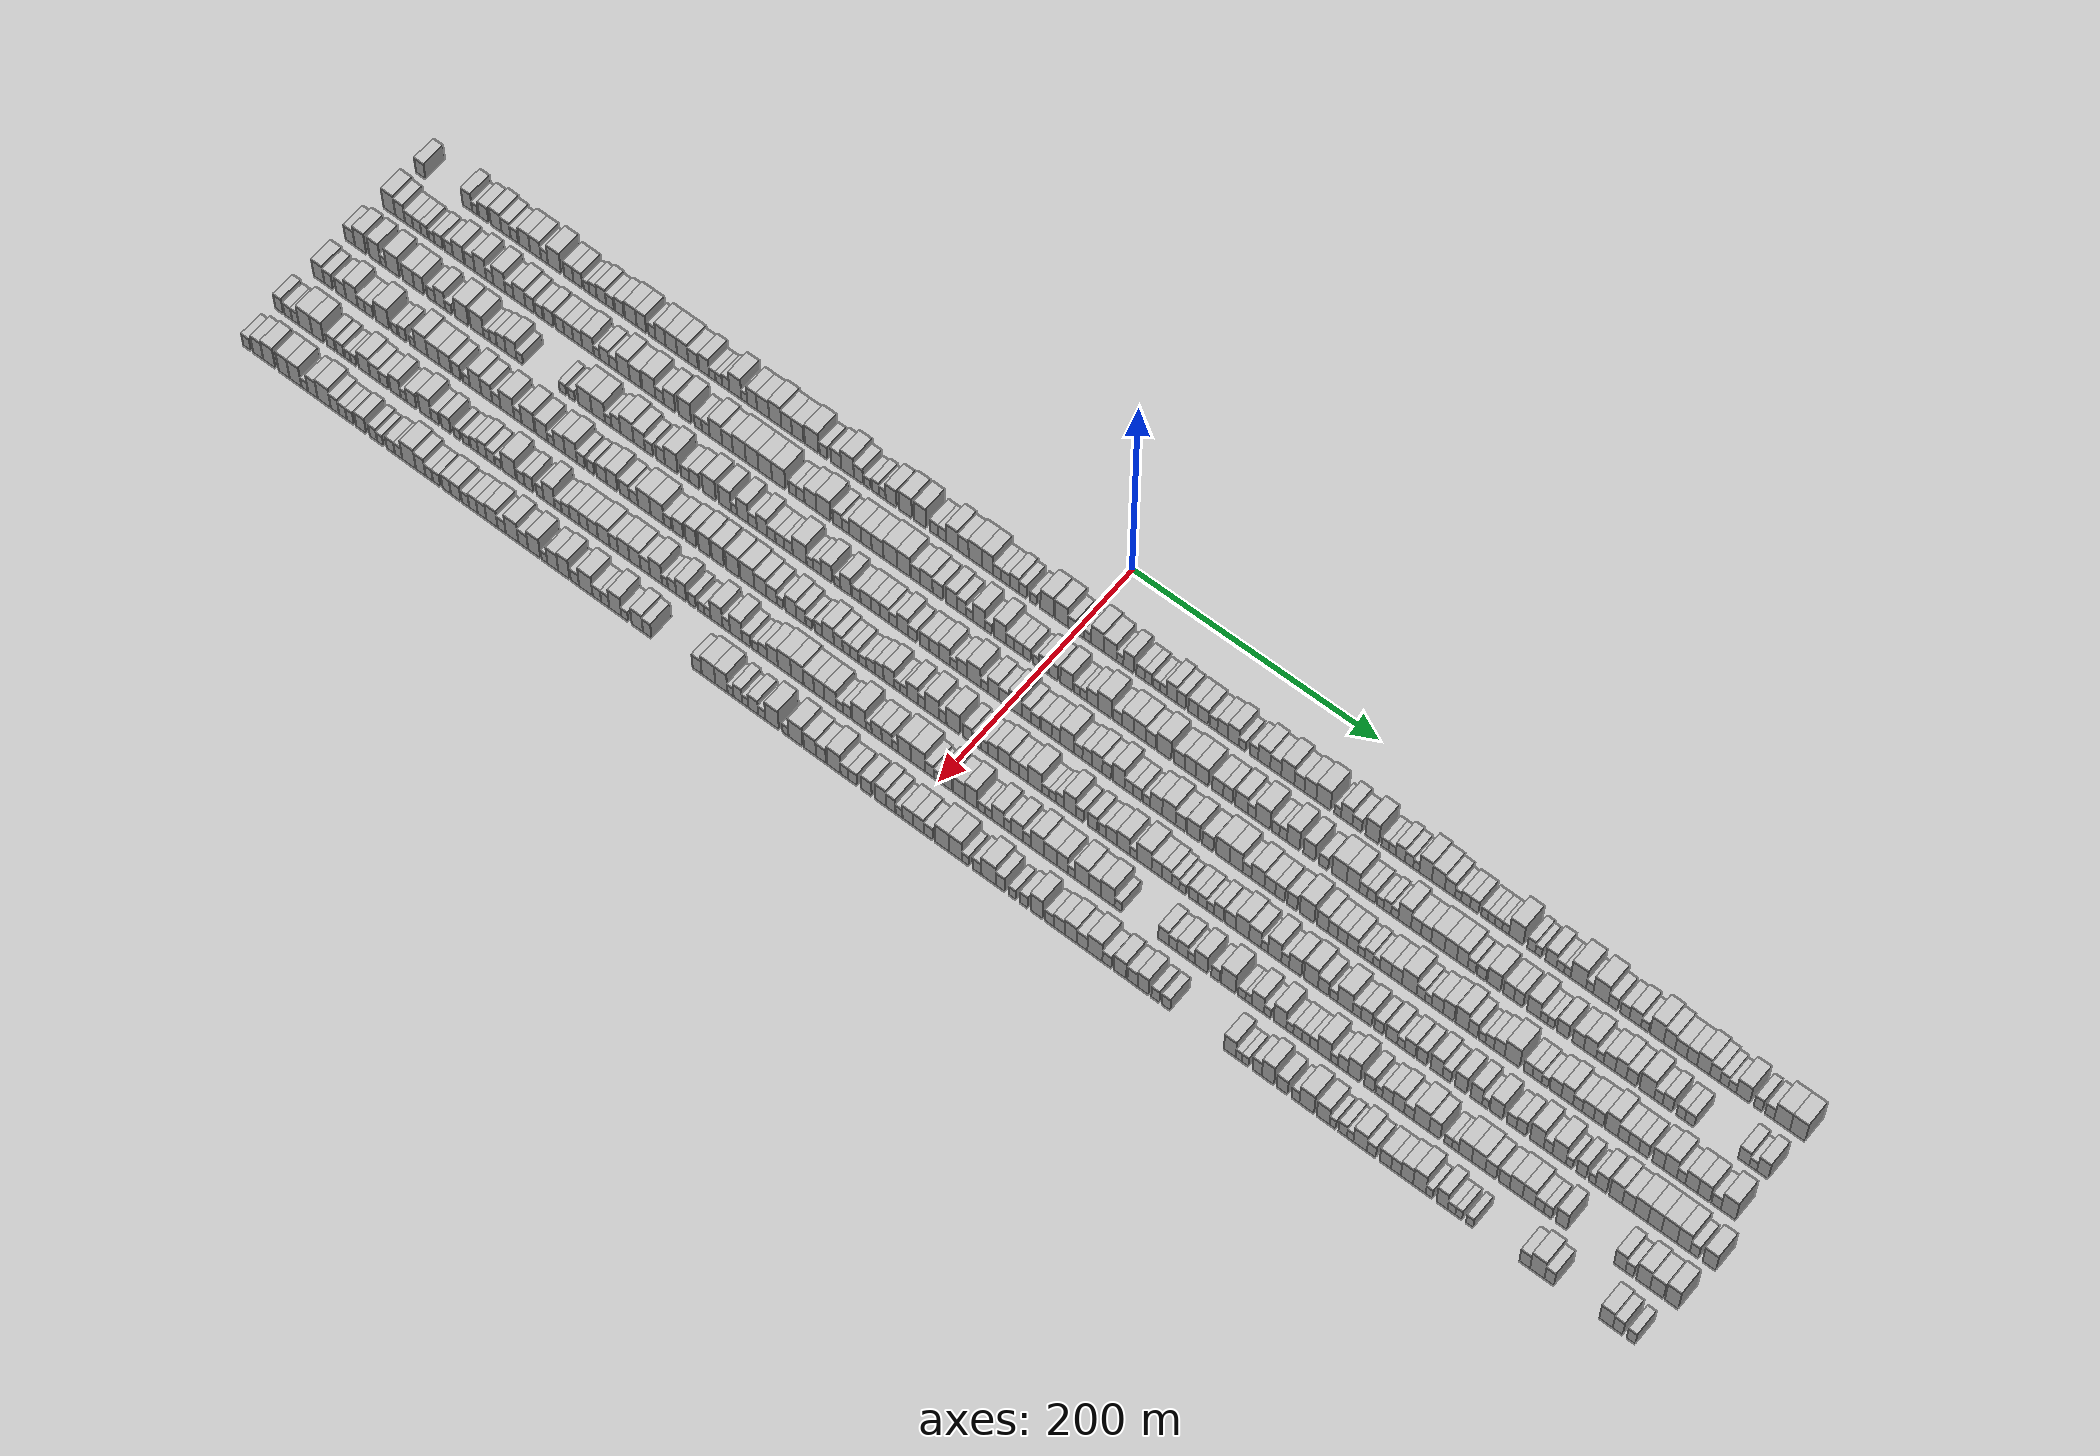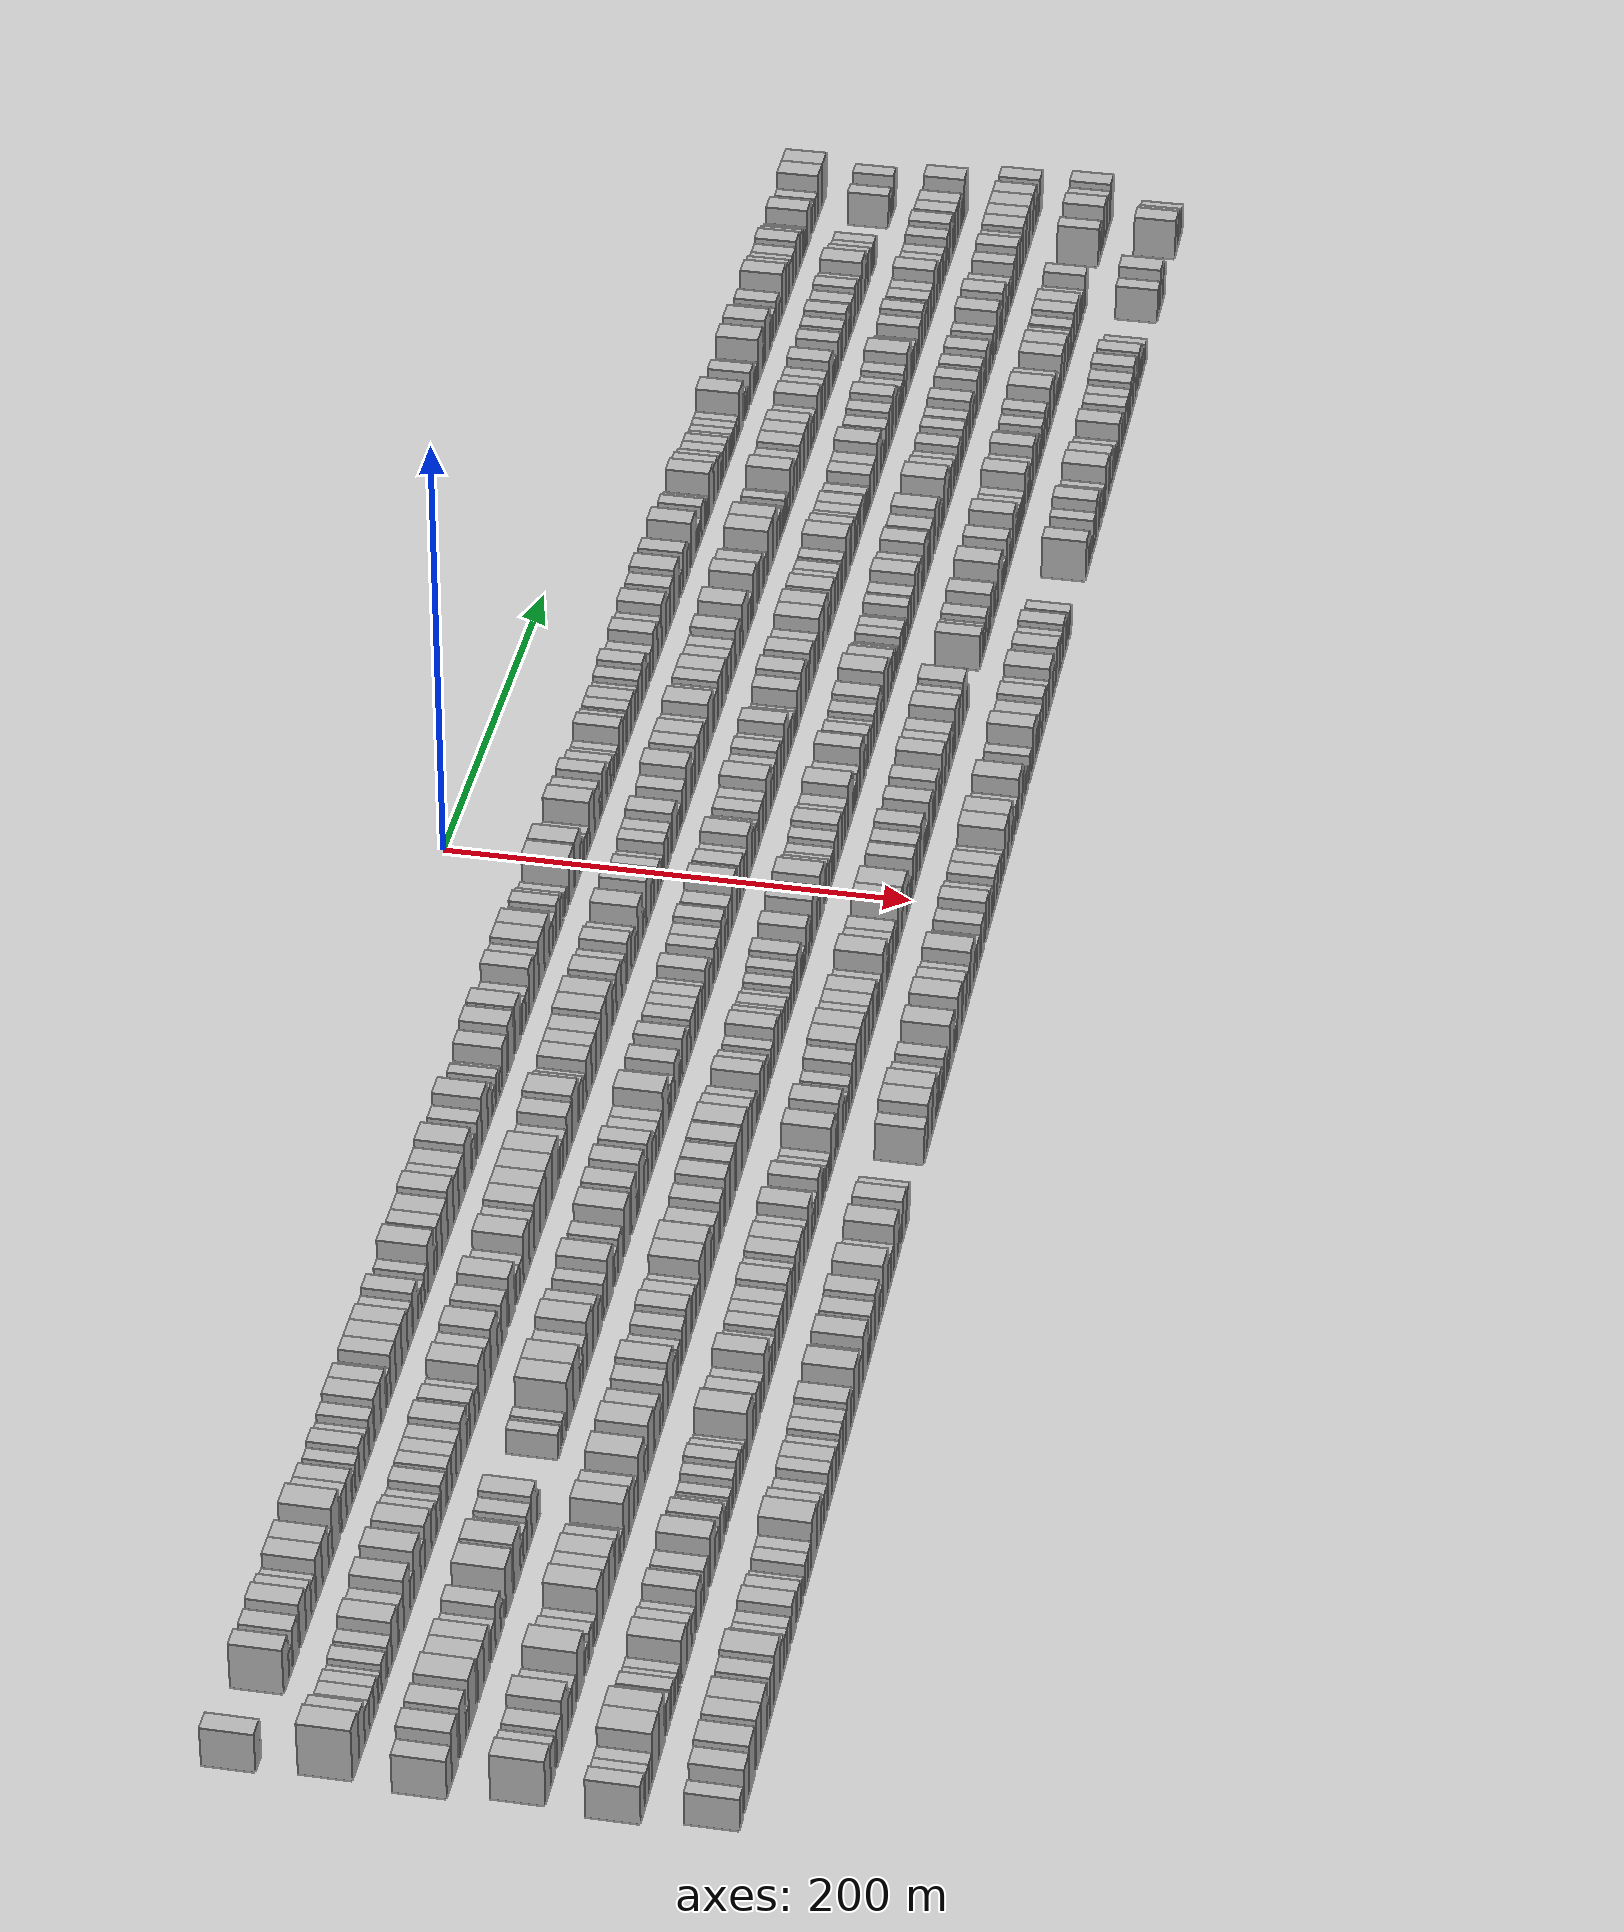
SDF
<sdf version="1.6">
 <world name="default">
  <scene>
   <sky><clouds><speed>12</speed></clouds></sky>
   <ambient>0.4 0.4 0.4 1</ambient>
   <background>0.7 0.7 0.7 1</background>
   <shadows>1</shadows>
  </scene>
  <gravity>0 0 -9.8066</gravity>
  <magnetic_field>6e-06 2.3e-05 -4.2e-05</magnetic_field>
  <physics default="0" name="default_physics" type="ode">
   <ode>
    <solver>
     <type>quick</type>
     <iters>10</iters>
     <sor>1.0</sor>
     <use_dynamic_moi_rescaling>0</use_dynamic_moi_rescaling>
    </solver>
    <constraints>
     <cfm>0</cfm>
     <erp>0.2</erp>
     <contact_max_correcting_vel>100</contact_max_correcting_vel>
     <contact_surface_layer>0.001</contact_surface_layer>
    </constraints>
   </ode>
   <max_step_size>0.004</max_step_size>
   <real_time_factor>1</real_time_factor>
   <real_time_update_rate>250</real_time_update_rate>
  </physics>
  <light name="sun" type="directional">
   <pose>0 0 10 0 0 0</pose>
   <diffuse>0.8 0.8 0.8 1</diffuse>
   <specular>0.2 0.2 0.2 1</specular>
   <attenuation>
    <range>1000</range>
    <constant>0.9</constant>
    <linear>0.01</linear>
    <quadratic>0.001</quadratic>
   </attenuation>
   <direction>-0.5 0.1 -0.9</direction>
  </light>
  <model name="building_1">
   <static>1</static>
   <pose>50.0000 -564.7343 0 0.000000 0.000000 0.000000</pose>
   <link name="link">
    <pose>0 0 9.00 0 0 0</pose>
    <collision name="collision"><geometry><box><size>20.0000 8.5313 18.0000</size></box></geometry></collision>
    <visual name="visual">
     <cast_shadows>0</cast_shadows>
     <geometry><box><size>20.0000 8.5313 18.0000</size></box></geometry>
     <material>
      <script>
       <uri>model://HANNAS_wall/materials/scripts</uri>
       <uri>model://HANNAS_wall/materials/textures</uri>
       <name>vrc/HANNAS_wall</name>
      </script>
     </material>
    </visual>
   </link>
  </model>
  <model name="building_2">
   <static>1</static>
   <pose>50.0000 -522.7855 0 0.000000 0.000000 0.000000</pose>
   <link name="link">
    <pose>0 0 10.50 0 0 0</pose>
    <collision name="collision"><geometry><box><size>20.0000 8.4554 21.0000</size></box></geometry></collision>
    <visual name="visual">
     <cast_shadows>0</cast_shadows>
     <geometry><box><size>20.0000 8.4554 21.0000</size></box></geometry>
     <material>
      <script>
       <uri>model://HANNAS_wall/materials/scripts</uri>
       <uri>model://HANNAS_wall/materials/textures</uri>
       <name>vrc/HANNAS_wall</name>
      </script>
     </material>
    </visual>
   </link>
  </model>
  <model name="building_3">
   <static>1</static>
   <pose>50.0000 -516.0890 0 0.000000 0.000000 0.000000</pose>
   <link name="link">
    <pose>0 0 6.00 0 0 0</pose>
    <collision name="collision"><geometry><box><size>20.0000 4.9377 12.0000</size></box></geometry></collision>
    <visual name="visual">
     <cast_shadows>0</cast_shadows>
     <geometry><box><size>20.0000 4.9377 12.0000</size></box></geometry>
     <material>
      <script>
       <uri>model://HANNAS_wall/materials/scripts</uri>
       <uri>model://HANNAS_wall/materials/textures</uri>
       <name>vrc/HANNAS_wall</name>
      </script>
     </material>
    </visual>
   </link>
  </model>
  <model name="building_4">
   <static>1</static>
   <pose>50.0000 -508.3093 0 0.000000 0.000000 0.000000</pose>
   <link name="link">
    <pose>0 0 9.00 0 0 0</pose>
    <collision name="collision"><geometry><box><size>20.0000 8.6217 18.0000</size></box></geometry></collision>
    <visual name="visual">
     <cast_shadows>0</cast_shadows>
     <geometry><box><size>20.0000 8.6217 18.0000</size></box></geometry>
     <material>
      <script>
       <uri>model://HANNAS_wall/materials/scripts</uri>
       <uri>model://HANNAS_wall/materials/textures</uri>
       <name>vrc/HANNAS_wall</name>
      </script>
     </material>
    </visual>
   </link>
  </model>
  <model name="building_5">
   <static>1</static>
   <pose>50.0000 -497.2470 0 0.000000 0.000000 0.000000</pose>
   <link name="link">
    <pose>0 0 10.50 0 0 0</pose>
    <collision name="collision"><geometry><box><size>20.0000 9.5029 21.0000</size></box></geometry></collision>
    <visual name="visual">
     <cast_shadows>0</cast_shadows>
     <geometry><box><size>20.0000 9.5029 21.0000</size></box></geometry>
     <material>
      <script>
       <uri>model://HANNAS_wall/materials/scripts</uri>
       <uri>model://HANNAS_wall/materials/textures</uri>
       <name>vrc/HANNAS_wall</name>
      </script>
     </material>
    </visual>
   </link>
  </model>
  <model name="building_6">
   <static>1</static>
   <pose>50.0000 -488.4433 0 0.000000 0.000000 0.000000</pose>
   <link name="link">
    <pose>0 0 9.00 0 0 0</pose>
    <collision name="collision"><geometry><box><size>20.0000 8.1045 18.0000</size></box></geometry></collision>
    <visual name="visual">
     <cast_shadows>0</cast_shadows>
     <geometry><box><size>20.0000 8.1045 18.0000</size></box></geometry>
     <material>
      <script>
       <uri>model://HANNAS_wall/materials/scripts</uri>
       <uri>model://HANNAS_wall/materials/textures</uri>
       <name>vrc/HANNAS_wall</name>
      </script>
     </material>
    </visual>
   </link>
  </model>
  <model name="building_7">
   <static>1</static>
   <pose>50.0000 -481.0528 0 0.000000 0.000000 0.000000</pose>
   <link name="link">
    <pose>0 0 7.50 0 0 0</pose>
    <collision name="collision"><geometry><box><size>20.0000 6.6764 15.0000</size></box></geometry></collision>
    <visual name="visual">
     <cast_shadows>0</cast_shadows>
     <geometry><box><size>20.0000 6.6764 15.0000</size></box></geometry>
     <material>
      <script>
       <uri>model://HANNAS_wall/materials/scripts</uri>
       <uri>model://HANNAS_wall/materials/textures</uri>
       <name>vrc/HANNAS_wall</name>
      </script>
     </material>
    </visual>
   </link>
  </model>
  <model name="building_8">
   <static>1</static>
   <pose>50.0000 -471.8938 0 0.000000 0.000000 0.000000</pose>
   <link name="link">
    <pose>0 0 10.50 0 0 0</pose>
    <collision name="collision"><geometry><box><size>20.0000 9.6416 21.0000</size></box></geometry></collision>
    <visual name="visual">
     <cast_shadows>0</cast_shadows>
     <geometry><box><size>20.0000 9.6416 21.0000</size></box></geometry>
     <material>
      <script>
       <uri>model://HANNAS_wall/materials/scripts</uri>
       <uri>model://HANNAS_wall/materials/textures</uri>
       <name>vrc/HANNAS_wall</name>
      </script>
     </material>
    </visual>
   </link>
  </model>
  <model name="building_9">
   <static>1</static>
   <pose>50.0000 -462.2216 0 0.000000 0.000000 0.000000</pose>
   <link name="link">
    <pose>0 0 10.50 0 0 0</pose>
    <collision name="collision"><geometry><box><size>20.0000 9.7028 21.0000</size></box></geometry></collision>
    <visual name="visual">
     <cast_shadows>0</cast_shadows>
     <geometry><box><size>20.0000 9.7028 21.0000</size></box></geometry>
     <material>
      <script>
       <uri>model://HANNAS_wall/materials/scripts</uri>
       <uri>model://HANNAS_wall/materials/textures</uri>
       <name>vrc/HANNAS_wall</name>
      </script>
     </material>
    </visual>
   </link>
  </model>
  <model name="building_10">
   <static>1</static>
   <pose>50.0000 -454.3482 0 0.000000 0.000000 0.000000</pose>
   <link name="link">
    <pose>0 0 7.50 0 0 0</pose>
    <collision name="collision"><geometry><box><size>20.0000 6.0441 15.0000</size></box></geometry></collision>
    <visual name="visual">
     <cast_shadows>0</cast_shadows>
     <geometry><box><size>20.0000 6.0441 15.0000</size></box></geometry>
     <material>
      <script>
       <uri>model://HANNAS_wall/materials/scripts</uri>
       <uri>model://HANNAS_wall/materials/textures</uri>
       <name>vrc/HANNAS_wall</name>
      </script>
     </material>
    </visual>
   </link>
  </model>
  <model name="building_11">
   <static>1</static>
   <pose>50.0000 -445.5885 0 0.000000 0.000000 0.000000</pose>
   <link name="link">
    <pose>0 0 12.00 0 0 0</pose>
    <collision name="collision"><geometry><box><size>20.0000 11.4752 24.0000</size></box></geometry></collision>
    <visual name="visual">
     <cast_shadows>0</cast_shadows>
     <geometry><box><size>20.0000 11.4752 24.0000</size></box></geometry>
     <material>
      <script>
       <uri>model://HANNAS_wall/materials/scripts</uri>
       <uri>model://HANNAS_wall/materials/textures</uri>
       <name>vrc/HANNAS_wall</name>
      </script>
     </material>
    </visual>
   </link>
  </model>
  <model name="building_12">
   <static>1</static>
   <pose>50.0000 -432.8625 0 0.000000 0.000000 0.000000</pose>
   <link name="link">
    <pose>0 0 9.00 0 0 0</pose>
    <collision name="collision"><geometry><box><size>20.0000 7.9769 18.0000</size></box></geometry></collision>
    <visual name="visual">
     <cast_shadows>0</cast_shadows>
     <geometry><box><size>20.0000 7.9769 18.0000</size></box></geometry>
     <material>
      <script>
       <uri>model://HANNAS_wall/materials/scripts</uri>
       <uri>model://HANNAS_wall/materials/textures</uri>
       <name>vrc/HANNAS_wall</name>
      </script>
     </material>
    </visual>
   </link>
  </model>
  <model name="building_13">
   <static>1</static>
   <pose>50.0000 -424.8366 0 0.000000 0.000000 0.000000</pose>
   <link name="link">
    <pose>0 0 9.00 0 0 0</pose>
    <collision name="collision"><geometry><box><size>20.0000 8.0749 18.0000</size></box></geometry></collision>
    <visual name="visual">
     <cast_shadows>0</cast_shadows>
     <geometry><box><size>20.0000 8.0749 18.0000</size></box></geometry>
     <material>
      <script>
       <uri>model://HANNAS_wall/materials/scripts</uri>
       <uri>model://HANNAS_wall/materials/textures</uri>
       <name>vrc/HANNAS_wall</name>
      </script>
     </material>
    </visual>
   </link>
  </model>
  <model name="building_14">
   <static>1</static>
   <pose>50.0000 -417.2963 0 0.000000 0.000000 0.000000</pose>
   <link name="link">
    <pose>0 0 6.00 0 0 0</pose>
    <collision name="collision"><geometry><box><size>20.0000 5.0056 12.0000</size></box></geometry></collision>
    <visual name="visual">
     <cast_shadows>0</cast_shadows>
     <geometry><box><size>20.0000 5.0056 12.0000</size></box></geometry>
     <material>
      <script>
       <uri>model://HANNAS_wall/materials/scripts</uri>
       <uri>model://HANNAS_wall/materials/textures</uri>
       <name>vrc/HANNAS_wall</name>
      </script>
     </material>
    </visual>
   </link>
  </model>
  <model name="building_15">
   <static>1</static>
   <pose>50.0000 -411.5649 0 0.000000 0.000000 0.000000</pose>
   <link name="link">
    <pose>0 0 7.50 0 0 0</pose>
    <collision name="collision"><geometry><box><size>20.0000 6.4572 15.0000</size></box></geometry></collision>
    <visual name="visual">
     <cast_shadows>0</cast_shadows>
     <geometry><box><size>20.0000 6.4572 15.0000</size></box></geometry>
     <material>
      <script>
       <uri>model://HANNAS_wall/materials/scripts</uri>
       <uri>model://HANNAS_wall/materials/textures</uri>
       <name>vrc/HANNAS_wall</name>
      </script>
     </material>
    </visual>
   </link>
  </model>
  <model name="building_16">
   <static>1</static>
   <pose>50.0000 -404.2194 0 0.000000 0.000000 0.000000</pose>
   <link name="link">
    <pose>0 0 9.00 0 0 0</pose>
    <collision name="collision"><geometry><box><size>20.0000 8.2338 18.0000</size></box></geometry></collision>
    <visual name="visual">
     <cast_shadows>0</cast_shadows>
     <geometry><box><size>20.0000 8.2338 18.0000</size></box></geometry>
     <material>
      <script>
       <uri>model://HANNAS_wall/materials/scripts</uri>
       <uri>model://HANNAS_wall/materials/textures</uri>
       <name>vrc/HANNAS_wall</name>
      </script>
     </material>
    </visual>
   </link>
  </model>
  <model name="building_17">
   <static>1</static>
   <pose>50.0000 -396.6738 0 0.000000 0.000000 0.000000</pose>
   <link name="link">
    <pose>0 0 7.50 0 0 0</pose>
    <collision name="collision"><geometry><box><size>20.0000 6.8575 15.0000</size></box></geometry></collision>
    <visual name="visual">
     <cast_shadows>0</cast_shadows>
     <geometry><box><size>20.0000 6.8575 15.0000</size></box></geometry>
     <material>
      <script>
       <uri>model://HANNAS_wall/materials/scripts</uri>
       <uri>model://HANNAS_wall/materials/textures</uri>
       <name>vrc/HANNAS_wall</name>
      </script>
     </material>
    </visual>
   </link>
  </model>
  <model name="building_18">
   <static>1</static>
   <pose>50.0000 -388.4212 0 0.000000 0.000000 0.000000</pose>
   <link name="link">
    <pose>0 0 9.00 0 0 0</pose>
    <collision name="collision"><geometry><box><size>20.0000 7.6475 18.0000</size></box></geometry></collision>
    <visual name="visual">
     <cast_shadows>0</cast_shadows>
     <geometry><box><size>20.0000 7.6475 18.0000</size></box></geometry>
     <material>
      <script>
       <uri>model://HANNAS_wall/materials/scripts</uri>
       <uri>model://HANNAS_wall/materials/textures</uri>
       <name>vrc/HANNAS_wall</name>
      </script>
     </material>
    </visual>
   </link>
  </model>
  <model name="building_19">
   <static>1</static>
   <pose>50.0000 -378.5069 0 0.000000 0.000000 0.000000</pose>
   <link name="link">
    <pose>0 0 10.50 0 0 0</pose>
    <collision name="collision"><geometry><box><size>20.0000 10.1811 21.0000</size></box></geometry></collision>
    <visual name="visual">
     <cast_shadows>0</cast_shadows>
     <geometry><box><size>20.0000 10.1811 21.0000</size></box></geometry>
     <material>
      <script>
       <uri>model://HANNAS_wall/materials/scripts</uri>
       <uri>model://HANNAS_wall/materials/textures</uri>
       <name>vrc/HANNAS_wall</name>
      </script>
     </material>
    </visual>
   </link>
  </model>
  <model name="building_20">
   <static>1</static>
   <pose>50.0000 -369.2015 0 0.000000 0.000000 0.000000</pose>
   <link name="link">
    <pose>0 0 10.50 0 0 0</pose>
    <collision name="collision"><geometry><box><size>20.0000 8.4297 21.0000</size></box></geometry></collision>
    <visual name="visual">
     <cast_shadows>0</cast_shadows>
     <geometry><box><size>20.0000 8.4297 21.0000</size></box></geometry>
     <material>
      <script>
       <uri>model://HANNAS_wall/materials/scripts</uri>
       <uri>model://HANNAS_wall/materials/textures</uri>
       <name>vrc/HANNAS_wall</name>
      </script>
     </material>
    </visual>
   </link>
  </model>
  <model name="building_21">
   <static>1</static>
   <pose>50.0000 -359.9407 0 0.000000 0.000000 0.000000</pose>
   <link name="link">
    <pose>0 0 7.50 0 0 0</pose>
    <collision name="collision"><geometry><box><size>20.0000 6.0918 15.0000</size></box></geometry></collision>
    <visual name="visual">
     <cast_shadows>0</cast_shadows>
     <geometry><box><size>20.0000 6.0918 15.0000</size></box></geometry>
     <material>
      <script>
       <uri>model://HANNAS_wall/materials/scripts</uri>
       <uri>model://HANNAS_wall/materials/textures</uri>
       <name>vrc/HANNAS_wall</name>
      </script>
     </material>
    </visual>
   </link>
  </model>
  <model name="building_22">
   <static>1</static>
   <pose>50.0000 -352.5626 0 0.000000 0.000000 0.000000</pose>
   <link name="link">
    <pose>0 0 10.50 0 0 0</pose>
    <collision name="collision"><geometry><box><size>20.0000 8.6644 21.0000</size></box></geometry></collision>
    <visual name="visual">
     <cast_shadows>0</cast_shadows>
     <geometry><box><size>20.0000 8.6644 21.0000</size></box></geometry>
     <material>
      <script>
       <uri>model://HANNAS_wall/materials/scripts</uri>
       <uri>model://HANNAS_wall/materials/textures</uri>
       <name>vrc/HANNAS_wall</name>
      </script>
     </material>
    </visual>
   </link>
  </model>
  <model name="building_23">
   <static>1</static>
   <pose>50.0000 -343.1908 0 0.000000 0.000000 0.000000</pose>
   <link name="link">
    <pose>0 0 10.50 0 0 0</pose>
    <collision name="collision"><geometry><box><size>20.0000 10.0792 21.0000</size></box></geometry></collision>
    <visual name="visual">
     <cast_shadows>0</cast_shadows>
     <geometry><box><size>20.0000 10.0792 21.0000</size></box></geometry>
     <material>
      <script>
       <uri>model://HANNAS_wall/materials/scripts</uri>
       <uri>model://HANNAS_wall/materials/textures</uri>
       <name>vrc/HANNAS_wall</name>
      </script>
     </material>
    </visual>
   </link>
  </model>
  <model name="building_24">
   <static>1</static>
   <pose>50.0000 -333.3636 0 0.000000 0.000000 0.000000</pose>
   <link name="link">
    <pose>0 0 10.50 0 0 0</pose>
    <collision name="collision"><geometry><box><size>20.0000 9.5752 21.0000</size></box></geometry></collision>
    <visual name="visual">
     <cast_shadows>0</cast_shadows>
     <geometry><box><size>20.0000 9.5752 21.0000</size></box></geometry>
     <material>
      <script>
       <uri>model://HANNAS_wall/materials/scripts</uri>
       <uri>model://HANNAS_wall/materials/textures</uri>
       <name>vrc/HANNAS_wall</name>
      </script>
     </material>
    </visual>
   </link>
  </model>
  <model name="building_25">
   <static>1</static>
   <pose>50.0000 -324.2821 0 0.000000 0.000000 0.000000</pose>
   <link name="link">
    <pose>0 0 9.00 0 0 0</pose>
    <collision name="collision"><geometry><box><size>20.0000 8.5880 18.0000</size></box></geometry></collision>
    <visual name="visual">
     <cast_shadows>0</cast_shadows>
     <geometry><box><size>20.0000 8.5880 18.0000</size></box></geometry>
     <material>
      <script>
       <uri>model://HANNAS_wall/materials/scripts</uri>
       <uri>model://HANNAS_wall/materials/textures</uri>
       <name>vrc/HANNAS_wall</name>
      </script>
     </material>
    </visual>
   </link>
  </model>
  <model name="building_26">
   <static>1</static>
   <pose>50.0000 -314.6036 0 0.000000 0.000000 0.000000</pose>
   <link name="link">
    <pose>0 0 10.50 0 0 0</pose>
    <collision name="collision"><geometry><box><size>20.0000 8.7688 21.0000</size></box></geometry></collision>
    <visual name="visual">
     <cast_shadows>0</cast_shadows>
     <geometry><box><size>20.0000 8.7688 21.0000</size></box></geometry>
     <material>
      <script>
       <uri>model://HANNAS_wall/materials/scripts</uri>
       <uri>model://HANNAS_wall/materials/textures</uri>
       <name>vrc/HANNAS_wall</name>
      </script>
     </material>
    </visual>
   </link>
  </model>
  <model name="building_27">
   <static>1</static>
   <pose>50.0000 -307.4533 0 0.000000 0.000000 0.000000</pose>
   <link name="link">
    <pose>0 0 6.00 0 0 0</pose>
    <collision name="collision"><geometry><box><size>20.0000 5.5318 12.0000</size></box></geometry></collision>
    <visual name="visual">
     <cast_shadows>0</cast_shadows>
     <geometry><box><size>20.0000 5.5318 12.0000</size></box></geometry>
     <material>
      <script>
       <uri>model://HANNAS_wall/materials/scripts</uri>
       <uri>model://HANNAS_wall/materials/textures</uri>
       <name>vrc/HANNAS_wall</name>
      </script>
     </material>
    </visual>
   </link>
  </model>
  <model name="building_28">
   <static>1</static>
   <pose>50.0000 -301.9420 0 0.000000 0.000000 0.000000</pose>
   <link name="link">
    <pose>0 0 6.00 0 0 0</pose>
    <collision name="collision"><geometry><box><size>20.0000 5.4909 12.0000</size></box></geometry></collision>
    <visual name="visual">
     <cast_shadows>0</cast_shadows>
     <geometry><box><size>20.0000 5.4909 12.0000</size></box></geometry>
     <material>
      <script>
       <uri>model://HANNAS_wall/materials/scripts</uri>
       <uri>model://HANNAS_wall/materials/textures</uri>
       <name>vrc/HANNAS_wall</name>
      </script>
     </material>
    </visual>
   </link>
  </model>
  <model name="building_29">
   <static>1</static>
   <pose>50.0000 -296.1040 0 0.000000 0.000000 0.000000</pose>
   <link name="link">
    <pose>0 0 7.50 0 0 0</pose>
    <collision name="collision"><geometry><box><size>20.0000 6.1851 15.0000</size></box></geometry></collision>
    <visual name="visual">
     <cast_shadows>0</cast_shadows>
     <geometry><box><size>20.0000 6.1851 15.0000</size></box></geometry>
     <material>
      <script>
       <uri>model://HANNAS_wall/materials/scripts</uri>
       <uri>model://HANNAS_wall/materials/textures</uri>
       <name>vrc/HANNAS_wall</name>
      </script>
     </material>
    </visual>
   </link>
  </model>
  <model name="building_30">
   <static>1</static>
   <pose>50.0000 -287.7422 0 0.000000 0.000000 0.000000</pose>
   <link name="link">
    <pose>0 0 12.00 0 0 0</pose>
    <collision name="collision"><geometry><box><size>20.0000 10.5384 24.0000</size></box></geometry></collision>
    <visual name="visual">
     <cast_shadows>0</cast_shadows>
     <geometry><box><size>20.0000 10.5384 24.0000</size></box></geometry>
     <material>
      <script>
       <uri>model://HANNAS_wall/materials/scripts</uri>
       <uri>model://HANNAS_wall/materials/textures</uri>
       <name>vrc/HANNAS_wall</name>
      </script>
     </material>
    </visual>
   </link>
  </model>
  <model name="building_31">
   <static>1</static>
   <pose>50.0000 -280.0012 0 0.000000 0.000000 0.000000</pose>
   <link name="link">
    <pose>0 0 6.00 0 0 0</pose>
    <collision name="collision"><geometry><box><size>20.0000 4.9436 12.0000</size></box></geometry></collision>
    <visual name="visual">
     <cast_shadows>0</cast_shadows>
     <geometry><box><size>20.0000 4.9436 12.0000</size></box></geometry>
     <material>
      <script>
       <uri>model://HANNAS_wall/materials/scripts</uri>
       <uri>model://HANNAS_wall/materials/textures</uri>
       <name>vrc/HANNAS_wall</name>
      </script>
     </material>
    </visual>
   </link>
  </model>
  <model name="building_32">
   <static>1</static>
   <pose>50.0000 -273.3177 0 0.000000 0.000000 0.000000</pose>
   <link name="link">
    <pose>0 0 10.50 0 0 0</pose>
    <collision name="collision"><geometry><box><size>20.0000 8.4234 21.0000</size></box></geometry></collision>
    <visual name="visual">
     <cast_shadows>0</cast_shadows>
     <geometry><box><size>20.0000 8.4234 21.0000</size></box></geometry>
     <material>
      <script>
       <uri>model://HANNAS_wall/materials/scripts</uri>
       <uri>model://HANNAS_wall/materials/textures</uri>
       <name>vrc/HANNAS_wall</name>
      </script>
     </material>
    </visual>
   </link>
  </model>
  <model name="building_33">
   <static>1</static>
   <pose>50.0000 -263.8899 0 0.000000 0.000000 0.000000</pose>
   <link name="link">
    <pose>0 0 10.50 0 0 0</pose>
    <collision name="collision"><geometry><box><size>20.0000 10.4322 21.0000</size></box></geometry></collision>
    <visual name="visual">
     <cast_shadows>0</cast_shadows>
     <geometry><box><size>20.0000 10.4322 21.0000</size></box></geometry>
     <material>
      <script>
       <uri>model://HANNAS_wall/materials/scripts</uri>
       <uri>model://HANNAS_wall/materials/textures</uri>
       <name>vrc/HANNAS_wall</name>
      </script>
     </material>
    </visual>
   </link>
  </model>
  <model name="building_34">
   <static>1</static>
   <pose>50.0000 -253.4260 0 0.000000 0.000000 0.000000</pose>
   <link name="link">
    <pose>0 0 12.00 0 0 0</pose>
    <collision name="collision"><geometry><box><size>20.0000 10.4956 24.0000</size></box></geometry></collision>
    <visual name="visual">
     <cast_shadows>0</cast_shadows>
     <geometry><box><size>20.0000 10.4956 24.0000</size></box></geometry>
     <material>
      <script>
       <uri>model://HANNAS_wall/materials/scripts</uri>
       <uri>model://HANNAS_wall/materials/textures</uri>
       <name>vrc/HANNAS_wall</name>
      </script>
     </material>
    </visual>
   </link>
  </model>
  <model name="building_35">
   <static>1</static>
   <pose>50.0000 -243.6366 0 0.000000 0.000000 0.000000</pose>
   <link name="link">
    <pose>0 0 10.50 0 0 0</pose>
    <collision name="collision"><geometry><box><size>20.0000 9.0833 21.0000</size></box></geometry></collision>
    <visual name="visual">
     <cast_shadows>0</cast_shadows>
     <geometry><box><size>20.0000 9.0833 21.0000</size></box></geometry>
     <material>
      <script>
       <uri>model://HANNAS_wall/materials/scripts</uri>
       <uri>model://HANNAS_wall/materials/textures</uri>
       <name>vrc/HANNAS_wall</name>
      </script>
     </material>
    </visual>
   </link>
  </model>
  <model name="building_36">
   <static>1</static>
   <pose>50.0000 -234.0898 0 0.000000 0.000000 0.000000</pose>
   <link name="link">
    <pose>0 0 10.50 0 0 0</pose>
    <collision name="collision"><geometry><box><size>20.0000 10.0101 21.0000</size></box></geometry></collision>
    <visual name="visual">
     <cast_shadows>0</cast_shadows>
     <geometry><box><size>20.0000 10.0101 21.0000</size></box></geometry>
     <material>
      <script>
       <uri>model://HANNAS_wall/materials/scripts</uri>
       <uri>model://HANNAS_wall/materials/textures</uri>
       <name>vrc/HANNAS_wall</name>
      </script>
     </material>
    </visual>
   </link>
  </model>
  <model name="building_37">
   <static>1</static>
   <pose>50.0000 -222.2601 0 0.000000 0.000000 0.000000</pose>
   <link name="link">
    <pose>0 0 12.00 0 0 0</pose>
    <collision name="collision"><geometry><box><size>20.0000 11.6494 24.0000</size></box></geometry></collision>
    <visual name="visual">
     <cast_shadows>0</cast_shadows>
     <geometry><box><size>20.0000 11.6494 24.0000</size></box></geometry>
     <material>
      <script>
       <uri>model://HANNAS_wall/materials/scripts</uri>
       <uri>model://HANNAS_wall/materials/textures</uri>
       <name>vrc/HANNAS_wall</name>
      </script>
     </material>
    </visual>
   </link>
  </model>
  <model name="building_38">
   <static>1</static>
   <pose>50.0000 -212.0708 0 0.000000 0.000000 0.000000</pose>
   <link name="link">
    <pose>0 0 7.50 0 0 0</pose>
    <collision name="collision"><geometry><box><size>20.0000 6.7291 15.0000</size></box></geometry></collision>
    <visual name="visual">
     <cast_shadows>0</cast_shadows>
     <geometry><box><size>20.0000 6.7291 15.0000</size></box></geometry>
     <material>
      <script>
       <uri>model://HANNAS_wall/materials/scripts</uri>
       <uri>model://HANNAS_wall/materials/textures</uri>
       <name>vrc/HANNAS_wall</name>
      </script>
     </material>
    </visual>
   </link>
  </model>
  <model name="building_39">
   <static>1</static>
   <pose>50.0000 -201.4564 0 0.000000 0.000000 0.000000</pose>
   <link name="link">
    <pose>0 0 9.00 0 0 0</pose>
    <collision name="collision"><geometry><box><size>20.0000 8.4998 18.0000</size></box></geometry></collision>
    <visual name="visual">
     <cast_shadows>0</cast_shadows>
     <geometry><box><size>20.0000 8.4998 18.0000</size></box></geometry>
     <material>
      <script>
       <uri>model://HANNAS_wall/materials/scripts</uri>
       <uri>model://HANNAS_wall/materials/textures</uri>
       <name>vrc/HANNAS_wall</name>
      </script>
     </material>
    </visual>
   </link>
  </model>
  <model name="building_40">
   <static>1</static>
   <pose>50.0000 -191.7724 0 0.000000 0.000000 0.000000</pose>
   <link name="link">
    <pose>0 0 12.00 0 0 0</pose>
    <collision name="collision"><geometry><box><size>20.0000 10.8682 24.0000</size></box></geometry></collision>
    <visual name="visual">
     <cast_shadows>0</cast_shadows>
     <geometry><box><size>20.0000 10.8682 24.0000</size></box></geometry>
     <material>
      <script>
       <uri>model://HANNAS_wall/materials/scripts</uri>
       <uri>model://HANNAS_wall/materials/textures</uri>
       <name>vrc/HANNAS_wall</name>
      </script>
     </material>
    </visual>
   </link>
  </model>
  <model name="building_41">
   <static>1</static>
   <pose>50.0000 -182.4763 0 0.000000 0.000000 0.000000</pose>
   <link name="link">
    <pose>0 0 9.00 0 0 0</pose>
    <collision name="collision"><geometry><box><size>20.0000 7.7241 18.0000</size></box></geometry></collision>
    <visual name="visual">
     <cast_shadows>0</cast_shadows>
     <geometry><box><size>20.0000 7.7241 18.0000</size></box></geometry>
     <material>
      <script>
       <uri>model://HANNAS_wall/materials/scripts</uri>
       <uri>model://HANNAS_wall/materials/textures</uri>
       <name>vrc/HANNAS_wall</name>
      </script>
     </material>
    </visual>
   </link>
  </model>
  <model name="building_42">
   <static>1</static>
   <pose>50.0000 -174.8510 0 0.000000 0.000000 0.000000</pose>
   <link name="link">
    <pose>0 0 6.00 0 0 0</pose>
    <collision name="collision"><geometry><box><size>20.0000 5.5265 12.0000</size></box></geometry></collision>
    <visual name="visual">
     <cast_shadows>0</cast_shadows>
     <geometry><box><size>20.0000 5.5265 12.0000</size></box></geometry>
     <material>
      <script>
       <uri>model://HANNAS_wall/materials/scripts</uri>
       <uri>model://HANNAS_wall/materials/textures</uri>
       <name>vrc/HANNAS_wall</name>
      </script>
     </material>
    </visual>
   </link>
  </model>
  <model name="building_43">
   <static>1</static>
   <pose>50.0000 -167.9820 0 0.000000 0.000000 0.000000</pose>
   <link name="link">
    <pose>0 0 7.50 0 0 0</pose>
    <collision name="collision"><geometry><box><size>20.0000 6.2115 15.0000</size></box></geometry></collision>
    <visual name="visual">
     <cast_shadows>0</cast_shadows>
     <geometry><box><size>20.0000 6.2115 15.0000</size></box></geometry>
     <material>
      <script>
       <uri>model://HANNAS_wall/materials/scripts</uri>
       <uri>model://HANNAS_wall/materials/textures</uri>
       <name>vrc/HANNAS_wall</name>
      </script>
     </material>
    </visual>
   </link>
  </model>
  <model name="building_44">
   <static>1</static>
   <pose>50.0000 -162.1305 0 0.000000 0.000000 0.000000</pose>
   <link name="link">
    <pose>0 0 6.00 0 0 0</pose>
    <collision name="collision"><geometry><box><size>20.0000 5.4915 12.0000</size></box></geometry></collision>
    <visual name="visual">
     <cast_shadows>0</cast_shadows>
     <geometry><box><size>20.0000 5.4915 12.0000</size></box></geometry>
     <material>
      <script>
       <uri>model://HANNAS_wall/materials/scripts</uri>
       <uri>model://HANNAS_wall/materials/textures</uri>
       <name>vrc/HANNAS_wall</name>
      </script>
     </material>
    </visual>
   </link>
  </model>
  <model name="building_45">
   <static>1</static>
   <pose>50.0000 -154.7492 0 0.000000 0.000000 0.000000</pose>
   <link name="link">
    <pose>0 0 10.50 0 0 0</pose>
    <collision name="collision"><geometry><box><size>20.0000 9.2712 21.0000</size></box></geometry></collision>
    <visual name="visual">
     <cast_shadows>0</cast_shadows>
     <geometry><box><size>20.0000 9.2712 21.0000</size></box></geometry>
     <material>
      <script>
       <uri>model://HANNAS_wall/materials/scripts</uri>
       <uri>model://HANNAS_wall/materials/textures</uri>
       <name>vrc/HANNAS_wall</name>
      </script>
     </material>
    </visual>
   </link>
  </model>
  <model name="building_46">
   <static>1</static>
   <pose>50.0000 -142.6993 0 0.000000 0.000000 0.000000</pose>
   <link name="link">
    <pose>0 0 12.00 0 0 0</pose>
    <collision name="collision"><geometry><box><size>20.0000 10.8286 24.0000</size></box></geometry></collision>
    <visual name="visual">
     <cast_shadows>0</cast_shadows>
     <geometry><box><size>20.0000 10.8286 24.0000</size></box></geometry>
     <material>
      <script>
       <uri>model://HANNAS_wall/materials/scripts</uri>
       <uri>model://HANNAS_wall/materials/textures</uri>
       <name>vrc/HANNAS_wall</name>
      </script>
     </material>
    </visual>
   </link>
  </model>
  <model name="building_47">
   <static>1</static>
   <pose>50.0000 -130.2435 0 0.000000 0.000000 0.000000</pose>
   <link name="link">
    <pose>0 0 12.00 0 0 0</pose>
    <collision name="collision"><geometry><box><size>20.0000 10.0830 24.0000</size></box></geometry></collision>
    <visual name="visual">
     <cast_shadows>0</cast_shadows>
     <geometry><box><size>20.0000 10.0830 24.0000</size></box></geometry>
     <material>
      <script>
       <uri>model://HANNAS_wall/materials/scripts</uri>
       <uri>model://HANNAS_wall/materials/textures</uri>
       <name>vrc/HANNAS_wall</name>
      </script>
     </material>
    </visual>
   </link>
  </model>
  <model name="building_48">
   <static>1</static>
   <pose>50.0000 -118.5412 0 0.000000 0.000000 0.000000</pose>
   <link name="link">
    <pose>0 0 7.50 0 0 0</pose>
    <collision name="collision"><geometry><box><size>20.0000 7.3214 15.0000</size></box></geometry></collision>
    <visual name="visual">
     <cast_shadows>0</cast_shadows>
     <geometry><box><size>20.0000 7.3214 15.0000</size></box></geometry>
     <material>
      <script>
       <uri>model://HANNAS_wall/materials/scripts</uri>
       <uri>model://HANNAS_wall/materials/textures</uri>
       <name>vrc/HANNAS_wall</name>
      </script>
     </material>
    </visual>
   </link>
  </model>
  <model name="building_49">
   <static>1</static>
   <pose>50.0000 -111.5562 0 0.000000 0.000000 0.000000</pose>
   <link name="link">
    <pose>0 0 7.50 0 0 0</pose>
    <collision name="collision"><geometry><box><size>20.0000 6.6487 15.0000</size></box></geometry></collision>
    <visual name="visual">
     <cast_shadows>0</cast_shadows>
     <geometry><box><size>20.0000 6.6487 15.0000</size></box></geometry>
     <material>
      <script>
       <uri>model://HANNAS_wall/materials/scripts</uri>
       <uri>model://HANNAS_wall/materials/textures</uri>
       <name>vrc/HANNAS_wall</name>
      </script>
     </material>
    </visual>
   </link>
  </model>
  <model name="building_50">
   <static>1</static>
   <pose>50.0000 -103.3885 0 0.000000 0.000000 0.000000</pose>
   <link name="link">
    <pose>0 0 12.00 0 0 0</pose>
    <collision name="collision"><geometry><box><size>20.0000 9.6866 24.0000</size></box></geometry></collision>
    <visual name="visual">
     <cast_shadows>0</cast_shadows>
     <geometry><box><size>20.0000 9.6866 24.0000</size></box></geometry>
     <material>
      <script>
       <uri>model://HANNAS_wall/materials/scripts</uri>
       <uri>model://HANNAS_wall/materials/textures</uri>
       <name>vrc/HANNAS_wall</name>
      </script>
     </material>
    </visual>
   </link>
  </model>
  <model name="building_51">
   <static>1</static>
   <pose>50.0000 -94.0800 0 0.000000 0.000000 0.000000</pose>
   <link name="link">
    <pose>0 0 10.50 0 0 0</pose>
    <collision name="collision"><geometry><box><size>20.0000 8.9304 21.0000</size></box></geometry></collision>
    <visual name="visual">
     <cast_shadows>0</cast_shadows>
     <geometry><box><size>20.0000 8.9304 21.0000</size></box></geometry>
     <material>
      <script>
       <uri>model://HANNAS_wall/materials/scripts</uri>
       <uri>model://HANNAS_wall/materials/textures</uri>
       <name>vrc/HANNAS_wall</name>
      </script>
     </material>
    </visual>
   </link>
  </model>
  <model name="building_52">
   <static>1</static>
   <pose>50.0000 -84.0661 0 0.000000 0.000000 0.000000</pose>
   <link name="link">
    <pose>0 0 12.00 0 0 0</pose>
    <collision name="collision"><geometry><box><size>20.0000 11.0974 24.0000</size></box></geometry></collision>
    <visual name="visual">
     <cast_shadows>0</cast_shadows>
     <geometry><box><size>20.0000 11.0974 24.0000</size></box></geometry>
     <material>
      <script>
       <uri>model://HANNAS_wall/materials/scripts</uri>
       <uri>model://HANNAS_wall/materials/textures</uri>
       <name>vrc/HANNAS_wall</name>
      </script>
     </material>
    </visual>
   </link>
  </model>
  <model name="building_53">
   <static>1</static>
   <pose>50.0000 -73.6594 0 0.000000 0.000000 0.000000</pose>
   <link name="link">
    <pose>0 0 12.00 0 0 0</pose>
    <collision name="collision"><geometry><box><size>20.0000 9.7160 24.0000</size></box></geometry></collision>
    <visual name="visual">
     <cast_shadows>0</cast_shadows>
     <geometry><box><size>20.0000 9.7160 24.0000</size></box></geometry>
     <material>
      <script>
       <uri>model://HANNAS_wall/materials/scripts</uri>
       <uri>model://HANNAS_wall/materials/textures</uri>
       <name>vrc/HANNAS_wall</name>
      </script>
     </material>
    </visual>
   </link>
  </model>
  <model name="building_54">
   <static>1</static>
   <pose>50.0000 -65.4729 0 0.000000 0.000000 0.000000</pose>
   <link name="link">
    <pose>0 0 7.50 0 0 0</pose>
    <collision name="collision"><geometry><box><size>20.0000 6.6570 15.0000</size></box></geometry></collision>
    <visual name="visual">
     <cast_shadows>0</cast_shadows>
     <geometry><box><size>20.0000 6.6570 15.0000</size></box></geometry>
     <material>
      <script>
       <uri>model://HANNAS_wall/materials/scripts</uri>
       <uri>model://HANNAS_wall/materials/textures</uri>
       <name>vrc/HANNAS_wall</name>
      </script>
     </material>
    </visual>
   </link>
  </model>
  <model name="building_55">
   <static>1</static>
   <pose>50.0000 -58.6937 0 0.000000 0.000000 0.000000</pose>
   <link name="link">
    <pose>0 0 7.50 0 0 0</pose>
    <collision name="collision"><geometry><box><size>20.0000 6.9015 15.0000</size></box></geometry></collision>
    <visual name="visual">
     <cast_shadows>0</cast_shadows>
     <geometry><box><size>20.0000 6.9015 15.0000</size></box></geometry>
     <material>
      <script>
       <uri>model://HANNAS_wall/materials/scripts</uri>
       <uri>model://HANNAS_wall/materials/textures</uri>
       <name>vrc/HANNAS_wall</name>
      </script>
     </material>
    </visual>
   </link>
  </model>
  <model name="building_56">
   <static>1</static>
   <pose>50.0000 -51.3023 0 0.000000 0.000000 0.000000</pose>
   <link name="link">
    <pose>0 0 9.00 0 0 0</pose>
    <collision name="collision"><geometry><box><size>20.0000 7.8812 18.0000</size></box></geometry></collision>
    <visual name="visual">
     <cast_shadows>0</cast_shadows>
     <geometry><box><size>20.0000 7.8812 18.0000</size></box></geometry>
     <material>
      <script>
       <uri>model://HANNAS_wall/materials/scripts</uri>
       <uri>model://HANNAS_wall/materials/textures</uri>
       <name>vrc/HANNAS_wall</name>
      </script>
     </material>
    </visual>
   </link>
  </model>
  <model name="building_57">
   <static>1</static>
   <pose>50.0000 -44.3002 0 0.000000 0.000000 0.000000</pose>
   <link name="link">
    <pose>0 0 7.50 0 0 0</pose>
    <collision name="collision"><geometry><box><size>20.0000 6.1231 15.0000</size></box></geometry></collision>
    <visual name="visual">
     <cast_shadows>0</cast_shadows>
     <geometry><box><size>20.0000 6.1231 15.0000</size></box></geometry>
     <material>
      <script>
       <uri>model://HANNAS_wall/materials/scripts</uri>
       <uri>model://HANNAS_wall/materials/textures</uri>
       <name>vrc/HANNAS_wall</name>
      </script>
     </material>
    </visual>
   </link>
  </model>
  <model name="building_58">
   <static>1</static>
   <pose>50.0000 -35.5006 0 0.000000 0.000000 0.000000</pose>
   <link name="link">
    <pose>0 0 6.00 0 0 0</pose>
    <collision name="collision"><geometry><box><size>20.0000 5.4761 12.0000</size></box></geometry></collision>
    <visual name="visual">
     <cast_shadows>0</cast_shadows>
     <geometry><box><size>20.0000 5.4761 12.0000</size></box></geometry>
     <material>
      <script>
       <uri>model://HANNAS_wall/materials/scripts</uri>
       <uri>model://HANNAS_wall/materials/textures</uri>
       <name>vrc/HANNAS_wall</name>
      </script>
     </material>
    </visual>
   </link>
  </model>
  <model name="building_59">
   <static>1</static>
   <pose>50.0000 -24.3399 0 0.000000 0.000000 0.000000</pose>
   <link name="link">
    <pose>0 0 12.00 0 0 0</pose>
    <collision name="collision"><geometry><box><size>20.0000 10.8452 24.0000</size></box></geometry></collision>
    <visual name="visual">
     <cast_shadows>0</cast_shadows>
     <geometry><box><size>20.0000 10.8452 24.0000</size></box></geometry>
     <material>
      <script>
       <uri>model://HANNAS_wall/materials/scripts</uri>
       <uri>model://HANNAS_wall/materials/textures</uri>
       <name>vrc/HANNAS_wall</name>
      </script>
     </material>
    </visual>
   </link>
  </model>
  <model name="building_60">
   <static>1</static>
   <pose>50.0000 -12.4449 0 0.000000 0.000000 0.000000</pose>
   <link name="link">
    <pose>0 0 12.00 0 0 0</pose>
    <collision name="collision"><geometry><box><size>20.0000 10.9448 24.0000</size></box></geometry></collision>
    <visual name="visual">
     <cast_shadows>0</cast_shadows>
     <geometry><box><size>20.0000 10.9448 24.0000</size></box></geometry>
     <material>
      <script>
       <uri>model://HANNAS_wall/materials/scripts</uri>
       <uri>model://HANNAS_wall/materials/textures</uri>
       <name>vrc/HANNAS_wall</name>
      </script>
     </material>
    </visual>
   </link>
  </model>
  <model name="building_61">
   <static>1</static>
   <pose>50.0000 -3.7254 0 0.000000 0.000000 0.000000</pose>
   <link name="link">
    <pose>0 0 7.50 0 0 0</pose>
    <collision name="collision"><geometry><box><size>20.0000 6.4942 15.0000</size></box></geometry></collision>
    <visual name="visual">
     <cast_shadows>0</cast_shadows>
     <geometry><box><size>20.0000 6.4942 15.0000</size></box></geometry>
     <material>
      <script>
       <uri>model://HANNAS_wall/materials/scripts</uri>
       <uri>model://HANNAS_wall/materials/textures</uri>
       <name>vrc/HANNAS_wall</name>
      </script>
     </material>
    </visual>
   </link>
  </model>
  <model name="building_62">
   <static>1</static>
   <pose>50.0000 3.5018 0 0.000000 0.000000 0.000000</pose>
   <link name="link">
    <pose>0 0 6.00 0 0 0</pose>
    <collision name="collision"><geometry><box><size>20.0000 5.9601 12.0000</size></box></geometry></collision>
    <visual name="visual">
     <cast_shadows>0</cast_shadows>
     <geometry><box><size>20.0000 5.9601 12.0000</size></box></geometry>
     <material>
      <script>
       <uri>model://HANNAS_wall/materials/scripts</uri>
       <uri>model://HANNAS_wall/materials/textures</uri>
       <name>vrc/HANNAS_wall</name>
      </script>
     </material>
    </visual>
   </link>
  </model>
  <model name="building_63">
   <static>1</static>
   <pose>50.0000 9.3296 0 0.000000 0.000000 0.000000</pose>
   <link name="link">
    <pose>0 0 6.00 0 0 0</pose>
    <collision name="collision"><geometry><box><size>20.0000 5.6955 12.0000</size></box></geometry></collision>
    <visual name="visual">
     <cast_shadows>0</cast_shadows>
     <geometry><box><size>20.0000 5.6955 12.0000</size></box></geometry>
     <material>
      <script>
       <uri>model://HANNAS_wall/materials/scripts</uri>
       <uri>model://HANNAS_wall/materials/textures</uri>
       <name>vrc/HANNAS_wall</name>
      </script>
     </material>
    </visual>
   </link>
  </model>
  <model name="building_64">
   <static>1</static>
   <pose>50.0000 17.3628 0 0.000000 0.000000 0.000000</pose>
   <link name="link">
    <pose>0 0 12.00 0 0 0</pose>
    <collision name="collision"><geometry><box><size>20.0000 10.3709 24.0000</size></box></geometry></collision>
    <visual name="visual">
     <cast_shadows>0</cast_shadows>
     <geometry><box><size>20.0000 10.3709 24.0000</size></box></geometry>
     <material>
      <script>
       <uri>model://HANNAS_wall/materials/scripts</uri>
       <uri>model://HANNAS_wall/materials/textures</uri>
       <name>vrc/HANNAS_wall</name>
      </script>
     </material>
    </visual>
   </link>
  </model>
  <model name="building_65">
   <static>1</static>
   <pose>50.0000 27.7676 0 0.000000 0.000000 0.000000</pose>
   <link name="link">
    <pose>0 0 10.50 0 0 0</pose>
    <collision name="collision"><geometry><box><size>20.0000 10.4388 21.0000</size></box></geometry></collision>
    <visual name="visual">
     <cast_shadows>0</cast_shadows>
     <geometry><box><size>20.0000 10.4388 21.0000</size></box></geometry>
     <material>
      <script>
       <uri>model://HANNAS_wall/materials/scripts</uri>
       <uri>model://HANNAS_wall/materials/textures</uri>
       <name>vrc/HANNAS_wall</name>
      </script>
     </material>
    </visual>
   </link>
  </model>
  <model name="building_66">
   <static>1</static>
   <pose>50.0000 35.8073 0 0.000000 0.000000 0.000000</pose>
   <link name="link">
    <pose>0 0 6.00 0 0 0</pose>
    <collision name="collision"><geometry><box><size>20.0000 5.6406 12.0000</size></box></geometry></collision>
    <visual name="visual">
     <cast_shadows>0</cast_shadows>
     <geometry><box><size>20.0000 5.6406 12.0000</size></box></geometry>
     <material>
      <script>
       <uri>model://HANNAS_wall/materials/scripts</uri>
       <uri>model://HANNAS_wall/materials/textures</uri>
       <name>vrc/HANNAS_wall</name>
      </script>
     </material>
    </visual>
   </link>
  </model>
  <model name="building_67">
   <static>1</static>
   <pose>50.0000 42.9604 0 0.000000 0.000000 0.000000</pose>
   <link name="link">
    <pose>0 0 10.50 0 0 0</pose>
    <collision name="collision"><geometry><box><size>20.0000 8.6655 21.0000</size></box></geometry></collision>
    <visual name="visual">
     <cast_shadows>0</cast_shadows>
     <geometry><box><size>20.0000 8.6655 21.0000</size></box></geometry>
     <material>
      <script>
       <uri>model://HANNAS_wall/materials/scripts</uri>
       <uri>model://HANNAS_wall/materials/textures</uri>
       <name>vrc/HANNAS_wall</name>
      </script>
     </material>
    </visual>
   </link>
  </model>
  <model name="building_68">
   <static>1</static>
   <pose>50.0000 52.6133 0 0.000000 0.000000 0.000000</pose>
   <link name="link">
    <pose>0 0 7.50 0 0 0</pose>
    <collision name="collision"><geometry><box><size>20.0000 6.6403 15.0000</size></box></geometry></collision>
    <visual name="visual">
     <cast_shadows>0</cast_shadows>
     <geometry><box><size>20.0000 6.6403 15.0000</size></box></geometry>
     <material>
      <script>
       <uri>model://HANNAS_wall/materials/scripts</uri>
       <uri>model://HANNAS_wall/materials/textures</uri>
       <name>vrc/HANNAS_wall</name>
      </script>
     </material>
    </visual>
   </link>
  </model>
  <model name="building_69">
   <static>1</static>
   <pose>50.0000 58.9847 0 0.000000 0.000000 0.000000</pose>
   <link name="link">
    <pose>0 0 7.50 0 0 0</pose>
    <collision name="collision"><geometry><box><size>20.0000 6.1026 15.0000</size></box></geometry></collision>
    <visual name="visual">
     <cast_shadows>0</cast_shadows>
     <geometry><box><size>20.0000 6.1026 15.0000</size></box></geometry>
     <material>
      <script>
       <uri>model://HANNAS_wall/materials/scripts</uri>
       <uri>model://HANNAS_wall/materials/textures</uri>
       <name>vrc/HANNAS_wall</name>
      </script>
     </material>
    </visual>
   </link>
  </model>
  <model name="building_70">
   <static>1</static>
   <pose>50.0000 65.9096 0 0.000000 0.000000 0.000000</pose>
   <link name="link">
    <pose>0 0 6.00 0 0 0</pose>
    <collision name="collision"><geometry><box><size>20.0000 5.7470 12.0000</size></box></geometry></collision>
    <visual name="visual">
     <cast_shadows>0</cast_shadows>
     <geometry><box><size>20.0000 5.7470 12.0000</size></box></geometry>
     <material>
      <script>
       <uri>model://HANNAS_wall/materials/scripts</uri>
       <uri>model://HANNAS_wall/materials/textures</uri>
       <name>vrc/HANNAS_wall</name>
      </script>
     </material>
    </visual>
   </link>
  </model>
  <model name="building_71">
   <static>1</static>
   <pose>50.0000 71.3713 0 0.000000 0.000000 0.000000</pose>
   <link name="link">
    <pose>0 0 6.00 0 0 0</pose>
    <collision name="collision"><geometry><box><size>20.0000 5.1764 12.0000</size></box></geometry></collision>
    <visual name="visual">
     <cast_shadows>0</cast_shadows>
     <geometry><box><size>20.0000 5.1764 12.0000</size></box></geometry>
     <material>
      <script>
       <uri>model://HANNAS_wall/materials/scripts</uri>
       <uri>model://HANNAS_wall/materials/textures</uri>
       <name>vrc/HANNAS_wall</name>
      </script>
     </material>
    </visual>
   </link>
  </model>
  <model name="building_72">
   <static>1</static>
   <pose>50.0000 78.1862 0 0.000000 0.000000 0.000000</pose>
   <link name="link">
    <pose>0 0 10.50 0 0 0</pose>
    <collision name="collision"><geometry><box><size>20.0000 8.4534 21.0000</size></box></geometry></collision>
    <visual name="visual">
     <cast_shadows>0</cast_shadows>
     <geometry><box><size>20.0000 8.4534 21.0000</size></box></geometry>
     <material>
      <script>
       <uri>model://HANNAS_wall/materials/scripts</uri>
       <uri>model://HANNAS_wall/materials/textures</uri>
       <name>vrc/HANNAS_wall</name>
      </script>
     </material>
    </visual>
   </link>
  </model>
  <model name="building_73">
   <static>1</static>
   <pose>50.0000 86.0639 0 0.000000 0.000000 0.000000</pose>
   <link name="link">
    <pose>0 0 9.00 0 0 0</pose>
    <collision name="collision"><geometry><box><size>20.0000 7.3019 18.0000</size></box></geometry></collision>
    <visual name="visual">
     <cast_shadows>0</cast_shadows>
     <geometry><box><size>20.0000 7.3019 18.0000</size></box></geometry>
     <material>
      <script>
       <uri>model://HANNAS_wall/materials/scripts</uri>
       <uri>model://HANNAS_wall/materials/textures</uri>
       <name>vrc/HANNAS_wall</name>
      </script>
     </material>
    </visual>
   </link>
  </model>
  <model name="building_74">
   <static>1</static>
   <pose>50.0000 95.6060 0 0.000000 0.000000 0.000000</pose>
   <link name="link">
    <pose>0 0 9.00 0 0 0</pose>
    <collision name="collision"><geometry><box><size>20.0000 7.7823 18.0000</size></box></geometry></collision>
    <visual name="visual">
     <cast_shadows>0</cast_shadows>
     <geometry><box><size>20.0000 7.7823 18.0000</size></box></geometry>
     <material>
      <script>
       <uri>model://HANNAS_wall/materials/scripts</uri>
       <uri>model://HANNAS_wall/materials/textures</uri>
       <name>vrc/HANNAS_wall</name>
      </script>
     </material>
    </visual>
   </link>
  </model>
  <model name="building_75">
   <static>1</static>
   <pose>50.0000 103.7394 0 0.000000 0.000000 0.000000</pose>
   <link name="link">
    <pose>0 0 9.00 0 0 0</pose>
    <collision name="collision"><geometry><box><size>20.0000 8.4844 18.0000</size></box></geometry></collision>
    <visual name="visual">
     <cast_shadows>0</cast_shadows>
     <geometry><box><size>20.0000 8.4844 18.0000</size></box></geometry>
     <material>
      <script>
       <uri>model://HANNAS_wall/materials/scripts</uri>
       <uri>model://HANNAS_wall/materials/textures</uri>
       <name>vrc/HANNAS_wall</name>
      </script>
     </material>
    </visual>
   </link>
  </model>
  <model name="building_76">
   <static>1</static>
   <pose>50.0000 112.1376 0 0.000000 0.000000 0.000000</pose>
   <link name="link">
    <pose>0 0 7.50 0 0 0</pose>
    <collision name="collision"><geometry><box><size>20.0000 6.3120 15.0000</size></box></geometry></collision>
    <visual name="visual">
     <cast_shadows>0</cast_shadows>
     <geometry><box><size>20.0000 6.3120 15.0000</size></box></geometry>
     <material>
      <script>
       <uri>model://HANNAS_wall/materials/scripts</uri>
       <uri>model://HANNAS_wall/materials/textures</uri>
       <name>vrc/HANNAS_wall</name>
      </script>
     </material>
    </visual>
   </link>
  </model>
  <model name="building_77">
   <static>1</static>
   <pose>50.0000 119.5166 0 0.000000 0.000000 0.000000</pose>
   <link name="link">
    <pose>0 0 9.00 0 0 0</pose>
    <collision name="collision"><geometry><box><size>20.0000 8.4460 18.0000</size></box></geometry></collision>
    <visual name="visual">
     <cast_shadows>0</cast_shadows>
     <geometry><box><size>20.0000 8.4460 18.0000</size></box></geometry>
     <material>
      <script>
       <uri>model://HANNAS_wall/materials/scripts</uri>
       <uri>model://HANNAS_wall/materials/textures</uri>
       <name>vrc/HANNAS_wall</name>
      </script>
     </material>
    </visual>
   </link>
  </model>
  <model name="building_78">
   <static>1</static>
   <pose>50.0000 128.3027 0 0.000000 0.000000 0.000000</pose>
   <link name="link">
    <pose>0 0 10.50 0 0 0</pose>
    <collision name="collision"><geometry><box><size>20.0000 9.1263 21.0000</size></box></geometry></collision>
    <visual name="visual">
     <cast_shadows>0</cast_shadows>
     <geometry><box><size>20.0000 9.1263 21.0000</size></box></geometry>
     <material>
      <script>
       <uri>model://HANNAS_wall/materials/scripts</uri>
       <uri>model://HANNAS_wall/materials/textures</uri>
       <name>vrc/HANNAS_wall</name>
      </script>
     </material>
    </visual>
   </link>
  </model>
  <model name="building_79">
   <static>1</static>
   <pose>50.0000 135.6448 0 0.000000 0.000000 0.000000</pose>
   <link name="link">
    <pose>0 0 6.00 0 0 0</pose>
    <collision name="collision"><geometry><box><size>20.0000 5.5580 12.0000</size></box></geometry></collision>
    <visual name="visual">
     <cast_shadows>0</cast_shadows>
     <geometry><box><size>20.0000 5.5580 12.0000</size></box></geometry>
     <material>
      <script>
       <uri>model://HANNAS_wall/materials/scripts</uri>
       <uri>model://HANNAS_wall/materials/textures</uri>
       <name>vrc/HANNAS_wall</name>
      </script>
     </material>
    </visual>
   </link>
  </model>
  <model name="building_80">
   <static>1</static>
   <pose>50.0000 144.8148 0 0.000000 0.000000 0.000000</pose>
   <link name="link">
    <pose>0 0 7.50 0 0 0</pose>
    <collision name="collision"><geometry><box><size>20.0000 6.7819 15.0000</size></box></geometry></collision>
    <visual name="visual">
     <cast_shadows>0</cast_shadows>
     <geometry><box><size>20.0000 6.7819 15.0000</size></box></geometry>
     <material>
      <script>
       <uri>model://HANNAS_wall/materials/scripts</uri>
       <uri>model://HANNAS_wall/materials/textures</uri>
       <name>vrc/HANNAS_wall</name>
      </script>
     </material>
    </visual>
   </link>
  </model>
  <model name="building_81">
   <static>1</static>
   <pose>50.0000 153.0701 0 0.000000 0.000000 0.000000</pose>
   <link name="link">
    <pose>0 0 10.50 0 0 0</pose>
    <collision name="collision"><geometry><box><size>20.0000 9.7287 21.0000</size></box></geometry></collision>
    <visual name="visual">
     <cast_shadows>0</cast_shadows>
     <geometry><box><size>20.0000 9.7287 21.0000</size></box></geometry>
     <material>
      <script>
       <uri>model://HANNAS_wall/materials/scripts</uri>
       <uri>model://HANNAS_wall/materials/textures</uri>
       <name>vrc/HANNAS_wall</name>
      </script>
     </material>
    </visual>
   </link>
  </model>
  <model name="building_82">
   <static>1</static>
   <pose>50.0000 162.4113 0 0.000000 0.000000 0.000000</pose>
   <link name="link">
    <pose>0 0 9.00 0 0 0</pose>
    <collision name="collision"><geometry><box><size>20.0000 8.9536 18.0000</size></box></geometry></collision>
    <visual name="visual">
     <cast_shadows>0</cast_shadows>
     <geometry><box><size>20.0000 8.9536 18.0000</size></box></geometry>
     <material>
      <script>
       <uri>model://HANNAS_wall/materials/scripts</uri>
       <uri>model://HANNAS_wall/materials/textures</uri>
       <name>vrc/HANNAS_wall</name>
      </script>
     </material>
    </visual>
   </link>
  </model>
  <model name="building_83">
   <static>1</static>
   <pose>50.0000 172.1590 0 0.000000 0.000000 0.000000</pose>
   <link name="link">
    <pose>0 0 12.00 0 0 0</pose>
    <collision name="collision"><geometry><box><size>20.0000 10.5419 24.0000</size></box></geometry></collision>
    <visual name="visual">
     <cast_shadows>0</cast_shadows>
     <geometry><box><size>20.0000 10.5419 24.0000</size></box></geometry>
     <material>
      <script>
       <uri>model://HANNAS_wall/materials/scripts</uri>
       <uri>model://HANNAS_wall/materials/textures</uri>
       <name>vrc/HANNAS_wall</name>
      </script>
     </material>
    </visual>
   </link>
  </model>
  <model name="building_84">
   <static>1</static>
   <pose>50.0000 181.4920 0 0.000000 0.000000 0.000000</pose>
   <link name="link">
    <pose>0 0 9.00 0 0 0</pose>
    <collision name="collision"><geometry><box><size>20.0000 8.1241 18.0000</size></box></geometry></collision>
    <visual name="visual">
     <cast_shadows>0</cast_shadows>
     <geometry><box><size>20.0000 8.1241 18.0000</size></box></geometry>
     <material>
      <script>
       <uri>model://HANNAS_wall/materials/scripts</uri>
       <uri>model://HANNAS_wall/materials/textures</uri>
       <name>vrc/HANNAS_wall</name>
      </script>
     </material>
    </visual>
   </link>
  </model>
  <model name="building_85">
   <static>1</static>
   <pose>50.0000 190.2948 0 0.000000 0.000000 0.000000</pose>
   <link name="link">
    <pose>0 0 10.50 0 0 0</pose>
    <collision name="collision"><geometry><box><size>20.0000 9.4814 21.0000</size></box></geometry></collision>
    <visual name="visual">
     <cast_shadows>0</cast_shadows>
     <geometry><box><size>20.0000 9.4814 21.0000</size></box></geometry>
     <material>
      <script>
       <uri>model://HANNAS_wall/materials/scripts</uri>
       <uri>model://HANNAS_wall/materials/textures</uri>
       <name>vrc/HANNAS_wall</name>
      </script>
     </material>
    </visual>
   </link>
  </model>
  <model name="building_86">
   <static>1</static>
   <pose>50.0000 200.7579 0 0.000000 0.000000 0.000000</pose>
   <link name="link">
    <pose>0 0 12.00 0 0 0</pose>
    <collision name="collision"><geometry><box><size>20.0000 11.4448 24.0000</size></box></geometry></collision>
    <visual name="visual">
     <cast_shadows>0</cast_shadows>
     <geometry><box><size>20.0000 11.4448 24.0000</size></box></geometry>
     <material>
      <script>
       <uri>model://HANNAS_wall/materials/scripts</uri>
       <uri>model://HANNAS_wall/materials/textures</uri>
       <name>vrc/HANNAS_wall</name>
      </script>
     </material>
    </visual>
   </link>
  </model>
  <model name="building_87">
   <static>1</static>
   <pose>50.0000 212.1169 0 0.000000 0.000000 0.000000</pose>
   <link name="link">
    <pose>0 0 6.00 0 0 0</pose>
    <collision name="collision"><geometry><box><size>20.0000 5.2732 12.0000</size></box></geometry></collision>
    <visual name="visual">
     <cast_shadows>0</cast_shadows>
     <geometry><box><size>20.0000 5.2732 12.0000</size></box></geometry>
     <material>
      <script>
       <uri>model://HANNAS_wall/materials/scripts</uri>
       <uri>model://HANNAS_wall/materials/textures</uri>
       <name>vrc/HANNAS_wall</name>
      </script>
     </material>
    </visual>
   </link>
  </model>
  <model name="building_88">
   <static>1</static>
   <pose>50.0000 219.3202 0 0.000000 0.000000 0.000000</pose>
   <link name="link">
    <pose>0 0 10.50 0 0 0</pose>
    <collision name="collision"><geometry><box><size>20.0000 9.1335 21.0000</size></box></geometry></collision>
    <visual name="visual">
     <cast_shadows>0</cast_shadows>
     <geometry><box><size>20.0000 9.1335 21.0000</size></box></geometry>
     <material>
      <script>
       <uri>model://HANNAS_wall/materials/scripts</uri>
       <uri>model://HANNAS_wall/materials/textures</uri>
       <name>vrc/HANNAS_wall</name>
      </script>
     </material>
    </visual>
   </link>
  </model>
  <model name="building_89">
   <static>1</static>
   <pose>50.0000 227.6138 0 0.000000 0.000000 0.000000</pose>
   <link name="link">
    <pose>0 0 7.50 0 0 0</pose>
    <collision name="collision"><geometry><box><size>20.0000 7.4537 15.0000</size></box></geometry></collision>
    <visual name="visual">
     <cast_shadows>0</cast_shadows>
     <geometry><box><size>20.0000 7.4537 15.0000</size></box></geometry>
     <material>
      <script>
       <uri>model://HANNAS_wall/materials/scripts</uri>
       <uri>model://HANNAS_wall/materials/textures</uri>
       <name>vrc/HANNAS_wall</name>
      </script>
     </material>
    </visual>
   </link>
  </model>
  <model name="building_90">
   <static>1</static>
   <pose>50.0000 239.6920 0 0.000000 0.000000 0.000000</pose>
   <link name="link">
    <pose>0 0 12.00 0 0 0</pose>
    <collision name="collision"><geometry><box><size>20.0000 10.7027 24.0000</size></box></geometry></collision>
    <visual name="visual">
     <cast_shadows>0</cast_shadows>
     <geometry><box><size>20.0000 10.7027 24.0000</size></box></geometry>
     <material>
      <script>
       <uri>model://HANNAS_wall/materials/scripts</uri>
       <uri>model://HANNAS_wall/materials/textures</uri>
       <name>vrc/HANNAS_wall</name>
      </script>
     </material>
    </visual>
   </link>
  </model>
  <model name="building_91">
   <static>1</static>
   <pose>50.0000 249.8186 0 0.000000 0.000000 0.000000</pose>
   <link name="link">
    <pose>0 0 6.00 0 0 0</pose>
    <collision name="collision"><geometry><box><size>20.0000 5.5505 12.0000</size></box></geometry></collision>
    <visual name="visual">
     <cast_shadows>0</cast_shadows>
     <geometry><box><size>20.0000 5.5505 12.0000</size></box></geometry>
     <material>
      <script>
       <uri>model://HANNAS_wall/materials/scripts</uri>
       <uri>model://HANNAS_wall/materials/textures</uri>
       <name>vrc/HANNAS_wall</name>
      </script>
     </material>
    </visual>
   </link>
  </model>
  <model name="building_92">
   <static>1</static>
   <pose>50.0000 255.4020 0 0.000000 0.000000 0.000000</pose>
   <link name="link">
    <pose>0 0 6.00 0 0 0</pose>
    <collision name="collision"><geometry><box><size>20.0000 5.6163 12.0000</size></box></geometry></collision>
    <visual name="visual">
     <cast_shadows>0</cast_shadows>
     <geometry><box><size>20.0000 5.6163 12.0000</size></box></geometry>
     <material>
      <script>
       <uri>model://HANNAS_wall/materials/scripts</uri>
       <uri>model://HANNAS_wall/materials/textures</uri>
       <name>vrc/HANNAS_wall</name>
      </script>
     </material>
    </visual>
   </link>
  </model>
  <model name="building_93">
   <static>1</static>
   <pose>50.0000 261.9035 0 0.000000 0.000000 0.000000</pose>
   <link name="link">
    <pose>0 0 9.00 0 0 0</pose>
    <collision name="collision"><geometry><box><size>20.0000 7.3867 18.0000</size></box></geometry></collision>
    <visual name="visual">
     <cast_shadows>0</cast_shadows>
     <geometry><box><size>20.0000 7.3867 18.0000</size></box></geometry>
     <material>
      <script>
       <uri>model://HANNAS_wall/materials/scripts</uri>
       <uri>model://HANNAS_wall/materials/textures</uri>
       <name>vrc/HANNAS_wall</name>
      </script>
     </material>
    </visual>
   </link>
  </model>
  <model name="building_94">
   <static>1</static>
   <pose>50.0000 268.8762 0 0.000000 0.000000 0.000000</pose>
   <link name="link">
    <pose>0 0 7.50 0 0 0</pose>
    <collision name="collision"><geometry><box><size>20.0000 6.5587 15.0000</size></box></geometry></collision>
    <visual name="visual">
     <cast_shadows>0</cast_shadows>
     <geometry><box><size>20.0000 6.5587 15.0000</size></box></geometry>
     <material>
      <script>
       <uri>model://HANNAS_wall/materials/scripts</uri>
       <uri>model://HANNAS_wall/materials/textures</uri>
       <name>vrc/HANNAS_wall</name>
      </script>
     </material>
    </visual>
   </link>
  </model>
  <model name="building_95">
   <static>1</static>
   <pose>50.0000 274.5606 0 0.000000 0.000000 0.000000</pose>
   <link name="link">
    <pose>0 0 6.00 0 0 0</pose>
    <collision name="collision"><geometry><box><size>20.0000 4.8101 12.0000</size></box></geometry></collision>
    <visual name="visual">
     <cast_shadows>0</cast_shadows>
     <geometry><box><size>20.0000 4.8101 12.0000</size></box></geometry>
     <material>
      <script>
       <uri>model://HANNAS_wall/materials/scripts</uri>
       <uri>model://HANNAS_wall/materials/textures</uri>
       <name>vrc/HANNAS_wall</name>
      </script>
     </material>
    </visual>
   </link>
  </model>
  <model name="building_96">
   <static>1</static>
   <pose>50.0000 281.9173 0 0.000000 0.000000 0.000000</pose>
   <link name="link">
    <pose>0 0 12.00 0 0 0</pose>
    <collision name="collision"><geometry><box><size>20.0000 9.9032 24.0000</size></box></geometry></collision>
    <visual name="visual">
     <cast_shadows>0</cast_shadows>
     <geometry><box><size>20.0000 9.9032 24.0000</size></box></geometry>
     <material>
      <script>
       <uri>model://HANNAS_wall/materials/scripts</uri>
       <uri>model://HANNAS_wall/materials/textures</uri>
       <name>vrc/HANNAS_wall</name>
      </script>
     </material>
    </visual>
   </link>
  </model>
  <model name="building_97">
   <static>1</static>
   <pose>50.0000 291.9926 0 0.000000 0.000000 0.000000</pose>
   <link name="link">
    <pose>0 0 10.50 0 0 0</pose>
    <collision name="collision"><geometry><box><size>20.0000 10.2474 21.0000</size></box></geometry></collision>
    <visual name="visual">
     <cast_shadows>0</cast_shadows>
     <geometry><box><size>20.0000 10.2474 21.0000</size></box></geometry>
     <material>
      <script>
       <uri>model://HANNAS_wall/materials/scripts</uri>
       <uri>model://HANNAS_wall/materials/textures</uri>
       <name>vrc/HANNAS_wall</name>
      </script>
     </material>
    </visual>
   </link>
  </model>
  <model name="building_98">
   <static>1</static>
   <pose>50.0000 301.1323 0 0.000000 0.000000 0.000000</pose>
   <link name="link">
    <pose>0 0 9.00 0 0 0</pose>
    <collision name="collision"><geometry><box><size>20.0000 8.0319 18.0000</size></box></geometry></collision>
    <visual name="visual">
     <cast_shadows>0</cast_shadows>
     <geometry><box><size>20.0000 8.0319 18.0000</size></box></geometry>
     <material>
      <script>
       <uri>model://HANNAS_wall/materials/scripts</uri>
       <uri>model://HANNAS_wall/materials/textures</uri>
       <name>vrc/HANNAS_wall</name>
      </script>
     </material>
    </visual>
   </link>
  </model>
  <model name="building_99">
   <static>1</static>
   <pose>50.0000 307.5703 0 0.000000 0.000000 0.000000</pose>
   <link name="link">
    <pose>0 0 6.00 0 0 0</pose>
    <collision name="collision"><geometry><box><size>20.0000 4.8442 12.0000</size></box></geometry></collision>
    <visual name="visual">
     <cast_shadows>0</cast_shadows>
     <geometry><box><size>20.0000 4.8442 12.0000</size></box></geometry>
     <material>
      <script>
       <uri>model://HANNAS_wall/materials/scripts</uri>
       <uri>model://HANNAS_wall/materials/textures</uri>
       <name>vrc/HANNAS_wall</name>
      </script>
     </material>
    </visual>
   </link>
  </model>
  <model name="building_100">
   <static>1</static>
   <pose>50.0000 313.4895 0 0.000000 0.000000 0.000000</pose>
   <link name="link">
    <pose>0 0 7.50 0 0 0</pose>
    <collision name="collision"><geometry><box><size>20.0000 6.9943 15.0000</size></box></geometry></collision>
    <visual name="visual">
     <cast_shadows>0</cast_shadows>
     <geometry><box><size>20.0000 6.9943 15.0000</size></box></geometry>
     <material>
      <script>
       <uri>model://HANNAS_wall/materials/scripts</uri>
       <uri>model://HANNAS_wall/materials/textures</uri>
       <name>vrc/HANNAS_wall</name>
      </script>
     </material>
    </visual>
   </link>
  </model>
  <model name="building_101">
   <static>1</static>
   <pose>50.0000 320.3660 0 0.000000 0.000000 0.000000</pose>
   <link name="link">
    <pose>0 0 7.50 0 0 0</pose>
    <collision name="collision"><geometry><box><size>20.0000 6.7585 15.0000</size></box></geometry></collision>
    <visual name="visual">
     <cast_shadows>0</cast_shadows>
     <geometry><box><size>20.0000 6.7585 15.0000</size></box></geometry>
     <material>
      <script>
       <uri>model://HANNAS_wall/materials/scripts</uri>
       <uri>model://HANNAS_wall/materials/textures</uri>
       <name>vrc/HANNAS_wall</name>
      </script>
     </material>
    </visual>
   </link>
  </model>
  <model name="building_102">
   <static>1</static>
   <pose>50.0000 328.3291 0 0.000000 0.000000 0.000000</pose>
   <link name="link">
    <pose>0 0 6.00 0 0 0</pose>
    <collision name="collision"><geometry><box><size>20.0000 5.1678 12.0000</size></box></geometry></collision>
    <visual name="visual">
     <cast_shadows>0</cast_shadows>
     <geometry><box><size>20.0000 5.1678 12.0000</size></box></geometry>
     <material>
      <script>
       <uri>model://HANNAS_wall/materials/scripts</uri>
       <uri>model://HANNAS_wall/materials/textures</uri>
       <name>vrc/HANNAS_wall</name>
      </script>
     </material>
    </visual>
   </link>
  </model>
  <model name="building_103">
   <static>1</static>
   <pose>50.0000 333.6425 0 0.000000 0.000000 0.000000</pose>
   <link name="link">
    <pose>0 0 6.00 0 0 0</pose>
    <collision name="collision"><geometry><box><size>20.0000 5.4590 12.0000</size></box></geometry></collision>
    <visual name="visual">
     <cast_shadows>0</cast_shadows>
     <geometry><box><size>20.0000 5.4590 12.0000</size></box></geometry>
     <material>
      <script>
       <uri>model://HANNAS_wall/materials/scripts</uri>
       <uri>model://HANNAS_wall/materials/textures</uri>
       <name>vrc/HANNAS_wall</name>
      </script>
     </material>
    </visual>
   </link>
  </model>
  <model name="building_104">
   <static>1</static>
   <pose>50.0000 339.2415 0 0.000000 0.000000 0.000000</pose>
   <link name="link">
    <pose>0 0 6.00 0 0 0</pose>
    <collision name="collision"><geometry><box><size>20.0000 5.7389 12.0000</size></box></geometry></collision>
    <visual name="visual">
     <cast_shadows>0</cast_shadows>
     <geometry><box><size>20.0000 5.7389 12.0000</size></box></geometry>
     <material>
      <script>
       <uri>model://HANNAS_wall/materials/scripts</uri>
       <uri>model://HANNAS_wall/materials/textures</uri>
       <name>vrc/HANNAS_wall</name>
      </script>
     </material>
    </visual>
   </link>
  </model>
  <model name="building_105">
   <static>1</static>
   <pose>50.0000 344.8641 0 0.000000 0.000000 0.000000</pose>
   <link name="link">
    <pose>0 0 6.00 0 0 0</pose>
    <collision name="collision"><geometry><box><size>20.0000 5.5062 12.0000</size></box></geometry></collision>
    <visual name="visual">
     <cast_shadows>0</cast_shadows>
     <geometry><box><size>20.0000 5.5062 12.0000</size></box></geometry>
     <material>
      <script>
       <uri>model://HANNAS_wall/materials/scripts</uri>
       <uri>model://HANNAS_wall/materials/textures</uri>
       <name>vrc/HANNAS_wall</name>
      </script>
     </material>
    </visual>
   </link>
  </model>
  <model name="building_106">
   <static>1</static>
   <pose>50.0000 353.2103 0 0.000000 0.000000 0.000000</pose>
   <link name="link">
    <pose>0 0 12.00 0 0 0</pose>
    <collision name="collision"><geometry><box><size>20.0000 11.1864 24.0000</size></box></geometry></collision>
    <visual name="visual">
     <cast_shadows>0</cast_shadows>
     <geometry><box><size>20.0000 11.1864 24.0000</size></box></geometry>
     <material>
      <script>
       <uri>model://HANNAS_wall/materials/scripts</uri>
       <uri>model://HANNAS_wall/materials/textures</uri>
       <name>vrc/HANNAS_wall</name>
      </script>
     </material>
    </visual>
   </link>
  </model>
  <model name="building_107">
   <static>1</static>
   <pose>50.0000 364.9234 0 0.000000 0.000000 0.000000</pose>
   <link name="link">
    <pose>0 0 7.50 0 0 0</pose>
    <collision name="collision"><geometry><box><size>20.0000 6.2398 15.0000</size></box></geometry></collision>
    <visual name="visual">
     <cast_shadows>0</cast_shadows>
     <geometry><box><size>20.0000 6.2398 15.0000</size></box></geometry>
     <material>
      <script>
       <uri>model://HANNAS_wall/materials/scripts</uri>
       <uri>model://HANNAS_wall/materials/textures</uri>
       <name>vrc/HANNAS_wall</name>
      </script>
     </material>
    </visual>
   </link>
  </model>
  <model name="building_108">
   <static>1</static>
   <pose>50.0000 370.4922 0 0.000000 0.000000 0.000000</pose>
   <link name="link">
    <pose>0 0 6.00 0 0 0</pose>
    <collision name="collision"><geometry><box><size>20.0000 4.8976 12.0000</size></box></geometry></collision>
    <visual name="visual">
     <cast_shadows>0</cast_shadows>
     <geometry><box><size>20.0000 4.8976 12.0000</size></box></geometry>
     <material>
      <script>
       <uri>model://HANNAS_wall/materials/scripts</uri>
       <uri>model://HANNAS_wall/materials/textures</uri>
       <name>vrc/HANNAS_wall</name>
      </script>
     </material>
    </visual>
   </link>
  </model>
  <model name="building_109">
   <static>1</static>
   <pose>50.0000 380.2390 0 0.000000 0.000000 0.000000</pose>
   <link name="link">
    <pose>0 0 9.00 0 0 0</pose>
    <collision name="collision"><geometry><box><size>20.0000 8.5961 18.0000</size></box></geometry></collision>
    <visual name="visual">
     <cast_shadows>0</cast_shadows>
     <geometry><box><size>20.0000 8.5961 18.0000</size></box></geometry>
     <material>
      <script>
       <uri>model://HANNAS_wall/materials/scripts</uri>
       <uri>model://HANNAS_wall/materials/textures</uri>
       <name>vrc/HANNAS_wall</name>
      </script>
     </material>
    </visual>
   </link>
  </model>
  <model name="building_110">
   <static>1</static>
   <pose>50.0000 387.4565 0 0.000000 0.000000 0.000000</pose>
   <link name="link">
    <pose>0 0 6.00 0 0 0</pose>
    <collision name="collision"><geometry><box><size>20.0000 5.8388 12.0000</size></box></geometry></collision>
    <visual name="visual">
     <cast_shadows>0</cast_shadows>
     <geometry><box><size>20.0000 5.8388 12.0000</size></box></geometry>
     <material>
      <script>
       <uri>model://HANNAS_wall/materials/scripts</uri>
       <uri>model://HANNAS_wall/materials/textures</uri>
       <name>vrc/HANNAS_wall</name>
      </script>
     </material>
    </visual>
   </link>
  </model>
  <model name="building_111">
   <static>1</static>
   <pose>50.0000 392.9682 0 0.000000 0.000000 0.000000</pose>
   <link name="link">
    <pose>0 0 6.00 0 0 0</pose>
    <collision name="collision"><geometry><box><size>20.0000 5.1846 12.0000</size></box></geometry></collision>
    <visual name="visual">
     <cast_shadows>0</cast_shadows>
     <geometry><box><size>20.0000 5.1846 12.0000</size></box></geometry>
     <material>
      <script>
       <uri>model://HANNAS_wall/materials/scripts</uri>
       <uri>model://HANNAS_wall/materials/textures</uri>
       <name>vrc/HANNAS_wall</name>
      </script>
     </material>
    </visual>
   </link>
  </model>
  <model name="building_112">
   <static>1</static>
   <pose>50.0000 401.5114 0 0.000000 0.000000 0.000000</pose>
   <link name="link">
    <pose>0 0 12.00 0 0 0</pose>
    <collision name="collision"><geometry><box><size>20.0000 11.9017 24.0000</size></box></geometry></collision>
    <visual name="visual">
     <cast_shadows>0</cast_shadows>
     <geometry><box><size>20.0000 11.9017 24.0000</size></box></geometry>
     <material>
      <script>
       <uri>model://HANNAS_wall/materials/scripts</uri>
       <uri>model://HANNAS_wall/materials/textures</uri>
       <name>vrc/HANNAS_wall</name>
      </script>
     </material>
    </visual>
   </link>
  </model>
  <model name="building_113">
   <static>1</static>
   <pose>50.0000 410.2483 0 0.000000 0.000000 0.000000</pose>
   <link name="link">
    <pose>0 0 6.00 0 0 0</pose>
    <collision name="collision"><geometry><box><size>20.0000 5.5721 12.0000</size></box></geometry></collision>
    <visual name="visual">
     <cast_shadows>0</cast_shadows>
     <geometry><box><size>20.0000 5.5721 12.0000</size></box></geometry>
     <material>
      <script>
       <uri>model://HANNAS_wall/materials/scripts</uri>
       <uri>model://HANNAS_wall/materials/textures</uri>
       <name>vrc/HANNAS_wall</name>
      </script>
     </material>
    </visual>
   </link>
  </model>
  <model name="building_114">
   <static>1</static>
   <pose>50.0000 418.8916 0 0.000000 0.000000 0.000000</pose>
   <link name="link">
    <pose>0 0 12.00 0 0 0</pose>
    <collision name="collision"><geometry><box><size>20.0000 11.7144 24.0000</size></box></geometry></collision>
    <visual name="visual">
     <cast_shadows>0</cast_shadows>
     <geometry><box><size>20.0000 11.7144 24.0000</size></box></geometry>
     <material>
      <script>
       <uri>model://HANNAS_wall/materials/scripts</uri>
       <uri>model://HANNAS_wall/materials/textures</uri>
       <name>vrc/HANNAS_wall</name>
      </script>
     </material>
    </visual>
   </link>
  </model>
  <model name="building_115">
   <static>1</static>
   <pose>50.0000 428.3307 0 0.000000 0.000000 0.000000</pose>
   <link name="link">
    <pose>0 0 7.50 0 0 0</pose>
    <collision name="collision"><geometry><box><size>20.0000 7.1638 15.0000</size></box></geometry></collision>
    <visual name="visual">
     <cast_shadows>0</cast_shadows>
     <geometry><box><size>20.0000 7.1638 15.0000</size></box></geometry>
     <material>
      <script>
       <uri>model://HANNAS_wall/materials/scripts</uri>
       <uri>model://HANNAS_wall/materials/textures</uri>
       <name>vrc/HANNAS_wall</name>
      </script>
     </material>
    </visual>
   </link>
  </model>
  <model name="building_116">
   <static>1</static>
   <pose>50.0000 437.4541 0 0.000000 0.000000 0.000000</pose>
   <link name="link">
    <pose>0 0 7.50 0 0 0</pose>
    <collision name="collision"><geometry><box><size>20.0000 7.0830 15.0000</size></box></geometry></collision>
    <visual name="visual">
     <cast_shadows>0</cast_shadows>
     <geometry><box><size>20.0000 7.0830 15.0000</size></box></geometry>
     <material>
      <script>
       <uri>model://HANNAS_wall/materials/scripts</uri>
       <uri>model://HANNAS_wall/materials/textures</uri>
       <name>vrc/HANNAS_wall</name>
      </script>
     </material>
    </visual>
   </link>
  </model>
  <model name="building_117">
   <static>1</static>
   <pose>50.0000 445.4667 0 0.000000 0.000000 0.000000</pose>
   <link name="link">
    <pose>0 0 9.00 0 0 0</pose>
    <collision name="collision"><geometry><box><size>20.0000 8.9421 18.0000</size></box></geometry></collision>
    <visual name="visual">
     <cast_shadows>0</cast_shadows>
     <geometry><box><size>20.0000 8.9421 18.0000</size></box></geometry>
     <material>
      <script>
       <uri>model://HANNAS_wall/materials/scripts</uri>
       <uri>model://HANNAS_wall/materials/textures</uri>
       <name>vrc/HANNAS_wall</name>
      </script>
     </material>
    </visual>
   </link>
  </model>
  <model name="building_118">
   <static>1</static>
   <pose>50.0000 452.8459 0 0.000000 0.000000 0.000000</pose>
   <link name="link">
    <pose>0 0 6.00 0 0 0</pose>
    <collision name="collision"><geometry><box><size>20.0000 5.8162 12.0000</size></box></geometry></collision>
    <visual name="visual">
     <cast_shadows>0</cast_shadows>
     <geometry><box><size>20.0000 5.8162 12.0000</size></box></geometry>
     <material>
      <script>
       <uri>model://HANNAS_wall/materials/scripts</uri>
       <uri>model://HANNAS_wall/materials/textures</uri>
       <name>vrc/HANNAS_wall</name>
      </script>
     </material>
    </visual>
   </link>
  </model>
  <model name="building_119">
   <static>1</static>
   <pose>50.0000 462.0516 0 0.000000 0.000000 0.000000</pose>
   <link name="link">
    <pose>0 0 12.00 0 0 0</pose>
    <collision name="collision"><geometry><box><size>20.0000 10.5953 24.0000</size></box></geometry></collision>
    <visual name="visual">
     <cast_shadows>0</cast_shadows>
     <geometry><box><size>20.0000 10.5953 24.0000</size></box></geometry>
     <material>
      <script>
       <uri>model://HANNAS_wall/materials/scripts</uri>
       <uri>model://HANNAS_wall/materials/textures</uri>
       <name>vrc/HANNAS_wall</name>
      </script>
     </material>
    </visual>
   </link>
  </model>
  <model name="building_120">
   <static>1</static>
   <pose>50.0000 471.6223 0 0.000000 0.000000 0.000000</pose>
   <link name="link">
    <pose>0 0 10.50 0 0 0</pose>
    <collision name="collision"><geometry><box><size>20.0000 8.5461 21.0000</size></box></geometry></collision>
    <visual name="visual">
     <cast_shadows>0</cast_shadows>
     <geometry><box><size>20.0000 8.5461 21.0000</size></box></geometry>
     <material>
      <script>
       <uri>model://HANNAS_wall/materials/scripts</uri>
       <uri>model://HANNAS_wall/materials/textures</uri>
       <name>vrc/HANNAS_wall</name>
      </script>
     </material>
    </visual>
   </link>
  </model>
  <model name="building_121">
   <static>1</static>
   <pose>50.0000 480.3836 0 0.000000 0.000000 0.000000</pose>
   <link name="link">
    <pose>0 0 9.00 0 0 0</pose>
    <collision name="collision"><geometry><box><size>20.0000 8.9765 18.0000</size></box></geometry></collision>
    <visual name="visual">
     <cast_shadows>0</cast_shadows>
     <geometry><box><size>20.0000 8.9765 18.0000</size></box></geometry>
     <material>
      <script>
       <uri>model://HANNAS_wall/materials/scripts</uri>
       <uri>model://HANNAS_wall/materials/textures</uri>
       <name>vrc/HANNAS_wall</name>
      </script>
     </material>
    </visual>
   </link>
  </model>
  <model name="building_122">
   <static>1</static>
   <pose>50.0000 488.8689 0 0.000000 0.000000 0.000000</pose>
   <link name="link">
    <pose>0 0 9.00 0 0 0</pose>
    <collision name="collision"><geometry><box><size>20.0000 7.9940 18.0000</size></box></geometry></collision>
    <visual name="visual">
     <cast_shadows>0</cast_shadows>
     <geometry><box><size>20.0000 7.9940 18.0000</size></box></geometry>
     <material>
      <script>
       <uri>model://HANNAS_wall/materials/scripts</uri>
       <uri>model://HANNAS_wall/materials/textures</uri>
       <name>vrc/HANNAS_wall</name>
      </script>
     </material>
    </visual>
   </link>
  </model>
  <model name="building_123">
   <static>1</static>
   <pose>50.0000 497.8112 0 0.000000 0.000000 0.000000</pose>
   <link name="link">
    <pose>0 0 10.50 0 0 0</pose>
    <collision name="collision"><geometry><box><size>20.0000 9.8906 21.0000</size></box></geometry></collision>
    <visual name="visual">
     <cast_shadows>0</cast_shadows>
     <geometry><box><size>20.0000 9.8906 21.0000</size></box></geometry>
     <material>
      <script>
       <uri>model://HANNAS_wall/materials/scripts</uri>
       <uri>model://HANNAS_wall/materials/textures</uri>
       <name>vrc/HANNAS_wall</name>
      </script>
     </material>
    </visual>
   </link>
  </model>
  <model name="building_124">
   <static>1</static>
   <pose>50.0000 506.5687 0 0.000000 0.000000 0.000000</pose>
   <link name="link">
    <pose>0 0 9.00 0 0 0</pose>
    <collision name="collision"><geometry><box><size>20.0000 7.6245 18.0000</size></box></geometry></collision>
    <visual name="visual">
     <cast_shadows>0</cast_shadows>
     <geometry><box><size>20.0000 7.6245 18.0000</size></box></geometry>
     <material>
      <script>
       <uri>model://HANNAS_wall/materials/scripts</uri>
       <uri>model://HANNAS_wall/materials/textures</uri>
       <name>vrc/HANNAS_wall</name>
      </script>
     </material>
    </visual>
   </link>
  </model>
  <model name="building_125">
   <static>1</static>
   <pose>50.0000 513.5893 0 0.000000 0.000000 0.000000</pose>
   <link name="link">
    <pose>0 0 7.50 0 0 0</pose>
    <collision name="collision"><geometry><box><size>20.0000 6.4167 15.0000</size></box></geometry></collision>
    <visual name="visual">
     <cast_shadows>0</cast_shadows>
     <geometry><box><size>20.0000 6.4167 15.0000</size></box></geometry>
     <material>
      <script>
       <uri>model://HANNAS_wall/materials/scripts</uri>
       <uri>model://HANNAS_wall/materials/textures</uri>
       <name>vrc/HANNAS_wall</name>
      </script>
     </material>
    </visual>
   </link>
  </model>
  <model name="building_126">
   <static>1</static>
   <pose>50.0000 519.7809 0 0.000000 0.000000 0.000000</pose>
   <link name="link">
    <pose>0 0 6.00 0 0 0</pose>
    <collision name="collision"><geometry><box><size>20.0000 5.9664 12.0000</size></box></geometry></collision>
    <visual name="visual">
     <cast_shadows>0</cast_shadows>
     <geometry><box><size>20.0000 5.9664 12.0000</size></box></geometry>
     <material>
      <script>
       <uri>model://HANNAS_wall/materials/scripts</uri>
       <uri>model://HANNAS_wall/materials/textures</uri>
       <name>vrc/HANNAS_wall</name>
      </script>
     </material>
    </visual>
   </link>
  </model>
  <model name="building_127">
   <static>1</static>
   <pose>50.0000 528.0088 0 0.000000 0.000000 0.000000</pose>
   <link name="link">
    <pose>0 0 10.50 0 0 0</pose>
    <collision name="collision"><geometry><box><size>20.0000 10.4894 21.0000</size></box></geometry></collision>
    <visual name="visual">
     <cast_shadows>0</cast_shadows>
     <geometry><box><size>20.0000 10.4894 21.0000</size></box></geometry>
     <material>
      <script>
       <uri>model://HANNAS_wall/materials/scripts</uri>
       <uri>model://HANNAS_wall/materials/textures</uri>
       <name>vrc/HANNAS_wall</name>
      </script>
     </material>
    </visual>
   </link>
  </model>
  <model name="building_128">
   <static>1</static>
   <pose>50.0000 539.4592 0 0.000000 0.000000 0.000000</pose>
   <link name="link">
    <pose>0 0 7.50 0 0 0</pose>
    <collision name="collision"><geometry><box><size>20.0000 6.4115 15.0000</size></box></geometry></collision>
    <visual name="visual">
     <cast_shadows>0</cast_shadows>
     <geometry><box><size>20.0000 6.4115 15.0000</size></box></geometry>
     <material>
      <script>
       <uri>model://HANNAS_wall/materials/scripts</uri>
       <uri>model://HANNAS_wall/materials/textures</uri>
       <name>vrc/HANNAS_wall</name>
      </script>
     </material>
    </visual>
   </link>
  </model>
  <model name="building_129">
   <static>1</static>
   <pose>50.0000 548.0926 0 0.000000 0.000000 0.000000</pose>
   <link name="link">
    <pose>0 0 7.50 0 0 0</pose>
    <collision name="collision"><geometry><box><size>20.0000 6.8553 15.0000</size></box></geometry></collision>
    <visual name="visual">
     <cast_shadows>0</cast_shadows>
     <geometry><box><size>20.0000 6.8553 15.0000</size></box></geometry>
     <material>
      <script>
       <uri>model://HANNAS_wall/materials/scripts</uri>
       <uri>model://HANNAS_wall/materials/textures</uri>
       <name>vrc/HANNAS_wall</name>
      </script>
     </material>
    </visual>
   </link>
  </model>
  <model name="building_130">
   <static>1</static>
   <pose>50.0000 557.4986 0 0.000000 0.000000 0.000000</pose>
   <link name="link">
    <pose>0 0 12.00 0 0 0</pose>
    <collision name="collision"><geometry><box><size>20.0000 11.9567 24.0000</size></box></geometry></collision>
    <visual name="visual">
     <cast_shadows>0</cast_shadows>
     <geometry><box><size>20.0000 11.9567 24.0000</size></box></geometry>
     <material>
      <script>
       <uri>model://HANNAS_wall/materials/scripts</uri>
       <uri>model://HANNAS_wall/materials/textures</uri>
       <name>vrc/HANNAS_wall</name>
      </script>
     </material>
    </visual>
   </link>
  </model>
  <model name="building_131">
   <static>1</static>
   <pose>50.0000 569.2529 0 0.000000 0.000000 0.000000</pose>
   <link name="link">
    <pose>0 0 12.00 0 0 0</pose>
    <collision name="collision"><geometry><box><size>20.0000 11.5518 24.0000</size></box></geometry></collision>
    <visual name="visual">
     <cast_shadows>0</cast_shadows>
     <geometry><box><size>20.0000 11.5518 24.0000</size></box></geometry>
     <material>
      <script>
       <uri>model://HANNAS_wall/materials/scripts</uri>
       <uri>model://HANNAS_wall/materials/textures</uri>
       <name>vrc/HANNAS_wall</name>
      </script>
     </material>
    </visual>
   </link>
  </model>
  <model name="building_132">
   <static>1</static>
   <pose>85.0000 -561.6775 0 0.000000 0.000000 0.000000</pose>
   <link name="link">
    <pose>0 0 12.00 0 0 0</pose>
    <collision name="collision"><geometry><box><size>20.0000 10.6449 24.0000</size></box></geometry></collision>
    <visual name="visual">
     <cast_shadows>0</cast_shadows>
     <geometry><box><size>20.0000 10.6449 24.0000</size></box></geometry>
     <material>
      <script>
       <uri>model://HANNAS_wall/materials/scripts</uri>
       <uri>model://HANNAS_wall/materials/textures</uri>
       <name>vrc/HANNAS_wall</name>
      </script>
     </material>
    </visual>
   </link>
  </model>
  <model name="building_133">
   <static>1</static>
   <pose>85.0000 -552.0585 0 0.000000 0.000000 0.000000</pose>
   <link name="link">
    <pose>0 0 10.50 0 0 0</pose>
    <collision name="collision"><geometry><box><size>20.0000 8.5932 21.0000</size></box></geometry></collision>
    <visual name="visual">
     <cast_shadows>0</cast_shadows>
     <geometry><box><size>20.0000 8.5932 21.0000</size></box></geometry>
     <material>
      <script>
       <uri>model://HANNAS_wall/materials/scripts</uri>
       <uri>model://HANNAS_wall/materials/textures</uri>
       <name>vrc/HANNAS_wall</name>
      </script>
     </material>
    </visual>
   </link>
  </model>
  <model name="building_134">
   <static>1</static>
   <pose>85.0000 -544.1265 0 0.000000 0.000000 0.000000</pose>
   <link name="link">
    <pose>0 0 7.50 0 0 0</pose>
    <collision name="collision"><geometry><box><size>20.0000 7.2709 15.0000</size></box></geometry></collision>
    <visual name="visual">
     <cast_shadows>0</cast_shadows>
     <geometry><box><size>20.0000 7.2709 15.0000</size></box></geometry>
     <material>
      <script>
       <uri>model://HANNAS_wall/materials/scripts</uri>
       <uri>model://HANNAS_wall/materials/textures</uri>
       <name>vrc/HANNAS_wall</name>
      </script>
     </material>
    </visual>
   </link>
  </model>
  <model name="building_135">
   <static>1</static>
   <pose>85.0000 -536.9100 0 0.000000 0.000000 0.000000</pose>
   <link name="link">
    <pose>0 0 7.50 0 0 0</pose>
    <collision name="collision"><geometry><box><size>20.0000 7.1620 15.0000</size></box></geometry></collision>
    <visual name="visual">
     <cast_shadows>0</cast_shadows>
     <geometry><box><size>20.0000 7.1620 15.0000</size></box></geometry>
     <material>
      <script>
       <uri>model://HANNAS_wall/materials/scripts</uri>
       <uri>model://HANNAS_wall/materials/textures</uri>
       <name>vrc/HANNAS_wall</name>
      </script>
     </material>
    </visual>
   </link>
  </model>
  <model name="building_136">
   <static>1</static>
   <pose>85.0000 -530.2683 0 0.000000 0.000000 0.000000</pose>
   <link name="link">
    <pose>0 0 7.50 0 0 0</pose>
    <collision name="collision"><geometry><box><size>20.0000 6.1215 15.0000</size></box></geometry></collision>
    <visual name="visual">
     <cast_shadows>0</cast_shadows>
     <geometry><box><size>20.0000 6.1215 15.0000</size></box></geometry>
     <material>
      <script>
       <uri>model://HANNAS_wall/materials/scripts</uri>
       <uri>model://HANNAS_wall/materials/textures</uri>
       <name>vrc/HANNAS_wall</name>
      </script>
     </material>
    </visual>
   </link>
  </model>
  <model name="building_137">
   <static>1</static>
   <pose>85.0000 -523.8050 0 0.000000 0.000000 0.000000</pose>
   <link name="link">
    <pose>0 0 6.00 0 0 0</pose>
    <collision name="collision"><geometry><box><size>20.0000 4.8052 12.0000</size></box></geometry></collision>
    <visual name="visual">
     <cast_shadows>0</cast_shadows>
     <geometry><box><size>20.0000 4.8052 12.0000</size></box></geometry>
     <material>
      <script>
       <uri>model://HANNAS_wall/materials/scripts</uri>
       <uri>model://HANNAS_wall/materials/textures</uri>
       <name>vrc/HANNAS_wall</name>
      </script>
     </material>
    </visual>
   </link>
  </model>
  <model name="building_138">
   <static>1</static>
   <pose>85.0000 -517.6900 0 0.000000 0.000000 0.000000</pose>
   <link name="link">
    <pose>0 0 7.50 0 0 0</pose>
    <collision name="collision"><geometry><box><size>20.0000 7.4249 15.0000</size></box></geometry></collision>
    <visual name="visual">
     <cast_shadows>0</cast_shadows>
     <geometry><box><size>20.0000 7.4249 15.0000</size></box></geometry>
     <material>
      <script>
       <uri>model://HANNAS_wall/materials/scripts</uri>
       <uri>model://HANNAS_wall/materials/textures</uri>
       <name>vrc/HANNAS_wall</name>
      </script>
     </material>
    </visual>
   </link>
  </model>
  <model name="building_139">
   <static>1</static>
   <pose>85.0000 -508.5003 0 0.000000 0.000000 0.000000</pose>
   <link name="link">
    <pose>0 0 7.50 0 0 0</pose>
    <collision name="collision"><geometry><box><size>20.0000 6.9545 15.0000</size></box></geometry></collision>
    <visual name="visual">
     <cast_shadows>0</cast_shadows>
     <geometry><box><size>20.0000 6.9545 15.0000</size></box></geometry>
     <material>
      <script>
       <uri>model://HANNAS_wall/materials/scripts</uri>
       <uri>model://HANNAS_wall/materials/textures</uri>
       <name>vrc/HANNAS_wall</name>
      </script>
     </material>
    </visual>
   </link>
  </model>
  <model name="building_140">
   <static>1</static>
   <pose>85.0000 -500.0599 0 0.000000 0.000000 0.000000</pose>
   <link name="link">
    <pose>0 0 10.50 0 0 0</pose>
    <collision name="collision"><geometry><box><size>20.0000 9.9264 21.0000</size></box></geometry></collision>
    <visual name="visual">
     <cast_shadows>0</cast_shadows>
     <geometry><box><size>20.0000 9.9264 21.0000</size></box></geometry>
     <material>
      <script>
       <uri>model://HANNAS_wall/materials/scripts</uri>
       <uri>model://HANNAS_wall/materials/textures</uri>
       <name>vrc/HANNAS_wall</name>
      </script>
     </material>
    </visual>
   </link>
  </model>
  <model name="building_141">
   <static>1</static>
   <pose>85.0000 -489.8302 0 0.000000 0.000000 0.000000</pose>
   <link name="link">
    <pose>0 0 9.00 0 0 0</pose>
    <collision name="collision"><geometry><box><size>20.0000 8.5329 18.0000</size></box></geometry></collision>
    <visual name="visual">
     <cast_shadows>0</cast_shadows>
     <geometry><box><size>20.0000 8.5329 18.0000</size></box></geometry>
     <material>
      <script>
       <uri>model://HANNAS_wall/materials/scripts</uri>
       <uri>model://HANNAS_wall/materials/textures</uri>
       <name>vrc/HANNAS_wall</name>
      </script>
     </material>
    </visual>
   </link>
  </model>
  <model name="building_142">
   <static>1</static>
   <pose>85.0000 -480.4751 0 0.000000 0.000000 0.000000</pose>
   <link name="link">
    <pose>0 0 12.00 0 0 0</pose>
    <collision name="collision"><geometry><box><size>20.0000 10.1774 24.0000</size></box></geometry></collision>
    <visual name="visual">
     <cast_shadows>0</cast_shadows>
     <geometry><box><size>20.0000 10.1774 24.0000</size></box></geometry>
     <material>
      <script>
       <uri>model://HANNAS_wall/materials/scripts</uri>
       <uri>model://HANNAS_wall/materials/textures</uri>
       <name>vrc/HANNAS_wall</name>
      </script>
     </material>
    </visual>
   </link>
  </model>
  <model name="building_143">
   <static>1</static>
   <pose>85.0000 -472.2030 0 0.000000 0.000000 0.000000</pose>
   <link name="link">
    <pose>0 0 7.50 0 0 0</pose>
    <collision name="collision"><geometry><box><size>20.0000 6.3668 15.0000</size></box></geometry></collision>
    <visual name="visual">
     <cast_shadows>0</cast_shadows>
     <geometry><box><size>20.0000 6.3668 15.0000</size></box></geometry>
     <material>
      <script>
       <uri>model://HANNAS_wall/materials/scripts</uri>
       <uri>model://HANNAS_wall/materials/textures</uri>
       <name>vrc/HANNAS_wall</name>
      </script>
     </material>
    </visual>
   </link>
  </model>
  <model name="building_144">
   <static>1</static>
   <pose>85.0000 -463.7161 0 0.000000 0.000000 0.000000</pose>
   <link name="link">
    <pose>0 0 12.00 0 0 0</pose>
    <collision name="collision"><geometry><box><size>20.0000 10.6070 24.0000</size></box></geometry></collision>
    <visual name="visual">
     <cast_shadows>0</cast_shadows>
     <geometry><box><size>20.0000 10.6070 24.0000</size></box></geometry>
     <material>
      <script>
       <uri>model://HANNAS_wall/materials/scripts</uri>
       <uri>model://HANNAS_wall/materials/textures</uri>
       <name>vrc/HANNAS_wall</name>
      </script>
     </material>
    </visual>
   </link>
  </model>
  <model name="building_145">
   <static>1</static>
   <pose>85.0000 -454.7439 0 0.000000 0.000000 0.000000</pose>
   <link name="link">
    <pose>0 0 7.50 0 0 0</pose>
    <collision name="collision"><geometry><box><size>20.0000 7.3374 15.0000</size></box></geometry></collision>
    <visual name="visual">
     <cast_shadows>0</cast_shadows>
     <geometry><box><size>20.0000 7.3374 15.0000</size></box></geometry>
     <material>
      <script>
       <uri>model://HANNAS_wall/materials/scripts</uri>
       <uri>model://HANNAS_wall/materials/textures</uri>
       <name>vrc/HANNAS_wall</name>
      </script>
     </material>
    </visual>
   </link>
  </model>
  <model name="building_146">
   <static>1</static>
   <pose>85.0000 -445.8993 0 0.000000 0.000000 0.000000</pose>
   <link name="link">
    <pose>0 0 10.50 0 0 0</pose>
    <collision name="collision"><geometry><box><size>20.0000 10.3519 21.0000</size></box></geometry></collision>
    <visual name="visual">
     <cast_shadows>0</cast_shadows>
     <geometry><box><size>20.0000 10.3519 21.0000</size></box></geometry>
     <material>
      <script>
       <uri>model://HANNAS_wall/materials/scripts</uri>
       <uri>model://HANNAS_wall/materials/textures</uri>
       <name>vrc/HANNAS_wall</name>
      </script>
     </material>
    </visual>
   </link>
  </model>
  <model name="building_147">
   <static>1</static>
   <pose>85.0000 -436.8034 0 0.000000 0.000000 0.000000</pose>
   <link name="link">
    <pose>0 0 9.00 0 0 0</pose>
    <collision name="collision"><geometry><box><size>20.0000 7.8398 18.0000</size></box></geometry></collision>
    <visual name="visual">
     <cast_shadows>0</cast_shadows>
     <geometry><box><size>20.0000 7.8398 18.0000</size></box></geometry>
     <material>
      <script>
       <uri>model://HANNAS_wall/materials/scripts</uri>
       <uri>model://HANNAS_wall/materials/textures</uri>
       <name>vrc/HANNAS_wall</name>
      </script>
     </material>
    </visual>
   </link>
  </model>
  <model name="building_148">
   <static>1</static>
   <pose>85.0000 -428.6263 0 0.000000 0.000000 0.000000</pose>
   <link name="link">
    <pose>0 0 7.50 0 0 0</pose>
    <collision name="collision"><geometry><box><size>20.0000 6.5144 15.0000</size></box></geometry></collision>
    <visual name="visual">
     <cast_shadows>0</cast_shadows>
     <geometry><box><size>20.0000 6.5144 15.0000</size></box></geometry>
     <material>
      <script>
       <uri>model://HANNAS_wall/materials/scripts</uri>
       <uri>model://HANNAS_wall/materials/textures</uri>
       <name>vrc/HANNAS_wall</name>
      </script>
     </material>
    </visual>
   </link>
  </model>
  <model name="building_149">
   <static>1</static>
   <pose>85.0000 -420.1809 0 0.000000 0.000000 0.000000</pose>
   <link name="link">
    <pose>0 0 9.00 0 0 0</pose>
    <collision name="collision"><geometry><box><size>20.0000 8.3764 18.0000</size></box></geometry></collision>
    <visual name="visual">
     <cast_shadows>0</cast_shadows>
     <geometry><box><size>20.0000 8.3764 18.0000</size></box></geometry>
     <material>
      <script>
       <uri>model://HANNAS_wall/materials/scripts</uri>
       <uri>model://HANNAS_wall/materials/textures</uri>
       <name>vrc/HANNAS_wall</name>
      </script>
     </material>
    </visual>
   </link>
  </model>
  <model name="building_150">
   <static>1</static>
   <pose>85.0000 -410.3270 0 0.000000 0.000000 0.000000</pose>
   <link name="link">
    <pose>0 0 9.00 0 0 0</pose>
    <collision name="collision"><geometry><box><size>20.0000 7.3314 18.0000</size></box></geometry></collision>
    <visual name="visual">
     <cast_shadows>0</cast_shadows>
     <geometry><box><size>20.0000 7.3314 18.0000</size></box></geometry>
     <material>
      <script>
       <uri>model://HANNAS_wall/materials/scripts</uri>
       <uri>model://HANNAS_wall/materials/textures</uri>
       <name>vrc/HANNAS_wall</name>
      </script>
     </material>
    </visual>
   </link>
  </model>
  <model name="building_151">
   <static>1</static>
   <pose>85.0000 -402.7759 0 0.000000 0.000000 0.000000</pose>
   <link name="link">
    <pose>0 0 9.00 0 0 0</pose>
    <collision name="collision"><geometry><box><size>20.0000 7.7709 18.0000</size></box></geometry></collision>
    <visual name="visual">
     <cast_shadows>0</cast_shadows>
     <geometry><box><size>20.0000 7.7709 18.0000</size></box></geometry>
     <material>
      <script>
       <uri>model://HANNAS_wall/materials/scripts</uri>
       <uri>model://HANNAS_wall/materials/textures</uri>
       <name>vrc/HANNAS_wall</name>
      </script>
     </material>
    </visual>
   </link>
  </model>
  <model name="building_152">
   <static>1</static>
   <pose>85.0000 -394.9328 0 0.000000 0.000000 0.000000</pose>
   <link name="link">
    <pose>0 0 9.00 0 0 0</pose>
    <collision name="collision"><geometry><box><size>20.0000 7.9154 18.0000</size></box></geometry></collision>
    <visual name="visual">
     <cast_shadows>0</cast_shadows>
     <geometry><box><size>20.0000 7.9154 18.0000</size></box></geometry>
     <material>
      <script>
       <uri>model://HANNAS_wall/materials/scripts</uri>
       <uri>model://HANNAS_wall/materials/textures</uri>
       <name>vrc/HANNAS_wall</name>
      </script>
     </material>
    </visual>
   </link>
  </model>
  <model name="building_153">
   <static>1</static>
   <pose>85.0000 -385.8539 0 0.000000 0.000000 0.000000</pose>
   <link name="link">
    <pose>0 0 10.50 0 0 0</pose>
    <collision name="collision"><geometry><box><size>20.0000 10.2423 21.0000</size></box></geometry></collision>
    <visual name="visual">
     <cast_shadows>0</cast_shadows>
     <geometry><box><size>20.0000 10.2423 21.0000</size></box></geometry>
     <material>
      <script>
       <uri>model://HANNAS_wall/materials/scripts</uri>
       <uri>model://HANNAS_wall/materials/textures</uri>
       <name>vrc/HANNAS_wall</name>
      </script>
     </material>
    </visual>
   </link>
  </model>
  <model name="building_154">
   <static>1</static>
   <pose>85.0000 -378.1214 0 0.000000 0.000000 0.000000</pose>
   <link name="link">
    <pose>0 0 6.00 0 0 0</pose>
    <collision name="collision"><geometry><box><size>20.0000 5.2228 12.0000</size></box></geometry></collision>
    <visual name="visual">
     <cast_shadows>0</cast_shadows>
     <geometry><box><size>20.0000 5.2228 12.0000</size></box></geometry>
     <material>
      <script>
       <uri>model://HANNAS_wall/materials/scripts</uri>
       <uri>model://HANNAS_wall/materials/textures</uri>
       <name>vrc/HANNAS_wall</name>
      </script>
     </material>
    </visual>
   </link>
  </model>
  <model name="building_155">
   <static>1</static>
   <pose>85.0000 -371.3401 0 0.000000 0.000000 0.000000</pose>
   <link name="link">
    <pose>0 0 9.00 0 0 0</pose>
    <collision name="collision"><geometry><box><size>20.0000 8.3397 18.0000</size></box></geometry></collision>
    <visual name="visual">
     <cast_shadows>0</cast_shadows>
     <geometry><box><size>20.0000 8.3397 18.0000</size></box></geometry>
     <material>
      <script>
       <uri>model://HANNAS_wall/materials/scripts</uri>
       <uri>model://HANNAS_wall/materials/textures</uri>
       <name>vrc/HANNAS_wall</name>
      </script>
     </material>
    </visual>
   </link>
  </model>
  <model name="building_156">
   <static>1</static>
   <pose>85.0000 -363.6756 0 0.000000 0.000000 0.000000</pose>
   <link name="link">
    <pose>0 0 7.50 0 0 0</pose>
    <collision name="collision"><geometry><box><size>20.0000 6.9893 15.0000</size></box></geometry></collision>
    <visual name="visual">
     <cast_shadows>0</cast_shadows>
     <geometry><box><size>20.0000 6.9893 15.0000</size></box></geometry>
     <material>
      <script>
       <uri>model://HANNAS_wall/materials/scripts</uri>
       <uri>model://HANNAS_wall/materials/textures</uri>
       <name>vrc/HANNAS_wall</name>
      </script>
     </material>
    </visual>
   </link>
  </model>
  <model name="building_157">
   <static>1</static>
   <pose>85.0000 -354.8199 0 0.000000 0.000000 0.000000</pose>
   <link name="link">
    <pose>0 0 12.00 0 0 0</pose>
    <collision name="collision"><geometry><box><size>20.0000 10.7220 24.0000</size></box></geometry></collision>
    <visual name="visual">
     <cast_shadows>0</cast_shadows>
     <geometry><box><size>20.0000 10.7220 24.0000</size></box></geometry>
     <material>
      <script>
       <uri>model://HANNAS_wall/materials/scripts</uri>
       <uri>model://HANNAS_wall/materials/textures</uri>
       <name>vrc/HANNAS_wall</name>
      </script>
     </material>
    </visual>
   </link>
  </model>
  <model name="building_158">
   <static>1</static>
   <pose>85.0000 -344.5170 0 0.000000 0.000000 0.000000</pose>
   <link name="link">
    <pose>0 0 10.50 0 0 0</pose>
    <collision name="collision"><geometry><box><size>20.0000 9.8838 21.0000</size></box></geometry></collision>
    <visual name="visual">
     <cast_shadows>0</cast_shadows>
     <geometry><box><size>20.0000 9.8838 21.0000</size></box></geometry>
     <material>
      <script>
       <uri>model://HANNAS_wall/materials/scripts</uri>
       <uri>model://HANNAS_wall/materials/textures</uri>
       <name>vrc/HANNAS_wall</name>
      </script>
     </material>
    </visual>
   </link>
  </model>
  <model name="building_159">
   <static>1</static>
   <pose>85.0000 -332.8513 0 0.000000 0.000000 0.000000</pose>
   <link name="link">
    <pose>0 0 12.00 0 0 0</pose>
    <collision name="collision"><geometry><box><size>20.0000 11.4477 24.0000</size></box></geometry></collision>
    <visual name="visual">
     <cast_shadows>0</cast_shadows>
     <geometry><box><size>20.0000 11.4477 24.0000</size></box></geometry>
     <material>
      <script>
       <uri>model://HANNAS_wall/materials/scripts</uri>
       <uri>model://HANNAS_wall/materials/textures</uri>
       <name>vrc/HANNAS_wall</name>
      </script>
     </material>
    </visual>
   </link>
  </model>
  <model name="building_160">
   <static>1</static>
   <pose>85.0000 -323.4983 0 0.000000 0.000000 0.000000</pose>
   <link name="link">
    <pose>0 0 7.50 0 0 0</pose>
    <collision name="collision"><geometry><box><size>20.0000 7.2583 15.0000</size></box></geometry></collision>
    <visual name="visual">
     <cast_shadows>0</cast_shadows>
     <geometry><box><size>20.0000 7.2583 15.0000</size></box></geometry>
     <material>
      <script>
       <uri>model://HANNAS_wall/materials/scripts</uri>
       <uri>model://HANNAS_wall/materials/textures</uri>
       <name>vrc/HANNAS_wall</name>
      </script>
     </material>
    </visual>
   </link>
  </model>
  <model name="building_161">
   <static>1</static>
   <pose>85.0000 -314.9793 0 0.000000 0.000000 0.000000</pose>
   <link name="link">
    <pose>0 0 10.50 0 0 0</pose>
    <collision name="collision"><geometry><box><size>20.0000 9.7797 21.0000</size></box></geometry></collision>
    <visual name="visual">
     <cast_shadows>0</cast_shadows>
     <geometry><box><size>20.0000 9.7797 21.0000</size></box></geometry>
     <material>
      <script>
       <uri>model://HANNAS_wall/materials/scripts</uri>
       <uri>model://HANNAS_wall/materials/textures</uri>
       <name>vrc/HANNAS_wall</name>
      </script>
     </material>
    </visual>
   </link>
  </model>
  <model name="building_162">
   <static>1</static>
   <pose>85.0000 -301.7005 0 0.000000 0.000000 0.000000</pose>
   <link name="link">
    <pose>0 0 12.00 0 0 0</pose>
    <collision name="collision"><geometry><box><size>20.0000 10.7778 24.0000</size></box></geometry></collision>
    <visual name="visual">
     <cast_shadows>0</cast_shadows>
     <geometry><box><size>20.0000 10.7778 24.0000</size></box></geometry>
     <material>
      <script>
       <uri>model://HANNAS_wall/materials/scripts</uri>
       <uri>model://HANNAS_wall/materials/textures</uri>
       <name>vrc/HANNAS_wall</name>
      </script>
     </material>
    </visual>
   </link>
  </model>
  <model name="building_163">
   <static>1</static>
   <pose>85.0000 -290.1721 0 0.000000 0.000000 0.000000</pose>
   <link name="link">
    <pose>0 0 7.50 0 0 0</pose>
    <collision name="collision"><geometry><box><size>20.0000 6.2791 15.0000</size></box></geometry></collision>
    <visual name="visual">
     <cast_shadows>0</cast_shadows>
     <geometry><box><size>20.0000 6.2791 15.0000</size></box></geometry>
     <material>
      <script>
       <uri>model://HANNAS_wall/materials/scripts</uri>
       <uri>model://HANNAS_wall/materials/textures</uri>
       <name>vrc/HANNAS_wall</name>
      </script>
     </material>
    </visual>
   </link>
  </model>
  <model name="building_164">
   <static>1</static>
   <pose>85.0000 -283.7455 0 0.000000 0.000000 0.000000</pose>
   <link name="link">
    <pose>0 0 7.50 0 0 0</pose>
    <collision name="collision"><geometry><box><size>20.0000 6.5740 15.0000</size></box></geometry></collision>
    <visual name="visual">
     <cast_shadows>0</cast_shadows>
     <geometry><box><size>20.0000 6.5740 15.0000</size></box></geometry>
     <material>
      <script>
       <uri>model://HANNAS_wall/materials/scripts</uri>
       <uri>model://HANNAS_wall/materials/textures</uri>
       <name>vrc/HANNAS_wall</name>
      </script>
     </material>
    </visual>
   </link>
  </model>
  <model name="building_165">
   <static>1</static>
   <pose>85.0000 -274.9984 0 0.000000 0.000000 0.000000</pose>
   <link name="link">
    <pose>0 0 12.00 0 0 0</pose>
    <collision name="collision"><geometry><box><size>20.0000 10.9202 24.0000</size></box></geometry></collision>
    <visual name="visual">
     <cast_shadows>0</cast_shadows>
     <geometry><box><size>20.0000 10.9202 24.0000</size></box></geometry>
     <material>
      <script>
       <uri>model://HANNAS_wall/materials/scripts</uri>
       <uri>model://HANNAS_wall/materials/textures</uri>
       <name>vrc/HANNAS_wall</name>
      </script>
     </material>
    </visual>
   </link>
  </model>
  <model name="building_166">
   <static>1</static>
   <pose>85.0000 -265.0072 0 0.000000 0.000000 0.000000</pose>
   <link name="link">
    <pose>0 0 10.50 0 0 0</pose>
    <collision name="collision"><geometry><box><size>20.0000 9.0621 21.0000</size></box></geometry></collision>
    <visual name="visual">
     <cast_shadows>0</cast_shadows>
     <geometry><box><size>20.0000 9.0621 21.0000</size></box></geometry>
     <material>
      <script>
       <uri>model://HANNAS_wall/materials/scripts</uri>
       <uri>model://HANNAS_wall/materials/textures</uri>
       <name>vrc/HANNAS_wall</name>
      </script>
     </material>
    </visual>
   </link>
  </model>
  <model name="building_167">
   <static>1</static>
   <pose>85.0000 -254.9216 0 0.000000 0.000000 0.000000</pose>
   <link name="link">
    <pose>0 0 12.00 0 0 0</pose>
    <collision name="collision"><geometry><box><size>20.0000 11.1093 24.0000</size></box></geometry></collision>
    <visual name="visual">
     <cast_shadows>0</cast_shadows>
     <geometry><box><size>20.0000 11.1093 24.0000</size></box></geometry>
     <material>
      <script>
       <uri>model://HANNAS_wall/materials/scripts</uri>
       <uri>model://HANNAS_wall/materials/textures</uri>
       <name>vrc/HANNAS_wall</name>
      </script>
     </material>
    </visual>
   </link>
  </model>
  <model name="building_168">
   <static>1</static>
   <pose>85.0000 -243.9283 0 0.000000 0.000000 0.000000</pose>
   <link name="link">
    <pose>0 0 12.00 0 0 0</pose>
    <collision name="collision"><geometry><box><size>20.0000 10.8771 24.0000</size></box></geometry></collision>
    <visual name="visual">
     <cast_shadows>0</cast_shadows>
     <geometry><box><size>20.0000 10.8771 24.0000</size></box></geometry>
     <material>
      <script>
       <uri>model://HANNAS_wall/materials/scripts</uri>
       <uri>model://HANNAS_wall/materials/textures</uri>
       <name>vrc/HANNAS_wall</name>
      </script>
     </material>
    </visual>
   </link>
  </model>
  <model name="building_169">
   <static>1</static>
   <pose>85.0000 -232.7500 0 0.000000 0.000000 0.000000</pose>
   <link name="link">
    <pose>0 0 12.00 0 0 0</pose>
    <collision name="collision"><geometry><box><size>20.0000 11.4796 24.0000</size></box></geometry></collision>
    <visual name="visual">
     <cast_shadows>0</cast_shadows>
     <geometry><box><size>20.0000 11.4796 24.0000</size></box></geometry>
     <material>
      <script>
       <uri>model://HANNAS_wall/materials/scripts</uri>
       <uri>model://HANNAS_wall/materials/textures</uri>
       <name>vrc/HANNAS_wall</name>
      </script>
     </material>
    </visual>
   </link>
  </model>
  <model name="building_170">
   <static>1</static>
   <pose>85.0000 -221.2790 0 0.000000 0.000000 0.000000</pose>
   <link name="link">
    <pose>0 0 12.00 0 0 0</pose>
    <collision name="collision"><geometry><box><size>20.0000 11.4623 24.0000</size></box></geometry></collision>
    <visual name="visual">
     <cast_shadows>0</cast_shadows>
     <geometry><box><size>20.0000 11.4623 24.0000</size></box></geometry>
     <material>
      <script>
       <uri>model://HANNAS_wall/materials/scripts</uri>
       <uri>model://HANNAS_wall/materials/textures</uri>
       <name>vrc/HANNAS_wall</name>
      </script>
     </material>
    </visual>
   </link>
  </model>
  <model name="building_171">
   <static>1</static>
   <pose>85.0000 -209.4614 0 0.000000 0.000000 0.000000</pose>
   <link name="link">
    <pose>0 0 7.50 0 0 0</pose>
    <collision name="collision"><geometry><box><size>20.0000 6.1730 15.0000</size></box></geometry></collision>
    <visual name="visual">
     <cast_shadows>0</cast_shadows>
     <geometry><box><size>20.0000 6.1730 15.0000</size></box></geometry>
     <material>
      <script>
       <uri>model://HANNAS_wall/materials/scripts</uri>
       <uri>model://HANNAS_wall/materials/textures</uri>
       <name>vrc/HANNAS_wall</name>
      </script>
     </material>
    </visual>
   </link>
  </model>
  <model name="building_172">
   <static>1</static>
   <pose>85.0000 -202.7661 0 0.000000 0.000000 0.000000</pose>
   <link name="link">
    <pose>0 0 7.50 0 0 0</pose>
    <collision name="collision"><geometry><box><size>20.0000 7.2175 15.0000</size></box></geometry></collision>
    <visual name="visual">
     <cast_shadows>0</cast_shadows>
     <geometry><box><size>20.0000 7.2175 15.0000</size></box></geometry>
     <material>
      <script>
       <uri>model://HANNAS_wall/materials/scripts</uri>
       <uri>model://HANNAS_wall/materials/textures</uri>
       <name>vrc/HANNAS_wall</name>
      </script>
     </material>
    </visual>
   </link>
  </model>
  <model name="building_173">
   <static>1</static>
   <pose>85.0000 -194.1441 0 0.000000 0.000000 0.000000</pose>
   <link name="link">
    <pose>0 0 10.50 0 0 0</pose>
    <collision name="collision"><geometry><box><size>20.0000 10.0264 21.0000</size></box></geometry></collision>
    <visual name="visual">
     <cast_shadows>0</cast_shadows>
     <geometry><box><size>20.0000 10.0264 21.0000</size></box></geometry>
     <material>
      <script>
       <uri>model://HANNAS_wall/materials/scripts</uri>
       <uri>model://HANNAS_wall/materials/textures</uri>
       <name>vrc/HANNAS_wall</name>
      </script>
     </material>
    </visual>
   </link>
  </model>
  <model name="building_174">
   <static>1</static>
   <pose>85.0000 -183.1350 0 0.000000 0.000000 0.000000</pose>
   <link name="link">
    <pose>0 0 12.00 0 0 0</pose>
    <collision name="collision"><geometry><box><size>20.0000 11.9917 24.0000</size></box></geometry></collision>
    <visual name="visual">
     <cast_shadows>0</cast_shadows>
     <geometry><box><size>20.0000 11.9917 24.0000</size></box></geometry>
     <material>
      <script>
       <uri>model://HANNAS_wall/materials/scripts</uri>
       <uri>model://HANNAS_wall/materials/textures</uri>
       <name>vrc/HANNAS_wall</name>
      </script>
     </material>
    </visual>
   </link>
  </model>
  <model name="building_175">
   <static>1</static>
   <pose>85.0000 -171.3120 0 0.000000 0.000000 0.000000</pose>
   <link name="link">
    <pose>0 0 9.00 0 0 0</pose>
    <collision name="collision"><geometry><box><size>20.0000 7.6543 18.0000</size></box></geometry></collision>
    <visual name="visual">
     <cast_shadows>0</cast_shadows>
     <geometry><box><size>20.0000 7.6543 18.0000</size></box></geometry>
     <material>
      <script>
       <uri>model://HANNAS_wall/materials/scripts</uri>
       <uri>model://HANNAS_wall/materials/textures</uri>
       <name>vrc/HANNAS_wall</name>
      </script>
     </material>
    </visual>
   </link>
  </model>
  <model name="building_176">
   <static>1</static>
   <pose>85.0000 -164.3935 0 0.000000 0.000000 0.000000</pose>
   <link name="link">
    <pose>0 0 7.50 0 0 0</pose>
    <collision name="collision"><geometry><box><size>20.0000 6.1828 15.0000</size></box></geometry></collision>
    <visual name="visual">
     <cast_shadows>0</cast_shadows>
     <geometry><box><size>20.0000 6.1828 15.0000</size></box></geometry>
     <material>
      <script>
       <uri>model://HANNAS_wall/materials/scripts</uri>
       <uri>model://HANNAS_wall/materials/textures</uri>
       <name>vrc/HANNAS_wall</name>
      </script>
     </material>
    </visual>
   </link>
  </model>
  <model name="building_177">
   <static>1</static>
   <pose>85.0000 -156.1910 0 0.000000 0.000000 0.000000</pose>
   <link name="link">
    <pose>0 0 10.50 0 0 0</pose>
    <collision name="collision"><geometry><box><size>20.0000 10.2220 21.0000</size></box></geometry></collision>
    <visual name="visual">
     <cast_shadows>0</cast_shadows>
     <geometry><box><size>20.0000 10.2220 21.0000</size></box></geometry>
     <material>
      <script>
       <uri>model://HANNAS_wall/materials/scripts</uri>
       <uri>model://HANNAS_wall/materials/textures</uri>
       <name>vrc/HANNAS_wall</name>
      </script>
     </material>
    </visual>
   </link>
  </model>
  <model name="building_178">
   <static>1</static>
   <pose>85.0000 -146.7550 0 0.000000 0.000000 0.000000</pose>
   <link name="link">
    <pose>0 0 10.50 0 0 0</pose>
    <collision name="collision"><geometry><box><size>20.0000 8.6500 21.0000</size></box></geometry></collision>
    <visual name="visual">
     <cast_shadows>0</cast_shadows>
     <geometry><box><size>20.0000 8.6500 21.0000</size></box></geometry>
     <material>
      <script>
       <uri>model://HANNAS_wall/materials/scripts</uri>
       <uri>model://HANNAS_wall/materials/textures</uri>
       <name>vrc/HANNAS_wall</name>
      </script>
     </material>
    </visual>
   </link>
  </model>
  <model name="building_179">
   <static>1</static>
   <pose>85.0000 -137.4361 0 0.000000 0.000000 0.000000</pose>
   <link name="link">
    <pose>0 0 10.50 0 0 0</pose>
    <collision name="collision"><geometry><box><size>20.0000 9.9879 21.0000</size></box></geometry></collision>
    <visual name="visual">
     <cast_shadows>0</cast_shadows>
     <geometry><box><size>20.0000 9.9879 21.0000</size></box></geometry>
     <material>
      <script>
       <uri>model://HANNAS_wall/materials/scripts</uri>
       <uri>model://HANNAS_wall/materials/textures</uri>
       <name>vrc/HANNAS_wall</name>
      </script>
     </material>
    </visual>
   </link>
  </model>
  <model name="building_180">
   <static>1</static>
   <pose>85.0000 -126.7914 0 0.000000 0.000000 0.000000</pose>
   <link name="link">
    <pose>0 0 12.00 0 0 0</pose>
    <collision name="collision"><geometry><box><size>20.0000 11.3013 24.0000</size></box></geometry></collision>
    <visual name="visual">
     <cast_shadows>0</cast_shadows>
     <geometry><box><size>20.0000 11.3013 24.0000</size></box></geometry>
     <material>
      <script>
       <uri>model://HANNAS_wall/materials/scripts</uri>
       <uri>model://HANNAS_wall/materials/textures</uri>
       <name>vrc/HANNAS_wall</name>
      </script>
     </material>
    </visual>
   </link>
  </model>
  <model name="building_181">
   <static>1</static>
   <pose>85.0000 -115.6757 0 0.000000 0.000000 0.000000</pose>
   <link name="link">
    <pose>0 0 12.00 0 0 0</pose>
    <collision name="collision"><geometry><box><size>20.0000 10.9302 24.0000</size></box></geometry></collision>
    <visual name="visual">
     <cast_shadows>0</cast_shadows>
     <geometry><box><size>20.0000 10.9302 24.0000</size></box></geometry>
     <material>
      <script>
       <uri>model://HANNAS_wall/materials/scripts</uri>
       <uri>model://HANNAS_wall/materials/textures</uri>
       <name>vrc/HANNAS_wall</name>
      </script>
     </material>
    </visual>
   </link>
  </model>
  <model name="building_182">
   <static>1</static>
   <pose>85.0000 -105.3708 0 0.000000 0.000000 0.000000</pose>
   <link name="link">
    <pose>0 0 9.00 0 0 0</pose>
    <collision name="collision"><geometry><box><size>20.0000 7.6794 18.0000</size></box></geometry></collision>
    <visual name="visual">
     <cast_shadows>0</cast_shadows>
     <geometry><box><size>20.0000 7.6794 18.0000</size></box></geometry>
     <material>
      <script>
       <uri>model://HANNAS_wall/materials/scripts</uri>
       <uri>model://HANNAS_wall/materials/textures</uri>
       <name>vrc/HANNAS_wall</name>
      </script>
     </material>
    </visual>
   </link>
  </model>
  <model name="building_183">
   <static>1</static>
   <pose>85.0000 -96.4211 0 0.000000 0.000000 0.000000</pose>
   <link name="link">
    <pose>0 0 10.50 0 0 0</pose>
    <collision name="collision"><geometry><box><size>20.0000 10.2200 21.0000</size></box></geometry></collision>
    <visual name="visual">
     <cast_shadows>0</cast_shadows>
     <geometry><box><size>20.0000 10.2200 21.0000</size></box></geometry>
     <material>
      <script>
       <uri>model://HANNAS_wall/materials/scripts</uri>
       <uri>model://HANNAS_wall/materials/textures</uri>
       <name>vrc/HANNAS_wall</name>
      </script>
     </material>
    </visual>
   </link>
  </model>
  <model name="building_184">
   <static>1</static>
   <pose>85.0000 -87.0739 0 0.000000 0.000000 0.000000</pose>
   <link name="link">
    <pose>0 0 9.00 0 0 0</pose>
    <collision name="collision"><geometry><box><size>20.0000 8.4744 18.0000</size></box></geometry></collision>
    <visual name="visual">
     <cast_shadows>0</cast_shadows>
     <geometry><box><size>20.0000 8.4744 18.0000</size></box></geometry>
     <material>
      <script>
       <uri>model://HANNAS_wall/materials/scripts</uri>
       <uri>model://HANNAS_wall/materials/textures</uri>
       <name>vrc/HANNAS_wall</name>
      </script>
     </material>
    </visual>
   </link>
  </model>
  <model name="building_185">
   <static>1</static>
   <pose>85.0000 -75.4561 0 0.000000 0.000000 0.000000</pose>
   <link name="link">
    <pose>0 0 10.50 0 0 0</pose>
    <collision name="collision"><geometry><box><size>20.0000 8.7612 21.0000</size></box></geometry></collision>
    <visual name="visual">
     <cast_shadows>0</cast_shadows>
     <geometry><box><size>20.0000 8.7612 21.0000</size></box></geometry>
     <material>
      <script>
       <uri>model://HANNAS_wall/materials/scripts</uri>
       <uri>model://HANNAS_wall/materials/textures</uri>
       <name>vrc/HANNAS_wall</name>
      </script>
     </material>
    </visual>
   </link>
  </model>
  <model name="building_186">
   <static>1</static>
   <pose>85.0000 -67.2510 0 0.000000 0.000000 0.000000</pose>
   <link name="link">
    <pose>0 0 9.00 0 0 0</pose>
    <collision name="collision"><geometry><box><size>20.0000 7.6490 18.0000</size></box></geometry></collision>
    <visual name="visual">
     <cast_shadows>0</cast_shadows>
     <geometry><box><size>20.0000 7.6490 18.0000</size></box></geometry>
     <material>
      <script>
       <uri>model://HANNAS_wall/materials/scripts</uri>
       <uri>model://HANNAS_wall/materials/textures</uri>
       <name>vrc/HANNAS_wall</name>
      </script>
     </material>
    </visual>
   </link>
  </model>
  <model name="building_187">
   <static>1</static>
   <pose>85.0000 -60.6547 0 0.000000 0.000000 0.000000</pose>
   <link name="link">
    <pose>0 0 6.00 0 0 0</pose>
    <collision name="collision"><geometry><box><size>20.0000 5.5435 12.0000</size></box></geometry></collision>
    <visual name="visual">
     <cast_shadows>0</cast_shadows>
     <geometry><box><size>20.0000 5.5435 12.0000</size></box></geometry>
     <material>
      <script>
       <uri>model://HANNAS_wall/materials/scripts</uri>
       <uri>model://HANNAS_wall/materials/textures</uri>
       <name>vrc/HANNAS_wall</name>
      </script>
     </material>
    </visual>
   </link>
  </model>
  <model name="building_188">
   <static>1</static>
   <pose>85.0000 -52.8168 0 0.000000 0.000000 0.000000</pose>
   <link name="link">
    <pose>0 0 12.00 0 0 0</pose>
    <collision name="collision"><geometry><box><size>20.0000 10.1323 24.0000</size></box></geometry></collision>
    <visual name="visual">
     <cast_shadows>0</cast_shadows>
     <geometry><box><size>20.0000 10.1323 24.0000</size></box></geometry>
     <material>
      <script>
       <uri>model://HANNAS_wall/materials/scripts</uri>
       <uri>model://HANNAS_wall/materials/textures</uri>
       <name>vrc/HANNAS_wall</name>
      </script>
     </material>
    </visual>
   </link>
  </model>
  <model name="building_189">
   <static>1</static>
   <pose>85.0000 -44.7876 0 0.000000 0.000000 0.000000</pose>
   <link name="link">
    <pose>0 0 6.00 0 0 0</pose>
    <collision name="collision"><geometry><box><size>20.0000 5.9261 12.0000</size></box></geometry></collision>
    <visual name="visual">
     <cast_shadows>0</cast_shadows>
     <geometry><box><size>20.0000 5.9261 12.0000</size></box></geometry>
     <material>
      <script>
       <uri>model://HANNAS_wall/materials/scripts</uri>
       <uri>model://HANNAS_wall/materials/textures</uri>
       <name>vrc/HANNAS_wall</name>
      </script>
     </material>
    </visual>
   </link>
  </model>
  <model name="building_190">
   <static>1</static>
   <pose>85.0000 -34.9461 0 0.000000 0.000000 0.000000</pose>
   <link name="link">
    <pose>0 0 12.00 0 0 0</pose>
    <collision name="collision"><geometry><box><size>20.0000 9.7570 24.0000</size></box></geometry></collision>
    <visual name="visual">
     <cast_shadows>0</cast_shadows>
     <geometry><box><size>20.0000 9.7570 24.0000</size></box></geometry>
     <material>
      <script>
       <uri>model://HANNAS_wall/materials/scripts</uri>
       <uri>model://HANNAS_wall/materials/textures</uri>
       <name>vrc/HANNAS_wall</name>
      </script>
     </material>
    </visual>
   </link>
  </model>
  <model name="building_191">
   <static>1</static>
   <pose>85.0000 -26.8211 0 0.000000 0.000000 0.000000</pose>
   <link name="link">
    <pose>0 0 7.50 0 0 0</pose>
    <collision name="collision"><geometry><box><size>20.0000 6.4931 15.0000</size></box></geometry></collision>
    <visual name="visual">
     <cast_shadows>0</cast_shadows>
     <geometry><box><size>20.0000 6.4931 15.0000</size></box></geometry>
     <material>
      <script>
       <uri>model://HANNAS_wall/materials/scripts</uri>
       <uri>model://HANNAS_wall/materials/textures</uri>
       <name>vrc/HANNAS_wall</name>
      </script>
     </material>
    </visual>
   </link>
  </model>
  <model name="building_192">
   <static>1</static>
   <pose>85.0000 -19.9076 0 0.000000 0.000000 0.000000</pose>
   <link name="link">
    <pose>0 0 7.50 0 0 0</pose>
    <collision name="collision"><geometry><box><size>20.0000 7.3338 15.0000</size></box></geometry></collision>
    <visual name="visual">
     <cast_shadows>0</cast_shadows>
     <geometry><box><size>20.0000 7.3338 15.0000</size></box></geometry>
     <material>
      <script>
       <uri>model://HANNAS_wall/materials/scripts</uri>
       <uri>model://HANNAS_wall/materials/textures</uri>
       <name>vrc/HANNAS_wall</name>
      </script>
     </material>
    </visual>
   </link>
  </model>
  <model name="building_193">
   <static>1</static>
   <pose>85.0000 -13.0487 0 0.000000 0.000000 0.000000</pose>
   <link name="link">
    <pose>0 0 7.50 0 0 0</pose>
    <collision name="collision"><geometry><box><size>20.0000 6.3840 15.0000</size></box></geometry></collision>
    <visual name="visual">
     <cast_shadows>0</cast_shadows>
     <geometry><box><size>20.0000 6.3840 15.0000</size></box></geometry>
     <material>
      <script>
       <uri>model://HANNAS_wall/materials/scripts</uri>
       <uri>model://HANNAS_wall/materials/textures</uri>
       <name>vrc/HANNAS_wall</name>
      </script>
     </material>
    </visual>
   </link>
  </model>
  <model name="building_194">
   <static>1</static>
   <pose>85.0000 -5.3381 0 0.000000 0.000000 0.000000</pose>
   <link name="link">
    <pose>0 0 6.00 0 0 0</pose>
    <collision name="collision"><geometry><box><size>20.0000 5.0373 12.0000</size></box></geometry></collision>
    <visual name="visual">
     <cast_shadows>0</cast_shadows>
     <geometry><box><size>20.0000 5.0373 12.0000</size></box></geometry>
     <material>
      <script>
       <uri>model://HANNAS_wall/materials/scripts</uri>
       <uri>model://HANNAS_wall/materials/textures</uri>
       <name>vrc/HANNAS_wall</name>
      </script>
     </material>
    </visual>
   </link>
  </model>
  <model name="building_195">
   <static>1</static>
   <pose>85.0000 1.1486 0 0.000000 0.000000 0.000000</pose>
   <link name="link">
    <pose>0 0 9.00 0 0 0</pose>
    <collision name="collision"><geometry><box><size>20.0000 7.9360 18.0000</size></box></geometry></collision>
    <visual name="visual">
     <cast_shadows>0</cast_shadows>
     <geometry><box><size>20.0000 7.9360 18.0000</size></box></geometry>
     <material>
      <script>
       <uri>model://HANNAS_wall/materials/scripts</uri>
       <uri>model://HANNAS_wall/materials/textures</uri>
       <name>vrc/HANNAS_wall</name>
      </script>
     </material>
    </visual>
   </link>
  </model>
  <model name="building_196">
   <static>1</static>
   <pose>85.0000 8.9107 0 0.000000 0.000000 0.000000</pose>
   <link name="link">
    <pose>0 0 9.00 0 0 0</pose>
    <collision name="collision"><geometry><box><size>20.0000 7.5881 18.0000</size></box></geometry></collision>
    <visual name="visual">
     <cast_shadows>0</cast_shadows>
     <geometry><box><size>20.0000 7.5881 18.0000</size></box></geometry>
     <material>
      <script>
       <uri>model://HANNAS_wall/materials/scripts</uri>
       <uri>model://HANNAS_wall/materials/textures</uri>
       <name>vrc/HANNAS_wall</name>
      </script>
     </material>
    </visual>
   </link>
  </model>
  <model name="building_197">
   <static>1</static>
   <pose>85.0000 19.7245 0 0.000000 0.000000 0.000000</pose>
   <link name="link">
    <pose>0 0 10.50 0 0 0</pose>
    <collision name="collision"><geometry><box><size>20.0000 10.0396 21.0000</size></box></geometry></collision>
    <visual name="visual">
     <cast_shadows>0</cast_shadows>
     <geometry><box><size>20.0000 10.0396 21.0000</size></box></geometry>
     <material>
      <script>
       <uri>model://HANNAS_wall/materials/scripts</uri>
       <uri>model://HANNAS_wall/materials/textures</uri>
       <name>vrc/HANNAS_wall</name>
      </script>
     </material>
    </visual>
   </link>
  </model>
  <model name="building_198">
   <static>1</static>
   <pose>85.0000 28.3742 0 0.000000 0.000000 0.000000</pose>
   <link name="link">
    <pose>0 0 6.00 0 0 0</pose>
    <collision name="collision"><geometry><box><size>20.0000 5.2596 12.0000</size></box></geometry></collision>
    <visual name="visual">
     <cast_shadows>0</cast_shadows>
     <geometry><box><size>20.0000 5.2596 12.0000</size></box></geometry>
     <material>
      <script>
       <uri>model://HANNAS_wall/materials/scripts</uri>
       <uri>model://HANNAS_wall/materials/textures</uri>
       <name>vrc/HANNAS_wall</name>
      </script>
     </material>
    </visual>
   </link>
  </model>
  <model name="building_199">
   <static>1</static>
   <pose>85.0000 33.7003 0 0.000000 0.000000 0.000000</pose>
   <link name="link">
    <pose>0 0 6.00 0 0 0</pose>
    <collision name="collision"><geometry><box><size>20.0000 5.3927 12.0000</size></box></geometry></collision>
    <visual name="visual">
     <cast_shadows>0</cast_shadows>
     <geometry><box><size>20.0000 5.3927 12.0000</size></box></geometry>
     <material>
      <script>
       <uri>model://HANNAS_wall/materials/scripts</uri>
       <uri>model://HANNAS_wall/materials/textures</uri>
       <name>vrc/HANNAS_wall</name>
      </script>
     </material>
    </visual>
   </link>
  </model>
  <model name="building_200">
   <static>1</static>
   <pose>85.0000 40.8074 0 0.000000 0.000000 0.000000</pose>
   <link name="link">
    <pose>0 0 9.00 0 0 0</pose>
    <collision name="collision"><geometry><box><size>20.0000 8.8215 18.0000</size></box></geometry></collision>
    <visual name="visual">
     <cast_shadows>0</cast_shadows>
     <geometry><box><size>20.0000 8.8215 18.0000</size></box></geometry>
     <material>
      <script>
       <uri>model://HANNAS_wall/materials/scripts</uri>
       <uri>model://HANNAS_wall/materials/textures</uri>
       <name>vrc/HANNAS_wall</name>
      </script>
     </material>
    </visual>
   </link>
  </model>
  <model name="building_201">
   <static>1</static>
   <pose>85.0000 51.0186 0 0.000000 0.000000 0.000000</pose>
   <link name="link">
    <pose>0 0 12.00 0 0 0</pose>
    <collision name="collision"><geometry><box><size>20.0000 11.6009 24.0000</size></box></geometry></collision>
    <visual name="visual">
     <cast_shadows>0</cast_shadows>
     <geometry><box><size>20.0000 11.6009 24.0000</size></box></geometry>
     <material>
      <script>
       <uri>model://HANNAS_wall/materials/scripts</uri>
       <uri>model://HANNAS_wall/materials/textures</uri>
       <name>vrc/HANNAS_wall</name>
      </script>
     </material>
    </visual>
   </link>
  </model>
  <model name="building_202">
   <static>1</static>
   <pose>85.0000 61.5424 0 0.000000 0.000000 0.000000</pose>
   <link name="link">
    <pose>0 0 7.50 0 0 0</pose>
    <collision name="collision"><geometry><box><size>20.0000 7.4467 15.0000</size></box></geometry></collision>
    <visual name="visual">
     <cast_shadows>0</cast_shadows>
     <geometry><box><size>20.0000 7.4467 15.0000</size></box></geometry>
     <material>
      <script>
       <uri>model://HANNAS_wall/materials/scripts</uri>
       <uri>model://HANNAS_wall/materials/textures</uri>
       <name>vrc/HANNAS_wall</name>
      </script>
     </material>
    </visual>
   </link>
  </model>
  <model name="building_203">
   <static>1</static>
   <pose>85.0000 69.8786 0 0.000000 0.000000 0.000000</pose>
   <link name="link">
    <pose>0 0 10.50 0 0 0</pose>
    <collision name="collision"><geometry><box><size>20.0000 9.2257 21.0000</size></box></geometry></collision>
    <visual name="visual">
     <cast_shadows>0</cast_shadows>
     <geometry><box><size>20.0000 9.2257 21.0000</size></box></geometry>
     <material>
      <script>
       <uri>model://HANNAS_wall/materials/scripts</uri>
       <uri>model://HANNAS_wall/materials/textures</uri>
       <name>vrc/HANNAS_wall</name>
      </script>
     </material>
    </visual>
   </link>
  </model>
  <model name="building_204">
   <static>1</static>
   <pose>85.0000 79.5762 0 0.000000 0.000000 0.000000</pose>
   <link name="link">
    <pose>0 0 10.50 0 0 0</pose>
    <collision name="collision"><geometry><box><size>20.0000 10.1694 21.0000</size></box></geometry></collision>
    <visual name="visual">
     <cast_shadows>0</cast_shadows>
     <geometry><box><size>20.0000 10.1694 21.0000</size></box></geometry>
     <material>
      <script>
       <uri>model://HANNAS_wall/materials/scripts</uri>
       <uri>model://HANNAS_wall/materials/textures</uri>
       <name>vrc/HANNAS_wall</name>
      </script>
     </material>
    </visual>
   </link>
  </model>
  <model name="building_205">
   <static>1</static>
   <pose>85.0000 88.5937 0 0.000000 0.000000 0.000000</pose>
   <link name="link">
    <pose>0 0 9.00 0 0 0</pose>
    <collision name="collision"><geometry><box><size>20.0000 7.8656 18.0000</size></box></geometry></collision>
    <visual name="visual">
     <cast_shadows>0</cast_shadows>
     <geometry><box><size>20.0000 7.8656 18.0000</size></box></geometry>
     <material>
      <script>
       <uri>model://HANNAS_wall/materials/scripts</uri>
       <uri>model://HANNAS_wall/materials/textures</uri>
       <name>vrc/HANNAS_wall</name>
      </script>
     </material>
    </visual>
   </link>
  </model>
  <model name="building_206">
   <static>1</static>
   <pose>85.0000 99.3612 0 0.000000 0.000000 0.000000</pose>
   <link name="link">
    <pose>0 0 12.00 0 0 0</pose>
    <collision name="collision"><geometry><box><size>20.0000 11.6693 24.0000</size></box></geometry></collision>
    <visual name="visual">
     <cast_shadows>0</cast_shadows>
     <geometry><box><size>20.0000 11.6693 24.0000</size></box></geometry>
     <material>
      <script>
       <uri>model://HANNAS_wall/materials/scripts</uri>
       <uri>model://HANNAS_wall/materials/textures</uri>
       <name>vrc/HANNAS_wall</name>
      </script>
     </material>
    </visual>
   </link>
  </model>
  <model name="building_207">
   <static>1</static>
   <pose>85.0000 111.6255 0 0.000000 0.000000 0.000000</pose>
   <link name="link">
    <pose>0 0 9.00 0 0 0</pose>
    <collision name="collision"><geometry><box><size>20.0000 8.8593 18.0000</size></box></geometry></collision>
    <visual name="visual">
     <cast_shadows>0</cast_shadows>
     <geometry><box><size>20.0000 8.8593 18.0000</size></box></geometry>
     <material>
      <script>
       <uri>model://HANNAS_wall/materials/scripts</uri>
       <uri>model://HANNAS_wall/materials/textures</uri>
       <name>vrc/HANNAS_wall</name>
      </script>
     </material>
    </visual>
   </link>
  </model>
  <model name="building_208">
   <static>1</static>
   <pose>85.0000 120.4664 0 0.000000 0.000000 0.000000</pose>
   <link name="link">
    <pose>0 0 10.50 0 0 0</pose>
    <collision name="collision"><geometry><box><size>20.0000 8.8223 21.0000</size></box></geometry></collision>
    <visual name="visual">
     <cast_shadows>0</cast_shadows>
     <geometry><box><size>20.0000 8.8223 21.0000</size></box></geometry>
     <material>
      <script>
       <uri>model://HANNAS_wall/materials/scripts</uri>
       <uri>model://HANNAS_wall/materials/textures</uri>
       <name>vrc/HANNAS_wall</name>
      </script>
     </material>
    </visual>
   </link>
  </model>
  <model name="building_209">
   <static>1</static>
   <pose>85.0000 130.0761 0 0.000000 0.000000 0.000000</pose>
   <link name="link">
    <pose>0 0 10.50 0 0 0</pose>
    <collision name="collision"><geometry><box><size>20.0000 10.3971 21.0000</size></box></geometry></collision>
    <visual name="visual">
     <cast_shadows>0</cast_shadows>
     <geometry><box><size>20.0000 10.3971 21.0000</size></box></geometry>
     <material>
      <script>
       <uri>model://HANNAS_wall/materials/scripts</uri>
       <uri>model://HANNAS_wall/materials/textures</uri>
       <name>vrc/HANNAS_wall</name>
      </script>
     </material>
    </visual>
   </link>
  </model>
  <model name="building_210">
   <static>1</static>
   <pose>85.0000 142.7205 0 0.000000 0.000000 0.000000</pose>
   <link name="link">
    <pose>0 0 9.00 0 0 0</pose>
    <collision name="collision"><geometry><box><size>20.0000 8.8918 18.0000</size></box></geometry></collision>
    <visual name="visual">
     <cast_shadows>0</cast_shadows>
     <geometry><box><size>20.0000 8.8918 18.0000</size></box></geometry>
     <material>
      <script>
       <uri>model://HANNAS_wall/materials/scripts</uri>
       <uri>model://HANNAS_wall/materials/textures</uri>
       <name>vrc/HANNAS_wall</name>
      </script>
     </material>
    </visual>
   </link>
  </model>
  <model name="building_211">
   <static>1</static>
   <pose>85.0000 150.9753 0 0.000000 0.000000 0.000000</pose>
   <link name="link">
    <pose>0 0 9.00 0 0 0</pose>
    <collision name="collision"><geometry><box><size>20.0000 7.6178 18.0000</size></box></geometry></collision>
    <visual name="visual">
     <cast_shadows>0</cast_shadows>
     <geometry><box><size>20.0000 7.6178 18.0000</size></box></geometry>
     <material>
      <script>
       <uri>model://HANNAS_wall/materials/scripts</uri>
       <uri>model://HANNAS_wall/materials/textures</uri>
       <name>vrc/HANNAS_wall</name>
      </script>
     </material>
    </visual>
   </link>
  </model>
  <model name="building_212">
   <static>1</static>
   <pose>85.0000 161.8814 0 0.000000 0.000000 0.000000</pose>
   <link name="link">
    <pose>0 0 10.50 0 0 0</pose>
    <collision name="collision"><geometry><box><size>20.0000 10.1944 21.0000</size></box></geometry></collision>
    <visual name="visual">
     <cast_shadows>0</cast_shadows>
     <geometry><box><size>20.0000 10.1944 21.0000</size></box></geometry>
     <material>
      <script>
       <uri>model://HANNAS_wall/materials/scripts</uri>
       <uri>model://HANNAS_wall/materials/textures</uri>
       <name>vrc/HANNAS_wall</name>
      </script>
     </material>
    </visual>
   </link>
  </model>
  <model name="building_213">
   <static>1</static>
   <pose>85.0000 170.0708 0 0.000000 0.000000 0.000000</pose>
   <link name="link">
    <pose>0 0 7.50 0 0 0</pose>
    <collision name="collision"><geometry><box><size>20.0000 6.1842 15.0000</size></box></geometry></collision>
    <visual name="visual">
     <cast_shadows>0</cast_shadows>
     <geometry><box><size>20.0000 6.1842 15.0000</size></box></geometry>
     <material>
      <script>
       <uri>model://HANNAS_wall/materials/scripts</uri>
       <uri>model://HANNAS_wall/materials/textures</uri>
       <name>vrc/HANNAS_wall</name>
      </script>
     </material>
    </visual>
   </link>
  </model>
  <model name="building_214">
   <static>1</static>
   <pose>85.0000 179.1400 0 0.000000 0.000000 0.000000</pose>
   <link name="link">
    <pose>0 0 12.00 0 0 0</pose>
    <collision name="collision"><geometry><box><size>20.0000 11.9542 24.0000</size></box></geometry></collision>
    <visual name="visual">
     <cast_shadows>0</cast_shadows>
     <geometry><box><size>20.0000 11.9542 24.0000</size></box></geometry>
     <material>
      <script>
       <uri>model://HANNAS_wall/materials/scripts</uri>
       <uri>model://HANNAS_wall/materials/textures</uri>
       <name>vrc/HANNAS_wall</name>
      </script>
     </material>
    </visual>
   </link>
  </model>
  <model name="building_215">
   <static>1</static>
   <pose>85.0000 189.1971 0 0.000000 0.000000 0.000000</pose>
   <link name="link">
    <pose>0 0 7.50 0 0 0</pose>
    <collision name="collision"><geometry><box><size>20.0000 6.1600 15.0000</size></box></geometry></collision>
    <visual name="visual">
     <cast_shadows>0</cast_shadows>
     <geometry><box><size>20.0000 6.1600 15.0000</size></box></geometry>
     <material>
      <script>
       <uri>model://HANNAS_wall/materials/scripts</uri>
       <uri>model://HANNAS_wall/materials/textures</uri>
       <name>vrc/HANNAS_wall</name>
      </script>
     </material>
    </visual>
   </link>
  </model>
  <model name="building_216">
   <static>1</static>
   <pose>85.0000 195.3230 0 0.000000 0.000000 0.000000</pose>
   <link name="link">
    <pose>0 0 7.50 0 0 0</pose>
    <collision name="collision"><geometry><box><size>20.0000 6.0917 15.0000</size></box></geometry></collision>
    <visual name="visual">
     <cast_shadows>0</cast_shadows>
     <geometry><box><size>20.0000 6.0917 15.0000</size></box></geometry>
     <material>
      <script>
       <uri>model://HANNAS_wall/materials/scripts</uri>
       <uri>model://HANNAS_wall/materials/textures</uri>
       <name>vrc/HANNAS_wall</name>
      </script>
     </material>
    </visual>
   </link>
  </model>
  <model name="building_217">
   <static>1</static>
   <pose>85.0000 203.4230 0 0.000000 0.000000 0.000000</pose>
   <link name="link">
    <pose>0 0 12.00 0 0 0</pose>
    <collision name="collision"><geometry><box><size>20.0000 10.1084 24.0000</size></box></geometry></collision>
    <visual name="visual">
     <cast_shadows>0</cast_shadows>
     <geometry><box><size>20.0000 10.1084 24.0000</size></box></geometry>
     <material>
      <script>
       <uri>model://HANNAS_wall/materials/scripts</uri>
       <uri>model://HANNAS_wall/materials/textures</uri>
       <name>vrc/HANNAS_wall</name>
      </script>
     </material>
    </visual>
   </link>
  </model>
  <model name="building_218">
   <static>1</static>
   <pose>85.0000 216.2097 0 0.000000 0.000000 0.000000</pose>
   <link name="link">
    <pose>0 0 10.50 0 0 0</pose>
    <collision name="collision"><geometry><box><size>20.0000 9.4649 21.0000</size></box></geometry></collision>
    <visual name="visual">
     <cast_shadows>0</cast_shadows>
     <geometry><box><size>20.0000 9.4649 21.0000</size></box></geometry>
     <material>
      <script>
       <uri>model://HANNAS_wall/materials/scripts</uri>
       <uri>model://HANNAS_wall/materials/textures</uri>
       <name>vrc/HANNAS_wall</name>
      </script>
     </material>
    </visual>
   </link>
  </model>
  <model name="building_219">
   <static>1</static>
   <pose>85.0000 227.5835 0 0.000000 0.000000 0.000000</pose>
   <link name="link">
    <pose>0 0 7.50 0 0 0</pose>
    <collision name="collision"><geometry><box><size>20.0000 7.2828 15.0000</size></box></geometry></collision>
    <visual name="visual">
     <cast_shadows>0</cast_shadows>
     <geometry><box><size>20.0000 7.2828 15.0000</size></box></geometry>
     <material>
      <script>
       <uri>model://HANNAS_wall/materials/scripts</uri>
       <uri>model://HANNAS_wall/materials/textures</uri>
       <name>vrc/HANNAS_wall</name>
      </script>
     </material>
    </visual>
   </link>
  </model>
  <model name="building_220">
   <static>1</static>
   <pose>85.0000 240.0047 0 0.000000 0.000000 0.000000</pose>
   <link name="link">
    <pose>0 0 12.00 0 0 0</pose>
    <collision name="collision"><geometry><box><size>20.0000 11.5596 24.0000</size></box></geometry></collision>
    <visual name="visual">
     <cast_shadows>0</cast_shadows>
     <geometry><box><size>20.0000 11.5596 24.0000</size></box></geometry>
     <material>
      <script>
       <uri>model://HANNAS_wall/materials/scripts</uri>
       <uri>model://HANNAS_wall/materials/textures</uri>
       <name>vrc/HANNAS_wall</name>
      </script>
     </material>
    </visual>
   </link>
  </model>
  <model name="building_221">
   <static>1</static>
   <pose>85.0000 250.8266 0 0.000000 0.000000 0.000000</pose>
   <link name="link">
    <pose>0 0 12.00 0 0 0</pose>
    <collision name="collision"><geometry><box><size>20.0000 10.0843 24.0000</size></box></geometry></collision>
    <visual name="visual">
     <cast_shadows>0</cast_shadows>
     <geometry><box><size>20.0000 10.0843 24.0000</size></box></geometry>
     <material>
      <script>
       <uri>model://HANNAS_wall/materials/scripts</uri>
       <uri>model://HANNAS_wall/materials/textures</uri>
       <name>vrc/HANNAS_wall</name>
      </script>
     </material>
    </visual>
   </link>
  </model>
  <model name="building_222">
   <static>1</static>
   <pose>85.0000 259.0029 0 0.000000 0.000000 0.000000</pose>
   <link name="link">
    <pose>0 0 7.50 0 0 0</pose>
    <collision name="collision"><geometry><box><size>20.0000 6.2681 15.0000</size></box></geometry></collision>
    <visual name="visual">
     <cast_shadows>0</cast_shadows>
     <geometry><box><size>20.0000 6.2681 15.0000</size></box></geometry>
     <material>
      <script>
       <uri>model://HANNAS_wall/materials/scripts</uri>
       <uri>model://HANNAS_wall/materials/textures</uri>
       <name>vrc/HANNAS_wall</name>
      </script>
     </material>
    </visual>
   </link>
  </model>
  <model name="building_223">
   <static>1</static>
   <pose>85.0000 265.4134 0 0.000000 0.000000 0.000000</pose>
   <link name="link">
    <pose>0 0 7.50 0 0 0</pose>
    <collision name="collision"><geometry><box><size>20.0000 6.5529 15.0000</size></box></geometry></collision>
    <visual name="visual">
     <cast_shadows>0</cast_shadows>
     <geometry><box><size>20.0000 6.5529 15.0000</size></box></geometry>
     <material>
      <script>
       <uri>model://HANNAS_wall/materials/scripts</uri>
       <uri>model://HANNAS_wall/materials/textures</uri>
       <name>vrc/HANNAS_wall</name>
      </script>
     </material>
    </visual>
   </link>
  </model>
  <model name="building_224">
   <static>1</static>
   <pose>85.0000 272.3790 0 0.000000 0.000000 0.000000</pose>
   <link name="link">
    <pose>0 0 6.00 0 0 0</pose>
    <collision name="collision"><geometry><box><size>20.0000 5.3784 12.0000</size></box></geometry></collision>
    <visual name="visual">
     <cast_shadows>0</cast_shadows>
     <geometry><box><size>20.0000 5.3784 12.0000</size></box></geometry>
     <material>
      <script>
       <uri>model://HANNAS_wall/materials/scripts</uri>
       <uri>model://HANNAS_wall/materials/textures</uri>
       <name>vrc/HANNAS_wall</name>
      </script>
     </material>
    </visual>
   </link>
  </model>
  <model name="building_225">
   <static>1</static>
   <pose>85.0000 278.1212 0 0.000000 0.000000 0.000000</pose>
   <link name="link">
    <pose>0 0 7.50 0 0 0</pose>
    <collision name="collision"><geometry><box><size>20.0000 6.1060 15.0000</size></box></geometry></collision>
    <visual name="visual">
     <cast_shadows>0</cast_shadows>
     <geometry><box><size>20.0000 6.1060 15.0000</size></box></geometry>
     <material>
      <script>
       <uri>model://HANNAS_wall/materials/scripts</uri>
       <uri>model://HANNAS_wall/materials/textures</uri>
       <name>vrc/HANNAS_wall</name>
      </script>
     </material>
    </visual>
   </link>
  </model>
  <model name="building_226">
   <static>1</static>
   <pose>85.0000 283.9638 0 0.000000 0.000000 0.000000</pose>
   <link name="link">
    <pose>0 0 6.00 0 0 0</pose>
    <collision name="collision"><geometry><box><size>20.0000 5.5792 12.0000</size></box></geometry></collision>
    <visual name="visual">
     <cast_shadows>0</cast_shadows>
     <geometry><box><size>20.0000 5.5792 12.0000</size></box></geometry>
     <material>
      <script>
       <uri>model://HANNAS_wall/materials/scripts</uri>
       <uri>model://HANNAS_wall/materials/textures</uri>
       <name>vrc/HANNAS_wall</name>
      </script>
     </material>
    </visual>
   </link>
  </model>
  <model name="building_227">
   <static>1</static>
   <pose>85.0000 291.7179 0 0.000000 0.000000 0.000000</pose>
   <link name="link">
    <pose>0 0 12.00 0 0 0</pose>
    <collision name="collision"><geometry><box><size>20.0000 9.9290 24.0000</size></box></geometry></collision>
    <visual name="visual">
     <cast_shadows>0</cast_shadows>
     <geometry><box><size>20.0000 9.9290 24.0000</size></box></geometry>
     <material>
      <script>
       <uri>model://HANNAS_wall/materials/scripts</uri>
       <uri>model://HANNAS_wall/materials/textures</uri>
       <name>vrc/HANNAS_wall</name>
      </script>
     </material>
    </visual>
   </link>
  </model>
  <model name="building_228">
   <static>1</static>
   <pose>85.0000 300.6374 0 0.000000 0.000000 0.000000</pose>
   <link name="link">
    <pose>0 0 9.00 0 0 0</pose>
    <collision name="collision"><geometry><box><size>20.0000 7.9100 18.0000</size></box></geometry></collision>
    <visual name="visual">
     <cast_shadows>0</cast_shadows>
     <geometry><box><size>20.0000 7.9100 18.0000</size></box></geometry>
     <material>
      <script>
       <uri>model://HANNAS_wall/materials/scripts</uri>
       <uri>model://HANNAS_wall/materials/textures</uri>
       <name>vrc/HANNAS_wall</name>
      </script>
     </material>
    </visual>
   </link>
  </model>
  <model name="building_229">
   <static>1</static>
   <pose>85.0000 308.6092 0 0.000000 0.000000 0.000000</pose>
   <link name="link">
    <pose>0 0 9.00 0 0 0</pose>
    <collision name="collision"><geometry><box><size>20.0000 8.0336 18.0000</size></box></geometry></collision>
    <visual name="visual">
     <cast_shadows>0</cast_shadows>
     <geometry><box><size>20.0000 8.0336 18.0000</size></box></geometry>
     <material>
      <script>
       <uri>model://HANNAS_wall/materials/scripts</uri>
       <uri>model://HANNAS_wall/materials/textures</uri>
       <name>vrc/HANNAS_wall</name>
      </script>
     </material>
    </visual>
   </link>
  </model>
  <model name="building_230">
   <static>1</static>
   <pose>85.0000 317.8204 0 0.000000 0.000000 0.000000</pose>
   <link name="link">
    <pose>0 0 10.50 0 0 0</pose>
    <collision name="collision"><geometry><box><size>20.0000 10.3888 21.0000</size></box></geometry></collision>
    <visual name="visual">
     <cast_shadows>0</cast_shadows>
     <geometry><box><size>20.0000 10.3888 21.0000</size></box></geometry>
     <material>
      <script>
       <uri>model://HANNAS_wall/materials/scripts</uri>
       <uri>model://HANNAS_wall/materials/textures</uri>
       <name>vrc/HANNAS_wall</name>
      </script>
     </material>
    </visual>
   </link>
  </model>
  <model name="building_231">
   <static>1</static>
   <pose>85.0000 327.8777 0 0.000000 0.000000 0.000000</pose>
   <link name="link">
    <pose>0 0 10.50 0 0 0</pose>
    <collision name="collision"><geometry><box><size>20.0000 9.7257 21.0000</size></box></geometry></collision>
    <visual name="visual">
     <cast_shadows>0</cast_shadows>
     <geometry><box><size>20.0000 9.7257 21.0000</size></box></geometry>
     <material>
      <script>
       <uri>model://HANNAS_wall/materials/scripts</uri>
       <uri>model://HANNAS_wall/materials/textures</uri>
       <name>vrc/HANNAS_wall</name>
      </script>
     </material>
    </visual>
   </link>
  </model>
  <model name="building_232">
   <static>1</static>
   <pose>85.0000 336.9767 0 0.000000 0.000000 0.000000</pose>
   <link name="link">
    <pose>0 0 10.50 0 0 0</pose>
    <collision name="collision"><geometry><box><size>20.0000 8.4722 21.0000</size></box></geometry></collision>
    <visual name="visual">
     <cast_shadows>0</cast_shadows>
     <geometry><box><size>20.0000 8.4722 21.0000</size></box></geometry>
     <material>
      <script>
       <uri>model://HANNAS_wall/materials/scripts</uri>
       <uri>model://HANNAS_wall/materials/textures</uri>
       <name>vrc/HANNAS_wall</name>
      </script>
     </material>
    </visual>
   </link>
  </model>
  <model name="building_233">
   <static>1</static>
   <pose>85.0000 344.3126 0 0.000000 0.000000 0.000000</pose>
   <link name="link">
    <pose>0 0 7.50 0 0 0</pose>
    <collision name="collision"><geometry><box><size>20.0000 6.1997 15.0000</size></box></geometry></collision>
    <visual name="visual">
     <cast_shadows>0</cast_shadows>
     <geometry><box><size>20.0000 6.1997 15.0000</size></box></geometry>
     <material>
      <script>
       <uri>model://HANNAS_wall/materials/scripts</uri>
       <uri>model://HANNAS_wall/materials/textures</uri>
       <name>vrc/HANNAS_wall</name>
      </script>
     </material>
    </visual>
   </link>
  </model>
  <model name="building_234">
   <static>1</static>
   <pose>85.0000 351.9586 0 0.000000 0.000000 0.000000</pose>
   <link name="link">
    <pose>0 0 7.50 0 0 0</pose>
    <collision name="collision"><geometry><box><size>20.0000 7.0922 15.0000</size></box></geometry></collision>
    <visual name="visual">
     <cast_shadows>0</cast_shadows>
     <geometry><box><size>20.0000 7.0922 15.0000</size></box></geometry>
     <material>
      <script>
       <uri>model://HANNAS_wall/materials/scripts</uri>
       <uri>model://HANNAS_wall/materials/textures</uri>
       <name>vrc/HANNAS_wall</name>
      </script>
     </material>
    </visual>
   </link>
  </model>
  <model name="building_235">
   <static>1</static>
   <pose>85.0000 361.7498 0 0.000000 0.000000 0.000000</pose>
   <link name="link">
    <pose>0 0 10.50 0 0 0</pose>
    <collision name="collision"><geometry><box><size>20.0000 10.4904 21.0000</size></box></geometry></collision>
    <visual name="visual">
     <cast_shadows>0</cast_shadows>
     <geometry><box><size>20.0000 10.4904 21.0000</size></box></geometry>
     <material>
      <script>
       <uri>model://HANNAS_wall/materials/scripts</uri>
       <uri>model://HANNAS_wall/materials/textures</uri>
       <name>vrc/HANNAS_wall</name>
      </script>
     </material>
    </visual>
   </link>
  </model>
  <model name="building_236">
   <static>1</static>
   <pose>85.0000 373.1111 0 0.000000 0.000000 0.000000</pose>
   <link name="link">
    <pose>0 0 9.00 0 0 0</pose>
    <collision name="collision"><geometry><box><size>20.0000 8.2321 18.0000</size></box></geometry></collision>
    <visual name="visual">
     <cast_shadows>0</cast_shadows>
     <geometry><box><size>20.0000 8.2321 18.0000</size></box></geometry>
     <material>
      <script>
       <uri>model://HANNAS_wall/materials/scripts</uri>
       <uri>model://HANNAS_wall/materials/textures</uri>
       <name>vrc/HANNAS_wall</name>
      </script>
     </material>
    </visual>
   </link>
  </model>
  <model name="building_237">
   <static>1</static>
   <pose>85.0000 380.8473 0 0.000000 0.000000 0.000000</pose>
   <link name="link">
    <pose>0 0 9.00 0 0 0</pose>
    <collision name="collision"><geometry><box><size>20.0000 7.2404 18.0000</size></box></geometry></collision>
    <visual name="visual">
     <cast_shadows>0</cast_shadows>
     <geometry><box><size>20.0000 7.2404 18.0000</size></box></geometry>
     <material>
      <script>
       <uri>model://HANNAS_wall/materials/scripts</uri>
       <uri>model://HANNAS_wall/materials/textures</uri>
       <name>vrc/HANNAS_wall</name>
      </script>
     </material>
    </visual>
   </link>
  </model>
  <model name="building_238">
   <static>1</static>
   <pose>85.0000 392.6241 0 0.000000 0.000000 0.000000</pose>
   <link name="link">
    <pose>0 0 10.50 0 0 0</pose>
    <collision name="collision"><geometry><box><size>20.0000 10.3131 21.0000</size></box></geometry></collision>
    <visual name="visual">
     <cast_shadows>0</cast_shadows>
     <geometry><box><size>20.0000 10.3131 21.0000</size></box></geometry>
     <material>
      <script>
       <uri>model://HANNAS_wall/materials/scripts</uri>
       <uri>model://HANNAS_wall/materials/textures</uri>
       <name>vrc/HANNAS_wall</name>
      </script>
     </material>
    </visual>
   </link>
  </model>
  <model name="building_239">
   <static>1</static>
   <pose>85.0000 400.5244 0 0.000000 0.000000 0.000000</pose>
   <link name="link">
    <pose>0 0 6.00 0 0 0</pose>
    <collision name="collision"><geometry><box><size>20.0000 5.4877 12.0000</size></box></geometry></collision>
    <visual name="visual">
     <cast_shadows>0</cast_shadows>
     <geometry><box><size>20.0000 5.4877 12.0000</size></box></geometry>
     <material>
      <script>
       <uri>model://HANNAS_wall/materials/scripts</uri>
       <uri>model://HANNAS_wall/materials/textures</uri>
       <name>vrc/HANNAS_wall</name>
      </script>
     </material>
    </visual>
   </link>
  </model>
  <model name="building_240">
   <static>1</static>
   <pose>85.0000 405.8968 0 0.000000 0.000000 0.000000</pose>
   <link name="link">
    <pose>0 0 6.00 0 0 0</pose>
    <collision name="collision"><geometry><box><size>20.0000 5.2571 12.0000</size></box></geometry></collision>
    <visual name="visual">
     <cast_shadows>0</cast_shadows>
     <geometry><box><size>20.0000 5.2571 12.0000</size></box></geometry>
     <material>
      <script>
       <uri>model://HANNAS_wall/materials/scripts</uri>
       <uri>model://HANNAS_wall/materials/textures</uri>
       <name>vrc/HANNAS_wall</name>
      </script>
     </material>
    </visual>
   </link>
  </model>
  <model name="building_241">
   <static>1</static>
   <pose>85.0000 415.0088 0 0.000000 0.000000 0.000000</pose>
   <link name="link">
    <pose>0 0 9.00 0 0 0</pose>
    <collision name="collision"><geometry><box><size>20.0000 8.9669 18.0000</size></box></geometry></collision>
    <visual name="visual">
     <cast_shadows>0</cast_shadows>
     <geometry><box><size>20.0000 8.9669 18.0000</size></box></geometry>
     <material>
      <script>
       <uri>model://HANNAS_wall/materials/scripts</uri>
       <uri>model://HANNAS_wall/materials/textures</uri>
       <name>vrc/HANNAS_wall</name>
      </script>
     </material>
    </visual>
   </link>
  </model>
  <model name="building_242">
   <static>1</static>
   <pose>85.0000 426.9141 0 0.000000 0.000000 0.000000</pose>
   <link name="link">
    <pose>0 0 9.00 0 0 0</pose>
    <collision name="collision"><geometry><box><size>20.0000 8.8438 18.0000</size></box></geometry></collision>
    <visual name="visual">
     <cast_shadows>0</cast_shadows>
     <geometry><box><size>20.0000 8.8438 18.0000</size></box></geometry>
     <material>
      <script>
       <uri>model://HANNAS_wall/materials/scripts</uri>
       <uri>model://HANNAS_wall/materials/textures</uri>
       <name>vrc/HANNAS_wall</name>
      </script>
     </material>
    </visual>
   </link>
  </model>
  <model name="building_243">
   <static>1</static>
   <pose>85.0000 436.0678 0 0.000000 0.000000 0.000000</pose>
   <link name="link">
    <pose>0 0 10.50 0 0 0</pose>
    <collision name="collision"><geometry><box><size>20.0000 9.4635 21.0000</size></box></geometry></collision>
    <visual name="visual">
     <cast_shadows>0</cast_shadows>
     <geometry><box><size>20.0000 9.4635 21.0000</size></box></geometry>
     <material>
      <script>
       <uri>model://HANNAS_wall/materials/scripts</uri>
       <uri>model://HANNAS_wall/materials/textures</uri>
       <name>vrc/HANNAS_wall</name>
      </script>
     </material>
    </visual>
   </link>
  </model>
  <model name="building_244">
   <static>1</static>
   <pose>85.0000 443.6584 0 0.000000 0.000000 0.000000</pose>
   <link name="link">
    <pose>0 0 6.00 0 0 0</pose>
    <collision name="collision"><geometry><box><size>20.0000 5.7178 12.0000</size></box></geometry></collision>
    <visual name="visual">
     <cast_shadows>0</cast_shadows>
     <geometry><box><size>20.0000 5.7178 12.0000</size></box></geometry>
     <material>
      <script>
       <uri>model://HANNAS_wall/materials/scripts</uri>
       <uri>model://HANNAS_wall/materials/textures</uri>
       <name>vrc/HANNAS_wall</name>
      </script>
     </material>
    </visual>
   </link>
  </model>
  <model name="building_245">
   <static>1</static>
   <pose>85.0000 450.9712 0 0.000000 0.000000 0.000000</pose>
   <link name="link">
    <pose>0 0 9.00 0 0 0</pose>
    <collision name="collision"><geometry><box><size>20.0000 8.9077 18.0000</size></box></geometry></collision>
    <visual name="visual">
     <cast_shadows>0</cast_shadows>
     <geometry><box><size>20.0000 8.9077 18.0000</size></box></geometry>
     <material>
      <script>
       <uri>model://HANNAS_wall/materials/scripts</uri>
       <uri>model://HANNAS_wall/materials/textures</uri>
       <name>vrc/HANNAS_wall</name>
      </script>
     </material>
    </visual>
   </link>
  </model>
  <model name="building_246">
   <static>1</static>
   <pose>85.0000 459.6741 0 0.000000 0.000000 0.000000</pose>
   <link name="link">
    <pose>0 0 10.50 0 0 0</pose>
    <collision name="collision"><geometry><box><size>20.0000 8.4980 21.0000</size></box></geometry></collision>
    <visual name="visual">
     <cast_shadows>0</cast_shadows>
     <geometry><box><size>20.0000 8.4980 21.0000</size></box></geometry>
     <material>
      <script>
       <uri>model://HANNAS_wall/materials/scripts</uri>
       <uri>model://HANNAS_wall/materials/textures</uri>
       <name>vrc/HANNAS_wall</name>
      </script>
     </material>
    </visual>
   </link>
  </model>
  <model name="building_247">
   <static>1</static>
   <pose>85.0000 467.9754 0 0.000000 0.000000 0.000000</pose>
   <link name="link">
    <pose>0 0 9.00 0 0 0</pose>
    <collision name="collision"><geometry><box><size>20.0000 8.1045 18.0000</size></box></geometry></collision>
    <visual name="visual">
     <cast_shadows>0</cast_shadows>
     <geometry><box><size>20.0000 8.1045 18.0000</size></box></geometry>
     <material>
      <script>
       <uri>model://HANNAS_wall/materials/scripts</uri>
       <uri>model://HANNAS_wall/materials/textures</uri>
       <name>vrc/HANNAS_wall</name>
      </script>
     </material>
    </visual>
   </link>
  </model>
  <model name="building_248">
   <static>1</static>
   <pose>85.0000 479.6549 0 0.000000 0.000000 0.000000</pose>
   <link name="link">
    <pose>0 0 12.00 0 0 0</pose>
    <collision name="collision"><geometry><box><size>20.0000 11.2544 24.0000</size></box></geometry></collision>
    <visual name="visual">
     <cast_shadows>0</cast_shadows>
     <geometry><box><size>20.0000 11.2544 24.0000</size></box></geometry>
     <material>
      <script>
       <uri>model://HANNAS_wall/materials/scripts</uri>
       <uri>model://HANNAS_wall/materials/textures</uri>
       <name>vrc/HANNAS_wall</name>
      </script>
     </material>
    </visual>
   </link>
  </model>
  <model name="building_249">
   <static>1</static>
   <pose>85.0000 488.5031 0 0.000000 0.000000 0.000000</pose>
   <link name="link">
    <pose>0 0 7.50 0 0 0</pose>
    <collision name="collision"><geometry><box><size>20.0000 6.4422 15.0000</size></box></geometry></collision>
    <visual name="visual">
     <cast_shadows>0</cast_shadows>
     <geometry><box><size>20.0000 6.4422 15.0000</size></box></geometry>
     <material>
      <script>
       <uri>model://HANNAS_wall/materials/scripts</uri>
       <uri>model://HANNAS_wall/materials/textures</uri>
       <name>vrc/HANNAS_wall</name>
      </script>
     </material>
    </visual>
   </link>
  </model>
  <model name="building_250">
   <static>1</static>
   <pose>85.0000 495.5479 0 0.000000 0.000000 0.000000</pose>
   <link name="link">
    <pose>0 0 9.00 0 0 0</pose>
    <collision name="collision"><geometry><box><size>20.0000 7.6474 18.0000</size></box></geometry></collision>
    <visual name="visual">
     <cast_shadows>0</cast_shadows>
     <geometry><box><size>20.0000 7.6474 18.0000</size></box></geometry>
     <material>
      <script>
       <uri>model://HANNAS_wall/materials/scripts</uri>
       <uri>model://HANNAS_wall/materials/textures</uri>
       <name>vrc/HANNAS_wall</name>
      </script>
     </material>
    </visual>
   </link>
  </model>
  <model name="building_251">
   <static>1</static>
   <pose>85.0000 505.5593 0 0.000000 0.000000 0.000000</pose>
   <link name="link">
    <pose>0 0 7.50 0 0 0</pose>
    <collision name="collision"><geometry><box><size>20.0000 6.3752 15.0000</size></box></geometry></collision>
    <visual name="visual">
     <cast_shadows>0</cast_shadows>
     <geometry><box><size>20.0000 6.3752 15.0000</size></box></geometry>
     <material>
      <script>
       <uri>model://HANNAS_wall/materials/scripts</uri>
       <uri>model://HANNAS_wall/materials/textures</uri>
       <name>vrc/HANNAS_wall</name>
      </script>
     </material>
    </visual>
   </link>
  </model>
  <model name="building_252">
   <static>1</static>
   <pose>85.0000 512.3830 0 0.000000 0.000000 0.000000</pose>
   <link name="link">
    <pose>0 0 7.50 0 0 0</pose>
    <collision name="collision"><geometry><box><size>20.0000 7.2721 15.0000</size></box></geometry></collision>
    <visual name="visual">
     <cast_shadows>0</cast_shadows>
     <geometry><box><size>20.0000 7.2721 15.0000</size></box></geometry>
     <material>
      <script>
       <uri>model://HANNAS_wall/materials/scripts</uri>
       <uri>model://HANNAS_wall/materials/textures</uri>
       <name>vrc/HANNAS_wall</name>
      </script>
     </material>
    </visual>
   </link>
  </model>
  <model name="building_253">
   <static>1</static>
   <pose>85.0000 553.4987 0 0.000000 0.000000 0.000000</pose>
   <link name="link">
    <pose>0 0 9.00 0 0 0</pose>
    <collision name="collision"><geometry><box><size>20.0000 8.3198 18.0000</size></box></geometry></collision>
    <visual name="visual">
     <cast_shadows>0</cast_shadows>
     <geometry><box><size>20.0000 8.3198 18.0000</size></box></geometry>
     <material>
      <script>
       <uri>model://HANNAS_wall/materials/scripts</uri>
       <uri>model://HANNAS_wall/materials/textures</uri>
       <name>vrc/HANNAS_wall</name>
      </script>
     </material>
    </visual>
   </link>
  </model>
  <model name="building_254">
   <static>1</static>
   <pose>85.0000 560.5614 0 0.000000 0.000000 0.000000</pose>
   <link name="link">
    <pose>0 0 6.00 0 0 0</pose>
    <collision name="collision"><geometry><box><size>20.0000 5.8056 12.0000</size></box></geometry></collision>
    <visual name="visual">
     <cast_shadows>0</cast_shadows>
     <geometry><box><size>20.0000 5.8056 12.0000</size></box></geometry>
     <material>
      <script>
       <uri>model://HANNAS_wall/materials/scripts</uri>
       <uri>model://HANNAS_wall/materials/textures</uri>
       <name>vrc/HANNAS_wall</name>
      </script>
     </material>
    </visual>
   </link>
  </model>
  <model name="building_255">
   <static>1</static>
   <pose>85.0000 567.7735 0 0.000000 0.000000 0.000000</pose>
   <link name="link">
    <pose>0 0 10.50 0 0 0</pose>
    <collision name="collision"><geometry><box><size>20.0000 8.6186 21.0000</size></box></geometry></collision>
    <visual name="visual">
     <cast_shadows>0</cast_shadows>
     <geometry><box><size>20.0000 8.6186 21.0000</size></box></geometry>
     <material>
      <script>
       <uri>model://HANNAS_wall/materials/scripts</uri>
       <uri>model://HANNAS_wall/materials/textures</uri>
       <name>vrc/HANNAS_wall</name>
      </script>
     </material>
    </visual>
   </link>
  </model>
  <model name="building_256">
   <static>1</static>
   <pose>120.0000 -565.7713 0 0.000000 0.000000 0.000000</pose>
   <link name="link">
    <pose>0 0 9.00 0 0 0</pose>
    <collision name="collision"><geometry><box><size>20.0000 8.4573 18.0000</size></box></geometry></collision>
    <visual name="visual">
     <cast_shadows>0</cast_shadows>
     <geometry><box><size>20.0000 8.4573 18.0000</size></box></geometry>
     <material>
      <script>
       <uri>model://HANNAS_wall/materials/scripts</uri>
       <uri>model://HANNAS_wall/materials/textures</uri>
       <name>vrc/HANNAS_wall</name>
      </script>
     </material>
    </visual>
   </link>
  </model>
  <model name="building_257">
   <static>1</static>
   <pose>120.0000 -556.5007 0 0.000000 0.000000 0.000000</pose>
   <link name="link">
    <pose>0 0 12.00 0 0 0</pose>
    <collision name="collision"><geometry><box><size>20.0000 10.0839 24.0000</size></box></geometry></collision>
    <visual name="visual">
     <cast_shadows>0</cast_shadows>
     <geometry><box><size>20.0000 10.0839 24.0000</size></box></geometry>
     <material>
      <script>
       <uri>model://HANNAS_wall/materials/scripts</uri>
       <uri>model://HANNAS_wall/materials/textures</uri>
       <name>vrc/HANNAS_wall</name>
      </script>
     </material>
    </visual>
   </link>
  </model>
  <model name="building_258">
   <static>1</static>
   <pose>120.0000 -543.4946 0 0.000000 0.000000 0.000000</pose>
   <link name="link">
    <pose>0 0 12.00 0 0 0</pose>
    <collision name="collision"><geometry><box><size>20.0000 9.9283 24.0000</size></box></geometry></collision>
    <visual name="visual">
     <cast_shadows>0</cast_shadows>
     <geometry><box><size>20.0000 9.9283 24.0000</size></box></geometry>
     <material>
      <script>
       <uri>model://HANNAS_wall/materials/scripts</uri>
       <uri>model://HANNAS_wall/materials/textures</uri>
       <name>vrc/HANNAS_wall</name>
      </script>
     </material>
    </visual>
   </link>
  </model>
  <model name="building_259">
   <static>1</static>
   <pose>120.0000 -535.9975 0 0.000000 0.000000 0.000000</pose>
   <link name="link">
    <pose>0 0 6.00 0 0 0</pose>
    <collision name="collision"><geometry><box><size>20.0000 5.0660 12.0000</size></box></geometry></collision>
    <visual name="visual">
     <cast_shadows>0</cast_shadows>
     <geometry><box><size>20.0000 5.0660 12.0000</size></box></geometry>
     <material>
      <script>
       <uri>model://HANNAS_wall/materials/scripts</uri>
       <uri>model://HANNAS_wall/materials/textures</uri>
       <name>vrc/HANNAS_wall</name>
      </script>
     </material>
    </visual>
   </link>
  </model>
  <model name="building_260">
   <static>1</static>
   <pose>120.0000 -527.5284 0 0.000000 0.000000 0.000000</pose>
   <link name="link">
    <pose>0 0 12.00 0 0 0</pose>
    <collision name="collision"><geometry><box><size>20.0000 11.8721 24.0000</size></box></geometry></collision>
    <visual name="visual">
     <cast_shadows>0</cast_shadows>
     <geometry><box><size>20.0000 11.8721 24.0000</size></box></geometry>
     <material>
      <script>
       <uri>model://HANNAS_wall/materials/scripts</uri>
       <uri>model://HANNAS_wall/materials/textures</uri>
       <name>vrc/HANNAS_wall</name>
      </script>
     </material>
    </visual>
   </link>
  </model>
  <model name="building_261">
   <static>1</static>
   <pose>120.0000 -513.5389 0 0.000000 0.000000 0.000000</pose>
   <link name="link">
    <pose>0 0 10.50 0 0 0</pose>
    <collision name="collision"><geometry><box><size>20.0000 10.1069 21.0000</size></box></geometry></collision>
    <visual name="visual">
     <cast_shadows>0</cast_shadows>
     <geometry><box><size>20.0000 10.1069 21.0000</size></box></geometry>
     <material>
      <script>
       <uri>model://HANNAS_wall/materials/scripts</uri>
       <uri>model://HANNAS_wall/materials/textures</uri>
       <name>vrc/HANNAS_wall</name>
      </script>
     </material>
    </visual>
   </link>
  </model>
  <model name="building_262">
   <static>1</static>
   <pose>120.0000 -504.1413 0 0.000000 0.000000 0.000000</pose>
   <link name="link">
    <pose>0 0 10.50 0 0 0</pose>
    <collision name="collision"><geometry><box><size>20.0000 8.6883 21.0000</size></box></geometry></collision>
    <visual name="visual">
     <cast_shadows>0</cast_shadows>
     <geometry><box><size>20.0000 8.6883 21.0000</size></box></geometry>
     <material>
      <script>
       <uri>model://HANNAS_wall/materials/scripts</uri>
       <uri>model://HANNAS_wall/materials/textures</uri>
       <name>vrc/HANNAS_wall</name>
      </script>
     </material>
    </visual>
   </link>
  </model>
  <model name="building_263">
   <static>1</static>
   <pose>120.0000 -493.2223 0 0.000000 0.000000 0.000000</pose>
   <link name="link">
    <pose>0 0 7.50 0 0 0</pose>
    <collision name="collision"><geometry><box><size>20.0000 7.1499 15.0000</size></box></geometry></collision>
    <visual name="visual">
     <cast_shadows>0</cast_shadows>
     <geometry><box><size>20.0000 7.1499 15.0000</size></box></geometry>
     <material>
      <script>
       <uri>model://HANNAS_wall/materials/scripts</uri>
       <uri>model://HANNAS_wall/materials/textures</uri>
       <name>vrc/HANNAS_wall</name>
      </script>
     </material>
    </visual>
   </link>
  </model>
  <model name="building_264">
   <static>1</static>
   <pose>120.0000 -485.2786 0 0.000000 0.000000 0.000000</pose>
   <link name="link">
    <pose>0 0 10.50 0 0 0</pose>
    <collision name="collision"><geometry><box><size>20.0000 8.7374 21.0000</size></box></geometry></collision>
    <visual name="visual">
     <cast_shadows>0</cast_shadows>
     <geometry><box><size>20.0000 8.7374 21.0000</size></box></geometry>
     <material>
      <script>
       <uri>model://HANNAS_wall/materials/scripts</uri>
       <uri>model://HANNAS_wall/materials/textures</uri>
       <name>vrc/HANNAS_wall</name>
      </script>
     </material>
    </visual>
   </link>
  </model>
  <model name="building_265">
   <static>1</static>
   <pose>120.0000 -477.9898 0 0.000000 0.000000 0.000000</pose>
   <link name="link">
    <pose>0 0 6.00 0 0 0</pose>
    <collision name="collision"><geometry><box><size>20.0000 5.8403 12.0000</size></box></geometry></collision>
    <visual name="visual">
     <cast_shadows>0</cast_shadows>
     <geometry><box><size>20.0000 5.8403 12.0000</size></box></geometry>
     <material>
      <script>
       <uri>model://HANNAS_wall/materials/scripts</uri>
       <uri>model://HANNAS_wall/materials/textures</uri>
       <name>vrc/HANNAS_wall</name>
      </script>
     </material>
    </visual>
   </link>
  </model>
  <model name="building_266">
   <static>1</static>
   <pose>120.0000 -466.2602 0 0.000000 0.000000 0.000000</pose>
   <link name="link">
    <pose>0 0 12.00 0 0 0</pose>
    <collision name="collision"><geometry><box><size>20.0000 11.6190 24.0000</size></box></geometry></collision>
    <visual name="visual">
     <cast_shadows>0</cast_shadows>
     <geometry><box><size>20.0000 11.6190 24.0000</size></box></geometry>
     <material>
      <script>
       <uri>model://HANNAS_wall/materials/scripts</uri>
       <uri>model://HANNAS_wall/materials/textures</uri>
       <name>vrc/HANNAS_wall</name>
      </script>
     </material>
    </visual>
   </link>
  </model>
  <model name="building_267">
   <static>1</static>
   <pose>120.0000 -452.7296 0 0.000000 0.000000 0.000000</pose>
   <link name="link">
    <pose>0 0 12.00 0 0 0</pose>
    <collision name="collision"><geometry><box><size>20.0000 11.4421 24.0000</size></box></geometry></collision>
    <visual name="visual">
     <cast_shadows>0</cast_shadows>
     <geometry><box><size>20.0000 11.4421 24.0000</size></box></geometry>
     <material>
      <script>
       <uri>model://HANNAS_wall/materials/scripts</uri>
       <uri>model://HANNAS_wall/materials/textures</uri>
       <name>vrc/HANNAS_wall</name>
      </script>
     </material>
    </visual>
   </link>
  </model>
  <model name="building_268">
   <static>1</static>
   <pose>120.0000 -444.3861 0 0.000000 0.000000 0.000000</pose>
   <link name="link">
    <pose>0 0 6.00 0 0 0</pose>
    <collision name="collision"><geometry><box><size>20.0000 5.2450 12.0000</size></box></geometry></collision>
    <visual name="visual">
     <cast_shadows>0</cast_shadows>
     <geometry><box><size>20.0000 5.2450 12.0000</size></box></geometry>
     <material>
      <script>
       <uri>model://HANNAS_wall/materials/scripts</uri>
       <uri>model://HANNAS_wall/materials/textures</uri>
       <name>vrc/HANNAS_wall</name>
      </script>
     </material>
    </visual>
   </link>
  </model>
  <model name="building_269">
   <static>1</static>
   <pose>120.0000 -438.6321 0 0.000000 0.000000 0.000000</pose>
   <link name="link">
    <pose>0 0 7.50 0 0 0</pose>
    <collision name="collision"><geometry><box><size>20.0000 6.2629 15.0000</size></box></geometry></collision>
    <visual name="visual">
     <cast_shadows>0</cast_shadows>
     <geometry><box><size>20.0000 6.2629 15.0000</size></box></geometry>
     <material>
      <script>
       <uri>model://HANNAS_wall/materials/scripts</uri>
       <uri>model://HANNAS_wall/materials/textures</uri>
       <name>vrc/HANNAS_wall</name>
      </script>
     </material>
    </visual>
   </link>
  </model>
  <model name="building_270">
   <static>1</static>
   <pose>120.0000 -431.5165 0 0.000000 0.000000 0.000000</pose>
   <link name="link">
    <pose>0 0 9.00 0 0 0</pose>
    <collision name="collision"><geometry><box><size>20.0000 7.9685 18.0000</size></box></geometry></collision>
    <visual name="visual">
     <cast_shadows>0</cast_shadows>
     <geometry><box><size>20.0000 7.9685 18.0000</size></box></geometry>
     <material>
      <script>
       <uri>model://HANNAS_wall/materials/scripts</uri>
       <uri>model://HANNAS_wall/materials/textures</uri>
       <name>vrc/HANNAS_wall</name>
      </script>
     </material>
    </visual>
   </link>
  </model>
  <model name="building_271">
   <static>1</static>
   <pose>120.0000 -422.7930 0 0.000000 0.000000 0.000000</pose>
   <link name="link">
    <pose>0 0 10.50 0 0 0</pose>
    <collision name="collision"><geometry><box><size>20.0000 9.4784 21.0000</size></box></geometry></collision>
    <visual name="visual">
     <cast_shadows>0</cast_shadows>
     <geometry><box><size>20.0000 9.4784 21.0000</size></box></geometry>
     <material>
      <script>
       <uri>model://HANNAS_wall/materials/scripts</uri>
       <uri>model://HANNAS_wall/materials/textures</uri>
       <name>vrc/HANNAS_wall</name>
      </script>
     </material>
    </visual>
   </link>
  </model>
  <model name="building_272">
   <static>1</static>
   <pose>120.0000 -415.2187 0 0.000000 0.000000 0.000000</pose>
   <link name="link">
    <pose>0 0 6.00 0 0 0</pose>
    <collision name="collision"><geometry><box><size>20.0000 5.6702 12.0000</size></box></geometry></collision>
    <visual name="visual">
     <cast_shadows>0</cast_shadows>
     <geometry><box><size>20.0000 5.6702 12.0000</size></box></geometry>
     <material>
      <script>
       <uri>model://HANNAS_wall/materials/scripts</uri>
       <uri>model://HANNAS_wall/materials/textures</uri>
       <name>vrc/HANNAS_wall</name>
      </script>
     </material>
    </visual>
   </link>
  </model>
  <model name="building_273">
   <static>1</static>
   <pose>120.0000 -377.6203 0 0.000000 0.000000 0.000000</pose>
   <link name="link">
    <pose>0 0 6.00 0 0 0</pose>
    <collision name="collision"><geometry><box><size>20.0000 5.8422 12.0000</size></box></geometry></collision>
    <visual name="visual">
     <cast_shadows>0</cast_shadows>
     <geometry><box><size>20.0000 5.8422 12.0000</size></box></geometry>
     <material>
      <script>
       <uri>model://HANNAS_wall/materials/scripts</uri>
       <uri>model://HANNAS_wall/materials/textures</uri>
       <name>vrc/HANNAS_wall</name>
      </script>
     </material>
    </visual>
   </link>
  </model>
  <model name="building_274">
   <static>1</static>
   <pose>120.0000 -369.8732 0 0.000000 0.000000 0.000000</pose>
   <link name="link">
    <pose>0 0 6.00 0 0 0</pose>
    <collision name="collision"><geometry><box><size>20.0000 5.6521 12.0000</size></box></geometry></collision>
    <visual name="visual">
     <cast_shadows>0</cast_shadows>
     <geometry><box><size>20.0000 5.6521 12.0000</size></box></geometry>
     <material>
      <script>
       <uri>model://HANNAS_wall/materials/scripts</uri>
       <uri>model://HANNAS_wall/materials/textures</uri>
       <name>vrc/HANNAS_wall</name>
      </script>
     </material>
    </visual>
   </link>
  </model>
  <model name="building_275">
   <static>1</static>
   <pose>120.0000 -358.2468 0 0.000000 0.000000 0.000000</pose>
   <link name="link">
    <pose>0 0 12.00 0 0 0</pose>
    <collision name="collision"><geometry><box><size>20.0000 11.6007 24.0000</size></box></geometry></collision>
    <visual name="visual">
     <cast_shadows>0</cast_shadows>
     <geometry><box><size>20.0000 11.6007 24.0000</size></box></geometry>
     <material>
      <script>
       <uri>model://HANNAS_wall/materials/scripts</uri>
       <uri>model://HANNAS_wall/materials/textures</uri>
       <name>vrc/HANNAS_wall</name>
      </script>
     </material>
    </visual>
   </link>
  </model>
  <model name="building_276">
   <static>1</static>
   <pose>120.0000 -346.6908 0 0.000000 0.000000 0.000000</pose>
   <link name="link">
    <pose>0 0 12.00 0 0 0</pose>
    <collision name="collision"><geometry><box><size>20.0000 11.5114 24.0000</size></box></geometry></collision>
    <visual name="visual">
     <cast_shadows>0</cast_shadows>
     <geometry><box><size>20.0000 11.5114 24.0000</size></box></geometry>
     <material>
      <script>
       <uri>model://HANNAS_wall/materials/scripts</uri>
       <uri>model://HANNAS_wall/materials/textures</uri>
       <name>vrc/HANNAS_wall</name>
      </script>
     </material>
    </visual>
   </link>
  </model>
  <model name="building_277">
   <static>1</static>
   <pose>120.0000 -338.0852 0 0.000000 0.000000 0.000000</pose>
   <link name="link">
    <pose>0 0 6.00 0 0 0</pose>
    <collision name="collision"><geometry><box><size>20.0000 5.6998 12.0000</size></box></geometry></collision>
    <visual name="visual">
     <cast_shadows>0</cast_shadows>
     <geometry><box><size>20.0000 5.6998 12.0000</size></box></geometry>
     <material>
      <script>
       <uri>model://HANNAS_wall/materials/scripts</uri>
       <uri>model://HANNAS_wall/materials/textures</uri>
       <name>vrc/HANNAS_wall</name>
      </script>
     </material>
    </visual>
   </link>
  </model>
  <model name="building_278">
   <static>1</static>
   <pose>120.0000 -331.3809 0 0.000000 0.000000 0.000000</pose>
   <link name="link">
    <pose>0 0 9.00 0 0 0</pose>
    <collision name="collision"><geometry><box><size>20.0000 7.7088 18.0000</size></box></geometry></collision>
    <visual name="visual">
     <cast_shadows>0</cast_shadows>
     <geometry><box><size>20.0000 7.7088 18.0000</size></box></geometry>
     <material>
      <script>
       <uri>model://HANNAS_wall/materials/scripts</uri>
       <uri>model://HANNAS_wall/materials/textures</uri>
       <name>vrc/HANNAS_wall</name>
      </script>
     </material>
    </visual>
   </link>
  </model>
  <model name="building_279">
   <static>1</static>
   <pose>120.0000 -321.8666 0 0.000000 0.000000 0.000000</pose>
   <link name="link">
    <pose>0 0 12.00 0 0 0</pose>
    <collision name="collision"><geometry><box><size>20.0000 11.3198 24.0000</size></box></geometry></collision>
    <visual name="visual">
     <cast_shadows>0</cast_shadows>
     <geometry><box><size>20.0000 11.3198 24.0000</size></box></geometry>
     <material>
      <script>
       <uri>model://HANNAS_wall/materials/scripts</uri>
       <uri>model://HANNAS_wall/materials/textures</uri>
       <name>vrc/HANNAS_wall</name>
      </script>
     </material>
    </visual>
   </link>
  </model>
  <model name="building_280">
   <static>1</static>
   <pose>120.0000 -311.3226 0 0.000000 0.000000 0.000000</pose>
   <link name="link">
    <pose>0 0 10.50 0 0 0</pose>
    <collision name="collision"><geometry><box><size>20.0000 9.7681 21.0000</size></box></geometry></collision>
    <visual name="visual">
     <cast_shadows>0</cast_shadows>
     <geometry><box><size>20.0000 9.7681 21.0000</size></box></geometry>
     <material>
      <script>
       <uri>model://HANNAS_wall/materials/scripts</uri>
       <uri>model://HANNAS_wall/materials/textures</uri>
       <name>vrc/HANNAS_wall</name>
      </script>
     </material>
    </visual>
   </link>
  </model>
  <model name="building_281">
   <static>1</static>
   <pose>120.0000 -302.9514 0 0.000000 0.000000 0.000000</pose>
   <link name="link">
    <pose>0 0 7.50 0 0 0</pose>
    <collision name="collision"><geometry><box><size>20.0000 6.9742 15.0000</size></box></geometry></collision>
    <visual name="visual">
     <cast_shadows>0</cast_shadows>
     <geometry><box><size>20.0000 6.9742 15.0000</size></box></geometry>
     <material>
      <script>
       <uri>model://HANNAS_wall/materials/scripts</uri>
       <uri>model://HANNAS_wall/materials/textures</uri>
       <name>vrc/HANNAS_wall</name>
      </script>
     </material>
    </visual>
   </link>
  </model>
  <model name="building_282">
   <static>1</static>
   <pose>120.0000 -292.8397 0 0.000000 0.000000 0.000000</pose>
   <link name="link">
    <pose>0 0 9.00 0 0 0</pose>
    <collision name="collision"><geometry><box><size>20.0000 7.2493 18.0000</size></box></geometry></collision>
    <visual name="visual">
     <cast_shadows>0</cast_shadows>
     <geometry><box><size>20.0000 7.2493 18.0000</size></box></geometry>
     <material>
      <script>
       <uri>model://HANNAS_wall/materials/scripts</uri>
       <uri>model://HANNAS_wall/materials/textures</uri>
       <name>vrc/HANNAS_wall</name>
      </script>
     </material>
    </visual>
   </link>
  </model>
  <model name="building_283">
   <static>1</static>
   <pose>120.0000 -283.7536 0 0.000000 0.000000 0.000000</pose>
   <link name="link">
    <pose>0 0 12.00 0 0 0</pose>
    <collision name="collision"><geometry><box><size>20.0000 10.9228 24.0000</size></box></geometry></collision>
    <visual name="visual">
     <cast_shadows>0</cast_shadows>
     <geometry><box><size>20.0000 10.9228 24.0000</size></box></geometry>
     <material>
      <script>
       <uri>model://HANNAS_wall/materials/scripts</uri>
       <uri>model://HANNAS_wall/materials/textures</uri>
       <name>vrc/HANNAS_wall</name>
      </script>
     </material>
    </visual>
   </link>
  </model>
  <model name="building_284">
   <static>1</static>
   <pose>120.0000 -271.6797 0 0.000000 0.000000 0.000000</pose>
   <link name="link">
    <pose>0 0 7.50 0 0 0</pose>
    <collision name="collision"><geometry><box><size>20.0000 7.2249 15.0000</size></box></geometry></collision>
    <visual name="visual">
     <cast_shadows>0</cast_shadows>
     <geometry><box><size>20.0000 7.2249 15.0000</size></box></geometry>
     <material>
      <script>
       <uri>model://HANNAS_wall/materials/scripts</uri>
       <uri>model://HANNAS_wall/materials/textures</uri>
       <name>vrc/HANNAS_wall</name>
      </script>
     </material>
    </visual>
   </link>
  </model>
  <model name="building_285">
   <static>1</static>
   <pose>120.0000 -263.8373 0 0.000000 0.000000 0.000000</pose>
   <link name="link">
    <pose>0 0 9.00 0 0 0</pose>
    <collision name="collision"><geometry><box><size>20.0000 8.4598 18.0000</size></box></geometry></collision>
    <visual name="visual">
     <cast_shadows>0</cast_shadows>
     <geometry><box><size>20.0000 8.4598 18.0000</size></box></geometry>
     <material>
      <script>
       <uri>model://HANNAS_wall/materials/scripts</uri>
       <uri>model://HANNAS_wall/materials/textures</uri>
       <name>vrc/HANNAS_wall</name>
      </script>
     </material>
    </visual>
   </link>
  </model>
  <model name="building_286">
   <static>1</static>
   <pose>120.0000 -251.1077 0 0.000000 0.000000 0.000000</pose>
   <link name="link">
    <pose>0 0 12.00 0 0 0</pose>
    <collision name="collision"><geometry><box><size>20.0000 10.9994 24.0000</size></box></geometry></collision>
    <visual name="visual">
     <cast_shadows>0</cast_shadows>
     <geometry><box><size>20.0000 10.9994 24.0000</size></box></geometry>
     <material>
      <script>
       <uri>model://HANNAS_wall/materials/scripts</uri>
       <uri>model://HANNAS_wall/materials/textures</uri>
       <name>vrc/HANNAS_wall</name>
      </script>
     </material>
    </visual>
   </link>
  </model>
  <model name="building_287">
   <static>1</static>
   <pose>120.0000 -237.5318 0 0.000000 0.000000 0.000000</pose>
   <link name="link">
    <pose>0 0 12.00 0 0 0</pose>
    <collision name="collision"><geometry><box><size>20.0000 10.1524 24.0000</size></box></geometry></collision>
    <visual name="visual">
     <cast_shadows>0</cast_shadows>
     <geometry><box><size>20.0000 10.1524 24.0000</size></box></geometry>
     <material>
      <script>
       <uri>model://HANNAS_wall/materials/scripts</uri>
       <uri>model://HANNAS_wall/materials/textures</uri>
       <name>vrc/HANNAS_wall</name>
      </script>
     </material>
    </visual>
   </link>
  </model>
  <model name="building_288">
   <static>1</static>
   <pose>120.0000 -229.9847 0 0.000000 0.000000 0.000000</pose>
   <link name="link">
    <pose>0 0 6.00 0 0 0</pose>
    <collision name="collision"><geometry><box><size>20.0000 4.9419 12.0000</size></box></geometry></collision>
    <visual name="visual">
     <cast_shadows>0</cast_shadows>
     <geometry><box><size>20.0000 4.9419 12.0000</size></box></geometry>
     <material>
      <script>
       <uri>model://HANNAS_wall/materials/scripts</uri>
       <uri>model://HANNAS_wall/materials/textures</uri>
       <name>vrc/HANNAS_wall</name>
      </script>
     </material>
    </visual>
   </link>
  </model>
  <model name="building_289">
   <static>1</static>
   <pose>120.0000 -222.6687 0 0.000000 0.000000 0.000000</pose>
   <link name="link">
    <pose>0 0 12.00 0 0 0</pose>
    <collision name="collision"><geometry><box><size>20.0000 9.6901 24.0000</size></box></geometry></collision>
    <visual name="visual">
     <cast_shadows>0</cast_shadows>
     <geometry><box><size>20.0000 9.6901 24.0000</size></box></geometry>
     <material>
      <script>
       <uri>model://HANNAS_wall/materials/scripts</uri>
       <uri>model://HANNAS_wall/materials/textures</uri>
       <name>vrc/HANNAS_wall</name>
      </script>
     </material>
    </visual>
   </link>
  </model>
  <model name="building_290">
   <static>1</static>
   <pose>120.0000 -214.1934 0 0.000000 0.000000 0.000000</pose>
   <link name="link">
    <pose>0 0 7.50 0 0 0</pose>
    <collision name="collision"><geometry><box><size>20.0000 7.2606 15.0000</size></box></geometry></collision>
    <visual name="visual">
     <cast_shadows>0</cast_shadows>
     <geometry><box><size>20.0000 7.2606 15.0000</size></box></geometry>
     <material>
      <script>
       <uri>model://HANNAS_wall/materials/scripts</uri>
       <uri>model://HANNAS_wall/materials/textures</uri>
       <name>vrc/HANNAS_wall</name>
      </script>
     </material>
    </visual>
   </link>
  </model>
  <model name="building_291">
   <static>1</static>
   <pose>120.0000 -206.1366 0 0.000000 0.000000 0.000000</pose>
   <link name="link">
    <pose>0 0 10.50 0 0 0</pose>
    <collision name="collision"><geometry><box><size>20.0000 8.8530 21.0000</size></box></geometry></collision>
    <visual name="visual">
     <cast_shadows>0</cast_shadows>
     <geometry><box><size>20.0000 8.8530 21.0000</size></box></geometry>
     <material>
      <script>
       <uri>model://HANNAS_wall/materials/scripts</uri>
       <uri>model://HANNAS_wall/materials/textures</uri>
       <name>vrc/HANNAS_wall</name>
      </script>
     </material>
    </visual>
   </link>
  </model>
  <model name="building_292">
   <static>1</static>
   <pose>120.0000 -198.1510 0 0.000000 0.000000 0.000000</pose>
   <link name="link">
    <pose>0 0 7.50 0 0 0</pose>
    <collision name="collision"><geometry><box><size>20.0000 7.1181 15.0000</size></box></geometry></collision>
    <visual name="visual">
     <cast_shadows>0</cast_shadows>
     <geometry><box><size>20.0000 7.1181 15.0000</size></box></geometry>
     <material>
      <script>
       <uri>model://HANNAS_wall/materials/scripts</uri>
       <uri>model://HANNAS_wall/materials/textures</uri>
       <name>vrc/HANNAS_wall</name>
      </script>
     </material>
    </visual>
   </link>
  </model>
  <model name="building_293">
   <static>1</static>
   <pose>120.0000 -190.9507 0 0.000000 0.000000 0.000000</pose>
   <link name="link">
    <pose>0 0 7.50 0 0 0</pose>
    <collision name="collision"><geometry><box><size>20.0000 7.2825 15.0000</size></box></geometry></collision>
    <visual name="visual">
     <cast_shadows>0</cast_shadows>
     <geometry><box><size>20.0000 7.2825 15.0000</size></box></geometry>
     <material>
      <script>
       <uri>model://HANNAS_wall/materials/scripts</uri>
       <uri>model://HANNAS_wall/materials/textures</uri>
       <name>vrc/HANNAS_wall</name>
      </script>
     </material>
    </visual>
   </link>
  </model>
  <model name="building_294">
   <static>1</static>
   <pose>120.0000 -183.7240 0 0.000000 0.000000 0.000000</pose>
   <link name="link">
    <pose>0 0 7.50 0 0 0</pose>
    <collision name="collision"><geometry><box><size>20.0000 7.1709 15.0000</size></box></geometry></collision>
    <visual name="visual">
     <cast_shadows>0</cast_shadows>
     <geometry><box><size>20.0000 7.1709 15.0000</size></box></geometry>
     <material>
      <script>
       <uri>model://HANNAS_wall/materials/scripts</uri>
       <uri>model://HANNAS_wall/materials/textures</uri>
       <name>vrc/HANNAS_wall</name>
      </script>
     </material>
    </visual>
   </link>
  </model>
  <model name="building_295">
   <static>1</static>
   <pose>120.0000 -174.2726 0 0.000000 0.000000 0.000000</pose>
   <link name="link">
    <pose>0 0 12.00 0 0 0</pose>
    <collision name="collision"><geometry><box><size>20.0000 11.7320 24.0000</size></box></geometry></collision>
    <visual name="visual">
     <cast_shadows>0</cast_shadows>
     <geometry><box><size>20.0000 11.7320 24.0000</size></box></geometry>
     <material>
      <script>
       <uri>model://HANNAS_wall/materials/scripts</uri>
       <uri>model://HANNAS_wall/materials/textures</uri>
       <name>vrc/HANNAS_wall</name>
      </script>
     </material>
    </visual>
   </link>
  </model>
  <model name="building_296">
   <static>1</static>
   <pose>120.0000 -165.5171 0 0.000000 0.000000 0.000000</pose>
   <link name="link">
    <pose>0 0 6.00 0 0 0</pose>
    <collision name="collision"><geometry><box><size>20.0000 5.7790 12.0000</size></box></geometry></collision>
    <visual name="visual">
     <cast_shadows>0</cast_shadows>
     <geometry><box><size>20.0000 5.7790 12.0000</size></box></geometry>
     <material>
      <script>
       <uri>model://HANNAS_wall/materials/scripts</uri>
       <uri>model://HANNAS_wall/materials/textures</uri>
       <name>vrc/HANNAS_wall</name>
      </script>
     </material>
    </visual>
   </link>
  </model>
  <model name="building_297">
   <static>1</static>
   <pose>120.0000 -159.3336 0 0.000000 0.000000 0.000000</pose>
   <link name="link">
    <pose>0 0 7.50 0 0 0</pose>
    <collision name="collision"><geometry><box><size>20.0000 6.5880 15.0000</size></box></geometry></collision>
    <visual name="visual">
     <cast_shadows>0</cast_shadows>
     <geometry><box><size>20.0000 6.5880 15.0000</size></box></geometry>
     <material>
      <script>
       <uri>model://HANNAS_wall/materials/scripts</uri>
       <uri>model://HANNAS_wall/materials/textures</uri>
       <name>vrc/HANNAS_wall</name>
      </script>
     </material>
    </visual>
   </link>
  </model>
  <model name="building_298">
   <static>1</static>
   <pose>120.0000 -151.4785 0 0.000000 0.000000 0.000000</pose>
   <link name="link">
    <pose>0 0 10.50 0 0 0</pose>
    <collision name="collision"><geometry><box><size>20.0000 9.1222 21.0000</size></box></geometry></collision>
    <visual name="visual">
     <cast_shadows>0</cast_shadows>
     <geometry><box><size>20.0000 9.1222 21.0000</size></box></geometry>
     <material>
      <script>
       <uri>model://HANNAS_wall/materials/scripts</uri>
       <uri>model://HANNAS_wall/materials/textures</uri>
       <name>vrc/HANNAS_wall</name>
      </script>
     </material>
    </visual>
   </link>
  </model>
  <model name="building_299">
   <static>1</static>
   <pose>120.0000 -142.3648 0 0.000000 0.000000 0.000000</pose>
   <link name="link">
    <pose>0 0 6.00 0 0 0</pose>
    <collision name="collision"><geometry><box><size>20.0000 5.1051 12.0000</size></box></geometry></collision>
    <visual name="visual">
     <cast_shadows>0</cast_shadows>
     <geometry><box><size>20.0000 5.1051 12.0000</size></box></geometry>
     <material>
      <script>
       <uri>model://HANNAS_wall/materials/scripts</uri>
       <uri>model://HANNAS_wall/materials/textures</uri>
       <name>vrc/HANNAS_wall</name>
      </script>
     </material>
    </visual>
   </link>
  </model>
  <model name="building_300">
   <static>1</static>
   <pose>120.0000 -135.4000 0 0.000000 0.000000 0.000000</pose>
   <link name="link">
    <pose>0 0 10.50 0 0 0</pose>
    <collision name="collision"><geometry><box><size>20.0000 8.8246 21.0000</size></box></geometry></collision>
    <visual name="visual">
     <cast_shadows>0</cast_shadows>
     <geometry><box><size>20.0000 8.8246 21.0000</size></box></geometry>
     <material>
      <script>
       <uri>model://HANNAS_wall/materials/scripts</uri>
       <uri>model://HANNAS_wall/materials/textures</uri>
       <name>vrc/HANNAS_wall</name>
      </script>
     </material>
    </visual>
   </link>
  </model>
  <model name="building_301">
   <static>1</static>
   <pose>120.0000 -126.4587 0 0.000000 0.000000 0.000000</pose>
   <link name="link">
    <pose>0 0 7.50 0 0 0</pose>
    <collision name="collision"><geometry><box><size>20.0000 7.0579 15.0000</size></box></geometry></collision>
    <visual name="visual">
     <cast_shadows>0</cast_shadows>
     <geometry><box><size>20.0000 7.0579 15.0000</size></box></geometry>
     <material>
      <script>
       <uri>model://HANNAS_wall/materials/scripts</uri>
       <uri>model://HANNAS_wall/materials/textures</uri>
       <name>vrc/HANNAS_wall</name>
      </script>
     </material>
    </visual>
   </link>
  </model>
  <model name="building_302">
   <static>1</static>
   <pose>120.0000 -118.5401 0 0.000000 0.000000 0.000000</pose>
   <link name="link">
    <pose>0 0 9.00 0 0 0</pose>
    <collision name="collision"><geometry><box><size>20.0000 8.7794 18.0000</size></box></geometry></collision>
    <visual name="visual">
     <cast_shadows>0</cast_shadows>
     <geometry><box><size>20.0000 8.7794 18.0000</size></box></geometry>
     <material>
      <script>
       <uri>model://HANNAS_wall/materials/scripts</uri>
       <uri>model://HANNAS_wall/materials/textures</uri>
       <name>vrc/HANNAS_wall</name>
      </script>
     </material>
    </visual>
   </link>
  </model>
  <model name="building_303">
   <static>1</static>
   <pose>120.0000 -110.4561 0 0.000000 0.000000 0.000000</pose>
   <link name="link">
    <pose>0 0 9.00 0 0 0</pose>
    <collision name="collision"><geometry><box><size>20.0000 7.3886 18.0000</size></box></geometry></collision>
    <visual name="visual">
     <cast_shadows>0</cast_shadows>
     <geometry><box><size>20.0000 7.3886 18.0000</size></box></geometry>
     <material>
      <script>
       <uri>model://HANNAS_wall/materials/scripts</uri>
       <uri>model://HANNAS_wall/materials/textures</uri>
       <name>vrc/HANNAS_wall</name>
      </script>
     </material>
    </visual>
   </link>
  </model>
  <model name="building_304">
   <static>1</static>
   <pose>120.0000 -102.8516 0 0.000000 0.000000 0.000000</pose>
   <link name="link">
    <pose>0 0 9.00 0 0 0</pose>
    <collision name="collision"><geometry><box><size>20.0000 7.8203 18.0000</size></box></geometry></collision>
    <visual name="visual">
     <cast_shadows>0</cast_shadows>
     <geometry><box><size>20.0000 7.8203 18.0000</size></box></geometry>
     <material>
      <script>
       <uri>model://HANNAS_wall/materials/scripts</uri>
       <uri>model://HANNAS_wall/materials/textures</uri>
       <name>vrc/HANNAS_wall</name>
      </script>
     </material>
    </visual>
   </link>
  </model>
  <model name="building_305">
   <static>1</static>
   <pose>120.0000 -95.6163 0 0.000000 0.000000 0.000000</pose>
   <link name="link">
    <pose>0 0 7.50 0 0 0</pose>
    <collision name="collision"><geometry><box><size>20.0000 6.6504 15.0000</size></box></geometry></collision>
    <visual name="visual">
     <cast_shadows>0</cast_shadows>
     <geometry><box><size>20.0000 6.6504 15.0000</size></box></geometry>
     <material>
      <script>
       <uri>model://HANNAS_wall/materials/scripts</uri>
       <uri>model://HANNAS_wall/materials/textures</uri>
       <name>vrc/HANNAS_wall</name>
      </script>
     </material>
    </visual>
   </link>
  </model>
  <model name="building_306">
   <static>1</static>
   <pose>120.0000 -87.7438 0 0.000000 0.000000 0.000000</pose>
   <link name="link">
    <pose>0 0 10.50 0 0 0</pose>
    <collision name="collision"><geometry><box><size>20.0000 9.0945 21.0000</size></box></geometry></collision>
    <visual name="visual">
     <cast_shadows>0</cast_shadows>
     <geometry><box><size>20.0000 9.0945 21.0000</size></box></geometry>
     <material>
      <script>
       <uri>model://HANNAS_wall/materials/scripts</uri>
       <uri>model://HANNAS_wall/materials/textures</uri>
       <name>vrc/HANNAS_wall</name>
      </script>
     </material>
    </visual>
   </link>
  </model>
  <model name="building_307">
   <static>1</static>
   <pose>120.0000 -79.5522 0 0.000000 0.000000 0.000000</pose>
   <link name="link">
    <pose>0 0 7.50 0 0 0</pose>
    <collision name="collision"><geometry><box><size>20.0000 7.2886 15.0000</size></box></geometry></collision>
    <visual name="visual">
     <cast_shadows>0</cast_shadows>
     <geometry><box><size>20.0000 7.2886 15.0000</size></box></geometry>
     <material>
      <script>
       <uri>model://HANNAS_wall/materials/scripts</uri>
       <uri>model://HANNAS_wall/materials/textures</uri>
       <name>vrc/HANNAS_wall</name>
      </script>
     </material>
    </visual>
   </link>
  </model>
  <model name="building_308">
   <static>1</static>
   <pose>120.0000 -69.1373 0 0.000000 0.000000 0.000000</pose>
   <link name="link">
    <pose>0 0 9.00 0 0 0</pose>
    <collision name="collision"><geometry><box><size>20.0000 7.5412 18.0000</size></box></geometry></collision>
    <visual name="visual">
     <cast_shadows>0</cast_shadows>
     <geometry><box><size>20.0000 7.5412 18.0000</size></box></geometry>
     <material>
      <script>
       <uri>model://HANNAS_wall/materials/scripts</uri>
       <uri>model://HANNAS_wall/materials/textures</uri>
       <name>vrc/HANNAS_wall</name>
      </script>
     </material>
    </visual>
   </link>
  </model>
  <model name="building_309">
   <static>1</static>
   <pose>120.0000 -61.3395 0 0.000000 0.000000 0.000000</pose>
   <link name="link">
    <pose>0 0 9.00 0 0 0</pose>
    <collision name="collision"><geometry><box><size>20.0000 8.0544 18.0000</size></box></geometry></collision>
    <visual name="visual">
     <cast_shadows>0</cast_shadows>
     <geometry><box><size>20.0000 8.0544 18.0000</size></box></geometry>
     <material>
      <script>
       <uri>model://HANNAS_wall/materials/scripts</uri>
       <uri>model://HANNAS_wall/materials/textures</uri>
       <name>vrc/HANNAS_wall</name>
      </script>
     </material>
    </visual>
   </link>
  </model>
  <model name="building_310">
   <static>1</static>
   <pose>120.0000 -52.8028 0 0.000000 0.000000 0.000000</pose>
   <link name="link">
    <pose>0 0 10.50 0 0 0</pose>
    <collision name="collision"><geometry><box><size>20.0000 9.0190 21.0000</size></box></geometry></collision>
    <visual name="visual">
     <cast_shadows>0</cast_shadows>
     <geometry><box><size>20.0000 9.0190 21.0000</size></box></geometry>
     <material>
      <script>
       <uri>model://HANNAS_wall/materials/scripts</uri>
       <uri>model://HANNAS_wall/materials/textures</uri>
       <name>vrc/HANNAS_wall</name>
      </script>
     </material>
    </visual>
   </link>
  </model>
  <model name="building_311">
   <static>1</static>
   <pose>120.0000 -45.5590 0 0.000000 0.000000 0.000000</pose>
   <link name="link">
    <pose>0 0 6.00 0 0 0</pose>
    <collision name="collision"><geometry><box><size>20.0000 5.4686 12.0000</size></box></geometry></collision>
    <visual name="visual">
     <cast_shadows>0</cast_shadows>
     <geometry><box><size>20.0000 5.4686 12.0000</size></box></geometry>
     <material>
      <script>
       <uri>model://HANNAS_wall/materials/scripts</uri>
       <uri>model://HANNAS_wall/materials/textures</uri>
       <name>vrc/HANNAS_wall</name>
      </script>
     </material>
    </visual>
   </link>
  </model>
  <model name="building_312">
   <static>1</static>
   <pose>120.0000 -38.4567 0 0.000000 0.000000 0.000000</pose>
   <link name="link">
    <pose>0 0 9.00 0 0 0</pose>
    <collision name="collision"><geometry><box><size>20.0000 8.7360 18.0000</size></box></geometry></collision>
    <visual name="visual">
     <cast_shadows>0</cast_shadows>
     <geometry><box><size>20.0000 8.7360 18.0000</size></box></geometry>
     <material>
      <script>
       <uri>model://HANNAS_wall/materials/scripts</uri>
       <uri>model://HANNAS_wall/materials/textures</uri>
       <name>vrc/HANNAS_wall</name>
      </script>
     </material>
    </visual>
   </link>
  </model>
  <model name="building_313">
   <static>1</static>
   <pose>120.0000 -28.5551 0 0.000000 0.000000 0.000000</pose>
   <link name="link">
    <pose>0 0 12.00 0 0 0</pose>
    <collision name="collision"><geometry><box><size>20.0000 11.0670 24.0000</size></box></geometry></collision>
    <visual name="visual">
     <cast_shadows>0</cast_shadows>
     <geometry><box><size>20.0000 11.0670 24.0000</size></box></geometry>
     <material>
      <script>
       <uri>model://HANNAS_wall/materials/scripts</uri>
       <uri>model://HANNAS_wall/materials/textures</uri>
       <name>vrc/HANNAS_wall</name>
      </script>
     </material>
    </visual>
   </link>
  </model>
  <model name="building_314">
   <static>1</static>
   <pose>120.0000 -20.0378 0 0.000000 0.000000 0.000000</pose>
   <link name="link">
    <pose>0 0 6.00 0 0 0</pose>
    <collision name="collision"><geometry><box><size>20.0000 5.9676 12.0000</size></box></geometry></collision>
    <visual name="visual">
     <cast_shadows>0</cast_shadows>
     <geometry><box><size>20.0000 5.9676 12.0000</size></box></geometry>
     <material>
      <script>
       <uri>model://HANNAS_wall/materials/scripts</uri>
       <uri>model://HANNAS_wall/materials/textures</uri>
       <name>vrc/HANNAS_wall</name>
      </script>
     </material>
    </visual>
   </link>
  </model>
  <model name="building_315">
   <static>1</static>
   <pose>120.0000 -12.5089 0 0.000000 0.000000 0.000000</pose>
   <link name="link">
    <pose>0 0 10.50 0 0 0</pose>
    <collision name="collision"><geometry><box><size>20.0000 9.0902 21.0000</size></box></geometry></collision>
    <visual name="visual">
     <cast_shadows>0</cast_shadows>
     <geometry><box><size>20.0000 9.0902 21.0000</size></box></geometry>
     <material>
      <script>
       <uri>model://HANNAS_wall/materials/scripts</uri>
       <uri>model://HANNAS_wall/materials/textures</uri>
       <name>vrc/HANNAS_wall</name>
      </script>
     </material>
    </visual>
   </link>
  </model>
  <model name="building_316">
   <static>1</static>
   <pose>120.0000 -3.7594 0 0.000000 0.000000 0.000000</pose>
   <link name="link">
    <pose>0 0 9.00 0 0 0</pose>
    <collision name="collision"><geometry><box><size>20.0000 8.4089 18.0000</size></box></geometry></collision>
    <visual name="visual">
     <cast_shadows>0</cast_shadows>
     <geometry><box><size>20.0000 8.4089 18.0000</size></box></geometry>
     <material>
      <script>
       <uri>model://HANNAS_wall/materials/scripts</uri>
       <uri>model://HANNAS_wall/materials/textures</uri>
       <name>vrc/HANNAS_wall</name>
      </script>
     </material>
    </visual>
   </link>
  </model>
  <model name="building_317">
   <static>1</static>
   <pose>120.0000 5.7895 0 0.000000 0.000000 0.000000</pose>
   <link name="link">
    <pose>0 0 12.00 0 0 0</pose>
    <collision name="collision"><geometry><box><size>20.0000 10.6891 24.0000</size></box></geometry></collision>
    <visual name="visual">
     <cast_shadows>0</cast_shadows>
     <geometry><box><size>20.0000 10.6891 24.0000</size></box></geometry>
     <material>
      <script>
       <uri>model://HANNAS_wall/materials/scripts</uri>
       <uri>model://HANNAS_wall/materials/textures</uri>
       <name>vrc/HANNAS_wall</name>
      </script>
     </material>
    </visual>
   </link>
  </model>
  <model name="building_318">
   <static>1</static>
   <pose>120.0000 14.7538 0 0.000000 0.000000 0.000000</pose>
   <link name="link">
    <pose>0 0 9.00 0 0 0</pose>
    <collision name="collision"><geometry><box><size>20.0000 7.2395 18.0000</size></box></geometry></collision>
    <visual name="visual">
     <cast_shadows>0</cast_shadows>
     <geometry><box><size>20.0000 7.2395 18.0000</size></box></geometry>
     <material>
      <script>
       <uri>model://HANNAS_wall/materials/scripts</uri>
       <uri>model://HANNAS_wall/materials/textures</uri>
       <name>vrc/HANNAS_wall</name>
      </script>
     </material>
    </visual>
   </link>
  </model>
  <model name="building_319">
   <static>1</static>
   <pose>120.0000 21.9428 0 0.000000 0.000000 0.000000</pose>
   <link name="link">
    <pose>0 0 7.50 0 0 0</pose>
    <collision name="collision"><geometry><box><size>20.0000 7.1385 15.0000</size></box></geometry></collision>
    <visual name="visual">
     <cast_shadows>0</cast_shadows>
     <geometry><box><size>20.0000 7.1385 15.0000</size></box></geometry>
     <material>
      <script>
       <uri>model://HANNAS_wall/materials/scripts</uri>
       <uri>model://HANNAS_wall/materials/textures</uri>
       <name>vrc/HANNAS_wall</name>
      </script>
     </material>
    </visual>
   </link>
  </model>
  <model name="building_320">
   <static>1</static>
   <pose>120.0000 30.9087 0 0.000000 0.000000 0.000000</pose>
   <link name="link">
    <pose>0 0 9.00 0 0 0</pose>
    <collision name="collision"><geometry><box><size>20.0000 8.7934 18.0000</size></box></geometry></collision>
    <visual name="visual">
     <cast_shadows>0</cast_shadows>
     <geometry><box><size>20.0000 8.7934 18.0000</size></box></geometry>
     <material>
      <script>
       <uri>model://HANNAS_wall/materials/scripts</uri>
       <uri>model://HANNAS_wall/materials/textures</uri>
       <name>vrc/HANNAS_wall</name>
      </script>
     </material>
    </visual>
   </link>
  </model>
  <model name="building_321">
   <static>1</static>
   <pose>120.0000 38.9182 0 0.000000 0.000000 0.000000</pose>
   <link name="link">
    <pose>0 0 9.00 0 0 0</pose>
    <collision name="collision"><geometry><box><size>20.0000 7.2255 18.0000</size></box></geometry></collision>
    <visual name="visual">
     <cast_shadows>0</cast_shadows>
     <geometry><box><size>20.0000 7.2255 18.0000</size></box></geometry>
     <material>
      <script>
       <uri>model://HANNAS_wall/materials/scripts</uri>
       <uri>model://HANNAS_wall/materials/textures</uri>
       <name>vrc/HANNAS_wall</name>
      </script>
     </material>
    </visual>
   </link>
  </model>
  <model name="building_322">
   <static>1</static>
   <pose>120.0000 48.1738 0 0.000000 0.000000 0.000000</pose>
   <link name="link">
    <pose>0 0 12.00 0 0 0</pose>
    <collision name="collision"><geometry><box><size>20.0000 11.2857 24.0000</size></box></geometry></collision>
    <visual name="visual">
     <cast_shadows>0</cast_shadows>
     <geometry><box><size>20.0000 11.2857 24.0000</size></box></geometry>
     <material>
      <script>
       <uri>model://HANNAS_wall/materials/scripts</uri>
       <uri>model://HANNAS_wall/materials/textures</uri>
       <name>vrc/HANNAS_wall</name>
      </script>
     </material>
    </visual>
   </link>
  </model>
  <model name="building_323">
   <static>1</static>
   <pose>120.0000 57.2144 0 0.000000 0.000000 0.000000</pose>
   <link name="link">
    <pose>0 0 7.50 0 0 0</pose>
    <collision name="collision"><geometry><box><size>20.0000 6.7955 15.0000</size></box></geometry></collision>
    <visual name="visual">
     <cast_shadows>0</cast_shadows>
     <geometry><box><size>20.0000 6.7955 15.0000</size></box></geometry>
     <material>
      <script>
       <uri>model://HANNAS_wall/materials/scripts</uri>
       <uri>model://HANNAS_wall/materials/textures</uri>
       <name>vrc/HANNAS_wall</name>
      </script>
     </material>
    </visual>
   </link>
  </model>
  <model name="building_324">
   <static>1</static>
   <pose>120.0000 64.3165 0 0.000000 0.000000 0.000000</pose>
   <link name="link">
    <pose>0 0 9.00 0 0 0</pose>
    <collision name="collision"><geometry><box><size>20.0000 7.4087 18.0000</size></box></geometry></collision>
    <visual name="visual">
     <cast_shadows>0</cast_shadows>
     <geometry><box><size>20.0000 7.4087 18.0000</size></box></geometry>
     <material>
      <script>
       <uri>model://HANNAS_wall/materials/scripts</uri>
       <uri>model://HANNAS_wall/materials/textures</uri>
       <name>vrc/HANNAS_wall</name>
      </script>
     </material>
    </visual>
   </link>
  </model>
  <model name="building_325">
   <static>1</static>
   <pose>120.0000 72.4048 0 0.000000 0.000000 0.000000</pose>
   <link name="link">
    <pose>0 0 10.50 0 0 0</pose>
    <collision name="collision"><geometry><box><size>20.0000 8.7681 21.0000</size></box></geometry></collision>
    <visual name="visual">
     <cast_shadows>0</cast_shadows>
     <geometry><box><size>20.0000 8.7681 21.0000</size></box></geometry>
     <material>
      <script>
       <uri>model://HANNAS_wall/materials/scripts</uri>
       <uri>model://HANNAS_wall/materials/textures</uri>
       <name>vrc/HANNAS_wall</name>
      </script>
     </material>
    </visual>
   </link>
  </model>
  <model name="building_326">
   <static>1</static>
   <pose>120.0000 80.4656 0 0.000000 0.000000 0.000000</pose>
   <link name="link">
    <pose>0 0 9.00 0 0 0</pose>
    <collision name="collision"><geometry><box><size>20.0000 7.3535 18.0000</size></box></geometry></collision>
    <visual name="visual">
     <cast_shadows>0</cast_shadows>
     <geometry><box><size>20.0000 7.3535 18.0000</size></box></geometry>
     <material>
      <script>
       <uri>model://HANNAS_wall/materials/scripts</uri>
       <uri>model://HANNAS_wall/materials/textures</uri>
       <name>vrc/HANNAS_wall</name>
      </script>
     </material>
    </visual>
   </link>
  </model>
  <model name="building_327">
   <static>1</static>
   <pose>120.0000 89.9763 0 0.000000 0.000000 0.000000</pose>
   <link name="link">
    <pose>0 0 12.00 0 0 0</pose>
    <collision name="collision"><geometry><box><size>20.0000 9.6679 24.0000</size></box></geometry></collision>
    <visual name="visual">
     <cast_shadows>0</cast_shadows>
     <geometry><box><size>20.0000 9.6679 24.0000</size></box></geometry>
     <material>
      <script>
       <uri>model://HANNAS_wall/materials/scripts</uri>
       <uri>model://HANNAS_wall/materials/textures</uri>
       <name>vrc/HANNAS_wall</name>
      </script>
     </material>
    </visual>
   </link>
  </model>
  <model name="building_328">
   <static>1</static>
   <pose>120.0000 98.2175 0 0.000000 0.000000 0.000000</pose>
   <link name="link">
    <pose>0 0 7.50 0 0 0</pose>
    <collision name="collision"><geometry><box><size>20.0000 6.8144 15.0000</size></box></geometry></collision>
    <visual name="visual">
     <cast_shadows>0</cast_shadows>
     <geometry><box><size>20.0000 6.8144 15.0000</size></box></geometry>
     <material>
      <script>
       <uri>model://HANNAS_wall/materials/scripts</uri>
       <uri>model://HANNAS_wall/materials/textures</uri>
       <name>vrc/HANNAS_wall</name>
      </script>
     </material>
    </visual>
   </link>
  </model>
  <model name="building_329">
   <static>1</static>
   <pose>120.0000 105.3238 0 0.000000 0.000000 0.000000</pose>
   <link name="link">
    <pose>0 0 7.50 0 0 0</pose>
    <collision name="collision"><geometry><box><size>20.0000 7.3983 15.0000</size></box></geometry></collision>
    <visual name="visual">
     <cast_shadows>0</cast_shadows>
     <geometry><box><size>20.0000 7.3983 15.0000</size></box></geometry>
     <material>
      <script>
       <uri>model://HANNAS_wall/materials/scripts</uri>
       <uri>model://HANNAS_wall/materials/textures</uri>
       <name>vrc/HANNAS_wall</name>
      </script>
     </material>
    </visual>
   </link>
  </model>
  <model name="building_330">
   <static>1</static>
   <pose>120.0000 112.8251 0 0.000000 0.000000 0.000000</pose>
   <link name="link">
    <pose>0 0 6.00 0 0 0</pose>
    <collision name="collision"><geometry><box><size>20.0000 5.6042 12.0000</size></box></geometry></collision>
    <visual name="visual">
     <cast_shadows>0</cast_shadows>
     <geometry><box><size>20.0000 5.6042 12.0000</size></box></geometry>
     <material>
      <script>
       <uri>model://HANNAS_wall/materials/scripts</uri>
       <uri>model://HANNAS_wall/materials/textures</uri>
       <name>vrc/HANNAS_wall</name>
      </script>
     </material>
    </visual>
   </link>
  </model>
  <model name="building_331">
   <static>1</static>
   <pose>120.0000 120.4622 0 0.000000 0.000000 0.000000</pose>
   <link name="link">
    <pose>0 0 10.50 0 0 0</pose>
    <collision name="collision"><geometry><box><size>20.0000 9.6699 21.0000</size></box></geometry></collision>
    <visual name="visual">
     <cast_shadows>0</cast_shadows>
     <geometry><box><size>20.0000 9.6699 21.0000</size></box></geometry>
     <material>
      <script>
       <uri>model://HANNAS_wall/materials/scripts</uri>
       <uri>model://HANNAS_wall/materials/textures</uri>
       <name>vrc/HANNAS_wall</name>
      </script>
     </material>
    </visual>
   </link>
  </model>
  <model name="building_332">
   <static>1</static>
   <pose>120.0000 130.6867 0 0.000000 0.000000 0.000000</pose>
   <link name="link">
    <pose>0 0 12.00 0 0 0</pose>
    <collision name="collision"><geometry><box><size>20.0000 10.7792 24.0000</size></box></geometry></collision>
    <visual name="visual">
     <cast_shadows>0</cast_shadows>
     <geometry><box><size>20.0000 10.7792 24.0000</size></box></geometry>
     <material>
      <script>
       <uri>model://HANNAS_wall/materials/scripts</uri>
       <uri>model://HANNAS_wall/materials/textures</uri>
       <name>vrc/HANNAS_wall</name>
      </script>
     </material>
    </visual>
   </link>
  </model>
  <model name="building_333">
   <static>1</static>
   <pose>120.0000 140.1215 0 0.000000 0.000000 0.000000</pose>
   <link name="link">
    <pose>0 0 9.00 0 0 0</pose>
    <collision name="collision"><geometry><box><size>20.0000 8.0905 18.0000</size></box></geometry></collision>
    <visual name="visual">
     <cast_shadows>0</cast_shadows>
     <geometry><box><size>20.0000 8.0905 18.0000</size></box></geometry>
     <material>
      <script>
       <uri>model://HANNAS_wall/materials/scripts</uri>
       <uri>model://HANNAS_wall/materials/textures</uri>
       <name>vrc/HANNAS_wall</name>
      </script>
     </material>
    </visual>
   </link>
  </model>
  <model name="building_334">
   <static>1</static>
   <pose>120.0000 150.3958 0 0.000000 0.000000 0.000000</pose>
   <link name="link">
    <pose>0 0 10.50 0 0 0</pose>
    <collision name="collision"><geometry><box><size>20.0000 10.4581 21.0000</size></box></geometry></collision>
    <visual name="visual">
     <cast_shadows>0</cast_shadows>
     <geometry><box><size>20.0000 10.4581 21.0000</size></box></geometry>
     <material>
      <script>
       <uri>model://HANNAS_wall/materials/scripts</uri>
       <uri>model://HANNAS_wall/materials/textures</uri>
       <name>vrc/HANNAS_wall</name>
      </script>
     </material>
    </visual>
   </link>
  </model>
  <model name="building_335">
   <static>1</static>
   <pose>120.0000 162.0709 0 0.000000 0.000000 0.000000</pose>
   <link name="link">
    <pose>0 0 9.00 0 0 0</pose>
    <collision name="collision"><geometry><box><size>20.0000 8.8922 18.0000</size></box></geometry></collision>
    <visual name="visual">
     <cast_shadows>0</cast_shadows>
     <geometry><box><size>20.0000 8.8922 18.0000</size></box></geometry>
     <material>
      <script>
       <uri>model://HANNAS_wall/materials/scripts</uri>
       <uri>model://HANNAS_wall/materials/textures</uri>
       <name>vrc/HANNAS_wall</name>
      </script>
     </material>
    </visual>
   </link>
  </model>
  <model name="building_336">
   <static>1</static>
   <pose>120.0000 174.0144 0 0.000000 0.000000 0.000000</pose>
   <link name="link">
    <pose>0 0 12.00 0 0 0</pose>
    <collision name="collision"><geometry><box><size>20.0000 10.9948 24.0000</size></box></geometry></collision>
    <visual name="visual">
     <cast_shadows>0</cast_shadows>
     <geometry><box><size>20.0000 10.9948 24.0000</size></box></geometry>
     <material>
      <script>
       <uri>model://HANNAS_wall/materials/scripts</uri>
       <uri>model://HANNAS_wall/materials/textures</uri>
       <name>vrc/HANNAS_wall</name>
      </script>
     </material>
    </visual>
   </link>
  </model>
  <model name="building_337">
   <static>1</static>
   <pose>120.0000 184.6923 0 0.000000 0.000000 0.000000</pose>
   <link name="link">
    <pose>0 0 12.00 0 0 0</pose>
    <collision name="collision"><geometry><box><size>20.0000 10.3611 24.0000</size></box></geometry></collision>
    <visual name="visual">
     <cast_shadows>0</cast_shadows>
     <geometry><box><size>20.0000 10.3611 24.0000</size></box></geometry>
     <material>
      <script>
       <uri>model://HANNAS_wall/materials/scripts</uri>
       <uri>model://HANNAS_wall/materials/textures</uri>
       <name>vrc/HANNAS_wall</name>
      </script>
     </material>
    </visual>
   </link>
  </model>
  <model name="building_338">
   <static>1</static>
   <pose>120.0000 193.4179 0 0.000000 0.000000 0.000000</pose>
   <link name="link">
    <pose>0 0 7.50 0 0 0</pose>
    <collision name="collision"><geometry><box><size>20.0000 7.0902 15.0000</size></box></geometry></collision>
    <visual name="visual">
     <cast_shadows>0</cast_shadows>
     <geometry><box><size>20.0000 7.0902 15.0000</size></box></geometry>
     <material>
      <script>
       <uri>model://HANNAS_wall/materials/scripts</uri>
       <uri>model://HANNAS_wall/materials/textures</uri>
       <name>vrc/HANNAS_wall</name>
      </script>
     </material>
    </visual>
   </link>
  </model>
  <model name="building_339">
   <static>1</static>
   <pose>120.0000 202.1685 0 0.000000 0.000000 0.000000</pose>
   <link name="link">
    <pose>0 0 10.50 0 0 0</pose>
    <collision name="collision"><geometry><box><size>20.0000 10.4110 21.0000</size></box></geometry></collision>
    <visual name="visual">
     <cast_shadows>0</cast_shadows>
     <geometry><box><size>20.0000 10.4110 21.0000</size></box></geometry>
     <material>
      <script>
       <uri>model://HANNAS_wall/materials/scripts</uri>
       <uri>model://HANNAS_wall/materials/textures</uri>
       <name>vrc/HANNAS_wall</name>
      </script>
     </material>
    </visual>
   </link>
  </model>
  <model name="building_340">
   <static>1</static>
   <pose>120.0000 211.6425 0 0.000000 0.000000 0.000000</pose>
   <link name="link">
    <pose>0 0 9.00 0 0 0</pose>
    <collision name="collision"><geometry><box><size>20.0000 8.5370 18.0000</size></box></geometry></collision>
    <visual name="visual">
     <cast_shadows>0</cast_shadows>
     <geometry><box><size>20.0000 8.5370 18.0000</size></box></geometry>
     <material>
      <script>
       <uri>model://HANNAS_wall/materials/scripts</uri>
       <uri>model://HANNAS_wall/materials/textures</uri>
       <name>vrc/HANNAS_wall</name>
      </script>
     </material>
    </visual>
   </link>
  </model>
  <model name="building_341">
   <static>1</static>
   <pose>120.0000 219.7172 0 0.000000 0.000000 0.000000</pose>
   <link name="link">
    <pose>0 0 9.00 0 0 0</pose>
    <collision name="collision"><geometry><box><size>20.0000 7.6124 18.0000</size></box></geometry></collision>
    <visual name="visual">
     <cast_shadows>0</cast_shadows>
     <geometry><box><size>20.0000 7.6124 18.0000</size></box></geometry>
     <material>
      <script>
       <uri>model://HANNAS_wall/materials/scripts</uri>
       <uri>model://HANNAS_wall/materials/textures</uri>
       <name>vrc/HANNAS_wall</name>
      </script>
     </material>
    </visual>
   </link>
  </model>
  <model name="building_342">
   <static>1</static>
   <pose>120.0000 229.4437 0 0.000000 0.000000 0.000000</pose>
   <link name="link">
    <pose>0 0 9.00 0 0 0</pose>
    <collision name="collision"><geometry><box><size>20.0000 7.8405 18.0000</size></box></geometry></collision>
    <visual name="visual">
     <cast_shadows>0</cast_shadows>
     <geometry><box><size>20.0000 7.8405 18.0000</size></box></geometry>
     <material>
      <script>
       <uri>model://HANNAS_wall/materials/scripts</uri>
       <uri>model://HANNAS_wall/materials/textures</uri>
       <name>vrc/HANNAS_wall</name>
      </script>
     </material>
    </visual>
   </link>
  </model>
  <model name="building_343">
   <static>1</static>
   <pose>120.0000 241.2269 0 0.000000 0.000000 0.000000</pose>
   <link name="link">
    <pose>0 0 12.00 0 0 0</pose>
    <collision name="collision"><geometry><box><size>20.0000 11.7260 24.0000</size></box></geometry></collision>
    <visual name="visual">
     <cast_shadows>0</cast_shadows>
     <geometry><box><size>20.0000 11.7260 24.0000</size></box></geometry>
     <material>
      <script>
       <uri>model://HANNAS_wall/materials/scripts</uri>
       <uri>model://HANNAS_wall/materials/textures</uri>
       <name>vrc/HANNAS_wall</name>
      </script>
     </material>
    </visual>
   </link>
  </model>
  <model name="building_344">
   <static>1</static>
   <pose>120.0000 253.5056 0 0.000000 0.000000 0.000000</pose>
   <link name="link">
    <pose>0 0 10.50 0 0 0</pose>
    <collision name="collision"><geometry><box><size>20.0000 8.8314 21.0000</size></box></geometry></collision>
    <visual name="visual">
     <cast_shadows>0</cast_shadows>
     <geometry><box><size>20.0000 8.8314 21.0000</size></box></geometry>
     <material>
      <script>
       <uri>model://HANNAS_wall/materials/scripts</uri>
       <uri>model://HANNAS_wall/materials/textures</uri>
       <name>vrc/HANNAS_wall</name>
      </script>
     </material>
    </visual>
   </link>
  </model>
  <model name="building_345">
   <static>1</static>
   <pose>120.0000 261.5817 0 0.000000 0.000000 0.000000</pose>
   <link name="link">
    <pose>0 0 9.00 0 0 0</pose>
    <collision name="collision"><geometry><box><size>20.0000 7.3208 18.0000</size></box></geometry></collision>
    <visual name="visual">
     <cast_shadows>0</cast_shadows>
     <geometry><box><size>20.0000 7.3208 18.0000</size></box></geometry>
     <material>
      <script>
       <uri>model://HANNAS_wall/materials/scripts</uri>
       <uri>model://HANNAS_wall/materials/textures</uri>
       <name>vrc/HANNAS_wall</name>
      </script>
     </material>
    </visual>
   </link>
  </model>
  <model name="building_346">
   <static>1</static>
   <pose>120.0000 269.0087 0 0.000000 0.000000 0.000000</pose>
   <link name="link">
    <pose>0 0 9.00 0 0 0</pose>
    <collision name="collision"><geometry><box><size>20.0000 7.5332 18.0000</size></box></geometry></collision>
    <visual name="visual">
     <cast_shadows>0</cast_shadows>
     <geometry><box><size>20.0000 7.5332 18.0000</size></box></geometry>
     <material>
      <script>
       <uri>model://HANNAS_wall/materials/scripts</uri>
       <uri>model://HANNAS_wall/materials/textures</uri>
       <name>vrc/HANNAS_wall</name>
      </script>
     </material>
    </visual>
   </link>
  </model>
  <model name="building_347">
   <static>1</static>
   <pose>120.0000 277.0974 0 0.000000 0.000000 0.000000</pose>
   <link name="link">
    <pose>0 0 9.00 0 0 0</pose>
    <collision name="collision"><geometry><box><size>20.0000 8.6443 18.0000</size></box></geometry></collision>
    <visual name="visual">
     <cast_shadows>0</cast_shadows>
     <geometry><box><size>20.0000 8.6443 18.0000</size></box></geometry>
     <material>
      <script>
       <uri>model://HANNAS_wall/materials/scripts</uri>
       <uri>model://HANNAS_wall/materials/textures</uri>
       <name>vrc/HANNAS_wall</name>
      </script>
     </material>
    </visual>
   </link>
  </model>
  <model name="building_348">
   <static>1</static>
   <pose>120.0000 284.0467 0 0.000000 0.000000 0.000000</pose>
   <link name="link">
    <pose>0 0 6.00 0 0 0</pose>
    <collision name="collision"><geometry><box><size>20.0000 5.2542 12.0000</size></box></geometry></collision>
    <visual name="visual">
     <cast_shadows>0</cast_shadows>
     <geometry><box><size>20.0000 5.2542 12.0000</size></box></geometry>
     <material>
      <script>
       <uri>model://HANNAS_wall/materials/scripts</uri>
       <uri>model://HANNAS_wall/materials/textures</uri>
       <name>vrc/HANNAS_wall</name>
      </script>
     </material>
    </visual>
   </link>
  </model>
  <model name="building_349">
   <static>1</static>
   <pose>120.0000 290.0022 0 0.000000 0.000000 0.000000</pose>
   <link name="link">
    <pose>0 0 7.50 0 0 0</pose>
    <collision name="collision"><geometry><box><size>20.0000 6.6567 15.0000</size></box></geometry></collision>
    <visual name="visual">
     <cast_shadows>0</cast_shadows>
     <geometry><box><size>20.0000 6.6567 15.0000</size></box></geometry>
     <material>
      <script>
       <uri>model://HANNAS_wall/materials/scripts</uri>
       <uri>model://HANNAS_wall/materials/textures</uri>
       <name>vrc/HANNAS_wall</name>
      </script>
     </material>
    </visual>
   </link>
  </model>
  <model name="building_350">
   <static>1</static>
   <pose>120.0000 295.9792 0 0.000000 0.000000 0.000000</pose>
   <link name="link">
    <pose>0 0 6.00 0 0 0</pose>
    <collision name="collision"><geometry><box><size>20.0000 5.2974 12.0000</size></box></geometry></collision>
    <visual name="visual">
     <cast_shadows>0</cast_shadows>
     <geometry><box><size>20.0000 5.2974 12.0000</size></box></geometry>
     <material>
      <script>
       <uri>model://HANNAS_wall/materials/scripts</uri>
       <uri>model://HANNAS_wall/materials/textures</uri>
       <name>vrc/HANNAS_wall</name>
      </script>
     </material>
    </visual>
   </link>
  </model>
  <model name="building_351">
   <static>1</static>
   <pose>120.0000 303.0803 0 0.000000 0.000000 0.000000</pose>
   <link name="link">
    <pose>0 0 9.00 0 0 0</pose>
    <collision name="collision"><geometry><box><size>20.0000 8.9048 18.0000</size></box></geometry></collision>
    <visual name="visual">
     <cast_shadows>0</cast_shadows>
     <geometry><box><size>20.0000 8.9048 18.0000</size></box></geometry>
     <material>
      <script>
       <uri>model://HANNAS_wall/materials/scripts</uri>
       <uri>model://HANNAS_wall/materials/textures</uri>
       <name>vrc/HANNAS_wall</name>
      </script>
     </material>
    </visual>
   </link>
  </model>
  <model name="building_352">
   <static>1</static>
   <pose>120.0000 311.7403 0 0.000000 0.000000 0.000000</pose>
   <link name="link">
    <pose>0 0 9.00 0 0 0</pose>
    <collision name="collision"><geometry><box><size>20.0000 8.4152 18.0000</size></box></geometry></collision>
    <visual name="visual">
     <cast_shadows>0</cast_shadows>
     <geometry><box><size>20.0000 8.4152 18.0000</size></box></geometry>
     <material>
      <script>
       <uri>model://HANNAS_wall/materials/scripts</uri>
       <uri>model://HANNAS_wall/materials/textures</uri>
       <name>vrc/HANNAS_wall</name>
      </script>
     </material>
    </visual>
   </link>
  </model>
  <model name="building_353">
   <static>1</static>
   <pose>120.0000 321.7131 0 0.000000 0.000000 0.000000</pose>
   <link name="link">
    <pose>0 0 12.00 0 0 0</pose>
    <collision name="collision"><geometry><box><size>20.0000 11.5304 24.0000</size></box></geometry></collision>
    <visual name="visual">
     <cast_shadows>0</cast_shadows>
     <geometry><box><size>20.0000 11.5304 24.0000</size></box></geometry>
     <material>
      <script>
       <uri>model://HANNAS_wall/materials/scripts</uri>
       <uri>model://HANNAS_wall/materials/textures</uri>
       <name>vrc/HANNAS_wall</name>
      </script>
     </material>
    </visual>
   </link>
  </model>
  <model name="building_354">
   <static>1</static>
   <pose>120.0000 330.7566 0 0.000000 0.000000 0.000000</pose>
   <link name="link">
    <pose>0 0 7.50 0 0 0</pose>
    <collision name="collision"><geometry><box><size>20.0000 6.5566 15.0000</size></box></geometry></collision>
    <visual name="visual">
     <cast_shadows>0</cast_shadows>
     <geometry><box><size>20.0000 6.5566 15.0000</size></box></geometry>
     <material>
      <script>
       <uri>model://HANNAS_wall/materials/scripts</uri>
       <uri>model://HANNAS_wall/materials/textures</uri>
       <name>vrc/HANNAS_wall</name>
      </script>
     </material>
    </visual>
   </link>
  </model>
  <model name="building_355">
   <static>1</static>
   <pose>120.0000 336.6260 0 0.000000 0.000000 0.000000</pose>
   <link name="link">
    <pose>0 0 6.00 0 0 0</pose>
    <collision name="collision"><geometry><box><size>20.0000 5.1821 12.0000</size></box></geometry></collision>
    <visual name="visual">
     <cast_shadows>0</cast_shadows>
     <geometry><box><size>20.0000 5.1821 12.0000</size></box></geometry>
     <material>
      <script>
       <uri>model://HANNAS_wall/materials/scripts</uri>
       <uri>model://HANNAS_wall/materials/textures</uri>
       <name>vrc/HANNAS_wall</name>
      </script>
     </material>
    </visual>
   </link>
  </model>
  <model name="building_356">
   <static>1</static>
   <pose>120.0000 343.7062 0 0.000000 0.000000 0.000000</pose>
   <link name="link">
    <pose>0 0 9.00 0 0 0</pose>
    <collision name="collision"><geometry><box><size>20.0000 8.9782 18.0000</size></box></geometry></collision>
    <visual name="visual">
     <cast_shadows>0</cast_shadows>
     <geometry><box><size>20.0000 8.9782 18.0000</size></box></geometry>
     <material>
      <script>
       <uri>model://HANNAS_wall/materials/scripts</uri>
       <uri>model://HANNAS_wall/materials/textures</uri>
       <name>vrc/HANNAS_wall</name>
      </script>
     </material>
    </visual>
   </link>
  </model>
  <model name="building_357">
   <static>1</static>
   <pose>120.0000 352.5232 0 0.000000 0.000000 0.000000</pose>
   <link name="link">
    <pose>0 0 10.50 0 0 0</pose>
    <collision name="collision"><geometry><box><size>20.0000 8.6559 21.0000</size></box></geometry></collision>
    <visual name="visual">
     <cast_shadows>0</cast_shadows>
     <geometry><box><size>20.0000 8.6559 21.0000</size></box></geometry>
     <material>
      <script>
       <uri>model://HANNAS_wall/materials/scripts</uri>
       <uri>model://HANNAS_wall/materials/textures</uri>
       <name>vrc/HANNAS_wall</name>
      </script>
     </material>
    </visual>
   </link>
  </model>
  <model name="building_358">
   <static>1</static>
   <pose>120.0000 362.8149 0 0.000000 0.000000 0.000000</pose>
   <link name="link">
    <pose>0 0 12.00 0 0 0</pose>
    <collision name="collision"><geometry><box><size>20.0000 9.9275 24.0000</size></box></geometry></collision>
    <visual name="visual">
     <cast_shadows>0</cast_shadows>
     <geometry><box><size>20.0000 9.9275 24.0000</size></box></geometry>
     <material>
      <script>
       <uri>model://HANNAS_wall/materials/scripts</uri>
       <uri>model://HANNAS_wall/materials/textures</uri>
       <name>vrc/HANNAS_wall</name>
      </script>
     </material>
    </visual>
   </link>
  </model>
  <model name="building_359">
   <static>1</static>
   <pose>120.0000 371.4363 0 0.000000 0.000000 0.000000</pose>
   <link name="link">
    <pose>0 0 9.00 0 0 0</pose>
    <collision name="collision"><geometry><box><size>20.0000 7.3154 18.0000</size></box></geometry></collision>
    <visual name="visual">
     <cast_shadows>0</cast_shadows>
     <geometry><box><size>20.0000 7.3154 18.0000</size></box></geometry>
     <material>
      <script>
       <uri>model://HANNAS_wall/materials/scripts</uri>
       <uri>model://HANNAS_wall/materials/textures</uri>
       <name>vrc/HANNAS_wall</name>
      </script>
     </material>
    </visual>
   </link>
  </model>
  <model name="building_360">
   <static>1</static>
   <pose>120.0000 378.5661 0 0.000000 0.000000 0.000000</pose>
   <link name="link">
    <pose>0 0 6.00 0 0 0</pose>
    <collision name="collision"><geometry><box><size>20.0000 4.9441 12.0000</size></box></geometry></collision>
    <visual name="visual">
     <cast_shadows>0</cast_shadows>
     <geometry><box><size>20.0000 4.9441 12.0000</size></box></geometry>
     <material>
      <script>
       <uri>model://HANNAS_wall/materials/scripts</uri>
       <uri>model://HANNAS_wall/materials/textures</uri>
       <name>vrc/HANNAS_wall</name>
      </script>
     </material>
    </visual>
   </link>
  </model>
  <model name="building_361">
   <static>1</static>
   <pose>120.0000 384.3277 0 0.000000 0.000000 0.000000</pose>
   <link name="link">
    <pose>0 0 7.50 0 0 0</pose>
    <collision name="collision"><geometry><box><size>20.0000 6.5793 15.0000</size></box></geometry></collision>
    <visual name="visual">
     <cast_shadows>0</cast_shadows>
     <geometry><box><size>20.0000 6.5793 15.0000</size></box></geometry>
     <material>
      <script>
       <uri>model://HANNAS_wall/materials/scripts</uri>
       <uri>model://HANNAS_wall/materials/textures</uri>
       <name>vrc/HANNAS_wall</name>
      </script>
     </material>
    </visual>
   </link>
  </model>
  <model name="building_362">
   <static>1</static>
   <pose>120.0000 391.7839 0 0.000000 0.000000 0.000000</pose>
   <link name="link">
    <pose>0 0 9.00 0 0 0</pose>
    <collision name="collision"><geometry><box><size>20.0000 8.3331 18.0000</size></box></geometry></collision>
    <visual name="visual">
     <cast_shadows>0</cast_shadows>
     <geometry><box><size>20.0000 8.3331 18.0000</size></box></geometry>
     <material>
      <script>
       <uri>model://HANNAS_wall/materials/scripts</uri>
       <uri>model://HANNAS_wall/materials/textures</uri>
       <name>vrc/HANNAS_wall</name>
      </script>
     </material>
    </visual>
   </link>
  </model>
  <model name="building_363">
   <static>1</static>
   <pose>120.0000 401.8527 0 0.000000 0.000000 0.000000</pose>
   <link name="link">
    <pose>0 0 12.00 0 0 0</pose>
    <collision name="collision"><geometry><box><size>20.0000 11.8045 24.0000</size></box></geometry></collision>
    <visual name="visual">
     <cast_shadows>0</cast_shadows>
     <geometry><box><size>20.0000 11.8045 24.0000</size></box></geometry>
     <material>
      <script>
       <uri>model://HANNAS_wall/materials/scripts</uri>
       <uri>model://HANNAS_wall/materials/textures</uri>
       <name>vrc/HANNAS_wall</name>
      </script>
     </material>
    </visual>
   </link>
  </model>
  <model name="building_364">
   <static>1</static>
   <pose>120.0000 414.1285 0 0.000000 0.000000 0.000000</pose>
   <link name="link">
    <pose>0 0 7.50 0 0 0</pose>
    <collision name="collision"><geometry><box><size>20.0000 6.7471 15.0000</size></box></geometry></collision>
    <visual name="visual">
     <cast_shadows>0</cast_shadows>
     <geometry><box><size>20.0000 6.7471 15.0000</size></box></geometry>
     <material>
      <script>
       <uri>model://HANNAS_wall/materials/scripts</uri>
       <uri>model://HANNAS_wall/materials/textures</uri>
       <name>vrc/HANNAS_wall</name>
      </script>
     </material>
    </visual>
   </link>
  </model>
  <model name="building_365">
   <static>1</static>
   <pose>120.0000 420.9926 0 0.000000 0.000000 0.000000</pose>
   <link name="link">
    <pose>0 0 7.50 0 0 0</pose>
    <collision name="collision"><geometry><box><size>20.0000 6.9811 15.0000</size></box></geometry></collision>
    <visual name="visual">
     <cast_shadows>0</cast_shadows>
     <geometry><box><size>20.0000 6.9811 15.0000</size></box></geometry>
     <material>
      <script>
       <uri>model://HANNAS_wall/materials/scripts</uri>
       <uri>model://HANNAS_wall/materials/textures</uri>
       <name>vrc/HANNAS_wall</name>
      </script>
     </material>
    </visual>
   </link>
  </model>
  <model name="building_366">
   <static>1</static>
   <pose>120.0000 427.0913 0 0.000000 0.000000 0.000000</pose>
   <link name="link">
    <pose>0 0 6.00 0 0 0</pose>
    <collision name="collision"><geometry><box><size>20.0000 5.2164 12.0000</size></box></geometry></collision>
    <visual name="visual">
     <cast_shadows>0</cast_shadows>
     <geometry><box><size>20.0000 5.2164 12.0000</size></box></geometry>
     <material>
      <script>
       <uri>model://HANNAS_wall/materials/scripts</uri>
       <uri>model://HANNAS_wall/materials/textures</uri>
       <name>vrc/HANNAS_wall</name>
      </script>
     </material>
    </visual>
   </link>
  </model>
  <model name="building_367">
   <static>1</static>
   <pose>120.0000 435.1870 0 0.000000 0.000000 0.000000</pose>
   <link name="link">
    <pose>0 0 9.00 0 0 0</pose>
    <collision name="collision"><geometry><box><size>20.0000 8.9749 18.0000</size></box></geometry></collision>
    <visual name="visual">
     <cast_shadows>0</cast_shadows>
     <geometry><box><size>20.0000 8.9749 18.0000</size></box></geometry>
     <material>
      <script>
       <uri>model://HANNAS_wall/materials/scripts</uri>
       <uri>model://HANNAS_wall/materials/textures</uri>
       <name>vrc/HANNAS_wall</name>
      </script>
     </material>
    </visual>
   </link>
  </model>
  <model name="building_368">
   <static>1</static>
   <pose>120.0000 444.1367 0 0.000000 0.000000 0.000000</pose>
   <link name="link">
    <pose>0 0 10.50 0 0 0</pose>
    <collision name="collision"><geometry><box><size>20.0000 8.9246 21.0000</size></box></geometry></collision>
    <visual name="visual">
     <cast_shadows>0</cast_shadows>
     <geometry><box><size>20.0000 8.9246 21.0000</size></box></geometry>
     <material>
      <script>
       <uri>model://HANNAS_wall/materials/scripts</uri>
       <uri>model://HANNAS_wall/materials/textures</uri>
       <name>vrc/HANNAS_wall</name>
      </script>
     </material>
    </visual>
   </link>
  </model>
  <model name="building_369">
   <static>1</static>
   <pose>120.0000 452.2037 0 0.000000 0.000000 0.000000</pose>
   <link name="link">
    <pose>0 0 7.50 0 0 0</pose>
    <collision name="collision"><geometry><box><size>20.0000 7.2094 15.0000</size></box></geometry></collision>
    <visual name="visual">
     <cast_shadows>0</cast_shadows>
     <geometry><box><size>20.0000 7.2094 15.0000</size></box></geometry>
     <material>
      <script>
       <uri>model://HANNAS_wall/materials/scripts</uri>
       <uri>model://HANNAS_wall/materials/textures</uri>
       <name>vrc/HANNAS_wall</name>
      </script>
     </material>
    </visual>
   </link>
  </model>
  <model name="building_370">
   <static>1</static>
   <pose>120.0000 460.1329 0 0.000000 0.000000 0.000000</pose>
   <link name="link">
    <pose>0 0 9.00 0 0 0</pose>
    <collision name="collision"><geometry><box><size>20.0000 8.6489 18.0000</size></box></geometry></collision>
    <visual name="visual">
     <cast_shadows>0</cast_shadows>
     <geometry><box><size>20.0000 8.6489 18.0000</size></box></geometry>
     <material>
      <script>
       <uri>model://HANNAS_wall/materials/scripts</uri>
       <uri>model://HANNAS_wall/materials/textures</uri>
       <name>vrc/HANNAS_wall</name>
      </script>
     </material>
    </visual>
   </link>
  </model>
  <model name="building_371">
   <static>1</static>
   <pose>120.0000 468.3090 0 0.000000 0.000000 0.000000</pose>
   <link name="link">
    <pose>0 0 9.00 0 0 0</pose>
    <collision name="collision"><geometry><box><size>20.0000 7.7034 18.0000</size></box></geometry></collision>
    <visual name="visual">
     <cast_shadows>0</cast_shadows>
     <geometry><box><size>20.0000 7.7034 18.0000</size></box></geometry>
     <material>
      <script>
       <uri>model://HANNAS_wall/materials/scripts</uri>
       <uri>model://HANNAS_wall/materials/textures</uri>
       <name>vrc/HANNAS_wall</name>
      </script>
     </material>
    </visual>
   </link>
  </model>
  <model name="building_372">
   <static>1</static>
   <pose>120.0000 478.1275 0 0.000000 0.000000 0.000000</pose>
   <link name="link">
    <pose>0 0 12.00 0 0 0</pose>
    <collision name="collision"><geometry><box><size>20.0000 9.9336 24.0000</size></box></geometry></collision>
    <visual name="visual">
     <cast_shadows>0</cast_shadows>
     <geometry><box><size>20.0000 9.9336 24.0000</size></box></geometry>
     <material>
      <script>
       <uri>model://HANNAS_wall/materials/scripts</uri>
       <uri>model://HANNAS_wall/materials/textures</uri>
       <name>vrc/HANNAS_wall</name>
      </script>
     </material>
    </visual>
   </link>
  </model>
  <model name="building_373">
   <static>1</static>
   <pose>120.0000 486.9750 0 0.000000 0.000000 0.000000</pose>
   <link name="link">
    <pose>0 0 9.00 0 0 0</pose>
    <collision name="collision"><geometry><box><size>20.0000 7.7614 18.0000</size></box></geometry></collision>
    <visual name="visual">
     <cast_shadows>0</cast_shadows>
     <geometry><box><size>20.0000 7.7614 18.0000</size></box></geometry>
     <material>
      <script>
       <uri>model://HANNAS_wall/materials/scripts</uri>
       <uri>model://HANNAS_wall/materials/textures</uri>
       <name>vrc/HANNAS_wall</name>
      </script>
     </material>
    </visual>
   </link>
  </model>
  <model name="building_374">
   <static>1</static>
   <pose>120.0000 494.8919 0 0.000000 0.000000 0.000000</pose>
   <link name="link">
    <pose>0 0 9.00 0 0 0</pose>
    <collision name="collision"><geometry><box><size>20.0000 8.0724 18.0000</size></box></geometry></collision>
    <visual name="visual">
     <cast_shadows>0</cast_shadows>
     <geometry><box><size>20.0000 8.0724 18.0000</size></box></geometry>
     <material>
      <script>
       <uri>model://HANNAS_wall/materials/scripts</uri>
       <uri>model://HANNAS_wall/materials/textures</uri>
       <name>vrc/HANNAS_wall</name>
      </script>
     </material>
    </visual>
   </link>
  </model>
  <model name="building_375">
   <static>1</static>
   <pose>120.0000 502.6030 0 0.000000 0.000000 0.000000</pose>
   <link name="link">
    <pose>0 0 9.00 0 0 0</pose>
    <collision name="collision"><geometry><box><size>20.0000 7.3498 18.0000</size></box></geometry></collision>
    <visual name="visual">
     <cast_shadows>0</cast_shadows>
     <geometry><box><size>20.0000 7.3498 18.0000</size></box></geometry>
     <material>
      <script>
       <uri>model://HANNAS_wall/materials/scripts</uri>
       <uri>model://HANNAS_wall/materials/textures</uri>
       <name>vrc/HANNAS_wall</name>
      </script>
     </material>
    </visual>
   </link>
  </model>
  <model name="building_376">
   <static>1</static>
   <pose>120.0000 513.5923 0 0.000000 0.000000 0.000000</pose>
   <link name="link">
    <pose>0 0 10.50 0 0 0</pose>
    <collision name="collision"><geometry><box><size>20.0000 8.6288 21.0000</size></box></geometry></collision>
    <visual name="visual">
     <cast_shadows>0</cast_shadows>
     <geometry><box><size>20.0000 8.6288 21.0000</size></box></geometry>
     <material>
      <script>
       <uri>model://HANNAS_wall/materials/scripts</uri>
       <uri>model://HANNAS_wall/materials/textures</uri>
       <name>vrc/HANNAS_wall</name>
      </script>
     </material>
    </visual>
   </link>
  </model>
  <model name="building_377">
   <static>1</static>
   <pose>120.0000 522.8773 0 0.000000 0.000000 0.000000</pose>
   <link name="link">
    <pose>0 0 12.00 0 0 0</pose>
    <collision name="collision"><geometry><box><size>20.0000 9.9412 24.0000</size></box></geometry></collision>
    <visual name="visual">
     <cast_shadows>0</cast_shadows>
     <geometry><box><size>20.0000 9.9412 24.0000</size></box></geometry>
     <material>
      <script>
       <uri>model://HANNAS_wall/materials/scripts</uri>
       <uri>model://HANNAS_wall/materials/textures</uri>
       <name>vrc/HANNAS_wall</name>
      </script>
     </material>
    </visual>
   </link>
  </model>
  <model name="building_378">
   <static>1</static>
   <pose>120.0000 531.0476 0 0.000000 0.000000 0.000000</pose>
   <link name="link">
    <pose>0 0 7.50 0 0 0</pose>
    <collision name="collision"><geometry><box><size>20.0000 6.3992 15.0000</size></box></geometry></collision>
    <visual name="visual">
     <cast_shadows>0</cast_shadows>
     <geometry><box><size>20.0000 6.3992 15.0000</size></box></geometry>
     <material>
      <script>
       <uri>model://HANNAS_wall/materials/scripts</uri>
       <uri>model://HANNAS_wall/materials/textures</uri>
       <name>vrc/HANNAS_wall</name>
      </script>
     </material>
    </visual>
   </link>
  </model>
  <model name="building_379">
   <static>1</static>
   <pose>120.0000 538.9505 0 0.000000 0.000000 0.000000</pose>
   <link name="link">
    <pose>0 0 10.50 0 0 0</pose>
    <collision name="collision"><geometry><box><size>20.0000 9.4066 21.0000</size></box></geometry></collision>
    <visual name="visual">
     <cast_shadows>0</cast_shadows>
     <geometry><box><size>20.0000 9.4066 21.0000</size></box></geometry>
     <material>
      <script>
       <uri>model://HANNAS_wall/materials/scripts</uri>
       <uri>model://HANNAS_wall/materials/textures</uri>
       <name>vrc/HANNAS_wall</name>
      </script>
     </material>
    </visual>
   </link>
  </model>
  <model name="building_380">
   <static>1</static>
   <pose>120.0000 548.3569 0 0.000000 0.000000 0.000000</pose>
   <link name="link">
    <pose>0 0 10.50 0 0 0</pose>
    <collision name="collision"><geometry><box><size>20.0000 9.4062 21.0000</size></box></geometry></collision>
    <visual name="visual">
     <cast_shadows>0</cast_shadows>
     <geometry><box><size>20.0000 9.4062 21.0000</size></box></geometry>
     <material>
      <script>
       <uri>model://HANNAS_wall/materials/scripts</uri>
       <uri>model://HANNAS_wall/materials/textures</uri>
       <name>vrc/HANNAS_wall</name>
      </script>
     </material>
    </visual>
   </link>
  </model>
  <model name="building_381">
   <static>1</static>
   <pose>120.0000 557.6148 0 0.000000 0.000000 0.000000</pose>
   <link name="link">
    <pose>0 0 7.50 0 0 0</pose>
    <collision name="collision"><geometry><box><size>20.0000 7.1094 15.0000</size></box></geometry></collision>
    <visual name="visual">
     <cast_shadows>0</cast_shadows>
     <geometry><box><size>20.0000 7.1094 15.0000</size></box></geometry>
     <material>
      <script>
       <uri>model://HANNAS_wall/materials/scripts</uri>
       <uri>model://HANNAS_wall/materials/textures</uri>
       <name>vrc/HANNAS_wall</name>
      </script>
     </material>
    </visual>
   </link>
  </model>
  <model name="building_382">
   <static>1</static>
   <pose>120.0000 566.8222 0 0.000000 0.000000 0.000000</pose>
   <link name="link">
    <pose>0 0 12.00 0 0 0</pose>
    <collision name="collision"><geometry><box><size>20.0000 11.3055 24.0000</size></box></geometry></collision>
    <visual name="visual">
     <cast_shadows>0</cast_shadows>
     <geometry><box><size>20.0000 11.3055 24.0000</size></box></geometry>
     <material>
      <script>
       <uri>model://HANNAS_wall/materials/scripts</uri>
       <uri>model://HANNAS_wall/materials/textures</uri>
       <name>vrc/HANNAS_wall</name>
      </script>
     </material>
    </visual>
   </link>
  </model>
  <model name="building_383">
   <static>1</static>
   <pose>155.0000 -562.2432 0 0.000000 0.000000 0.000000</pose>
   <link name="link">
    <pose>0 0 10.50 0 0 0</pose>
    <collision name="collision"><geometry><box><size>20.0000 9.5135 21.0000</size></box></geometry></collision>
    <visual name="visual">
     <cast_shadows>0</cast_shadows>
     <geometry><box><size>20.0000 9.5135 21.0000</size></box></geometry>
     <material>
      <script>
       <uri>model://HANNAS_wall/materials/scripts</uri>
       <uri>model://HANNAS_wall/materials/textures</uri>
       <name>vrc/HANNAS_wall</name>
      </script>
     </material>
    </visual>
   </link>
  </model>
  <model name="building_384">
   <static>1</static>
   <pose>155.0000 -553.7398 0 0.000000 0.000000 0.000000</pose>
   <link name="link">
    <pose>0 0 9.00 0 0 0</pose>
    <collision name="collision"><geometry><box><size>20.0000 7.4932 18.0000</size></box></geometry></collision>
    <visual name="visual">
     <cast_shadows>0</cast_shadows>
     <geometry><box><size>20.0000 7.4932 18.0000</size></box></geometry>
     <material>
      <script>
       <uri>model://HANNAS_wall/materials/scripts</uri>
       <uri>model://HANNAS_wall/materials/textures</uri>
       <name>vrc/HANNAS_wall</name>
      </script>
     </material>
    </visual>
   </link>
  </model>
  <model name="building_385">
   <static>1</static>
   <pose>155.0000 -542.5617 0 0.000000 0.000000 0.000000</pose>
   <link name="link">
    <pose>0 0 9.00 0 0 0</pose>
    <collision name="collision"><geometry><box><size>20.0000 8.8630 18.0000</size></box></geometry></collision>
    <visual name="visual">
     <cast_shadows>0</cast_shadows>
     <geometry><box><size>20.0000 8.8630 18.0000</size></box></geometry>
     <material>
      <script>
       <uri>model://HANNAS_wall/materials/scripts</uri>
       <uri>model://HANNAS_wall/materials/textures</uri>
       <name>vrc/HANNAS_wall</name>
      </script>
     </material>
    </visual>
   </link>
  </model>
  <model name="building_386">
   <static>1</static>
   <pose>155.0000 -532.8723 0 0.000000 0.000000 0.000000</pose>
   <link name="link">
    <pose>0 0 12.00 0 0 0</pose>
    <collision name="collision"><geometry><box><size>20.0000 10.5158 24.0000</size></box></geometry></collision>
    <visual name="visual">
     <cast_shadows>0</cast_shadows>
     <geometry><box><size>20.0000 10.5158 24.0000</size></box></geometry>
     <material>
      <script>
       <uri>model://HANNAS_wall/materials/scripts</uri>
       <uri>model://HANNAS_wall/materials/textures</uri>
       <name>vrc/HANNAS_wall</name>
      </script>
     </material>
    </visual>
   </link>
  </model>
  <model name="building_387">
   <static>1</static>
   <pose>155.0000 -524.3247 0 0.000000 0.000000 0.000000</pose>
   <link name="link">
    <pose>0 0 7.50 0 0 0</pose>
    <collision name="collision"><geometry><box><size>20.0000 6.5794 15.0000</size></box></geometry></collision>
    <visual name="visual">
     <cast_shadows>0</cast_shadows>
     <geometry><box><size>20.0000 6.5794 15.0000</size></box></geometry>
     <material>
      <script>
       <uri>model://HANNAS_wall/materials/scripts</uri>
       <uri>model://HANNAS_wall/materials/textures</uri>
       <name>vrc/HANNAS_wall</name>
      </script>
     </material>
    </visual>
   </link>
  </model>
  <model name="building_388">
   <static>1</static>
   <pose>155.0000 -517.3724 0 0.000000 0.000000 0.000000</pose>
   <link name="link">
    <pose>0 0 7.50 0 0 0</pose>
    <collision name="collision"><geometry><box><size>20.0000 7.3251 15.0000</size></box></geometry></collision>
    <visual name="visual">
     <cast_shadows>0</cast_shadows>
     <geometry><box><size>20.0000 7.3251 15.0000</size></box></geometry>
     <material>
      <script>
       <uri>model://HANNAS_wall/materials/scripts</uri>
       <uri>model://HANNAS_wall/materials/textures</uri>
       <name>vrc/HANNAS_wall</name>
      </script>
     </material>
    </visual>
   </link>
  </model>
  <model name="building_389">
   <static>1</static>
   <pose>155.0000 -505.7237 0 0.000000 0.000000 0.000000</pose>
   <link name="link">
    <pose>0 0 12.00 0 0 0</pose>
    <collision name="collision"><geometry><box><size>20.0000 11.9723 24.0000</size></box></geometry></collision>
    <visual name="visual">
     <cast_shadows>0</cast_shadows>
     <geometry><box><size>20.0000 11.9723 24.0000</size></box></geometry>
     <material>
      <script>
       <uri>model://HANNAS_wall/materials/scripts</uri>
       <uri>model://HANNAS_wall/materials/textures</uri>
       <name>vrc/HANNAS_wall</name>
      </script>
     </material>
    </visual>
   </link>
  </model>
  <model name="building_390">
   <static>1</static>
   <pose>155.0000 -494.9315 0 0.000000 0.000000 0.000000</pose>
   <link name="link">
    <pose>0 0 6.00 0 0 0</pose>
    <collision name="collision"><geometry><box><size>20.0000 5.6120 12.0000</size></box></geometry></collision>
    <visual name="visual">
     <cast_shadows>0</cast_shadows>
     <geometry><box><size>20.0000 5.6120 12.0000</size></box></geometry>
     <material>
      <script>
       <uri>model://HANNAS_wall/materials/scripts</uri>
       <uri>model://HANNAS_wall/materials/textures</uri>
       <name>vrc/HANNAS_wall</name>
      </script>
     </material>
    </visual>
   </link>
  </model>
  <model name="building_391">
   <static>1</static>
   <pose>155.0000 -487.8292 0 0.000000 0.000000 0.000000</pose>
   <link name="link">
    <pose>0 0 7.50 0 0 0</pose>
    <collision name="collision"><geometry><box><size>20.0000 6.5926 15.0000</size></box></geometry></collision>
    <visual name="visual">
     <cast_shadows>0</cast_shadows>
     <geometry><box><size>20.0000 6.5926 15.0000</size></box></geometry>
     <material>
      <script>
       <uri>model://HANNAS_wall/materials/scripts</uri>
       <uri>model://HANNAS_wall/materials/textures</uri>
       <name>vrc/HANNAS_wall</name>
      </script>
     </material>
    </visual>
   </link>
  </model>
  <model name="building_392">
   <static>1</static>
   <pose>155.0000 -479.1048 0 0.000000 0.000000 0.000000</pose>
   <link name="link">
    <pose>0 0 6.00 0 0 0</pose>
    <collision name="collision"><geometry><box><size>20.0000 4.8563 12.0000</size></box></geometry></collision>
    <visual name="visual">
     <cast_shadows>0</cast_shadows>
     <geometry><box><size>20.0000 4.8563 12.0000</size></box></geometry>
     <material>
      <script>
       <uri>model://HANNAS_wall/materials/scripts</uri>
       <uri>model://HANNAS_wall/materials/textures</uri>
       <name>vrc/HANNAS_wall</name>
      </script>
     </material>
    </visual>
   </link>
  </model>
  <model name="building_393">
   <static>1</static>
   <pose>155.0000 -471.2320 0 0.000000 0.000000 0.000000</pose>
   <link name="link">
    <pose>0 0 12.00 0 0 0</pose>
    <collision name="collision"><geometry><box><size>20.0000 10.8892 24.0000</size></box></geometry></collision>
    <visual name="visual">
     <cast_shadows>0</cast_shadows>
     <geometry><box><size>20.0000 10.8892 24.0000</size></box></geometry>
     <material>
      <script>
       <uri>model://HANNAS_wall/materials/scripts</uri>
       <uri>model://HANNAS_wall/materials/textures</uri>
       <name>vrc/HANNAS_wall</name>
      </script>
     </material>
    </visual>
   </link>
  </model>
  <model name="building_394">
   <static>1</static>
   <pose>155.0000 -460.5573 0 0.000000 0.000000 0.000000</pose>
   <link name="link">
    <pose>0 0 10.50 0 0 0</pose>
    <collision name="collision"><geometry><box><size>20.0000 10.4602 21.0000</size></box></geometry></collision>
    <visual name="visual">
     <cast_shadows>0</cast_shadows>
     <geometry><box><size>20.0000 10.4602 21.0000</size></box></geometry>
     <material>
      <script>
       <uri>model://HANNAS_wall/materials/scripts</uri>
       <uri>model://HANNAS_wall/materials/textures</uri>
       <name>vrc/HANNAS_wall</name>
      </script>
     </material>
    </visual>
   </link>
  </model>
  <model name="building_395">
   <static>1</static>
   <pose>155.0000 -450.1555 0 0.000000 0.000000 0.000000</pose>
   <link name="link">
    <pose>0 0 10.50 0 0 0</pose>
    <collision name="collision"><geometry><box><size>20.0000 10.3433 21.0000</size></box></geometry></collision>
    <visual name="visual">
     <cast_shadows>0</cast_shadows>
     <geometry><box><size>20.0000 10.3433 21.0000</size></box></geometry>
     <material>
      <script>
       <uri>model://HANNAS_wall/materials/scripts</uri>
       <uri>model://HANNAS_wall/materials/textures</uri>
       <name>vrc/HANNAS_wall</name>
      </script>
     </material>
    </visual>
   </link>
  </model>
  <model name="building_396">
   <static>1</static>
   <pose>155.0000 -440.2432 0 0.000000 0.000000 0.000000</pose>
   <link name="link">
    <pose>0 0 9.00 0 0 0</pose>
    <collision name="collision"><geometry><box><size>20.0000 7.4814 18.0000</size></box></geometry></collision>
    <visual name="visual">
     <cast_shadows>0</cast_shadows>
     <geometry><box><size>20.0000 7.4814 18.0000</size></box></geometry>
     <material>
      <script>
       <uri>model://HANNAS_wall/materials/scripts</uri>
       <uri>model://HANNAS_wall/materials/textures</uri>
       <name>vrc/HANNAS_wall</name>
      </script>
     </material>
    </visual>
   </link>
  </model>
  <model name="building_397">
   <static>1</static>
   <pose>155.0000 -431.5131 0 0.000000 0.000000 0.000000</pose>
   <link name="link">
    <pose>0 0 6.00 0 0 0</pose>
    <collision name="collision"><geometry><box><size>20.0000 5.9787 12.0000</size></box></geometry></collision>
    <visual name="visual">
     <cast_shadows>0</cast_shadows>
     <geometry><box><size>20.0000 5.9787 12.0000</size></box></geometry>
     <material>
      <script>
       <uri>model://HANNAS_wall/materials/scripts</uri>
       <uri>model://HANNAS_wall/materials/textures</uri>
       <name>vrc/HANNAS_wall</name>
      </script>
     </material>
    </visual>
   </link>
  </model>
  <model name="building_398">
   <static>1</static>
   <pose>155.0000 -423.4394 0 0.000000 0.000000 0.000000</pose>
   <link name="link">
    <pose>0 0 12.00 0 0 0</pose>
    <collision name="collision"><geometry><box><size>20.0000 10.1689 24.0000</size></box></geometry></collision>
    <visual name="visual">
     <cast_shadows>0</cast_shadows>
     <geometry><box><size>20.0000 10.1689 24.0000</size></box></geometry>
     <material>
      <script>
       <uri>model://HANNAS_wall/materials/scripts</uri>
       <uri>model://HANNAS_wall/materials/textures</uri>
       <name>vrc/HANNAS_wall</name>
      </script>
     </material>
    </visual>
   </link>
  </model>
  <model name="building_399">
   <static>1</static>
   <pose>155.0000 -413.6192 0 0.000000 0.000000 0.000000</pose>
   <link name="link">
    <pose>0 0 10.50 0 0 0</pose>
    <collision name="collision"><geometry><box><size>20.0000 9.4714 21.0000</size></box></geometry></collision>
    <visual name="visual">
     <cast_shadows>0</cast_shadows>
     <geometry><box><size>20.0000 9.4714 21.0000</size></box></geometry>
     <material>
      <script>
       <uri>model://HANNAS_wall/materials/scripts</uri>
       <uri>model://HANNAS_wall/materials/textures</uri>
       <name>vrc/HANNAS_wall</name>
      </script>
     </material>
    </visual>
   </link>
  </model>
  <model name="building_400">
   <static>1</static>
   <pose>155.0000 -405.2499 0 0.000000 0.000000 0.000000</pose>
   <link name="link">
    <pose>0 0 7.50 0 0 0</pose>
    <collision name="collision"><geometry><box><size>20.0000 7.2672 15.0000</size></box></geometry></collision>
    <visual name="visual">
     <cast_shadows>0</cast_shadows>
     <geometry><box><size>20.0000 7.2672 15.0000</size></box></geometry>
     <material>
      <script>
       <uri>model://HANNAS_wall/materials/scripts</uri>
       <uri>model://HANNAS_wall/materials/textures</uri>
       <name>vrc/HANNAS_wall</name>
      </script>
     </material>
    </visual>
   </link>
  </model>
  <model name="building_401">
   <static>1</static>
   <pose>155.0000 -395.7009 0 0.000000 0.000000 0.000000</pose>
   <link name="link">
    <pose>0 0 12.00 0 0 0</pose>
    <collision name="collision"><geometry><box><size>20.0000 11.8308 24.0000</size></box></geometry></collision>
    <visual name="visual">
     <cast_shadows>0</cast_shadows>
     <geometry><box><size>20.0000 11.8308 24.0000</size></box></geometry>
     <material>
      <script>
       <uri>model://HANNAS_wall/materials/scripts</uri>
       <uri>model://HANNAS_wall/materials/textures</uri>
       <name>vrc/HANNAS_wall</name>
      </script>
     </material>
    </visual>
   </link>
  </model>
  <model name="building_402">
   <static>1</static>
   <pose>155.0000 -386.5096 0 0.000000 0.000000 0.000000</pose>
   <link name="link">
    <pose>0 0 7.50 0 0 0</pose>
    <collision name="collision"><geometry><box><size>20.0000 6.5518 15.0000</size></box></geometry></collision>
    <visual name="visual">
     <cast_shadows>0</cast_shadows>
     <geometry><box><size>20.0000 6.5518 15.0000</size></box></geometry>
     <material>
      <script>
       <uri>model://HANNAS_wall/materials/scripts</uri>
       <uri>model://HANNAS_wall/materials/textures</uri>
       <name>vrc/HANNAS_wall</name>
      </script>
     </material>
    </visual>
   </link>
  </model>
  <model name="building_403">
   <static>1</static>
   <pose>155.0000 -377.5453 0 0.000000 0.000000 0.000000</pose>
   <link name="link">
    <pose>0 0 12.00 0 0 0</pose>
    <collision name="collision"><geometry><box><size>20.0000 11.3769 24.0000</size></box></geometry></collision>
    <visual name="visual">
     <cast_shadows>0</cast_shadows>
     <geometry><box><size>20.0000 11.3769 24.0000</size></box></geometry>
     <material>
      <script>
       <uri>model://HANNAS_wall/materials/scripts</uri>
       <uri>model://HANNAS_wall/materials/textures</uri>
       <name>vrc/HANNAS_wall</name>
      </script>
     </material>
    </visual>
   </link>
  </model>
  <model name="building_404">
   <static>1</static>
   <pose>155.0000 -365.7244 0 0.000000 0.000000 0.000000</pose>
   <link name="link">
    <pose>0 0 10.50 0 0 0</pose>
    <collision name="collision"><geometry><box><size>20.0000 10.2647 21.0000</size></box></geometry></collision>
    <visual name="visual">
     <cast_shadows>0</cast_shadows>
     <geometry><box><size>20.0000 10.2647 21.0000</size></box></geometry>
     <material>
      <script>
       <uri>model://HANNAS_wall/materials/scripts</uri>
       <uri>model://HANNAS_wall/materials/textures</uri>
       <name>vrc/HANNAS_wall</name>
      </script>
     </material>
    </visual>
   </link>
  </model>
  <model name="building_405">
   <static>1</static>
   <pose>155.0000 -357.7529 0 0.000000 0.000000 0.000000</pose>
   <link name="link">
    <pose>0 0 6.00 0 0 0</pose>
    <collision name="collision"><geometry><box><size>20.0000 5.6784 12.0000</size></box></geometry></collision>
    <visual name="visual">
     <cast_shadows>0</cast_shadows>
     <geometry><box><size>20.0000 5.6784 12.0000</size></box></geometry>
     <material>
      <script>
       <uri>model://HANNAS_wall/materials/scripts</uri>
       <uri>model://HANNAS_wall/materials/textures</uri>
       <name>vrc/HANNAS_wall</name>
      </script>
     </material>
    </visual>
   </link>
  </model>
  <model name="building_406">
   <static>1</static>
   <pose>155.0000 -350.2532 0 0.000000 0.000000 0.000000</pose>
   <link name="link">
    <pose>0 0 10.50 0 0 0</pose>
    <collision name="collision"><geometry><box><size>20.0000 9.3210 21.0000</size></box></geometry></collision>
    <visual name="visual">
     <cast_shadows>0</cast_shadows>
     <geometry><box><size>20.0000 9.3210 21.0000</size></box></geometry>
     <material>
      <script>
       <uri>model://HANNAS_wall/materials/scripts</uri>
       <uri>model://HANNAS_wall/materials/textures</uri>
       <name>vrc/HANNAS_wall</name>
      </script>
     </material>
    </visual>
   </link>
  </model>
  <model name="building_407">
   <static>1</static>
   <pose>155.0000 -340.3426 0 0.000000 0.000000 0.000000</pose>
   <link name="link">
    <pose>0 0 12.00 0 0 0</pose>
    <collision name="collision"><geometry><box><size>20.0000 10.5003 24.0000</size></box></geometry></collision>
    <visual name="visual">
     <cast_shadows>0</cast_shadows>
     <geometry><box><size>20.0000 10.5003 24.0000</size></box></geometry>
     <material>
      <script>
       <uri>model://HANNAS_wall/materials/scripts</uri>
       <uri>model://HANNAS_wall/materials/textures</uri>
       <name>vrc/HANNAS_wall</name>
      </script>
     </material>
    </visual>
   </link>
  </model>
  <model name="building_408">
   <static>1</static>
   <pose>155.0000 -331.6388 0 0.000000 0.000000 0.000000</pose>
   <link name="link">
    <pose>0 0 7.50 0 0 0</pose>
    <collision name="collision"><geometry><box><size>20.0000 6.9074 15.0000</size></box></geometry></collision>
    <visual name="visual">
     <cast_shadows>0</cast_shadows>
     <geometry><box><size>20.0000 6.9074 15.0000</size></box></geometry>
     <material>
      <script>
       <uri>model://HANNAS_wall/materials/scripts</uri>
       <uri>model://HANNAS_wall/materials/textures</uri>
       <name>vrc/HANNAS_wall</name>
      </script>
     </material>
    </visual>
   </link>
  </model>
  <model name="building_409">
   <static>1</static>
   <pose>155.0000 -323.1669 0 0.000000 0.000000 0.000000</pose>
   <link name="link">
    <pose>0 0 7.50 0 0 0</pose>
    <collision name="collision"><geometry><box><size>20.0000 6.0364 15.0000</size></box></geometry></collision>
    <visual name="visual">
     <cast_shadows>0</cast_shadows>
     <geometry><box><size>20.0000 6.0364 15.0000</size></box></geometry>
     <material>
      <script>
       <uri>model://HANNAS_wall/materials/scripts</uri>
       <uri>model://HANNAS_wall/materials/textures</uri>
       <name>vrc/HANNAS_wall</name>
      </script>
     </material>
    </visual>
   </link>
  </model>
  <model name="building_410">
   <static>1</static>
   <pose>155.0000 -313.8187 0 0.000000 0.000000 0.000000</pose>
   <link name="link">
    <pose>0 0 9.00 0 0 0</pose>
    <collision name="collision"><geometry><box><size>20.0000 8.6600 18.0000</size></box></geometry></collision>
    <visual name="visual">
     <cast_shadows>0</cast_shadows>
     <geometry><box><size>20.0000 8.6600 18.0000</size></box></geometry>
     <material>
      <script>
       <uri>model://HANNAS_wall/materials/scripts</uri>
       <uri>model://HANNAS_wall/materials/textures</uri>
       <name>vrc/HANNAS_wall</name>
      </script>
     </material>
    </visual>
   </link>
  </model>
  <model name="building_411">
   <static>1</static>
   <pose>155.0000 -304.8774 0 0.000000 0.000000 0.000000</pose>
   <link name="link">
    <pose>0 0 10.50 0 0 0</pose>
    <collision name="collision"><geometry><box><size>20.0000 9.2226 21.0000</size></box></geometry></collision>
    <visual name="visual">
     <cast_shadows>0</cast_shadows>
     <geometry><box><size>20.0000 9.2226 21.0000</size></box></geometry>
     <material>
      <script>
       <uri>model://HANNAS_wall/materials/scripts</uri>
       <uri>model://HANNAS_wall/materials/textures</uri>
       <name>vrc/HANNAS_wall</name>
      </script>
     </material>
    </visual>
   </link>
  </model>
  <model name="building_412">
   <static>1</static>
   <pose>155.0000 -294.0614 0 0.000000 0.000000 0.000000</pose>
   <link name="link">
    <pose>0 0 9.00 0 0 0</pose>
    <collision name="collision"><geometry><box><size>20.0000 8.4094 18.0000</size></box></geometry></collision>
    <visual name="visual">
     <cast_shadows>0</cast_shadows>
     <geometry><box><size>20.0000 8.4094 18.0000</size></box></geometry>
     <material>
      <script>
       <uri>model://HANNAS_wall/materials/scripts</uri>
       <uri>model://HANNAS_wall/materials/textures</uri>
       <name>vrc/HANNAS_wall</name>
      </script>
     </material>
    </visual>
   </link>
  </model>
  <model name="building_413">
   <static>1</static>
   <pose>155.0000 -286.2092 0 0.000000 0.000000 0.000000</pose>
   <link name="link">
    <pose>0 0 7.50 0 0 0</pose>
    <collision name="collision"><geometry><box><size>20.0000 7.2950 15.0000</size></box></geometry></collision>
    <visual name="visual">
     <cast_shadows>0</cast_shadows>
     <geometry><box><size>20.0000 7.2950 15.0000</size></box></geometry>
     <material>
      <script>
       <uri>model://HANNAS_wall/materials/scripts</uri>
       <uri>model://HANNAS_wall/materials/textures</uri>
       <name>vrc/HANNAS_wall</name>
      </script>
     </material>
    </visual>
   </link>
  </model>
  <model name="building_414">
   <static>1</static>
   <pose>155.0000 -277.0945 0 0.000000 0.000000 0.000000</pose>
   <link name="link">
    <pose>0 0 12.00 0 0 0</pose>
    <collision name="collision"><geometry><box><size>20.0000 10.9344 24.0000</size></box></geometry></collision>
    <visual name="visual">
     <cast_shadows>0</cast_shadows>
     <geometry><box><size>20.0000 10.9344 24.0000</size></box></geometry>
     <material>
      <script>
       <uri>model://HANNAS_wall/materials/scripts</uri>
       <uri>model://HANNAS_wall/materials/textures</uri>
       <name>vrc/HANNAS_wall</name>
      </script>
     </material>
    </visual>
   </link>
  </model>
  <model name="building_415">
   <static>1</static>
   <pose>155.0000 -265.9633 0 0.000000 0.000000 0.000000</pose>
   <link name="link">
    <pose>0 0 12.00 0 0 0</pose>
    <collision name="collision"><geometry><box><size>20.0000 11.3281 24.0000</size></box></geometry></collision>
    <visual name="visual">
     <cast_shadows>0</cast_shadows>
     <geometry><box><size>20.0000 11.3281 24.0000</size></box></geometry>
     <material>
      <script>
       <uri>model://HANNAS_wall/materials/scripts</uri>
       <uri>model://HANNAS_wall/materials/textures</uri>
       <name>vrc/HANNAS_wall</name>
      </script>
     </material>
    </visual>
   </link>
  </model>
  <model name="building_416">
   <static>1</static>
   <pose>155.0000 -257.0076 0 0.000000 0.000000 0.000000</pose>
   <link name="link">
    <pose>0 0 7.50 0 0 0</pose>
    <collision name="collision"><geometry><box><size>20.0000 6.5833 15.0000</size></box></geometry></collision>
    <visual name="visual">
     <cast_shadows>0</cast_shadows>
     <geometry><box><size>20.0000 6.5833 15.0000</size></box></geometry>
     <material>
      <script>
       <uri>model://HANNAS_wall/materials/scripts</uri>
       <uri>model://HANNAS_wall/materials/textures</uri>
       <name>vrc/HANNAS_wall</name>
      </script>
     </material>
    </visual>
   </link>
  </model>
  <model name="building_417">
   <static>1</static>
   <pose>155.0000 -248.2674 0 0.000000 0.000000 0.000000</pose>
   <link name="link">
    <pose>0 0 9.00 0 0 0</pose>
    <collision name="collision"><geometry><box><size>20.0000 8.8972 18.0000</size></box></geometry></collision>
    <visual name="visual">
     <cast_shadows>0</cast_shadows>
     <geometry><box><size>20.0000 8.8972 18.0000</size></box></geometry>
     <material>
      <script>
       <uri>model://HANNAS_wall/materials/scripts</uri>
       <uri>model://HANNAS_wall/materials/textures</uri>
       <name>vrc/HANNAS_wall</name>
      </script>
     </material>
    </visual>
   </link>
  </model>
  <model name="building_418">
   <static>1</static>
   <pose>155.0000 -237.1934 0 0.000000 0.000000 0.000000</pose>
   <link name="link">
    <pose>0 0 10.50 0 0 0</pose>
    <collision name="collision"><geometry><box><size>20.0000 9.2507 21.0000</size></box></geometry></collision>
    <visual name="visual">
     <cast_shadows>0</cast_shadows>
     <geometry><box><size>20.0000 9.2507 21.0000</size></box></geometry>
     <material>
      <script>
       <uri>model://HANNAS_wall/materials/scripts</uri>
       <uri>model://HANNAS_wall/materials/textures</uri>
       <name>vrc/HANNAS_wall</name>
      </script>
     </material>
    </visual>
   </link>
  </model>
  <model name="building_419">
   <static>1</static>
   <pose>155.0000 -225.5393 0 0.000000 0.000000 0.000000</pose>
   <link name="link">
    <pose>0 0 12.00 0 0 0</pose>
    <collision name="collision"><geometry><box><size>20.0000 10.0574 24.0000</size></box></geometry></collision>
    <visual name="visual">
     <cast_shadows>0</cast_shadows>
     <geometry><box><size>20.0000 10.0574 24.0000</size></box></geometry>
     <material>
      <script>
       <uri>model://HANNAS_wall/materials/scripts</uri>
       <uri>model://HANNAS_wall/materials/textures</uri>
       <name>vrc/HANNAS_wall</name>
      </script>
     </material>
    </visual>
   </link>
  </model>
  <model name="building_420">
   <static>1</static>
   <pose>155.0000 -214.3121 0 0.000000 0.000000 0.000000</pose>
   <link name="link">
    <pose>0 0 12.00 0 0 0</pose>
    <collision name="collision"><geometry><box><size>20.0000 10.3968 24.0000</size></box></geometry></collision>
    <visual name="visual">
     <cast_shadows>0</cast_shadows>
     <geometry><box><size>20.0000 10.3968 24.0000</size></box></geometry>
     <material>
      <script>
       <uri>model://HANNAS_wall/materials/scripts</uri>
       <uri>model://HANNAS_wall/materials/textures</uri>
       <name>vrc/HANNAS_wall</name>
      </script>
     </material>
    </visual>
   </link>
  </model>
  <model name="building_421">
   <static>1</static>
   <pose>155.0000 -201.6252 0 0.000000 0.000000 0.000000</pose>
   <link name="link">
    <pose>0 0 12.00 0 0 0</pose>
    <collision name="collision"><geometry><box><size>20.0000 10.9772 24.0000</size></box></geometry></collision>
    <visual name="visual">
     <cast_shadows>0</cast_shadows>
     <geometry><box><size>20.0000 10.9772 24.0000</size></box></geometry>
     <material>
      <script>
       <uri>model://HANNAS_wall/materials/scripts</uri>
       <uri>model://HANNAS_wall/materials/textures</uri>
       <name>vrc/HANNAS_wall</name>
      </script>
     </material>
    </visual>
   </link>
  </model>
  <model name="building_422">
   <static>1</static>
   <pose>155.0000 -189.2164 0 0.000000 0.000000 0.000000</pose>
   <link name="link">
    <pose>0 0 12.00 0 0 0</pose>
    <collision name="collision"><geometry><box><size>20.0000 11.8404 24.0000</size></box></geometry></collision>
    <visual name="visual">
     <cast_shadows>0</cast_shadows>
     <geometry><box><size>20.0000 11.8404 24.0000</size></box></geometry>
     <material>
      <script>
       <uri>model://HANNAS_wall/materials/scripts</uri>
       <uri>model://HANNAS_wall/materials/textures</uri>
       <name>vrc/HANNAS_wall</name>
      </script>
     </material>
    </visual>
   </link>
  </model>
  <model name="building_423">
   <static>1</static>
   <pose>155.0000 -178.2266 0 0.000000 0.000000 0.000000</pose>
   <link name="link">
    <pose>0 0 10.50 0 0 0</pose>
    <collision name="collision"><geometry><box><size>20.0000 10.1391 21.0000</size></box></geometry></collision>
    <visual name="visual">
     <cast_shadows>0</cast_shadows>
     <geometry><box><size>20.0000 10.1391 21.0000</size></box></geometry>
     <material>
      <script>
       <uri>model://HANNAS_wall/materials/scripts</uri>
       <uri>model://HANNAS_wall/materials/textures</uri>
       <name>vrc/HANNAS_wall</name>
      </script>
     </material>
    </visual>
   </link>
  </model>
  <model name="building_424">
   <static>1</static>
   <pose>155.0000 -168.7325 0 0.000000 0.000000 0.000000</pose>
   <link name="link">
    <pose>0 0 9.00 0 0 0</pose>
    <collision name="collision"><geometry><box><size>20.0000 8.8491 18.0000</size></box></geometry></collision>
    <visual name="visual">
     <cast_shadows>0</cast_shadows>
     <geometry><box><size>20.0000 8.8491 18.0000</size></box></geometry>
     <material>
      <script>
       <uri>model://HANNAS_wall/materials/scripts</uri>
       <uri>model://HANNAS_wall/materials/textures</uri>
       <name>vrc/HANNAS_wall</name>
      </script>
     </material>
    </visual>
   </link>
  </model>
  <model name="building_425">
   <static>1</static>
   <pose>155.0000 -161.6723 0 0.000000 0.000000 0.000000</pose>
   <link name="link">
    <pose>0 0 6.00 0 0 0</pose>
    <collision name="collision"><geometry><box><size>20.0000 5.2713 12.0000</size></box></geometry></collision>
    <visual name="visual">
     <cast_shadows>0</cast_shadows>
     <geometry><box><size>20.0000 5.2713 12.0000</size></box></geometry>
     <material>
      <script>
       <uri>model://HANNAS_wall/materials/scripts</uri>
       <uri>model://HANNAS_wall/materials/textures</uri>
       <name>vrc/HANNAS_wall</name>
      </script>
     </material>
    </visual>
   </link>
  </model>
  <model name="building_426">
   <static>1</static>
   <pose>155.0000 -152.5314 0 0.000000 0.000000 0.000000</pose>
   <link name="link">
    <pose>0 0 10.50 0 0 0</pose>
    <collision name="collision"><geometry><box><size>20.0000 9.0105 21.0000</size></box></geometry></collision>
    <visual name="visual">
     <cast_shadows>0</cast_shadows>
     <geometry><box><size>20.0000 9.0105 21.0000</size></box></geometry>
     <material>
      <script>
       <uri>model://HANNAS_wall/materials/scripts</uri>
       <uri>model://HANNAS_wall/materials/textures</uri>
       <name>vrc/HANNAS_wall</name>
      </script>
     </material>
    </visual>
   </link>
  </model>
  <model name="building_427">
   <static>1</static>
   <pose>155.0000 -144.0502 0 0.000000 0.000000 0.000000</pose>
   <link name="link">
    <pose>0 0 9.00 0 0 0</pose>
    <collision name="collision"><geometry><box><size>20.0000 7.9518 18.0000</size></box></geometry></collision>
    <visual name="visual">
     <cast_shadows>0</cast_shadows>
     <geometry><box><size>20.0000 7.9518 18.0000</size></box></geometry>
     <material>
      <script>
       <uri>model://HANNAS_wall/materials/scripts</uri>
       <uri>model://HANNAS_wall/materials/textures</uri>
       <name>vrc/HANNAS_wall</name>
      </script>
     </material>
    </visual>
   </link>
  </model>
  <model name="building_428">
   <static>1</static>
   <pose>155.0000 -137.2427 0 0.000000 0.000000 0.000000</pose>
   <link name="link">
    <pose>0 0 6.00 0 0 0</pose>
    <collision name="collision"><geometry><box><size>20.0000 5.6633 12.0000</size></box></geometry></collision>
    <visual name="visual">
     <cast_shadows>0</cast_shadows>
     <geometry><box><size>20.0000 5.6633 12.0000</size></box></geometry>
     <material>
      <script>
       <uri>model://HANNAS_wall/materials/scripts</uri>
       <uri>model://HANNAS_wall/materials/textures</uri>
       <name>vrc/HANNAS_wall</name>
      </script>
     </material>
    </visual>
   </link>
  </model>
  <model name="building_429">
   <static>1</static>
   <pose>155.0000 -129.2207 0 0.000000 0.000000 0.000000</pose>
   <link name="link">
    <pose>0 0 7.50 0 0 0</pose>
    <collision name="collision"><geometry><box><size>20.0000 6.3806 15.0000</size></box></geometry></collision>
    <visual name="visual">
     <cast_shadows>0</cast_shadows>
     <geometry><box><size>20.0000 6.3806 15.0000</size></box></geometry>
     <material>
      <script>
       <uri>model://HANNAS_wall/materials/scripts</uri>
       <uri>model://HANNAS_wall/materials/textures</uri>
       <name>vrc/HANNAS_wall</name>
      </script>
     </material>
    </visual>
   </link>
  </model>
  <model name="building_430">
   <static>1</static>
   <pose>155.0000 -121.2446 0 0.000000 0.000000 0.000000</pose>
   <link name="link">
    <pose>0 0 10.50 0 0 0</pose>
    <collision name="collision"><geometry><box><size>20.0000 9.5715 21.0000</size></box></geometry></collision>
    <visual name="visual">
     <cast_shadows>0</cast_shadows>
     <geometry><box><size>20.0000 9.5715 21.0000</size></box></geometry>
     <material>
      <script>
       <uri>model://HANNAS_wall/materials/scripts</uri>
       <uri>model://HANNAS_wall/materials/textures</uri>
       <name>vrc/HANNAS_wall</name>
      </script>
     </material>
    </visual>
   </link>
  </model>
  <model name="building_431">
   <static>1</static>
   <pose>155.0000 -112.7511 0 0.000000 0.000000 0.000000</pose>
   <link name="link">
    <pose>0 0 9.00 0 0 0</pose>
    <collision name="collision"><geometry><box><size>20.0000 7.4154 18.0000</size></box></geometry></collision>
    <visual name="visual">
     <cast_shadows>0</cast_shadows>
     <geometry><box><size>20.0000 7.4154 18.0000</size></box></geometry>
     <material>
      <script>
       <uri>model://HANNAS_wall/materials/scripts</uri>
       <uri>model://HANNAS_wall/materials/textures</uri>
       <name>vrc/HANNAS_wall</name>
      </script>
     </material>
    </visual>
   </link>
  </model>
  <model name="building_432">
   <static>1</static>
   <pose>155.0000 -105.9894 0 0.000000 0.000000 0.000000</pose>
   <link name="link">
    <pose>0 0 7.50 0 0 0</pose>
    <collision name="collision"><geometry><box><size>20.0000 6.1082 15.0000</size></box></geometry></collision>
    <visual name="visual">
     <cast_shadows>0</cast_shadows>
     <geometry><box><size>20.0000 6.1082 15.0000</size></box></geometry>
     <material>
      <script>
       <uri>model://HANNAS_wall/materials/scripts</uri>
       <uri>model://HANNAS_wall/materials/textures</uri>
       <name>vrc/HANNAS_wall</name>
      </script>
     </material>
    </visual>
   </link>
  </model>
  <model name="building_433">
   <static>1</static>
   <pose>155.0000 -99.5050 0 0.000000 0.000000 0.000000</pose>
   <link name="link">
    <pose>0 0 7.50 0 0 0</pose>
    <collision name="collision"><geometry><box><size>20.0000 6.8606 15.0000</size></box></geometry></collision>
    <visual name="visual">
     <cast_shadows>0</cast_shadows>
     <geometry><box><size>20.0000 6.8606 15.0000</size></box></geometry>
     <material>
      <script>
       <uri>model://HANNAS_wall/materials/scripts</uri>
       <uri>model://HANNAS_wall/materials/textures</uri>
       <name>vrc/HANNAS_wall</name>
      </script>
     </material>
    </visual>
   </link>
  </model>
  <model name="building_434">
   <static>1</static>
   <pose>155.0000 -92.1052 0 0.000000 0.000000 0.000000</pose>
   <link name="link">
    <pose>0 0 6.00 0 0 0</pose>
    <collision name="collision"><geometry><box><size>20.0000 5.9390 12.0000</size></box></geometry></collision>
    <visual name="visual">
     <cast_shadows>0</cast_shadows>
     <geometry><box><size>20.0000 5.9390 12.0000</size></box></geometry>
     <material>
      <script>
       <uri>model://HANNAS_wall/materials/scripts</uri>
       <uri>model://HANNAS_wall/materials/textures</uri>
       <name>vrc/HANNAS_wall</name>
      </script>
     </material>
    </visual>
   </link>
  </model>
  <model name="building_435">
   <static>1</static>
   <pose>155.0000 -85.6415 0 0.000000 0.000000 0.000000</pose>
   <link name="link">
    <pose>0 0 7.50 0 0 0</pose>
    <collision name="collision"><geometry><box><size>20.0000 6.9885 15.0000</size></box></geometry></collision>
    <visual name="visual">
     <cast_shadows>0</cast_shadows>
     <geometry><box><size>20.0000 6.9885 15.0000</size></box></geometry>
     <material>
      <script>
       <uri>model://HANNAS_wall/materials/scripts</uri>
       <uri>model://HANNAS_wall/materials/textures</uri>
       <name>vrc/HANNAS_wall</name>
      </script>
     </material>
    </visual>
   </link>
  </model>
  <model name="building_436">
   <static>1</static>
   <pose>155.0000 -78.5261 0 0.000000 0.000000 0.000000</pose>
   <link name="link">
    <pose>0 0 9.00 0 0 0</pose>
    <collision name="collision"><geometry><box><size>20.0000 7.2423 18.0000</size></box></geometry></collision>
    <visual name="visual">
     <cast_shadows>0</cast_shadows>
     <geometry><box><size>20.0000 7.2423 18.0000</size></box></geometry>
     <material>
      <script>
       <uri>model://HANNAS_wall/materials/scripts</uri>
       <uri>model://HANNAS_wall/materials/textures</uri>
       <name>vrc/HANNAS_wall</name>
      </script>
     </material>
    </visual>
   </link>
  </model>
  <model name="building_437">
   <static>1</static>
   <pose>155.0000 -70.3965 0 0.000000 0.000000 0.000000</pose>
   <link name="link">
    <pose>0 0 10.50 0 0 0</pose>
    <collision name="collision"><geometry><box><size>20.0000 9.0168 21.0000</size></box></geometry></collision>
    <visual name="visual">
     <cast_shadows>0</cast_shadows>
     <geometry><box><size>20.0000 9.0168 21.0000</size></box></geometry>
     <material>
      <script>
       <uri>model://HANNAS_wall/materials/scripts</uri>
       <uri>model://HANNAS_wall/materials/textures</uri>
       <name>vrc/HANNAS_wall</name>
      </script>
     </material>
    </visual>
   </link>
  </model>
  <model name="building_438">
   <static>1</static>
   <pose>155.0000 -63.4257 0 0.000000 0.000000 0.000000</pose>
   <link name="link">
    <pose>0 0 6.00 0 0 0</pose>
    <collision name="collision"><geometry><box><size>20.0000 4.9248 12.0000</size></box></geometry></collision>
    <visual name="visual">
     <cast_shadows>0</cast_shadows>
     <geometry><box><size>20.0000 4.9248 12.0000</size></box></geometry>
     <material>
      <script>
       <uri>model://HANNAS_wall/materials/scripts</uri>
       <uri>model://HANNAS_wall/materials/textures</uri>
       <name>vrc/HANNAS_wall</name>
      </script>
     </material>
    </visual>
   </link>
  </model>
  <model name="building_439">
   <static>1</static>
   <pose>155.0000 -58.3065 0 0.000000 0.000000 0.000000</pose>
   <link name="link">
    <pose>0 0 6.00 0 0 0</pose>
    <collision name="collision"><geometry><box><size>20.0000 5.3138 12.0000</size></box></geometry></collision>
    <visual name="visual">
     <cast_shadows>0</cast_shadows>
     <geometry><box><size>20.0000 5.3138 12.0000</size></box></geometry>
     <material>
      <script>
       <uri>model://HANNAS_wall/materials/scripts</uri>
       <uri>model://HANNAS_wall/materials/textures</uri>
       <name>vrc/HANNAS_wall</name>
      </script>
     </material>
    </visual>
   </link>
  </model>
  <model name="building_440">
   <static>1</static>
   <pose>155.0000 -51.0554 0 0.000000 0.000000 0.000000</pose>
   <link name="link">
    <pose>0 0 10.50 0 0 0</pose>
    <collision name="collision"><geometry><box><size>20.0000 9.1883 21.0000</size></box></geometry></collision>
    <visual name="visual">
     <cast_shadows>0</cast_shadows>
     <geometry><box><size>20.0000 9.1883 21.0000</size></box></geometry>
     <material>
      <script>
       <uri>model://HANNAS_wall/materials/scripts</uri>
       <uri>model://HANNAS_wall/materials/textures</uri>
       <name>vrc/HANNAS_wall</name>
      </script>
     </material>
    </visual>
   </link>
  </model>
  <model name="building_441">
   <static>1</static>
   <pose>155.0000 -43.3997 0 0.000000 0.000000 0.000000</pose>
   <link name="link">
    <pose>0 0 7.50 0 0 0</pose>
    <collision name="collision"><geometry><box><size>20.0000 6.1233 15.0000</size></box></geometry></collision>
    <visual name="visual">
     <cast_shadows>0</cast_shadows>
     <geometry><box><size>20.0000 6.1233 15.0000</size></box></geometry>
     <material>
      <script>
       <uri>model://HANNAS_wall/materials/scripts</uri>
       <uri>model://HANNAS_wall/materials/textures</uri>
       <name>vrc/HANNAS_wall</name>
      </script>
     </material>
    </visual>
   </link>
  </model>
  <model name="building_442">
   <static>1</static>
   <pose>155.0000 -34.7409 0 0.000000 0.000000 0.000000</pose>
   <link name="link">
    <pose>0 0 12.00 0 0 0</pose>
    <collision name="collision"><geometry><box><size>20.0000 11.1942 24.0000</size></box></geometry></collision>
    <visual name="visual">
     <cast_shadows>0</cast_shadows>
     <geometry><box><size>20.0000 11.1942 24.0000</size></box></geometry>
     <material>
      <script>
       <uri>model://HANNAS_wall/materials/scripts</uri>
       <uri>model://HANNAS_wall/materials/textures</uri>
       <name>vrc/HANNAS_wall</name>
      </script>
     </material>
    </visual>
   </link>
  </model>
  <model name="building_443">
   <static>1</static>
   <pose>155.0000 -25.9737 0 0.000000 0.000000 0.000000</pose>
   <link name="link">
    <pose>0 0 7.50 0 0 0</pose>
    <collision name="collision"><geometry><box><size>20.0000 6.3401 15.0000</size></box></geometry></collision>
    <visual name="visual">
     <cast_shadows>0</cast_shadows>
     <geometry><box><size>20.0000 6.3401 15.0000</size></box></geometry>
     <material>
      <script>
       <uri>model://HANNAS_wall/materials/scripts</uri>
       <uri>model://HANNAS_wall/materials/textures</uri>
       <name>vrc/HANNAS_wall</name>
      </script>
     </material>
    </visual>
   </link>
  </model>
  <model name="building_444">
   <static>1</static>
   <pose>155.0000 -17.3072 0 0.000000 0.000000 0.000000</pose>
   <link name="link">
    <pose>0 0 12.00 0 0 0</pose>
    <collision name="collision"><geometry><box><size>20.0000 10.9928 24.0000</size></box></geometry></collision>
    <visual name="visual">
     <cast_shadows>0</cast_shadows>
     <geometry><box><size>20.0000 10.9928 24.0000</size></box></geometry>
     <material>
      <script>
       <uri>model://HANNAS_wall/materials/scripts</uri>
       <uri>model://HANNAS_wall/materials/textures</uri>
       <name>vrc/HANNAS_wall</name>
      </script>
     </material>
    </visual>
   </link>
  </model>
  <model name="building_445">
   <static>1</static>
   <pose>155.0000 -5.1150 0 0.000000 0.000000 0.000000</pose>
   <link name="link">
    <pose>0 0 9.00 0 0 0</pose>
    <collision name="collision"><geometry><box><size>20.0000 7.3916 18.0000</size></box></geometry></collision>
    <visual name="visual">
     <cast_shadows>0</cast_shadows>
     <geometry><box><size>20.0000 7.3916 18.0000</size></box></geometry>
     <material>
      <script>
       <uri>model://HANNAS_wall/materials/scripts</uri>
       <uri>model://HANNAS_wall/materials/textures</uri>
       <name>vrc/HANNAS_wall</name>
      </script>
     </material>
    </visual>
   </link>
  </model>
  <model name="building_446">
   <static>1</static>
   <pose>155.0000 1.9009 0 0.000000 0.000000 0.000000</pose>
   <link name="link">
    <pose>0 0 7.50 0 0 0</pose>
    <collision name="collision"><geometry><box><size>20.0000 6.6403 15.0000</size></box></geometry></collision>
    <visual name="visual">
     <cast_shadows>0</cast_shadows>
     <geometry><box><size>20.0000 6.6403 15.0000</size></box></geometry>
     <material>
      <script>
       <uri>model://HANNAS_wall/materials/scripts</uri>
       <uri>model://HANNAS_wall/materials/textures</uri>
       <name>vrc/HANNAS_wall</name>
      </script>
     </material>
    </visual>
   </link>
  </model>
  <model name="building_447">
   <static>1</static>
   <pose>155.0000 8.4166 0 0.000000 0.000000 0.000000</pose>
   <link name="link">
    <pose>0 0 7.50 0 0 0</pose>
    <collision name="collision"><geometry><box><size>20.0000 6.3911 15.0000</size></box></geometry></collision>
    <visual name="visual">
     <cast_shadows>0</cast_shadows>
     <geometry><box><size>20.0000 6.3911 15.0000</size></box></geometry>
     <material>
      <script>
       <uri>model://HANNAS_wall/materials/scripts</uri>
       <uri>model://HANNAS_wall/materials/textures</uri>
       <name>vrc/HANNAS_wall</name>
      </script>
     </material>
    </visual>
   </link>
  </model>
  <model name="building_448">
   <static>1</static>
   <pose>155.0000 15.6134 0 0.000000 0.000000 0.000000</pose>
   <link name="link">
    <pose>0 0 9.00 0 0 0</pose>
    <collision name="collision"><geometry><box><size>20.0000 8.0024 18.0000</size></box></geometry></collision>
    <visual name="visual">
     <cast_shadows>0</cast_shadows>
     <geometry><box><size>20.0000 8.0024 18.0000</size></box></geometry>
     <material>
      <script>
       <uri>model://HANNAS_wall/materials/scripts</uri>
       <uri>model://HANNAS_wall/materials/textures</uri>
       <name>vrc/HANNAS_wall</name>
      </script>
     </material>
    </visual>
   </link>
  </model>
  <model name="building_449">
   <static>1</static>
   <pose>155.0000 24.5502 0 0.000000 0.000000 0.000000</pose>
   <link name="link">
    <pose>0 0 10.50 0 0 0</pose>
    <collision name="collision"><geometry><box><size>20.0000 9.8712 21.0000</size></box></geometry></collision>
    <visual name="visual">
     <cast_shadows>0</cast_shadows>
     <geometry><box><size>20.0000 9.8712 21.0000</size></box></geometry>
     <material>
      <script>
       <uri>model://HANNAS_wall/materials/scripts</uri>
       <uri>model://HANNAS_wall/materials/textures</uri>
       <name>vrc/HANNAS_wall</name>
      </script>
     </material>
    </visual>
   </link>
  </model>
  <model name="building_450">
   <static>1</static>
   <pose>155.0000 33.0891 0 0.000000 0.000000 0.000000</pose>
   <link name="link">
    <pose>0 0 9.00 0 0 0</pose>
    <collision name="collision"><geometry><box><size>20.0000 7.2066 18.0000</size></box></geometry></collision>
    <visual name="visual">
     <cast_shadows>0</cast_shadows>
     <geometry><box><size>20.0000 7.2066 18.0000</size></box></geometry>
     <material>
      <script>
       <uri>model://HANNAS_wall/materials/scripts</uri>
       <uri>model://HANNAS_wall/materials/textures</uri>
       <name>vrc/HANNAS_wall</name>
      </script>
     </material>
    </visual>
   </link>
  </model>
  <model name="building_451">
   <static>1</static>
   <pose>155.0000 40.4350 0 0.000000 0.000000 0.000000</pose>
   <link name="link">
    <pose>0 0 9.00 0 0 0</pose>
    <collision name="collision"><geometry><box><size>20.0000 7.4853 18.0000</size></box></geometry></collision>
    <visual name="visual">
     <cast_shadows>0</cast_shadows>
     <geometry><box><size>20.0000 7.4853 18.0000</size></box></geometry>
     <material>
      <script>
       <uri>model://HANNAS_wall/materials/scripts</uri>
       <uri>model://HANNAS_wall/materials/textures</uri>
       <name>vrc/HANNAS_wall</name>
      </script>
     </material>
    </visual>
   </link>
  </model>
  <model name="building_452">
   <static>1</static>
   <pose>155.0000 49.8815 0 0.000000 0.000000 0.000000</pose>
   <link name="link">
    <pose>0 0 12.00 0 0 0</pose>
    <collision name="collision"><geometry><box><size>20.0000 11.4076 24.0000</size></box></geometry></collision>
    <visual name="visual">
     <cast_shadows>0</cast_shadows>
     <geometry><box><size>20.0000 11.4076 24.0000</size></box></geometry>
     <material>
      <script>
       <uri>model://HANNAS_wall/materials/scripts</uri>
       <uri>model://HANNAS_wall/materials/textures</uri>
       <name>vrc/HANNAS_wall</name>
      </script>
     </material>
    </visual>
   </link>
  </model>
  <model name="building_453">
   <static>1</static>
   <pose>155.0000 58.5245 0 0.000000 0.000000 0.000000</pose>
   <link name="link">
    <pose>0 0 6.00 0 0 0</pose>
    <collision name="collision"><geometry><box><size>20.0000 5.8783 12.0000</size></box></geometry></collision>
    <visual name="visual">
     <cast_shadows>0</cast_shadows>
     <geometry><box><size>20.0000 5.8783 12.0000</size></box></geometry>
     <material>
      <script>
       <uri>model://HANNAS_wall/materials/scripts</uri>
       <uri>model://HANNAS_wall/materials/textures</uri>
       <name>vrc/HANNAS_wall</name>
      </script>
     </material>
    </visual>
   </link>
  </model>
  <model name="building_454">
   <static>1</static>
   <pose>155.0000 64.1534 0 0.000000 0.000000 0.000000</pose>
   <link name="link">
    <pose>0 0 6.00 0 0 0</pose>
    <collision name="collision"><geometry><box><size>20.0000 5.3796 12.0000</size></box></geometry></collision>
    <visual name="visual">
     <cast_shadows>0</cast_shadows>
     <geometry><box><size>20.0000 5.3796 12.0000</size></box></geometry>
     <material>
      <script>
       <uri>model://HANNAS_wall/materials/scripts</uri>
       <uri>model://HANNAS_wall/materials/textures</uri>
       <name>vrc/HANNAS_wall</name>
      </script>
     </material>
    </visual>
   </link>
  </model>
  <model name="building_455">
   <static>1</static>
   <pose>155.0000 70.0931 0 0.000000 0.000000 0.000000</pose>
   <link name="link">
    <pose>0 0 7.50 0 0 0</pose>
    <collision name="collision"><geometry><box><size>20.0000 6.4999 15.0000</size></box></geometry></collision>
    <visual name="visual">
     <cast_shadows>0</cast_shadows>
     <geometry><box><size>20.0000 6.4999 15.0000</size></box></geometry>
     <material>
      <script>
       <uri>model://HANNAS_wall/materials/scripts</uri>
       <uri>model://HANNAS_wall/materials/textures</uri>
       <name>vrc/HANNAS_wall</name>
      </script>
     </material>
    </visual>
   </link>
  </model>
  <model name="building_456">
   <static>1</static>
   <pose>155.0000 78.1582 0 0.000000 0.000000 0.000000</pose>
   <link name="link">
    <pose>0 0 12.00 0 0 0</pose>
    <collision name="collision"><geometry><box><size>20.0000 9.6304 24.0000</size></box></geometry></collision>
    <visual name="visual">
     <cast_shadows>0</cast_shadows>
     <geometry><box><size>20.0000 9.6304 24.0000</size></box></geometry>
     <material>
      <script>
       <uri>model://HANNAS_wall/materials/scripts</uri>
       <uri>model://HANNAS_wall/materials/textures</uri>
       <name>vrc/HANNAS_wall</name>
      </script>
     </material>
    </visual>
   </link>
  </model>
  <model name="building_457">
   <static>1</static>
   <pose>155.0000 86.2595 0 0.000000 0.000000 0.000000</pose>
   <link name="link">
    <pose>0 0 7.50 0 0 0</pose>
    <collision name="collision"><geometry><box><size>20.0000 6.5722 15.0000</size></box></geometry></collision>
    <visual name="visual">
     <cast_shadows>0</cast_shadows>
     <geometry><box><size>20.0000 6.5722 15.0000</size></box></geometry>
     <material>
      <script>
       <uri>model://HANNAS_wall/materials/scripts</uri>
       <uri>model://HANNAS_wall/materials/textures</uri>
       <name>vrc/HANNAS_wall</name>
      </script>
     </material>
    </visual>
   </link>
  </model>
  <model name="building_458">
   <static>1</static>
   <pose>155.0000 96.4882 0 0.000000 0.000000 0.000000</pose>
   <link name="link">
    <pose>0 0 9.00 0 0 0</pose>
    <collision name="collision"><geometry><box><size>20.0000 7.8852 18.0000</size></box></geometry></collision>
    <visual name="visual">
     <cast_shadows>0</cast_shadows>
     <geometry><box><size>20.0000 7.8852 18.0000</size></box></geometry>
     <material>
      <script>
       <uri>model://HANNAS_wall/materials/scripts</uri>
       <uri>model://HANNAS_wall/materials/textures</uri>
       <name>vrc/HANNAS_wall</name>
      </script>
     </material>
    </visual>
   </link>
  </model>
  <model name="building_459">
   <static>1</static>
   <pose>155.0000 104.5131 0 0.000000 0.000000 0.000000</pose>
   <link name="link">
    <pose>0 0 7.50 0 0 0</pose>
    <collision name="collision"><geometry><box><size>20.0000 6.1645 15.0000</size></box></geometry></collision>
    <visual name="visual">
     <cast_shadows>0</cast_shadows>
     <geometry><box><size>20.0000 6.1645 15.0000</size></box></geometry>
     <material>
      <script>
       <uri>model://HANNAS_wall/materials/scripts</uri>
       <uri>model://HANNAS_wall/materials/textures</uri>
       <name>vrc/HANNAS_wall</name>
      </script>
     </material>
    </visual>
   </link>
  </model>
  <model name="building_460">
   <static>1</static>
   <pose>155.0000 111.9633 0 0.000000 0.000000 0.000000</pose>
   <link name="link">
    <pose>0 0 9.00 0 0 0</pose>
    <collision name="collision"><geometry><box><size>20.0000 8.7359 18.0000</size></box></geometry></collision>
    <visual name="visual">
     <cast_shadows>0</cast_shadows>
     <geometry><box><size>20.0000 8.7359 18.0000</size></box></geometry>
     <material>
      <script>
       <uri>model://HANNAS_wall/materials/scripts</uri>
       <uri>model://HANNAS_wall/materials/textures</uri>
       <name>vrc/HANNAS_wall</name>
      </script>
     </material>
    </visual>
   </link>
  </model>
  <model name="building_461">
   <static>1</static>
   <pose>155.0000 121.5119 0 0.000000 0.000000 0.000000</pose>
   <link name="link">
    <pose>0 0 10.50 0 0 0</pose>
    <collision name="collision"><geometry><box><size>20.0000 10.3613 21.0000</size></box></geometry></collision>
    <visual name="visual">
     <cast_shadows>0</cast_shadows>
     <geometry><box><size>20.0000 10.3613 21.0000</size></box></geometry>
     <material>
      <script>
       <uri>model://HANNAS_wall/materials/scripts</uri>
       <uri>model://HANNAS_wall/materials/textures</uri>
       <name>vrc/HANNAS_wall</name>
      </script>
     </material>
    </visual>
   </link>
  </model>
  <model name="building_462">
   <static>1</static>
   <pose>155.0000 129.5010 0 0.000000 0.000000 0.000000</pose>
   <link name="link">
    <pose>0 0 6.00 0 0 0</pose>
    <collision name="collision"><geometry><box><size>20.0000 5.6170 12.0000</size></box></geometry></collision>
    <visual name="visual">
     <cast_shadows>0</cast_shadows>
     <geometry><box><size>20.0000 5.6170 12.0000</size></box></geometry>
     <material>
      <script>
       <uri>model://HANNAS_wall/materials/scripts</uri>
       <uri>model://HANNAS_wall/materials/textures</uri>
       <name>vrc/HANNAS_wall</name>
      </script>
     </material>
    </visual>
   </link>
  </model>
  <model name="building_463">
   <static>1</static>
   <pose>155.0000 138.2376 0 0.000000 0.000000 0.000000</pose>
   <link name="link">
    <pose>0 0 12.00 0 0 0</pose>
    <collision name="collision"><geometry><box><size>20.0000 11.8561 24.0000</size></box></geometry></collision>
    <visual name="visual">
     <cast_shadows>0</cast_shadows>
     <geometry><box><size>20.0000 11.8561 24.0000</size></box></geometry>
     <material>
      <script>
       <uri>model://HANNAS_wall/materials/scripts</uri>
       <uri>model://HANNAS_wall/materials/textures</uri>
       <name>vrc/HANNAS_wall</name>
      </script>
     </material>
    </visual>
   </link>
  </model>
  <model name="building_464">
   <static>1</static>
   <pose>155.0000 148.3871 0 0.000000 0.000000 0.000000</pose>
   <link name="link">
    <pose>0 0 9.00 0 0 0</pose>
    <collision name="collision"><geometry><box><size>20.0000 8.4430 18.0000</size></box></geometry></collision>
    <visual name="visual">
     <cast_shadows>0</cast_shadows>
     <geometry><box><size>20.0000 8.4430 18.0000</size></box></geometry>
     <material>
      <script>
       <uri>model://HANNAS_wall/materials/scripts</uri>
       <uri>model://HANNAS_wall/materials/textures</uri>
       <name>vrc/HANNAS_wall</name>
      </script>
     </material>
    </visual>
   </link>
  </model>
  <model name="building_465">
   <static>1</static>
   <pose>155.0000 156.4265 0 0.000000 0.000000 0.000000</pose>
   <link name="link">
    <pose>0 0 9.00 0 0 0</pose>
    <collision name="collision"><geometry><box><size>20.0000 7.6358 18.0000</size></box></geometry></collision>
    <visual name="visual">
     <cast_shadows>0</cast_shadows>
     <geometry><box><size>20.0000 7.6358 18.0000</size></box></geometry>
     <material>
      <script>
       <uri>model://HANNAS_wall/materials/scripts</uri>
       <uri>model://HANNAS_wall/materials/textures</uri>
       <name>vrc/HANNAS_wall</name>
      </script>
     </material>
    </visual>
   </link>
  </model>
  <model name="building_466">
   <static>1</static>
   <pose>155.0000 163.4088 0 0.000000 0.000000 0.000000</pose>
   <link name="link">
    <pose>0 0 7.50 0 0 0</pose>
    <collision name="collision"><geometry><box><size>20.0000 6.3288 15.0000</size></box></geometry></collision>
    <visual name="visual">
     <cast_shadows>0</cast_shadows>
     <geometry><box><size>20.0000 6.3288 15.0000</size></box></geometry>
     <material>
      <script>
       <uri>model://HANNAS_wall/materials/scripts</uri>
       <uri>model://HANNAS_wall/materials/textures</uri>
       <name>vrc/HANNAS_wall</name>
      </script>
     </material>
    </visual>
   </link>
  </model>
  <model name="building_467">
   <static>1</static>
   <pose>155.0000 169.3145 0 0.000000 0.000000 0.000000</pose>
   <link name="link">
    <pose>0 0 6.00 0 0 0</pose>
    <collision name="collision"><geometry><box><size>20.0000 5.4826 12.0000</size></box></geometry></collision>
    <visual name="visual">
     <cast_shadows>0</cast_shadows>
     <geometry><box><size>20.0000 5.4826 12.0000</size></box></geometry>
     <material>
      <script>
       <uri>model://HANNAS_wall/materials/scripts</uri>
       <uri>model://HANNAS_wall/materials/textures</uri>
       <name>vrc/HANNAS_wall</name>
      </script>
     </material>
    </visual>
   </link>
  </model>
  <model name="building_468">
   <static>1</static>
   <pose>155.0000 177.6183 0 0.000000 0.000000 0.000000</pose>
   <link name="link">
    <pose>0 0 7.50 0 0 0</pose>
    <collision name="collision"><geometry><box><size>20.0000 7.1250 15.0000</size></box></geometry></collision>
    <visual name="visual">
     <cast_shadows>0</cast_shadows>
     <geometry><box><size>20.0000 7.1250 15.0000</size></box></geometry>
     <material>
      <script>
       <uri>model://HANNAS_wall/materials/scripts</uri>
       <uri>model://HANNAS_wall/materials/textures</uri>
       <name>vrc/HANNAS_wall</name>
      </script>
     </material>
    </visual>
   </link>
  </model>
  <model name="building_469">
   <static>1</static>
   <pose>155.0000 184.7866 0 0.000000 0.000000 0.000000</pose>
   <link name="link">
    <pose>0 0 7.50 0 0 0</pose>
    <collision name="collision"><geometry><box><size>20.0000 7.2116 15.0000</size></box></geometry></collision>
    <visual name="visual">
     <cast_shadows>0</cast_shadows>
     <geometry><box><size>20.0000 7.2116 15.0000</size></box></geometry>
     <material>
      <script>
       <uri>model://HANNAS_wall/materials/scripts</uri>
       <uri>model://HANNAS_wall/materials/textures</uri>
       <name>vrc/HANNAS_wall</name>
      </script>
     </material>
    </visual>
   </link>
  </model>
  <model name="building_470">
   <static>1</static>
   <pose>155.0000 191.3282 0 0.000000 0.000000 0.000000</pose>
   <link name="link">
    <pose>0 0 6.00 0 0 0</pose>
    <collision name="collision"><geometry><box><size>20.0000 5.8715 12.0000</size></box></geometry></collision>
    <visual name="visual">
     <cast_shadows>0</cast_shadows>
     <geometry><box><size>20.0000 5.8715 12.0000</size></box></geometry>
     <material>
      <script>
       <uri>model://HANNAS_wall/materials/scripts</uri>
       <uri>model://HANNAS_wall/materials/textures</uri>
       <name>vrc/HANNAS_wall</name>
      </script>
     </material>
    </visual>
   </link>
  </model>
  <model name="building_471">
   <static>1</static>
   <pose>155.0000 198.1315 0 0.000000 0.000000 0.000000</pose>
   <link name="link">
    <pose>0 0 9.00 0 0 0</pose>
    <collision name="collision"><geometry><box><size>20.0000 7.7350 18.0000</size></box></geometry></collision>
    <visual name="visual">
     <cast_shadows>0</cast_shadows>
     <geometry><box><size>20.0000 7.7350 18.0000</size></box></geometry>
     <material>
      <script>
       <uri>model://HANNAS_wall/materials/scripts</uri>
       <uri>model://HANNAS_wall/materials/textures</uri>
       <name>vrc/HANNAS_wall</name>
      </script>
     </material>
    </visual>
   </link>
  </model>
  <model name="building_472">
   <static>1</static>
   <pose>155.0000 207.2544 0 0.000000 0.000000 0.000000</pose>
   <link name="link">
    <pose>0 0 9.00 0 0 0</pose>
    <collision name="collision"><geometry><box><size>20.0000 8.5109 18.0000</size></box></geometry></collision>
    <visual name="visual">
     <cast_shadows>0</cast_shadows>
     <geometry><box><size>20.0000 8.5109 18.0000</size></box></geometry>
     <material>
      <script>
       <uri>model://HANNAS_wall/materials/scripts</uri>
       <uri>model://HANNAS_wall/materials/textures</uri>
       <name>vrc/HANNAS_wall</name>
      </script>
     </material>
    </visual>
   </link>
  </model>
  <model name="building_473">
   <static>1</static>
   <pose>155.0000 216.7909 0 0.000000 0.000000 0.000000</pose>
   <link name="link">
    <pose>0 0 12.00 0 0 0</pose>
    <collision name="collision"><geometry><box><size>20.0000 10.5621 24.0000</size></box></geometry></collision>
    <visual name="visual">
     <cast_shadows>0</cast_shadows>
     <geometry><box><size>20.0000 10.5621 24.0000</size></box></geometry>
     <material>
      <script>
       <uri>model://HANNAS_wall/materials/scripts</uri>
       <uri>model://HANNAS_wall/materials/textures</uri>
       <name>vrc/HANNAS_wall</name>
      </script>
     </material>
    </visual>
   </link>
  </model>
  <model name="building_474">
   <static>1</static>
   <pose>155.0000 226.9825 0 0.000000 0.000000 0.000000</pose>
   <link name="link">
    <pose>0 0 10.50 0 0 0</pose>
    <collision name="collision"><geometry><box><size>20.0000 9.8209 21.0000</size></box></geometry></collision>
    <visual name="visual">
     <cast_shadows>0</cast_shadows>
     <geometry><box><size>20.0000 9.8209 21.0000</size></box></geometry>
     <material>
      <script>
       <uri>model://HANNAS_wall/materials/scripts</uri>
       <uri>model://HANNAS_wall/materials/textures</uri>
       <name>vrc/HANNAS_wall</name>
      </script>
     </material>
    </visual>
   </link>
  </model>
  <model name="building_475">
   <static>1</static>
   <pose>155.0000 234.5201 0 0.000000 0.000000 0.000000</pose>
   <link name="link">
    <pose>0 0 6.00 0 0 0</pose>
    <collision name="collision"><geometry><box><size>20.0000 5.2543 12.0000</size></box></geometry></collision>
    <visual name="visual">
     <cast_shadows>0</cast_shadows>
     <geometry><box><size>20.0000 5.2543 12.0000</size></box></geometry>
     <material>
      <script>
       <uri>model://HANNAS_wall/materials/scripts</uri>
       <uri>model://HANNAS_wall/materials/textures</uri>
       <name>vrc/HANNAS_wall</name>
      </script>
     </material>
    </visual>
   </link>
  </model>
  <model name="building_476">
   <static>1</static>
   <pose>155.0000 242.4186 0 0.000000 0.000000 0.000000</pose>
   <link name="link">
    <pose>0 0 12.00 0 0 0</pose>
    <collision name="collision"><geometry><box><size>20.0000 10.5427 24.0000</size></box></geometry></collision>
    <visual name="visual">
     <cast_shadows>0</cast_shadows>
     <geometry><box><size>20.0000 10.5427 24.0000</size></box></geometry>
     <material>
      <script>
       <uri>model://HANNAS_wall/materials/scripts</uri>
       <uri>model://HANNAS_wall/materials/textures</uri>
       <name>vrc/HANNAS_wall</name>
      </script>
     </material>
    </visual>
   </link>
  </model>
  <model name="building_477">
   <static>1</static>
   <pose>155.0000 250.7664 0 0.000000 0.000000 0.000000</pose>
   <link name="link">
    <pose>0 0 7.50 0 0 0</pose>
    <collision name="collision"><geometry><box><size>20.0000 6.1529 15.0000</size></box></geometry></collision>
    <visual name="visual">
     <cast_shadows>0</cast_shadows>
     <geometry><box><size>20.0000 6.1529 15.0000</size></box></geometry>
     <material>
      <script>
       <uri>model://HANNAS_wall/materials/scripts</uri>
       <uri>model://HANNAS_wall/materials/textures</uri>
       <name>vrc/HANNAS_wall</name>
      </script>
     </material>
    </visual>
   </link>
  </model>
  <model name="building_478">
   <static>1</static>
   <pose>155.0000 258.7242 0 0.000000 0.000000 0.000000</pose>
   <link name="link">
    <pose>0 0 10.50 0 0 0</pose>
    <collision name="collision"><geometry><box><size>20.0000 9.7626 21.0000</size></box></geometry></collision>
    <visual name="visual">
     <cast_shadows>0</cast_shadows>
     <geometry><box><size>20.0000 9.7626 21.0000</size></box></geometry>
     <material>
      <script>
       <uri>model://HANNAS_wall/materials/scripts</uri>
       <uri>model://HANNAS_wall/materials/textures</uri>
       <name>vrc/HANNAS_wall</name>
      </script>
     </material>
    </visual>
   </link>
  </model>
  <model name="building_479">
   <static>1</static>
   <pose>155.0000 271.1330 0 0.000000 0.000000 0.000000</pose>
   <link name="link">
    <pose>0 0 12.00 0 0 0</pose>
    <collision name="collision"><geometry><box><size>20.0000 11.0551 24.0000</size></box></geometry></collision>
    <visual name="visual">
     <cast_shadows>0</cast_shadows>
     <geometry><box><size>20.0000 11.0551 24.0000</size></box></geometry>
     <material>
      <script>
       <uri>model://HANNAS_wall/materials/scripts</uri>
       <uri>model://HANNAS_wall/materials/textures</uri>
       <name>vrc/HANNAS_wall</name>
      </script>
     </material>
    </visual>
   </link>
  </model>
  <model name="building_480">
   <static>1</static>
   <pose>155.0000 280.9059 0 0.000000 0.000000 0.000000</pose>
   <link name="link">
    <pose>0 0 9.00 0 0 0</pose>
    <collision name="collision"><geometry><box><size>20.0000 8.4908 18.0000</size></box></geometry></collision>
    <visual name="visual">
     <cast_shadows>0</cast_shadows>
     <geometry><box><size>20.0000 8.4908 18.0000</size></box></geometry>
     <material>
      <script>
       <uri>model://HANNAS_wall/materials/scripts</uri>
       <uri>model://HANNAS_wall/materials/textures</uri>
       <name>vrc/HANNAS_wall</name>
      </script>
     </material>
    </visual>
   </link>
  </model>
  <model name="building_481">
   <static>1</static>
   <pose>155.0000 289.0652 0 0.000000 0.000000 0.000000</pose>
   <link name="link">
    <pose>0 0 6.00 0 0 0</pose>
    <collision name="collision"><geometry><box><size>20.0000 5.8277 12.0000</size></box></geometry></collision>
    <visual name="visual">
     <cast_shadows>0</cast_shadows>
     <geometry><box><size>20.0000 5.8277 12.0000</size></box></geometry>
     <material>
      <script>
       <uri>model://HANNAS_wall/materials/scripts</uri>
       <uri>model://HANNAS_wall/materials/textures</uri>
       <name>vrc/HANNAS_wall</name>
      </script>
     </material>
    </visual>
   </link>
  </model>
  <model name="building_482">
   <static>1</static>
   <pose>155.0000 297.8948 0 0.000000 0.000000 0.000000</pose>
   <link name="link">
    <pose>0 0 12.00 0 0 0</pose>
    <collision name="collision"><geometry><box><size>20.0000 11.8316 24.0000</size></box></geometry></collision>
    <visual name="visual">
     <cast_shadows>0</cast_shadows>
     <geometry><box><size>20.0000 11.8316 24.0000</size></box></geometry>
     <material>
      <script>
       <uri>model://HANNAS_wall/materials/scripts</uri>
       <uri>model://HANNAS_wall/materials/textures</uri>
       <name>vrc/HANNAS_wall</name>
      </script>
     </material>
    </visual>
   </link>
  </model>
  <model name="building_483">
   <static>1</static>
   <pose>155.0000 307.0452 0 0.000000 0.000000 0.000000</pose>
   <link name="link">
    <pose>0 0 7.50 0 0 0</pose>
    <collision name="collision"><geometry><box><size>20.0000 6.4692 15.0000</size></box></geometry></collision>
    <visual name="visual">
     <cast_shadows>0</cast_shadows>
     <geometry><box><size>20.0000 6.4692 15.0000</size></box></geometry>
     <material>
      <script>
       <uri>model://HANNAS_wall/materials/scripts</uri>
       <uri>model://HANNAS_wall/materials/textures</uri>
       <name>vrc/HANNAS_wall</name>
      </script>
     </material>
    </visual>
   </link>
  </model>
  <model name="building_484">
   <static>1</static>
   <pose>155.0000 314.5785 0 0.000000 0.000000 0.000000</pose>
   <link name="link">
    <pose>0 0 9.00 0 0 0</pose>
    <collision name="collision"><geometry><box><size>20.0000 8.5974 18.0000</size></box></geometry></collision>
    <visual name="visual">
     <cast_shadows>0</cast_shadows>
     <geometry><box><size>20.0000 8.5974 18.0000</size></box></geometry>
     <material>
      <script>
       <uri>model://HANNAS_wall/materials/scripts</uri>
       <uri>model://HANNAS_wall/materials/textures</uri>
       <name>vrc/HANNAS_wall</name>
      </script>
     </material>
    </visual>
   </link>
  </model>
  <model name="building_485">
   <static>1</static>
   <pose>155.0000 324.3857 0 0.000000 0.000000 0.000000</pose>
   <link name="link">
    <pose>0 0 7.50 0 0 0</pose>
    <collision name="collision"><geometry><box><size>20.0000 7.0169 15.0000</size></box></geometry></collision>
    <visual name="visual">
     <cast_shadows>0</cast_shadows>
     <geometry><box><size>20.0000 7.0169 15.0000</size></box></geometry>
     <material>
      <script>
       <uri>model://HANNAS_wall/materials/scripts</uri>
       <uri>model://HANNAS_wall/materials/textures</uri>
       <name>vrc/HANNAS_wall</name>
      </script>
     </material>
    </visual>
   </link>
  </model>
  <model name="building_486">
   <static>1</static>
   <pose>155.0000 334.3546 0 0.000000 0.000000 0.000000</pose>
   <link name="link">
    <pose>0 0 9.00 0 0 0</pose>
    <collision name="collision"><geometry><box><size>20.0000 8.9209 18.0000</size></box></geometry></collision>
    <visual name="visual">
     <cast_shadows>0</cast_shadows>
     <geometry><box><size>20.0000 8.9209 18.0000</size></box></geometry>
     <material>
      <script>
       <uri>model://HANNAS_wall/materials/scripts</uri>
       <uri>model://HANNAS_wall/materials/textures</uri>
       <name>vrc/HANNAS_wall</name>
      </script>
     </material>
    </visual>
   </link>
  </model>
  <model name="building_487">
   <static>1</static>
   <pose>155.0000 341.6270 0 0.000000 0.000000 0.000000</pose>
   <link name="link">
    <pose>0 0 6.00 0 0 0</pose>
    <collision name="collision"><geometry><box><size>20.0000 5.6240 12.0000</size></box></geometry></collision>
    <visual name="visual">
     <cast_shadows>0</cast_shadows>
     <geometry><box><size>20.0000 5.6240 12.0000</size></box></geometry>
     <material>
      <script>
       <uri>model://HANNAS_wall/materials/scripts</uri>
       <uri>model://HANNAS_wall/materials/textures</uri>
       <name>vrc/HANNAS_wall</name>
      </script>
     </material>
    </visual>
   </link>
  </model>
  <model name="building_488">
   <static>1</static>
   <pose>155.0000 348.6959 0 0.000000 0.000000 0.000000</pose>
   <link name="link">
    <pose>0 0 9.00 0 0 0</pose>
    <collision name="collision"><geometry><box><size>20.0000 8.5137 18.0000</size></box></geometry></collision>
    <visual name="visual">
     <cast_shadows>0</cast_shadows>
     <geometry><box><size>20.0000 8.5137 18.0000</size></box></geometry>
     <material>
      <script>
       <uri>model://HANNAS_wall/materials/scripts</uri>
       <uri>model://HANNAS_wall/materials/textures</uri>
       <name>vrc/HANNAS_wall</name>
      </script>
     </material>
    </visual>
   </link>
  </model>
  <model name="building_489">
   <static>1</static>
   <pose>155.0000 357.8309 0 0.000000 0.000000 0.000000</pose>
   <link name="link">
    <pose>0 0 9.00 0 0 0</pose>
    <collision name="collision"><geometry><box><size>20.0000 7.7563 18.0000</size></box></geometry></collision>
    <visual name="visual">
     <cast_shadows>0</cast_shadows>
     <geometry><box><size>20.0000 7.7563 18.0000</size></box></geometry>
     <material>
      <script>
       <uri>model://HANNAS_wall/materials/scripts</uri>
       <uri>model://HANNAS_wall/materials/textures</uri>
       <name>vrc/HANNAS_wall</name>
      </script>
     </material>
    </visual>
   </link>
  </model>
  <model name="building_490">
   <static>1</static>
   <pose>155.0000 369.3253 0 0.000000 0.000000 0.000000</pose>
   <link name="link">
    <pose>0 0 10.50 0 0 0</pose>
    <collision name="collision"><geometry><box><size>20.0000 9.2325 21.0000</size></box></geometry></collision>
    <visual name="visual">
     <cast_shadows>0</cast_shadows>
     <geometry><box><size>20.0000 9.2325 21.0000</size></box></geometry>
     <material>
      <script>
       <uri>model://HANNAS_wall/materials/scripts</uri>
       <uri>model://HANNAS_wall/materials/textures</uri>
       <name>vrc/HANNAS_wall</name>
      </script>
     </material>
    </visual>
   </link>
  </model>
  <model name="building_491">
   <static>1</static>
   <pose>155.0000 377.2664 0 0.000000 0.000000 0.000000</pose>
   <link name="link">
    <pose>0 0 7.50 0 0 0</pose>
    <collision name="collision"><geometry><box><size>20.0000 6.6496 15.0000</size></box></geometry></collision>
    <visual name="visual">
     <cast_shadows>0</cast_shadows>
     <geometry><box><size>20.0000 6.6496 15.0000</size></box></geometry>
     <material>
      <script>
       <uri>model://HANNAS_wall/materials/scripts</uri>
       <uri>model://HANNAS_wall/materials/textures</uri>
       <name>vrc/HANNAS_wall</name>
      </script>
     </material>
    </visual>
   </link>
  </model>
  <model name="building_492">
   <static>1</static>
   <pose>155.0000 388.1427 0 0.000000 0.000000 0.000000</pose>
   <link name="link">
    <pose>0 0 10.50 0 0 0</pose>
    <collision name="collision"><geometry><box><size>20.0000 9.1030 21.0000</size></box></geometry></collision>
    <visual name="visual">
     <cast_shadows>0</cast_shadows>
     <geometry><box><size>20.0000 9.1030 21.0000</size></box></geometry>
     <material>
      <script>
       <uri>model://HANNAS_wall/materials/scripts</uri>
       <uri>model://HANNAS_wall/materials/textures</uri>
       <name>vrc/HANNAS_wall</name>
      </script>
     </material>
    </visual>
   </link>
  </model>
  <model name="building_493">
   <static>1</static>
   <pose>155.0000 400.1454 0 0.000000 0.000000 0.000000</pose>
   <link name="link">
    <pose>0 0 10.50 0 0 0</pose>
    <collision name="collision"><geometry><box><size>20.0000 8.9024 21.0000</size></box></geometry></collision>
    <visual name="visual">
     <cast_shadows>0</cast_shadows>
     <geometry><box><size>20.0000 8.9024 21.0000</size></box></geometry>
     <material>
      <script>
       <uri>model://HANNAS_wall/materials/scripts</uri>
       <uri>model://HANNAS_wall/materials/textures</uri>
       <name>vrc/HANNAS_wall</name>
      </script>
     </material>
    </visual>
   </link>
  </model>
  <model name="building_494">
   <static>1</static>
   <pose>155.0000 407.0617 0 0.000000 0.000000 0.000000</pose>
   <link name="link">
    <pose>0 0 6.00 0 0 0</pose>
    <collision name="collision"><geometry><box><size>20.0000 4.9302 12.0000</size></box></geometry></collision>
    <visual name="visual">
     <cast_shadows>0</cast_shadows>
     <geometry><box><size>20.0000 4.9302 12.0000</size></box></geometry>
     <material>
      <script>
       <uri>model://HANNAS_wall/materials/scripts</uri>
       <uri>model://HANNAS_wall/materials/textures</uri>
       <name>vrc/HANNAS_wall</name>
      </script>
     </material>
    </visual>
   </link>
  </model>
  <model name="building_495">
   <static>1</static>
   <pose>155.0000 415.5650 0 0.000000 0.000000 0.000000</pose>
   <link name="link">
    <pose>0 0 10.50 0 0 0</pose>
    <collision name="collision"><geometry><box><size>20.0000 10.0763 21.0000</size></box></geometry></collision>
    <visual name="visual">
     <cast_shadows>0</cast_shadows>
     <geometry><box><size>20.0000 10.0763 21.0000</size></box></geometry>
     <material>
      <script>
       <uri>model://HANNAS_wall/materials/scripts</uri>
       <uri>model://HANNAS_wall/materials/textures</uri>
       <name>vrc/HANNAS_wall</name>
      </script>
     </material>
    </visual>
   </link>
  </model>
  <model name="building_496">
   <static>1</static>
   <pose>155.0000 427.2717 0 0.000000 0.000000 0.000000</pose>
   <link name="link">
    <pose>0 0 7.50 0 0 0</pose>
    <collision name="collision"><geometry><box><size>20.0000 7.3370 15.0000</size></box></geometry></collision>
    <visual name="visual">
     <cast_shadows>0</cast_shadows>
     <geometry><box><size>20.0000 7.3370 15.0000</size></box></geometry>
     <material>
      <script>
       <uri>model://HANNAS_wall/materials/scripts</uri>
       <uri>model://HANNAS_wall/materials/textures</uri>
       <name>vrc/HANNAS_wall</name>
      </script>
     </material>
    </visual>
   </link>
  </model>
  <model name="building_497">
   <static>1</static>
   <pose>155.0000 434.7221 0 0.000000 0.000000 0.000000</pose>
   <link name="link">
    <pose>0 0 9.00 0 0 0</pose>
    <collision name="collision"><geometry><box><size>20.0000 7.5639 18.0000</size></box></geometry></collision>
    <visual name="visual">
     <cast_shadows>0</cast_shadows>
     <geometry><box><size>20.0000 7.5639 18.0000</size></box></geometry>
     <material>
      <script>
       <uri>model://HANNAS_wall/materials/scripts</uri>
       <uri>model://HANNAS_wall/materials/textures</uri>
       <name>vrc/HANNAS_wall</name>
      </script>
     </material>
    </visual>
   </link>
  </model>
  <model name="building_498">
   <static>1</static>
   <pose>155.0000 446.7291 0 0.000000 0.000000 0.000000</pose>
   <link name="link">
    <pose>0 0 12.00 0 0 0</pose>
    <collision name="collision"><geometry><box><size>20.0000 10.4501 24.0000</size></box></geometry></collision>
    <visual name="visual">
     <cast_shadows>0</cast_shadows>
     <geometry><box><size>20.0000 10.4501 24.0000</size></box></geometry>
     <material>
      <script>
       <uri>model://HANNAS_wall/materials/scripts</uri>
       <uri>model://HANNAS_wall/materials/textures</uri>
       <name>vrc/HANNAS_wall</name>
      </script>
     </material>
    </visual>
   </link>
  </model>
  <model name="building_499">
   <static>1</static>
   <pose>155.0000 455.2437 0 0.000000 0.000000 0.000000</pose>
   <link name="link">
    <pose>0 0 7.50 0 0 0</pose>
    <collision name="collision"><geometry><box><size>20.0000 6.5792 15.0000</size></box></geometry></collision>
    <visual name="visual">
     <cast_shadows>0</cast_shadows>
     <geometry><box><size>20.0000 6.5792 15.0000</size></box></geometry>
     <material>
      <script>
       <uri>model://HANNAS_wall/materials/scripts</uri>
       <uri>model://HANNAS_wall/materials/textures</uri>
       <name>vrc/HANNAS_wall</name>
      </script>
     </material>
    </visual>
   </link>
  </model>
  <model name="building_500">
   <static>1</static>
   <pose>155.0000 463.7732 0 0.000000 0.000000 0.000000</pose>
   <link name="link">
    <pose>0 0 12.00 0 0 0</pose>
    <collision name="collision"><geometry><box><size>20.0000 10.4799 24.0000</size></box></geometry></collision>
    <visual name="visual">
     <cast_shadows>0</cast_shadows>
     <geometry><box><size>20.0000 10.4799 24.0000</size></box></geometry>
     <material>
      <script>
       <uri>model://HANNAS_wall/materials/scripts</uri>
       <uri>model://HANNAS_wall/materials/textures</uri>
       <name>vrc/HANNAS_wall</name>
      </script>
     </material>
    </visual>
   </link>
  </model>
  <model name="building_501">
   <static>1</static>
   <pose>155.0000 471.5245 0 0.000000 0.000000 0.000000</pose>
   <link name="link">
    <pose>0 0 6.00 0 0 0</pose>
    <collision name="collision"><geometry><box><size>20.0000 5.0227 12.0000</size></box></geometry></collision>
    <visual name="visual">
     <cast_shadows>0</cast_shadows>
     <geometry><box><size>20.0000 5.0227 12.0000</size></box></geometry>
     <material>
      <script>
       <uri>model://HANNAS_wall/materials/scripts</uri>
       <uri>model://HANNAS_wall/materials/textures</uri>
       <name>vrc/HANNAS_wall</name>
      </script>
     </material>
    </visual>
   </link>
  </model>
  <model name="building_502">
   <static>1</static>
   <pose>155.0000 480.7228 0 0.000000 0.000000 0.000000</pose>
   <link name="link">
    <pose>0 0 9.00 0 0 0</pose>
    <collision name="collision"><geometry><box><size>20.0000 7.3739 18.0000</size></box></geometry></collision>
    <visual name="visual">
     <cast_shadows>0</cast_shadows>
     <geometry><box><size>20.0000 7.3739 18.0000</size></box></geometry>
     <material>
      <script>
       <uri>model://HANNAS_wall/materials/scripts</uri>
       <uri>model://HANNAS_wall/materials/textures</uri>
       <name>vrc/HANNAS_wall</name>
      </script>
     </material>
    </visual>
   </link>
  </model>
  <model name="building_503">
   <static>1</static>
   <pose>155.0000 488.8987 0 0.000000 0.000000 0.000000</pose>
   <link name="link">
    <pose>0 0 6.00 0 0 0</pose>
    <collision name="collision"><geometry><box><size>20.0000 4.9778 12.0000</size></box></geometry></collision>
    <visual name="visual">
     <cast_shadows>0</cast_shadows>
     <geometry><box><size>20.0000 4.9778 12.0000</size></box></geometry>
     <material>
      <script>
       <uri>model://HANNAS_wall/materials/scripts</uri>
       <uri>model://HANNAS_wall/materials/textures</uri>
       <name>vrc/HANNAS_wall</name>
      </script>
     </material>
    </visual>
   </link>
  </model>
  <model name="building_504">
   <static>1</static>
   <pose>155.0000 495.7120 0 0.000000 0.000000 0.000000</pose>
   <link name="link">
    <pose>0 0 10.50 0 0 0</pose>
    <collision name="collision"><geometry><box><size>20.0000 8.6489 21.0000</size></box></geometry></collision>
    <visual name="visual">
     <cast_shadows>0</cast_shadows>
     <geometry><box><size>20.0000 8.6489 21.0000</size></box></geometry>
     <material>
      <script>
       <uri>model://HANNAS_wall/materials/scripts</uri>
       <uri>model://HANNAS_wall/materials/textures</uri>
       <name>vrc/HANNAS_wall</name>
      </script>
     </material>
    </visual>
   </link>
  </model>
  <model name="building_505">
   <static>1</static>
   <pose>155.0000 506.9135 0 0.000000 0.000000 0.000000</pose>
   <link name="link">
    <pose>0 0 12.00 0 0 0</pose>
    <collision name="collision"><geometry><box><size>20.0000 9.7540 24.0000</size></box></geometry></collision>
    <visual name="visual">
     <cast_shadows>0</cast_shadows>
     <geometry><box><size>20.0000 9.7540 24.0000</size></box></geometry>
     <material>
      <script>
       <uri>model://HANNAS_wall/materials/scripts</uri>
       <uri>model://HANNAS_wall/materials/textures</uri>
       <name>vrc/HANNAS_wall</name>
      </script>
     </material>
    </visual>
   </link>
  </model>
  <model name="building_506">
   <static>1</static>
   <pose>155.0000 516.2115 0 0.000000 0.000000 0.000000</pose>
   <link name="link">
    <pose>0 0 10.50 0 0 0</pose>
    <collision name="collision"><geometry><box><size>20.0000 8.8420 21.0000</size></box></geometry></collision>
    <visual name="visual">
     <cast_shadows>0</cast_shadows>
     <geometry><box><size>20.0000 8.8420 21.0000</size></box></geometry>
     <material>
      <script>
       <uri>model://HANNAS_wall/materials/scripts</uri>
       <uri>model://HANNAS_wall/materials/textures</uri>
       <name>vrc/HANNAS_wall</name>
      </script>
     </material>
    </visual>
   </link>
  </model>
  <model name="building_507">
   <static>1</static>
   <pose>155.0000 525.9489 0 0.000000 0.000000 0.000000</pose>
   <link name="link">
    <pose>0 0 12.00 0 0 0</pose>
    <collision name="collision"><geometry><box><size>20.0000 10.6328 24.0000</size></box></geometry></collision>
    <visual name="visual">
     <cast_shadows>0</cast_shadows>
     <geometry><box><size>20.0000 10.6328 24.0000</size></box></geometry>
     <material>
      <script>
       <uri>model://HANNAS_wall/materials/scripts</uri>
       <uri>model://HANNAS_wall/materials/textures</uri>
       <name>vrc/HANNAS_wall</name>
      </script>
     </material>
    </visual>
   </link>
  </model>
  <model name="building_508">
   <static>1</static>
   <pose>155.0000 536.3690 0 0.000000 0.000000 0.000000</pose>
   <link name="link">
    <pose>0 0 12.00 0 0 0</pose>
    <collision name="collision"><geometry><box><size>20.0000 10.2075 24.0000</size></box></geometry></collision>
    <visual name="visual">
     <cast_shadows>0</cast_shadows>
     <geometry><box><size>20.0000 10.2075 24.0000</size></box></geometry>
     <material>
      <script>
       <uri>model://HANNAS_wall/materials/scripts</uri>
       <uri>model://HANNAS_wall/materials/textures</uri>
       <name>vrc/HANNAS_wall</name>
      </script>
     </material>
    </visual>
   </link>
  </model>
  <model name="building_509">
   <static>1</static>
   <pose>155.0000 547.3464 0 0.000000 0.000000 0.000000</pose>
   <link name="link">
    <pose>0 0 12.00 0 0 0</pose>
    <collision name="collision"><geometry><box><size>20.0000 11.7472 24.0000</size></box></geometry></collision>
    <visual name="visual">
     <cast_shadows>0</cast_shadows>
     <geometry><box><size>20.0000 11.7472 24.0000</size></box></geometry>
     <material>
      <script>
       <uri>model://HANNAS_wall/materials/scripts</uri>
       <uri>model://HANNAS_wall/materials/textures</uri>
       <name>vrc/HANNAS_wall</name>
      </script>
     </material>
    </visual>
   </link>
  </model>
  <model name="building_510">
   <static>1</static>
   <pose>155.0000 558.0937 0 0.000000 0.000000 0.000000</pose>
   <link name="link">
    <pose>0 0 12.00 0 0 0</pose>
    <collision name="collision"><geometry><box><size>20.0000 9.7474 24.0000</size></box></geometry></collision>
    <visual name="visual">
     <cast_shadows>0</cast_shadows>
     <geometry><box><size>20.0000 9.7474 24.0000</size></box></geometry>
     <material>
      <script>
       <uri>model://HANNAS_wall/materials/scripts</uri>
       <uri>model://HANNAS_wall/materials/textures</uri>
       <name>vrc/HANNAS_wall</name>
      </script>
     </material>
    </visual>
   </link>
  </model>
  <model name="building_511">
   <static>1</static>
   <pose>155.0000 566.2399 0 0.000000 0.000000 0.000000</pose>
   <link name="link">
    <pose>0 0 7.50 0 0 0</pose>
    <collision name="collision"><geometry><box><size>20.0000 6.5451 15.0000</size></box></geometry></collision>
    <visual name="visual">
     <cast_shadows>0</cast_shadows>
     <geometry><box><size>20.0000 6.5451 15.0000</size></box></geometry>
     <material>
      <script>
       <uri>model://HANNAS_wall/materials/scripts</uri>
       <uri>model://HANNAS_wall/materials/textures</uri>
       <name>vrc/HANNAS_wall</name>
      </script>
     </material>
    </visual>
   </link>
  </model>
  <model name="building_512">
   <static>1</static>
   <pose>155.0000 577.5852 0 0.000000 0.000000 0.000000</pose>
   <link name="link">
    <pose>0 0 10.50 0 0 0</pose>
    <collision name="collision"><geometry><box><size>20.0000 10.1455 21.0000</size></box></geometry></collision>
    <visual name="visual">
     <cast_shadows>0</cast_shadows>
     <geometry><box><size>20.0000 10.1455 21.0000</size></box></geometry>
     <material>
      <script>
       <uri>model://HANNAS_wall/materials/scripts</uri>
       <uri>model://HANNAS_wall/materials/textures</uri>
       <name>vrc/HANNAS_wall</name>
      </script>
     </material>
    </visual>
   </link>
  </model>
  <model name="building_513">
   <static>1</static>
   <pose>190.0000 -566.3944 0 0.000000 0.000000 0.000000</pose>
   <link name="link">
    <pose>0 0 9.00 0 0 0</pose>
    <collision name="collision"><geometry><box><size>20.0000 7.2113 18.0000</size></box></geometry></collision>
    <visual name="visual">
     <cast_shadows>0</cast_shadows>
     <geometry><box><size>20.0000 7.2113 18.0000</size></box></geometry>
     <material>
      <script>
       <uri>model://HANNAS_wall/materials/scripts</uri>
       <uri>model://HANNAS_wall/materials/textures</uri>
       <name>vrc/HANNAS_wall</name>
      </script>
     </material>
    </visual>
   </link>
  </model>
  <model name="building_514">
   <static>1</static>
   <pose>190.0000 -558.4072 0 0.000000 0.000000 0.000000</pose>
   <link name="link">
    <pose>0 0 7.50 0 0 0</pose>
    <collision name="collision"><geometry><box><size>20.0000 6.7631 15.0000</size></box></geometry></collision>
    <visual name="visual">
     <cast_shadows>0</cast_shadows>
     <geometry><box><size>20.0000 6.7631 15.0000</size></box></geometry>
     <material>
      <script>
       <uri>model://HANNAS_wall/materials/scripts</uri>
       <uri>model://HANNAS_wall/materials/textures</uri>
       <name>vrc/HANNAS_wall</name>
      </script>
     </material>
    </visual>
   </link>
  </model>
  <model name="building_515">
   <static>1</static>
   <pose>190.0000 -551.9553 0 0.000000 0.000000 0.000000</pose>
   <link name="link">
    <pose>0 0 7.50 0 0 0</pose>
    <collision name="collision"><geometry><box><size>20.0000 6.1406 15.0000</size></box></geometry></collision>
    <visual name="visual">
     <cast_shadows>0</cast_shadows>
     <geometry><box><size>20.0000 6.1406 15.0000</size></box></geometry>
     <material>
      <script>
       <uri>model://HANNAS_wall/materials/scripts</uri>
       <uri>model://HANNAS_wall/materials/textures</uri>
       <name>vrc/HANNAS_wall</name>
      </script>
     </material>
    </visual>
   </link>
  </model>
  <model name="building_516">
   <static>1</static>
   <pose>190.0000 -542.9043 0 0.000000 0.000000 0.000000</pose>
   <link name="link">
    <pose>0 0 12.00 0 0 0</pose>
    <collision name="collision"><geometry><box><size>20.0000 11.9614 24.0000</size></box></geometry></collision>
    <visual name="visual">
     <cast_shadows>0</cast_shadows>
     <geometry><box><size>20.0000 11.9614 24.0000</size></box></geometry>
     <material>
      <script>
       <uri>model://HANNAS_wall/materials/scripts</uri>
       <uri>model://HANNAS_wall/materials/textures</uri>
       <name>vrc/HANNAS_wall</name>
      </script>
     </material>
    </visual>
   </link>
  </model>
  <model name="building_517">
   <static>1</static>
   <pose>190.0000 -531.8039 0 0.000000 0.000000 0.000000</pose>
   <link name="link">
    <pose>0 0 12.00 0 0 0</pose>
    <collision name="collision"><geometry><box><size>20.0000 10.2395 24.0000</size></box></geometry></collision>
    <visual name="visual">
     <cast_shadows>0</cast_shadows>
     <geometry><box><size>20.0000 10.2395 24.0000</size></box></geometry>
     <material>
      <script>
       <uri>model://HANNAS_wall/materials/scripts</uri>
       <uri>model://HANNAS_wall/materials/textures</uri>
       <name>vrc/HANNAS_wall</name>
      </script>
     </material>
    </visual>
   </link>
  </model>
  <model name="building_518">
   <static>1</static>
   <pose>190.0000 -519.9761 0 0.000000 0.000000 0.000000</pose>
   <link name="link">
    <pose>0 0 7.50 0 0 0</pose>
    <collision name="collision"><geometry><box><size>20.0000 7.4159 15.0000</size></box></geometry></collision>
    <visual name="visual">
     <cast_shadows>0</cast_shadows>
     <geometry><box><size>20.0000 7.4159 15.0000</size></box></geometry>
     <material>
      <script>
       <uri>model://HANNAS_wall/materials/scripts</uri>
       <uri>model://HANNAS_wall/materials/textures</uri>
       <name>vrc/HANNAS_wall</name>
      </script>
     </material>
    </visual>
   </link>
  </model>
  <model name="building_519">
   <static>1</static>
   <pose>190.0000 -511.9423 0 0.000000 0.000000 0.000000</pose>
   <link name="link">
    <pose>0 0 7.50 0 0 0</pose>
    <collision name="collision"><geometry><box><size>20.0000 6.6519 15.0000</size></box></geometry></collision>
    <visual name="visual">
     <cast_shadows>0</cast_shadows>
     <geometry><box><size>20.0000 6.6519 15.0000</size></box></geometry>
     <material>
      <script>
       <uri>model://HANNAS_wall/materials/scripts</uri>
       <uri>model://HANNAS_wall/materials/textures</uri>
       <name>vrc/HANNAS_wall</name>
      </script>
     </material>
    </visual>
   </link>
  </model>
  <model name="building_520">
   <static>1</static>
   <pose>190.0000 -505.1398 0 0.000000 0.000000 0.000000</pose>
   <link name="link">
    <pose>0 0 6.00 0 0 0</pose>
    <collision name="collision"><geometry><box><size>20.0000 4.9531 12.0000</size></box></geometry></collision>
    <visual name="visual">
     <cast_shadows>0</cast_shadows>
     <geometry><box><size>20.0000 4.9531 12.0000</size></box></geometry>
     <material>
      <script>
       <uri>model://HANNAS_wall/materials/scripts</uri>
       <uri>model://HANNAS_wall/materials/textures</uri>
       <name>vrc/HANNAS_wall</name>
      </script>
     </material>
    </visual>
   </link>
  </model>
  <model name="building_521">
   <static>1</static>
   <pose>190.0000 -500.1002 0 0.000000 0.000000 0.000000</pose>
   <link name="link">
    <pose>0 0 6.00 0 0 0</pose>
    <collision name="collision"><geometry><box><size>20.0000 5.1261 12.0000</size></box></geometry></collision>
    <visual name="visual">
     <cast_shadows>0</cast_shadows>
     <geometry><box><size>20.0000 5.1261 12.0000</size></box></geometry>
     <material>
      <script>
       <uri>model://HANNAS_wall/materials/scripts</uri>
       <uri>model://HANNAS_wall/materials/textures</uri>
       <name>vrc/HANNAS_wall</name>
      </script>
     </material>
    </visual>
   </link>
  </model>
  <model name="building_522">
   <static>1</static>
   <pose>190.0000 -490.5487 0 0.000000 0.000000 0.000000</pose>
   <link name="link">
    <pose>0 0 10.50 0 0 0</pose>
    <collision name="collision"><geometry><box><size>20.0000 9.9770 21.0000</size></box></geometry></collision>
    <visual name="visual">
     <cast_shadows>0</cast_shadows>
     <geometry><box><size>20.0000 9.9770 21.0000</size></box></geometry>
     <material>
      <script>
       <uri>model://HANNAS_wall/materials/scripts</uri>
       <uri>model://HANNAS_wall/materials/textures</uri>
       <name>vrc/HANNAS_wall</name>
      </script>
     </material>
    </visual>
   </link>
  </model>
  <model name="building_523">
   <static>1</static>
   <pose>190.0000 -481.1526 0 0.000000 0.000000 0.000000</pose>
   <link name="link">
    <pose>0 0 9.00 0 0 0</pose>
    <collision name="collision"><geometry><box><size>20.0000 8.8151 18.0000</size></box></geometry></collision>
    <visual name="visual">
     <cast_shadows>0</cast_shadows>
     <geometry><box><size>20.0000 8.8151 18.0000</size></box></geometry>
     <material>
      <script>
       <uri>model://HANNAS_wall/materials/scripts</uri>
       <uri>model://HANNAS_wall/materials/textures</uri>
       <name>vrc/HANNAS_wall</name>
      </script>
     </material>
    </visual>
   </link>
  </model>
  <model name="building_524">
   <static>1</static>
   <pose>190.0000 -473.1020 0 0.000000 0.000000 0.000000</pose>
   <link name="link">
    <pose>0 0 7.50 0 0 0</pose>
    <collision name="collision"><geometry><box><size>20.0000 7.2863 15.0000</size></box></geometry></collision>
    <visual name="visual">
     <cast_shadows>0</cast_shadows>
     <geometry><box><size>20.0000 7.2863 15.0000</size></box></geometry>
     <material>
      <script>
       <uri>model://HANNAS_wall/materials/scripts</uri>
       <uri>model://HANNAS_wall/materials/textures</uri>
       <name>vrc/HANNAS_wall</name>
      </script>
     </material>
    </visual>
   </link>
  </model>
  <model name="building_525">
   <static>1</static>
   <pose>190.0000 -462.9992 0 0.000000 0.000000 0.000000</pose>
   <link name="link">
    <pose>0 0 10.50 0 0 0</pose>
    <collision name="collision"><geometry><box><size>20.0000 8.9193 21.0000</size></box></geometry></collision>
    <visual name="visual">
     <cast_shadows>0</cast_shadows>
     <geometry><box><size>20.0000 8.9193 21.0000</size></box></geometry>
     <material>
      <script>
       <uri>model://HANNAS_wall/materials/scripts</uri>
       <uri>model://HANNAS_wall/materials/textures</uri>
       <name>vrc/HANNAS_wall</name>
      </script>
     </material>
    </visual>
   </link>
  </model>
  <model name="building_526">
   <static>1</static>
   <pose>190.0000 -455.8971 0 0.000000 0.000000 0.000000</pose>
   <link name="link">
    <pose>0 0 6.00 0 0 0</pose>
    <collision name="collision"><geometry><box><size>20.0000 5.2849 12.0000</size></box></geometry></collision>
    <visual name="visual">
     <cast_shadows>0</cast_shadows>
     <geometry><box><size>20.0000 5.2849 12.0000</size></box></geometry>
     <material>
      <script>
       <uri>model://HANNAS_wall/materials/scripts</uri>
       <uri>model://HANNAS_wall/materials/textures</uri>
       <name>vrc/HANNAS_wall</name>
      </script>
     </material>
    </visual>
   </link>
  </model>
  <model name="building_527">
   <static>1</static>
   <pose>190.0000 -448.9645 0 0.000000 0.000000 0.000000</pose>
   <link name="link">
    <pose>0 0 9.00 0 0 0</pose>
    <collision name="collision"><geometry><box><size>20.0000 8.5803 18.0000</size></box></geometry></collision>
    <visual name="visual">
     <cast_shadows>0</cast_shadows>
     <geometry><box><size>20.0000 8.5803 18.0000</size></box></geometry>
     <material>
      <script>
       <uri>model://HANNAS_wall/materials/scripts</uri>
       <uri>model://HANNAS_wall/materials/textures</uri>
       <name>vrc/HANNAS_wall</name>
      </script>
     </material>
    </visual>
   </link>
  </model>
  <model name="building_528">
   <static>1</static>
   <pose>190.0000 -436.5983 0 0.000000 0.000000 0.000000</pose>
   <link name="link">
    <pose>0 0 12.00 0 0 0</pose>
    <collision name="collision"><geometry><box><size>20.0000 10.1519 24.0000</size></box></geometry></collision>
    <visual name="visual">
     <cast_shadows>0</cast_shadows>
     <geometry><box><size>20.0000 10.1519 24.0000</size></box></geometry>
     <material>
      <script>
       <uri>model://HANNAS_wall/materials/scripts</uri>
       <uri>model://HANNAS_wall/materials/textures</uri>
       <name>vrc/HANNAS_wall</name>
      </script>
     </material>
    </visual>
   </link>
  </model>
  <model name="building_529">
   <static>1</static>
   <pose>190.0000 -428.0659 0 0.000000 0.000000 0.000000</pose>
   <link name="link">
    <pose>0 0 7.50 0 0 0</pose>
    <collision name="collision"><geometry><box><size>20.0000 6.9130 15.0000</size></box></geometry></collision>
    <visual name="visual">
     <cast_shadows>0</cast_shadows>
     <geometry><box><size>20.0000 6.9130 15.0000</size></box></geometry>
     <material>
      <script>
       <uri>model://HANNAS_wall/materials/scripts</uri>
       <uri>model://HANNAS_wall/materials/textures</uri>
       <name>vrc/HANNAS_wall</name>
      </script>
     </material>
    </visual>
   </link>
  </model>
  <model name="building_530">
   <static>1</static>
   <pose>190.0000 -418.5393 0 0.000000 0.000000 0.000000</pose>
   <link name="link">
    <pose>0 0 9.00 0 0 0</pose>
    <collision name="collision"><geometry><box><size>20.0000 8.1403 18.0000</size></box></geometry></collision>
    <visual name="visual">
     <cast_shadows>0</cast_shadows>
     <geometry><box><size>20.0000 8.1403 18.0000</size></box></geometry>
     <material>
      <script>
       <uri>model://HANNAS_wall/materials/scripts</uri>
       <uri>model://HANNAS_wall/materials/textures</uri>
       <name>vrc/HANNAS_wall</name>
      </script>
     </material>
    </visual>
   </link>
  </model>
  <model name="building_531">
   <static>1</static>
   <pose>190.0000 -408.7818 0 0.000000 0.000000 0.000000</pose>
   <link name="link">
    <pose>0 0 6.00 0 0 0</pose>
    <collision name="collision"><geometry><box><size>20.0000 5.3747 12.0000</size></box></geometry></collision>
    <visual name="visual">
     <cast_shadows>0</cast_shadows>
     <geometry><box><size>20.0000 5.3747 12.0000</size></box></geometry>
     <material>
      <script>
       <uri>model://HANNAS_wall/materials/scripts</uri>
       <uri>model://HANNAS_wall/materials/textures</uri>
       <name>vrc/HANNAS_wall</name>
      </script>
     </material>
    </visual>
   </link>
  </model>
  <model name="building_532">
   <static>1</static>
   <pose>190.0000 -401.1029 0 0.000000 0.000000 0.000000</pose>
   <link name="link">
    <pose>0 0 6.00 0 0 0</pose>
    <collision name="collision"><geometry><box><size>20.0000 5.9831 12.0000</size></box></geometry></collision>
    <visual name="visual">
     <cast_shadows>0</cast_shadows>
     <geometry><box><size>20.0000 5.9831 12.0000</size></box></geometry>
     <material>
      <script>
       <uri>model://HANNAS_wall/materials/scripts</uri>
       <uri>model://HANNAS_wall/materials/textures</uri>
       <name>vrc/HANNAS_wall</name>
      </script>
     </material>
    </visual>
   </link>
  </model>
  <model name="building_533">
   <static>1</static>
   <pose>190.0000 -393.8187 0 0.000000 0.000000 0.000000</pose>
   <link name="link">
    <pose>0 0 7.50 0 0 0</pose>
    <collision name="collision"><geometry><box><size>20.0000 6.5853 15.0000</size></box></geometry></collision>
    <visual name="visual">
     <cast_shadows>0</cast_shadows>
     <geometry><box><size>20.0000 6.5853 15.0000</size></box></geometry>
     <material>
      <script>
       <uri>model://HANNAS_wall/materials/scripts</uri>
       <uri>model://HANNAS_wall/materials/textures</uri>
       <name>vrc/HANNAS_wall</name>
      </script>
     </material>
    </visual>
   </link>
  </model>
  <model name="building_534">
   <static>1</static>
   <pose>190.0000 -386.8184 0 0.000000 0.000000 0.000000</pose>
   <link name="link">
    <pose>0 0 9.00 0 0 0</pose>
    <collision name="collision"><geometry><box><size>20.0000 7.4155 18.0000</size></box></geometry></collision>
    <visual name="visual">
     <cast_shadows>0</cast_shadows>
     <geometry><box><size>20.0000 7.4155 18.0000</size></box></geometry>
     <material>
      <script>
       <uri>model://HANNAS_wall/materials/scripts</uri>
       <uri>model://HANNAS_wall/materials/textures</uri>
       <name>vrc/HANNAS_wall</name>
      </script>
     </material>
    </visual>
   </link>
  </model>
  <model name="building_535">
   <static>1</static>
   <pose>190.0000 -379.5430 0 0.000000 0.000000 0.000000</pose>
   <link name="link">
    <pose>0 0 7.50 0 0 0</pose>
    <collision name="collision"><geometry><box><size>20.0000 7.1352 15.0000</size></box></geometry></collision>
    <visual name="visual">
     <cast_shadows>0</cast_shadows>
     <geometry><box><size>20.0000 7.1352 15.0000</size></box></geometry>
     <material>
      <script>
       <uri>model://HANNAS_wall/materials/scripts</uri>
       <uri>model://HANNAS_wall/materials/textures</uri>
       <name>vrc/HANNAS_wall</name>
      </script>
     </material>
    </visual>
   </link>
  </model>
  <model name="building_536">
   <static>1</static>
   <pose>190.0000 -373.1983 0 0.000000 0.000000 0.000000</pose>
   <link name="link">
    <pose>0 0 6.00 0 0 0</pose>
    <collision name="collision"><geometry><box><size>20.0000 5.5541 12.0000</size></box></geometry></collision>
    <visual name="visual">
     <cast_shadows>0</cast_shadows>
     <geometry><box><size>20.0000 5.5541 12.0000</size></box></geometry>
     <material>
      <script>
       <uri>model://HANNAS_wall/materials/scripts</uri>
       <uri>model://HANNAS_wall/materials/textures</uri>
       <name>vrc/HANNAS_wall</name>
      </script>
     </material>
    </visual>
   </link>
  </model>
  <model name="building_537">
   <static>1</static>
   <pose>190.0000 -363.5646 0 0.000000 0.000000 0.000000</pose>
   <link name="link">
    <pose>0 0 12.00 0 0 0</pose>
    <collision name="collision"><geometry><box><size>20.0000 11.7133 24.0000</size></box></geometry></collision>
    <visual name="visual">
     <cast_shadows>0</cast_shadows>
     <geometry><box><size>20.0000 11.7133 24.0000</size></box></geometry>
     <material>
      <script>
       <uri>model://HANNAS_wall/materials/scripts</uri>
       <uri>model://HANNAS_wall/materials/textures</uri>
       <name>vrc/HANNAS_wall</name>
      </script>
     </material>
    </visual>
   </link>
  </model>
  <model name="building_538">
   <static>1</static>
   <pose>190.0000 -353.4300 0 0.000000 0.000000 0.000000</pose>
   <link name="link">
    <pose>0 0 7.50 0 0 0</pose>
    <collision name="collision"><geometry><box><size>20.0000 6.5559 15.0000</size></box></geometry></collision>
    <visual name="visual">
     <cast_shadows>0</cast_shadows>
     <geometry><box><size>20.0000 6.5559 15.0000</size></box></geometry>
     <material>
      <script>
       <uri>model://HANNAS_wall/materials/scripts</uri>
       <uri>model://HANNAS_wall/materials/textures</uri>
       <name>vrc/HANNAS_wall</name>
      </script>
     </material>
    </visual>
   </link>
  </model>
  <model name="building_539">
   <static>1</static>
   <pose>190.0000 -346.4655 0 0.000000 0.000000 0.000000</pose>
   <link name="link">
    <pose>0 0 9.00 0 0 0</pose>
    <collision name="collision"><geometry><box><size>20.0000 7.3732 18.0000</size></box></geometry></collision>
    <visual name="visual">
     <cast_shadows>0</cast_shadows>
     <geometry><box><size>20.0000 7.3732 18.0000</size></box></geometry>
     <material>
      <script>
       <uri>model://HANNAS_wall/materials/scripts</uri>
       <uri>model://HANNAS_wall/materials/textures</uri>
       <name>vrc/HANNAS_wall</name>
      </script>
     </material>
    </visual>
   </link>
  </model>
  <model name="building_540">
   <static>1</static>
   <pose>190.0000 -336.7587 0 0.000000 0.000000 0.000000</pose>
   <link name="link">
    <pose>0 0 7.50 0 0 0</pose>
    <collision name="collision"><geometry><box><size>20.0000 6.0404 15.0000</size></box></geometry></collision>
    <visual name="visual">
     <cast_shadows>0</cast_shadows>
     <geometry><box><size>20.0000 6.0404 15.0000</size></box></geometry>
     <material>
      <script>
       <uri>model://HANNAS_wall/materials/scripts</uri>
       <uri>model://HANNAS_wall/materials/textures</uri>
       <name>vrc/HANNAS_wall</name>
      </script>
     </material>
    </visual>
   </link>
  </model>
  <model name="building_541">
   <static>1</static>
   <pose>190.0000 -328.8917 0 0.000000 0.000000 0.000000</pose>
   <link name="link">
    <pose>0 0 12.00 0 0 0</pose>
    <collision name="collision"><geometry><box><size>20.0000 9.6937 24.0000</size></box></geometry></collision>
    <visual name="visual">
     <cast_shadows>0</cast_shadows>
     <geometry><box><size>20.0000 9.6937 24.0000</size></box></geometry>
     <material>
      <script>
       <uri>model://HANNAS_wall/materials/scripts</uri>
       <uri>model://HANNAS_wall/materials/textures</uri>
       <name>vrc/HANNAS_wall</name>
      </script>
     </material>
    </visual>
   </link>
  </model>
  <model name="building_542">
   <static>1</static>
   <pose>190.0000 -321.0667 0 0.000000 0.000000 0.000000</pose>
   <link name="link">
    <pose>0 0 6.00 0 0 0</pose>
    <collision name="collision"><geometry><box><size>20.0000 5.9564 12.0000</size></box></geometry></collision>
    <visual name="visual">
     <cast_shadows>0</cast_shadows>
     <geometry><box><size>20.0000 5.9564 12.0000</size></box></geometry>
     <material>
      <script>
       <uri>model://HANNAS_wall/materials/scripts</uri>
       <uri>model://HANNAS_wall/materials/textures</uri>
       <name>vrc/HANNAS_wall</name>
      </script>
     </material>
    </visual>
   </link>
  </model>
  <model name="building_543">
   <static>1</static>
   <pose>190.0000 -314.5782 0 0.000000 0.000000 0.000000</pose>
   <link name="link">
    <pose>0 0 7.50 0 0 0</pose>
    <collision name="collision"><geometry><box><size>20.0000 7.0206 15.0000</size></box></geometry></collision>
    <visual name="visual">
     <cast_shadows>0</cast_shadows>
     <geometry><box><size>20.0000 7.0206 15.0000</size></box></geometry>
     <material>
      <script>
       <uri>model://HANNAS_wall/materials/scripts</uri>
       <uri>model://HANNAS_wall/materials/textures</uri>
       <name>vrc/HANNAS_wall</name>
      </script>
     </material>
    </visual>
   </link>
  </model>
  <model name="building_544">
   <static>1</static>
   <pose>190.0000 -306.9032 0 0.000000 0.000000 0.000000</pose>
   <link name="link">
    <pose>0 0 9.00 0 0 0</pose>
    <collision name="collision"><geometry><box><size>20.0000 8.3295 18.0000</size></box></geometry></collision>
    <visual name="visual">
     <cast_shadows>0</cast_shadows>
     <geometry><box><size>20.0000 8.3295 18.0000</size></box></geometry>
     <material>
      <script>
       <uri>model://HANNAS_wall/materials/scripts</uri>
       <uri>model://HANNAS_wall/materials/textures</uri>
       <name>vrc/HANNAS_wall</name>
      </script>
     </material>
    </visual>
   </link>
  </model>
  <model name="building_545">
   <static>1</static>
   <pose>190.0000 -299.0948 0 0.000000 0.000000 0.000000</pose>
   <link name="link">
    <pose>0 0 9.00 0 0 0</pose>
    <collision name="collision"><geometry><box><size>20.0000 7.2873 18.0000</size></box></geometry></collision>
    <visual name="visual">
     <cast_shadows>0</cast_shadows>
     <geometry><box><size>20.0000 7.2873 18.0000</size></box></geometry>
     <material>
      <script>
       <uri>model://HANNAS_wall/materials/scripts</uri>
       <uri>model://HANNAS_wall/materials/textures</uri>
       <name>vrc/HANNAS_wall</name>
      </script>
     </material>
    </visual>
   </link>
  </model>
  <model name="building_546">
   <static>1</static>
   <pose>190.0000 -291.2149 0 0.000000 0.000000 0.000000</pose>
   <link name="link">
    <pose>0 0 9.00 0 0 0</pose>
    <collision name="collision"><geometry><box><size>20.0000 8.4725 18.0000</size></box></geometry></collision>
    <visual name="visual">
     <cast_shadows>0</cast_shadows>
     <geometry><box><size>20.0000 8.4725 18.0000</size></box></geometry>
     <material>
      <script>
       <uri>model://HANNAS_wall/materials/scripts</uri>
       <uri>model://HANNAS_wall/materials/textures</uri>
       <name>vrc/HANNAS_wall</name>
      </script>
     </material>
    </visual>
   </link>
  </model>
  <model name="building_547">
   <static>1</static>
   <pose>190.0000 -281.9600 0 0.000000 0.000000 0.000000</pose>
   <link name="link">
    <pose>0 0 10.50 0 0 0</pose>
    <collision name="collision"><geometry><box><size>20.0000 10.0372 21.0000</size></box></geometry></collision>
    <visual name="visual">
     <cast_shadows>0</cast_shadows>
     <geometry><box><size>20.0000 10.0372 21.0000</size></box></geometry>
     <material>
      <script>
       <uri>model://HANNAS_wall/materials/scripts</uri>
       <uri>model://HANNAS_wall/materials/textures</uri>
       <name>vrc/HANNAS_wall</name>
      </script>
     </material>
    </visual>
   </link>
  </model>
  <model name="building_548">
   <static>1</static>
   <pose>190.0000 -273.2803 0 0.000000 0.000000 0.000000</pose>
   <link name="link">
    <pose>0 0 9.00 0 0 0</pose>
    <collision name="collision"><geometry><box><size>20.0000 7.3221 18.0000</size></box></geometry></collision>
    <visual name="visual">
     <cast_shadows>0</cast_shadows>
     <geometry><box><size>20.0000 7.3221 18.0000</size></box></geometry>
     <material>
      <script>
       <uri>model://HANNAS_wall/materials/scripts</uri>
       <uri>model://HANNAS_wall/materials/textures</uri>
       <name>vrc/HANNAS_wall</name>
      </script>
     </material>
    </visual>
   </link>
  </model>
  <model name="building_549">
   <static>1</static>
   <pose>190.0000 -264.7613 0 0.000000 0.000000 0.000000</pose>
   <link name="link">
    <pose>0 0 10.50 0 0 0</pose>
    <collision name="collision"><geometry><box><size>20.0000 9.7160 21.0000</size></box></geometry></collision>
    <visual name="visual">
     <cast_shadows>0</cast_shadows>
     <geometry><box><size>20.0000 9.7160 21.0000</size></box></geometry>
     <material>
      <script>
       <uri>model://HANNAS_wall/materials/scripts</uri>
       <uri>model://HANNAS_wall/materials/textures</uri>
       <name>vrc/HANNAS_wall</name>
      </script>
     </material>
    </visual>
   </link>
  </model>
  <model name="building_550">
   <static>1</static>
   <pose>190.0000 -255.1554 0 0.000000 0.000000 0.000000</pose>
   <link name="link">
    <pose>0 0 10.50 0 0 0</pose>
    <collision name="collision"><geometry><box><size>20.0000 9.4958 21.0000</size></box></geometry></collision>
    <visual name="visual">
     <cast_shadows>0</cast_shadows>
     <geometry><box><size>20.0000 9.4958 21.0000</size></box></geometry>
     <material>
      <script>
       <uri>model://HANNAS_wall/materials/scripts</uri>
       <uri>model://HANNAS_wall/materials/textures</uri>
       <name>vrc/HANNAS_wall</name>
      </script>
     </material>
    </visual>
   </link>
  </model>
  <model name="building_551">
   <static>1</static>
   <pose>190.0000 -246.3745 0 0.000000 0.000000 0.000000</pose>
   <link name="link">
    <pose>0 0 9.00 0 0 0</pose>
    <collision name="collision"><geometry><box><size>20.0000 8.0659 18.0000</size></box></geometry></collision>
    <visual name="visual">
     <cast_shadows>0</cast_shadows>
     <geometry><box><size>20.0000 8.0659 18.0000</size></box></geometry>
     <material>
      <script>
       <uri>model://HANNAS_wall/materials/scripts</uri>
       <uri>model://HANNAS_wall/materials/textures</uri>
       <name>vrc/HANNAS_wall</name>
      </script>
     </material>
    </visual>
   </link>
  </model>
  <model name="building_552">
   <static>1</static>
   <pose>190.0000 -237.2762 0 0.000000 0.000000 0.000000</pose>
   <link name="link">
    <pose>0 0 12.00 0 0 0</pose>
    <collision name="collision"><geometry><box><size>20.0000 10.1307 24.0000</size></box></geometry></collision>
    <visual name="visual">
     <cast_shadows>0</cast_shadows>
     <geometry><box><size>20.0000 10.1307 24.0000</size></box></geometry>
     <material>
      <script>
       <uri>model://HANNAS_wall/materials/scripts</uri>
       <uri>model://HANNAS_wall/materials/textures</uri>
       <name>vrc/HANNAS_wall</name>
      </script>
     </material>
    </visual>
   </link>
  </model>
  <model name="building_553">
   <static>1</static>
   <pose>190.0000 -229.7337 0 0.000000 0.000000 0.000000</pose>
   <link name="link">
    <pose>0 0 6.00 0 0 0</pose>
    <collision name="collision"><geometry><box><size>20.0000 4.9544 12.0000</size></box></geometry></collision>
    <visual name="visual">
     <cast_shadows>0</cast_shadows>
     <geometry><box><size>20.0000 4.9544 12.0000</size></box></geometry>
     <material>
      <script>
       <uri>model://HANNAS_wall/materials/scripts</uri>
       <uri>model://HANNAS_wall/materials/textures</uri>
       <name>vrc/HANNAS_wall</name>
      </script>
     </material>
    </visual>
   </link>
  </model>
  <model name="building_554">
   <static>1</static>
   <pose>190.0000 -223.6989 0 0.000000 0.000000 0.000000</pose>
   <link name="link">
    <pose>0 0 7.50 0 0 0</pose>
    <collision name="collision"><geometry><box><size>20.0000 7.1153 15.0000</size></box></geometry></collision>
    <visual name="visual">
     <cast_shadows>0</cast_shadows>
     <geometry><box><size>20.0000 7.1153 15.0000</size></box></geometry>
     <material>
      <script>
       <uri>model://HANNAS_wall/materials/scripts</uri>
       <uri>model://HANNAS_wall/materials/textures</uri>
       <name>vrc/HANNAS_wall</name>
      </script>
     </material>
    </visual>
   </link>
  </model>
  <model name="building_555">
   <static>1</static>
   <pose>190.0000 -215.8935 0 0.000000 0.000000 0.000000</pose>
   <link name="link">
    <pose>0 0 10.50 0 0 0</pose>
    <collision name="collision"><geometry><box><size>20.0000 8.4954 21.0000</size></box></geometry></collision>
    <visual name="visual">
     <cast_shadows>0</cast_shadows>
     <geometry><box><size>20.0000 8.4954 21.0000</size></box></geometry>
     <material>
      <script>
       <uri>model://HANNAS_wall/materials/scripts</uri>
       <uri>model://HANNAS_wall/materials/textures</uri>
       <name>vrc/HANNAS_wall</name>
      </script>
     </material>
    </visual>
   </link>
  </model>
  <model name="building_556">
   <static>1</static>
   <pose>190.0000 -206.5189 0 0.000000 0.000000 0.000000</pose>
   <link name="link">
    <pose>0 0 7.50 0 0 0</pose>
    <collision name="collision"><geometry><box><size>20.0000 6.2538 15.0000</size></box></geometry></collision>
    <visual name="visual">
     <cast_shadows>0</cast_shadows>
     <geometry><box><size>20.0000 6.2538 15.0000</size></box></geometry>
     <material>
      <script>
       <uri>model://HANNAS_wall/materials/scripts</uri>
       <uri>model://HANNAS_wall/materials/textures</uri>
       <name>vrc/HANNAS_wall</name>
      </script>
     </material>
    </visual>
   </link>
  </model>
  <model name="building_557">
   <static>1</static>
   <pose>190.0000 -198.7965 0 0.000000 0.000000 0.000000</pose>
   <link name="link">
    <pose>0 0 6.00 0 0 0</pose>
    <collision name="collision"><geometry><box><size>20.0000 5.1911 12.0000</size></box></geometry></collision>
    <visual name="visual">
     <cast_shadows>0</cast_shadows>
     <geometry><box><size>20.0000 5.1911 12.0000</size></box></geometry>
     <material>
      <script>
       <uri>model://HANNAS_wall/materials/scripts</uri>
       <uri>model://HANNAS_wall/materials/textures</uri>
       <name>vrc/HANNAS_wall</name>
      </script>
     </material>
    </visual>
   </link>
  </model>
  <model name="building_558">
   <static>1</static>
   <pose>190.0000 -193.5592 0 0.000000 0.000000 0.000000</pose>
   <link name="link">
    <pose>0 0 6.00 0 0 0</pose>
    <collision name="collision"><geometry><box><size>20.0000 5.2834 12.0000</size></box></geometry></collision>
    <visual name="visual">
     <cast_shadows>0</cast_shadows>
     <geometry><box><size>20.0000 5.2834 12.0000</size></box></geometry>
     <material>
      <script>
       <uri>model://HANNAS_wall/materials/scripts</uri>
       <uri>model://HANNAS_wall/materials/textures</uri>
       <name>vrc/HANNAS_wall</name>
      </script>
     </material>
    </visual>
   </link>
  </model>
  <model name="building_559">
   <static>1</static>
   <pose>190.0000 -185.8456 0 0.000000 0.000000 0.000000</pose>
   <link name="link">
    <pose>0 0 12.00 0 0 0</pose>
    <collision name="collision"><geometry><box><size>20.0000 10.1438 24.0000</size></box></geometry></collision>
    <visual name="visual">
     <cast_shadows>0</cast_shadows>
     <geometry><box><size>20.0000 10.1438 24.0000</size></box></geometry>
     <material>
      <script>
       <uri>model://HANNAS_wall/materials/scripts</uri>
       <uri>model://HANNAS_wall/materials/textures</uri>
       <name>vrc/HANNAS_wall</name>
      </script>
     </material>
    </visual>
   </link>
  </model>
  <model name="building_560">
   <static>1</static>
   <pose>190.0000 -177.6545 0 0.000000 0.000000 0.000000</pose>
   <link name="link">
    <pose>0 0 7.50 0 0 0</pose>
    <collision name="collision"><geometry><box><size>20.0000 6.2384 15.0000</size></box></geometry></collision>
    <visual name="visual">
     <cast_shadows>0</cast_shadows>
     <geometry><box><size>20.0000 6.2384 15.0000</size></box></geometry>
     <material>
      <script>
       <uri>model://HANNAS_wall/materials/scripts</uri>
       <uri>model://HANNAS_wall/materials/textures</uri>
       <name>vrc/HANNAS_wall</name>
      </script>
     </material>
    </visual>
   </link>
  </model>
  <model name="building_561">
   <static>1</static>
   <pose>190.0000 -169.4686 0 0.000000 0.000000 0.000000</pose>
   <link name="link">
    <pose>0 0 12.00 0 0 0</pose>
    <collision name="collision"><geometry><box><size>20.0000 10.1332 24.0000</size></box></geometry></collision>
    <visual name="visual">
     <cast_shadows>0</cast_shadows>
     <geometry><box><size>20.0000 10.1332 24.0000</size></box></geometry>
     <material>
      <script>
       <uri>model://HANNAS_wall/materials/scripts</uri>
       <uri>model://HANNAS_wall/materials/textures</uri>
       <name>vrc/HANNAS_wall</name>
      </script>
     </material>
    </visual>
   </link>
  </model>
  <model name="building_562">
   <static>1</static>
   <pose>190.0000 -160.7236 0 0.000000 0.000000 0.000000</pose>
   <link name="link">
    <pose>0 0 7.50 0 0 0</pose>
    <collision name="collision"><geometry><box><size>20.0000 7.3569 15.0000</size></box></geometry></collision>
    <visual name="visual">
     <cast_shadows>0</cast_shadows>
     <geometry><box><size>20.0000 7.3569 15.0000</size></box></geometry>
     <material>
      <script>
       <uri>model://HANNAS_wall/materials/scripts</uri>
       <uri>model://HANNAS_wall/materials/textures</uri>
       <name>vrc/HANNAS_wall</name>
      </script>
     </material>
    </visual>
   </link>
  </model>
  <model name="building_563">
   <static>1</static>
   <pose>190.0000 -153.3329 0 0.000000 0.000000 0.000000</pose>
   <link name="link">
    <pose>0 0 6.00 0 0 0</pose>
    <collision name="collision"><geometry><box><size>20.0000 5.4244 12.0000</size></box></geometry></collision>
    <visual name="visual">
     <cast_shadows>0</cast_shadows>
     <geometry><box><size>20.0000 5.4244 12.0000</size></box></geometry>
     <material>
      <script>
       <uri>model://HANNAS_wall/materials/scripts</uri>
       <uri>model://HANNAS_wall/materials/textures</uri>
       <name>vrc/HANNAS_wall</name>
      </script>
     </material>
    </visual>
   </link>
  </model>
  <model name="building_564">
   <static>1</static>
   <pose>190.0000 -146.9548 0 0.000000 0.000000 0.000000</pose>
   <link name="link">
    <pose>0 0 7.50 0 0 0</pose>
    <collision name="collision"><geometry><box><size>20.0000 7.3319 15.0000</size></box></geometry></collision>
    <visual name="visual">
     <cast_shadows>0</cast_shadows>
     <geometry><box><size>20.0000 7.3319 15.0000</size></box></geometry>
     <material>
      <script>
       <uri>model://HANNAS_wall/materials/scripts</uri>
       <uri>model://HANNAS_wall/materials/textures</uri>
       <name>vrc/HANNAS_wall</name>
      </script>
     </material>
    </visual>
   </link>
  </model>
  <model name="building_565">
   <static>1</static>
   <pose>190.0000 -138.7970 0 0.000000 0.000000 0.000000</pose>
   <link name="link">
    <pose>0 0 10.50 0 0 0</pose>
    <collision name="collision"><geometry><box><size>20.0000 8.9836 21.0000</size></box></geometry></collision>
    <visual name="visual">
     <cast_shadows>0</cast_shadows>
     <geometry><box><size>20.0000 8.9836 21.0000</size></box></geometry>
     <material>
      <script>
       <uri>model://HANNAS_wall/materials/scripts</uri>
       <uri>model://HANNAS_wall/materials/textures</uri>
       <name>vrc/HANNAS_wall</name>
      </script>
     </material>
    </visual>
   </link>
  </model>
  <model name="building_566">
   <static>1</static>
   <pose>190.0000 -128.7266 0 0.000000 0.000000 0.000000</pose>
   <link name="link">
    <pose>0 0 12.00 0 0 0</pose>
    <collision name="collision"><geometry><box><size>20.0000 11.1574 24.0000</size></box></geometry></collision>
    <visual name="visual">
     <cast_shadows>0</cast_shadows>
     <geometry><box><size>20.0000 11.1574 24.0000</size></box></geometry>
     <material>
      <script>
       <uri>model://HANNAS_wall/materials/scripts</uri>
       <uri>model://HANNAS_wall/materials/textures</uri>
       <name>vrc/HANNAS_wall</name>
      </script>
     </material>
    </visual>
   </link>
  </model>
  <model name="building_567">
   <static>1</static>
   <pose>190.0000 -117.9526 0 0.000000 0.000000 0.000000</pose>
   <link name="link">
    <pose>0 0 12.00 0 0 0</pose>
    <collision name="collision"><geometry><box><size>20.0000 10.3905 24.0000</size></box></geometry></collision>
    <visual name="visual">
     <cast_shadows>0</cast_shadows>
     <geometry><box><size>20.0000 10.3905 24.0000</size></box></geometry>
     <material>
      <script>
       <uri>model://HANNAS_wall/materials/scripts</uri>
       <uri>model://HANNAS_wall/materials/textures</uri>
       <name>vrc/HANNAS_wall</name>
      </script>
     </material>
    </visual>
   </link>
  </model>
  <model name="building_568">
   <static>1</static>
   <pose>190.0000 -108.4082 0 0.000000 0.000000 0.000000</pose>
   <link name="link">
    <pose>0 0 10.50 0 0 0</pose>
    <collision name="collision"><geometry><box><size>20.0000 8.6984 21.0000</size></box></geometry></collision>
    <visual name="visual">
     <cast_shadows>0</cast_shadows>
     <geometry><box><size>20.0000 8.6984 21.0000</size></box></geometry>
     <material>
      <script>
       <uri>model://HANNAS_wall/materials/scripts</uri>
       <uri>model://HANNAS_wall/materials/textures</uri>
       <name>vrc/HANNAS_wall</name>
      </script>
     </material>
    </visual>
   </link>
  </model>
  <model name="building_569">
   <static>1</static>
   <pose>190.0000 -99.7356 0 0.000000 0.000000 0.000000</pose>
   <link name="link">
    <pose>0 0 10.50 0 0 0</pose>
    <collision name="collision"><geometry><box><size>20.0000 8.6468 21.0000</size></box></geometry></collision>
    <visual name="visual">
     <cast_shadows>0</cast_shadows>
     <geometry><box><size>20.0000 8.6468 21.0000</size></box></geometry>
     <material>
      <script>
       <uri>model://HANNAS_wall/materials/scripts</uri>
       <uri>model://HANNAS_wall/materials/textures</uri>
       <name>vrc/HANNAS_wall</name>
      </script>
     </material>
    </visual>
   </link>
  </model>
  <model name="building_570">
   <static>1</static>
   <pose>190.0000 -90.4757 0 0.000000 0.000000 0.000000</pose>
   <link name="link">
    <pose>0 0 10.50 0 0 0</pose>
    <collision name="collision"><geometry><box><size>20.0000 9.8730 21.0000</size></box></geometry></collision>
    <visual name="visual">
     <cast_shadows>0</cast_shadows>
     <geometry><box><size>20.0000 9.8730 21.0000</size></box></geometry>
     <material>
      <script>
       <uri>model://HANNAS_wall/materials/scripts</uri>
       <uri>model://HANNAS_wall/materials/textures</uri>
       <name>vrc/HANNAS_wall</name>
      </script>
     </material>
    </visual>
   </link>
  </model>
  <model name="building_571">
   <static>1</static>
   <pose>190.0000 -82.7062 0 0.000000 0.000000 0.000000</pose>
   <link name="link">
    <pose>0 0 6.00 0 0 0</pose>
    <collision name="collision"><geometry><box><size>20.0000 5.6659 12.0000</size></box></geometry></collision>
    <visual name="visual">
     <cast_shadows>0</cast_shadows>
     <geometry><box><size>20.0000 5.6659 12.0000</size></box></geometry>
     <material>
      <script>
       <uri>model://HANNAS_wall/materials/scripts</uri>
       <uri>model://HANNAS_wall/materials/textures</uri>
       <name>vrc/HANNAS_wall</name>
      </script>
     </material>
    </visual>
   </link>
  </model>
  <model name="building_572">
   <static>1</static>
   <pose>190.0000 -76.5878 0 0.000000 0.000000 0.000000</pose>
   <link name="link">
    <pose>0 0 7.50 0 0 0</pose>
    <collision name="collision"><geometry><box><size>20.0000 6.5710 15.0000</size></box></geometry></collision>
    <visual name="visual">
     <cast_shadows>0</cast_shadows>
     <geometry><box><size>20.0000 6.5710 15.0000</size></box></geometry>
     <material>
      <script>
       <uri>model://HANNAS_wall/materials/scripts</uri>
       <uri>model://HANNAS_wall/materials/textures</uri>
       <name>vrc/HANNAS_wall</name>
      </script>
     </material>
    </visual>
   </link>
  </model>
  <model name="building_573">
   <static>1</static>
   <pose>190.0000 -66.6164 0 0.000000 0.000000 0.000000</pose>
   <link name="link">
    <pose>0 0 12.00 0 0 0</pose>
    <collision name="collision"><geometry><box><size>20.0000 11.3718 24.0000</size></box></geometry></collision>
    <visual name="visual">
     <cast_shadows>0</cast_shadows>
     <geometry><box><size>20.0000 11.3718 24.0000</size></box></geometry>
     <material>
      <script>
       <uri>model://HANNAS_wall/materials/scripts</uri>
       <uri>model://HANNAS_wall/materials/textures</uri>
       <name>vrc/HANNAS_wall</name>
      </script>
     </material>
    </visual>
   </link>
  </model>
  <model name="building_574">
   <static>1</static>
   <pose>190.0000 -58.5263 0 0.000000 0.000000 0.000000</pose>
   <link name="link">
    <pose>0 0 6.00 0 0 0</pose>
    <collision name="collision"><geometry><box><size>20.0000 4.8086 12.0000</size></box></geometry></collision>
    <visual name="visual">
     <cast_shadows>0</cast_shadows>
     <geometry><box><size>20.0000 4.8086 12.0000</size></box></geometry>
     <material>
      <script>
       <uri>model://HANNAS_wall/materials/scripts</uri>
       <uri>model://HANNAS_wall/materials/textures</uri>
       <name>vrc/HANNAS_wall</name>
      </script>
     </material>
    </visual>
   </link>
  </model>
  <model name="building_575">
   <static>1</static>
   <pose>190.0000 -51.9500 0 0.000000 0.000000 0.000000</pose>
   <link name="link">
    <pose>0 0 9.00 0 0 0</pose>
    <collision name="collision"><geometry><box><size>20.0000 8.3439 18.0000</size></box></geometry></collision>
    <visual name="visual">
     <cast_shadows>0</cast_shadows>
     <geometry><box><size>20.0000 8.3439 18.0000</size></box></geometry>
     <material>
      <script>
       <uri>model://HANNAS_wall/materials/scripts</uri>
       <uri>model://HANNAS_wall/materials/textures</uri>
       <name>vrc/HANNAS_wall</name>
      </script>
     </material>
    </visual>
   </link>
  </model>
  <model name="building_576">
   <static>1</static>
   <pose>190.0000 -43.5626 0 0.000000 0.000000 0.000000</pose>
   <link name="link">
    <pose>0 0 9.00 0 0 0</pose>
    <collision name="collision"><geometry><box><size>20.0000 8.4308 18.0000</size></box></geometry></collision>
    <visual name="visual">
     <cast_shadows>0</cast_shadows>
     <geometry><box><size>20.0000 8.4308 18.0000</size></box></geometry>
     <material>
      <script>
       <uri>model://HANNAS_wall/materials/scripts</uri>
       <uri>model://HANNAS_wall/materials/textures</uri>
       <name>vrc/HANNAS_wall</name>
      </script>
     </material>
    </visual>
   </link>
  </model>
  <model name="building_577">
   <static>1</static>
   <pose>190.0000 -36.8787 0 0.000000 0.000000 0.000000</pose>
   <link name="link">
    <pose>0 0 6.00 0 0 0</pose>
    <collision name="collision"><geometry><box><size>20.0000 4.9370 12.0000</size></box></geometry></collision>
    <visual name="visual">
     <cast_shadows>0</cast_shadows>
     <geometry><box><size>20.0000 4.9370 12.0000</size></box></geometry>
     <material>
      <script>
       <uri>model://HANNAS_wall/materials/scripts</uri>
       <uri>model://HANNAS_wall/materials/textures</uri>
       <name>vrc/HANNAS_wall</name>
      </script>
     </material>
    </visual>
   </link>
  </model>
  <model name="building_578">
   <static>1</static>
   <pose>190.0000 -29.0571 0 0.000000 0.000000 0.000000</pose>
   <link name="link">
    <pose>0 0 12.00 0 0 0</pose>
    <collision name="collision"><geometry><box><size>20.0000 10.7062 24.0000</size></box></geometry></collision>
    <visual name="visual">
     <cast_shadows>0</cast_shadows>
     <geometry><box><size>20.0000 10.7062 24.0000</size></box></geometry>
     <material>
      <script>
       <uri>model://HANNAS_wall/materials/scripts</uri>
       <uri>model://HANNAS_wall/materials/textures</uri>
       <name>vrc/HANNAS_wall</name>
      </script>
     </material>
    </visual>
   </link>
  </model>
  <model name="building_579">
   <static>1</static>
   <pose>190.0000 -17.7384 0 0.000000 0.000000 0.000000</pose>
   <link name="link">
    <pose>0 0 12.00 0 0 0</pose>
    <collision name="collision"><geometry><box><size>20.0000 11.9311 24.0000</size></box></geometry></collision>
    <visual name="visual">
     <cast_shadows>0</cast_shadows>
     <geometry><box><size>20.0000 11.9311 24.0000</size></box></geometry>
     <material>
      <script>
       <uri>model://HANNAS_wall/materials/scripts</uri>
       <uri>model://HANNAS_wall/materials/textures</uri>
       <name>vrc/HANNAS_wall</name>
      </script>
     </material>
    </visual>
   </link>
  </model>
  <model name="building_580">
   <static>1</static>
   <pose>190.0000 -8.3005 0 0.000000 0.000000 0.000000</pose>
   <link name="link">
    <pose>0 0 7.50 0 0 0</pose>
    <collision name="collision"><geometry><box><size>20.0000 6.9447 15.0000</size></box></geometry></collision>
    <visual name="visual">
     <cast_shadows>0</cast_shadows>
     <geometry><box><size>20.0000 6.9447 15.0000</size></box></geometry>
     <material>
      <script>
       <uri>model://HANNAS_wall/materials/scripts</uri>
       <uri>model://HANNAS_wall/materials/textures</uri>
       <name>vrc/HANNAS_wall</name>
      </script>
     </material>
    </visual>
   </link>
  </model>
  <model name="building_581">
   <static>1</static>
   <pose>190.0000 -1.8567 0 0.000000 0.000000 0.000000</pose>
   <link name="link">
    <pose>0 0 6.00 0 0 0</pose>
    <collision name="collision"><geometry><box><size>20.0000 5.9429 12.0000</size></box></geometry></collision>
    <visual name="visual">
     <cast_shadows>0</cast_shadows>
     <geometry><box><size>20.0000 5.9429 12.0000</size></box></geometry>
     <material>
      <script>
       <uri>model://HANNAS_wall/materials/scripts</uri>
       <uri>model://HANNAS_wall/materials/textures</uri>
       <name>vrc/HANNAS_wall</name>
      </script>
     </material>
    </visual>
   </link>
  </model>
  <model name="building_582">
   <static>1</static>
   <pose>190.0000 5.7015 0 0.000000 0.000000 0.000000</pose>
   <link name="link">
    <pose>0 0 10.50 0 0 0</pose>
    <collision name="collision"><geometry><box><size>20.0000 9.1736 21.0000</size></box></geometry></collision>
    <visual name="visual">
     <cast_shadows>0</cast_shadows>
     <geometry><box><size>20.0000 9.1736 21.0000</size></box></geometry>
     <material>
      <script>
       <uri>model://HANNAS_wall/materials/scripts</uri>
       <uri>model://HANNAS_wall/materials/textures</uri>
       <name>vrc/HANNAS_wall</name>
      </script>
     </material>
    </visual>
   </link>
  </model>
  <model name="building_583">
   <static>1</static>
   <pose>190.0000 15.9421 0 0.000000 0.000000 0.000000</pose>
   <link name="link">
    <pose>0 0 10.50 0 0 0</pose>
    <collision name="collision"><geometry><box><size>20.0000 9.3076 21.0000</size></box></geometry></collision>
    <visual name="visual">
     <cast_shadows>0</cast_shadows>
     <geometry><box><size>20.0000 9.3076 21.0000</size></box></geometry>
     <material>
      <script>
       <uri>model://HANNAS_wall/materials/scripts</uri>
       <uri>model://HANNAS_wall/materials/textures</uri>
       <name>vrc/HANNAS_wall</name>
      </script>
     </material>
    </visual>
   </link>
  </model>
  <model name="building_584">
   <static>1</static>
   <pose>190.0000 25.6205 0 0.000000 0.000000 0.000000</pose>
   <link name="link">
    <pose>0 0 12.00 0 0 0</pose>
    <collision name="collision"><geometry><box><size>20.0000 10.0492 24.0000</size></box></geometry></collision>
    <visual name="visual">
     <cast_shadows>0</cast_shadows>
     <geometry><box><size>20.0000 10.0492 24.0000</size></box></geometry>
     <material>
      <script>
       <uri>model://HANNAS_wall/materials/scripts</uri>
       <uri>model://HANNAS_wall/materials/textures</uri>
       <name>vrc/HANNAS_wall</name>
      </script>
     </material>
    </visual>
   </link>
  </model>
  <model name="building_585">
   <static>1</static>
   <pose>190.0000 34.2471 0 0.000000 0.000000 0.000000</pose>
   <link name="link">
    <pose>0 0 6.00 0 0 0</pose>
    <collision name="collision"><geometry><box><size>20.0000 5.2040 12.0000</size></box></geometry></collision>
    <visual name="visual">
     <cast_shadows>0</cast_shadows>
     <geometry><box><size>20.0000 5.2040 12.0000</size></box></geometry>
     <material>
      <script>
       <uri>model://HANNAS_wall/materials/scripts</uri>
       <uri>model://HANNAS_wall/materials/textures</uri>
       <name>vrc/HANNAS_wall</name>
      </script>
     </material>
    </visual>
   </link>
  </model>
  <model name="building_586">
   <static>1</static>
   <pose>190.0000 39.7811 0 0.000000 0.000000 0.000000</pose>
   <link name="link">
    <pose>0 0 6.00 0 0 0</pose>
    <collision name="collision"><geometry><box><size>20.0000 5.8639 12.0000</size></box></geometry></collision>
    <visual name="visual">
     <cast_shadows>0</cast_shadows>
     <geometry><box><size>20.0000 5.8639 12.0000</size></box></geometry>
     <material>
      <script>
       <uri>model://HANNAS_wall/materials/scripts</uri>
       <uri>model://HANNAS_wall/materials/textures</uri>
       <name>vrc/HANNAS_wall</name>
      </script>
     </material>
    </visual>
   </link>
  </model>
  <model name="building_587">
   <static>1</static>
   <pose>190.0000 47.5644 0 0.000000 0.000000 0.000000</pose>
   <link name="link">
    <pose>0 0 10.50 0 0 0</pose>
    <collision name="collision"><geometry><box><size>20.0000 9.7026 21.0000</size></box></geometry></collision>
    <visual name="visual">
     <cast_shadows>0</cast_shadows>
     <geometry><box><size>20.0000 9.7026 21.0000</size></box></geometry>
     <material>
      <script>
       <uri>model://HANNAS_wall/materials/scripts</uri>
       <uri>model://HANNAS_wall/materials/textures</uri>
       <name>vrc/HANNAS_wall</name>
      </script>
     </material>
    </visual>
   </link>
  </model>
  <model name="building_588">
   <static>1</static>
   <pose>190.0000 55.5635 0 0.000000 0.000000 0.000000</pose>
   <link name="link">
    <pose>0 0 7.50 0 0 0</pose>
    <collision name="collision"><geometry><box><size>20.0000 6.2957 15.0000</size></box></geometry></collision>
    <visual name="visual">
     <cast_shadows>0</cast_shadows>
     <geometry><box><size>20.0000 6.2957 15.0000</size></box></geometry>
     <material>
      <script>
       <uri>model://HANNAS_wall/materials/scripts</uri>
       <uri>model://HANNAS_wall/materials/textures</uri>
       <name>vrc/HANNAS_wall</name>
      </script>
     </material>
    </visual>
   </link>
  </model>
  <model name="building_589">
   <static>1</static>
   <pose>190.0000 63.5522 0 0.000000 0.000000 0.000000</pose>
   <link name="link">
    <pose>0 0 10.50 0 0 0</pose>
    <collision name="collision"><geometry><box><size>20.0000 9.6816 21.0000</size></box></geometry></collision>
    <visual name="visual">
     <cast_shadows>0</cast_shadows>
     <geometry><box><size>20.0000 9.6816 21.0000</size></box></geometry>
     <material>
      <script>
       <uri>model://HANNAS_wall/materials/scripts</uri>
       <uri>model://HANNAS_wall/materials/textures</uri>
       <name>vrc/HANNAS_wall</name>
      </script>
     </material>
    </visual>
   </link>
  </model>
  <model name="building_590">
   <static>1</static>
   <pose>190.0000 71.6071 0 0.000000 0.000000 0.000000</pose>
   <link name="link">
    <pose>0 0 7.50 0 0 0</pose>
    <collision name="collision"><geometry><box><size>20.0000 6.4282 15.0000</size></box></geometry></collision>
    <visual name="visual">
     <cast_shadows>0</cast_shadows>
     <geometry><box><size>20.0000 6.4282 15.0000</size></box></geometry>
     <material>
      <script>
       <uri>model://HANNAS_wall/materials/scripts</uri>
       <uri>model://HANNAS_wall/materials/textures</uri>
       <name>vrc/HANNAS_wall</name>
      </script>
     </material>
    </visual>
   </link>
  </model>
  <model name="building_591">
   <static>1</static>
   <pose>190.0000 79.8916 0 0.000000 0.000000 0.000000</pose>
   <link name="link">
    <pose>0 0 12.00 0 0 0</pose>
    <collision name="collision"><geometry><box><size>20.0000 10.1408 24.0000</size></box></geometry></collision>
    <visual name="visual">
     <cast_shadows>0</cast_shadows>
     <geometry><box><size>20.0000 10.1408 24.0000</size></box></geometry>
     <material>
      <script>
       <uri>model://HANNAS_wall/materials/scripts</uri>
       <uri>model://HANNAS_wall/materials/textures</uri>
       <name>vrc/HANNAS_wall</name>
      </script>
     </material>
    </visual>
   </link>
  </model>
  <model name="building_592">
   <static>1</static>
   <pose>190.0000 90.1981 0 0.000000 0.000000 0.000000</pose>
   <link name="link">
    <pose>0 0 10.50 0 0 0</pose>
    <collision name="collision"><geometry><box><size>20.0000 10.4723 21.0000</size></box></geometry></collision>
    <visual name="visual">
     <cast_shadows>0</cast_shadows>
     <geometry><box><size>20.0000 10.4723 21.0000</size></box></geometry>
     <material>
      <script>
       <uri>model://HANNAS_wall/materials/scripts</uri>
       <uri>model://HANNAS_wall/materials/textures</uri>
       <name>vrc/HANNAS_wall</name>
      </script>
     </material>
    </visual>
   </link>
  </model>
  <model name="building_593">
   <static>1</static>
   <pose>190.0000 99.9755 0 0.000000 0.000000 0.000000</pose>
   <link name="link">
    <pose>0 0 10.50 0 0 0</pose>
    <collision name="collision"><geometry><box><size>20.0000 9.0825 21.0000</size></box></geometry></collision>
    <visual name="visual">
     <cast_shadows>0</cast_shadows>
     <geometry><box><size>20.0000 9.0825 21.0000</size></box></geometry>
     <material>
      <script>
       <uri>model://HANNAS_wall/materials/scripts</uri>
       <uri>model://HANNAS_wall/materials/textures</uri>
       <name>vrc/HANNAS_wall</name>
      </script>
     </material>
    </visual>
   </link>
  </model>
  <model name="building_594">
   <static>1</static>
   <pose>190.0000 107.2200 0 0.000000 0.000000 0.000000</pose>
   <link name="link">
    <pose>0 0 6.00 0 0 0</pose>
    <collision name="collision"><geometry><box><size>20.0000 5.4065 12.0000</size></box></geometry></collision>
    <visual name="visual">
     <cast_shadows>0</cast_shadows>
     <geometry><box><size>20.0000 5.4065 12.0000</size></box></geometry>
     <material>
      <script>
       <uri>model://HANNAS_wall/materials/scripts</uri>
       <uri>model://HANNAS_wall/materials/textures</uri>
       <name>vrc/HANNAS_wall</name>
      </script>
     </material>
    </visual>
   </link>
  </model>
  <model name="building_595">
   <static>1</static>
   <pose>190.0000 115.5633 0 0.000000 0.000000 0.000000</pose>
   <link name="link">
    <pose>0 0 12.00 0 0 0</pose>
    <collision name="collision"><geometry><box><size>20.0000 11.2803 24.0000</size></box></geometry></collision>
    <visual name="visual">
     <cast_shadows>0</cast_shadows>
     <geometry><box><size>20.0000 11.2803 24.0000</size></box></geometry>
     <material>
      <script>
       <uri>model://HANNAS_wall/materials/scripts</uri>
       <uri>model://HANNAS_wall/materials/textures</uri>
       <name>vrc/HANNAS_wall</name>
      </script>
     </material>
    </visual>
   </link>
  </model>
  <model name="building_596">
   <static>1</static>
   <pose>190.0000 126.0184 0 0.000000 0.000000 0.000000</pose>
   <link name="link">
    <pose>0 0 10.50 0 0 0</pose>
    <collision name="collision"><geometry><box><size>20.0000 9.6297 21.0000</size></box></geometry></collision>
    <visual name="visual">
     <cast_shadows>0</cast_shadows>
     <geometry><box><size>20.0000 9.6297 21.0000</size></box></geometry>
     <material>
      <script>
       <uri>model://HANNAS_wall/materials/scripts</uri>
       <uri>model://HANNAS_wall/materials/textures</uri>
       <name>vrc/HANNAS_wall</name>
      </script>
     </material>
    </visual>
   </link>
  </model>
  <model name="building_597">
   <static>1</static>
   <pose>190.0000 136.4218 0 0.000000 0.000000 0.000000</pose>
   <link name="link">
    <pose>0 0 12.00 0 0 0</pose>
    <collision name="collision"><geometry><box><size>20.0000 11.1771 24.0000</size></box></geometry></collision>
    <visual name="visual">
     <cast_shadows>0</cast_shadows>
     <geometry><box><size>20.0000 11.1771 24.0000</size></box></geometry>
     <material>
      <script>
       <uri>model://HANNAS_wall/materials/scripts</uri>
       <uri>model://HANNAS_wall/materials/textures</uri>
       <name>vrc/HANNAS_wall</name>
      </script>
     </material>
    </visual>
   </link>
  </model>
  <model name="building_598">
   <static>1</static>
   <pose>190.0000 144.9203 0 0.000000 0.000000 0.000000</pose>
   <link name="link">
    <pose>0 0 6.00 0 0 0</pose>
    <collision name="collision"><geometry><box><size>20.0000 5.8198 12.0000</size></box></geometry></collision>
    <visual name="visual">
     <cast_shadows>0</cast_shadows>
     <geometry><box><size>20.0000 5.8198 12.0000</size></box></geometry>
     <material>
      <script>
       <uri>model://HANNAS_wall/materials/scripts</uri>
       <uri>model://HANNAS_wall/materials/textures</uri>
       <name>vrc/HANNAS_wall</name>
      </script>
     </material>
    </visual>
   </link>
  </model>
  <model name="building_599">
   <static>1</static>
   <pose>190.0000 181.2211 0 0.000000 0.000000 0.000000</pose>
   <link name="link">
    <pose>0 0 9.00 0 0 0</pose>
    <collision name="collision"><geometry><box><size>20.0000 8.2606 18.0000</size></box></geometry></collision>
    <visual name="visual">
     <cast_shadows>0</cast_shadows>
     <geometry><box><size>20.0000 8.2606 18.0000</size></box></geometry>
     <material>
      <script>
       <uri>model://HANNAS_wall/materials/scripts</uri>
       <uri>model://HANNAS_wall/materials/textures</uri>
       <name>vrc/HANNAS_wall</name>
      </script>
     </material>
    </visual>
   </link>
  </model>
  <model name="building_600">
   <static>1</static>
   <pose>190.0000 188.7590 0 0.000000 0.000000 0.000000</pose>
   <link name="link">
    <pose>0 0 7.50 0 0 0</pose>
    <collision name="collision"><geometry><box><size>20.0000 6.8151 15.0000</size></box></geometry></collision>
    <visual name="visual">
     <cast_shadows>0</cast_shadows>
     <geometry><box><size>20.0000 6.8151 15.0000</size></box></geometry>
     <material>
      <script>
       <uri>model://HANNAS_wall/materials/scripts</uri>
       <uri>model://HANNAS_wall/materials/textures</uri>
       <name>vrc/HANNAS_wall</name>
      </script>
     </material>
    </visual>
   </link>
  </model>
  <model name="building_601">
   <static>1</static>
   <pose>190.0000 196.5057 0 0.000000 0.000000 0.000000</pose>
   <link name="link">
    <pose>0 0 9.00 0 0 0</pose>
    <collision name="collision"><geometry><box><size>20.0000 8.6783 18.0000</size></box></geometry></collision>
    <visual name="visual">
     <cast_shadows>0</cast_shadows>
     <geometry><box><size>20.0000 8.6783 18.0000</size></box></geometry>
     <material>
      <script>
       <uri>model://HANNAS_wall/materials/scripts</uri>
       <uri>model://HANNAS_wall/materials/textures</uri>
       <name>vrc/HANNAS_wall</name>
      </script>
     </material>
    </visual>
   </link>
  </model>
  <model name="building_602">
   <static>1</static>
   <pose>190.0000 203.5031 0 0.000000 0.000000 0.000000</pose>
   <link name="link">
    <pose>0 0 6.00 0 0 0</pose>
    <collision name="collision"><geometry><box><size>20.0000 5.3166 12.0000</size></box></geometry></collision>
    <visual name="visual">
     <cast_shadows>0</cast_shadows>
     <geometry><box><size>20.0000 5.3166 12.0000</size></box></geometry>
     <material>
      <script>
       <uri>model://HANNAS_wall/materials/scripts</uri>
       <uri>model://HANNAS_wall/materials/textures</uri>
       <name>vrc/HANNAS_wall</name>
      </script>
     </material>
    </visual>
   </link>
  </model>
  <model name="building_603">
   <static>1</static>
   <pose>190.0000 211.2351 0 0.000000 0.000000 0.000000</pose>
   <link name="link">
    <pose>0 0 10.50 0 0 0</pose>
    <collision name="collision"><geometry><box><size>20.0000 10.1474 21.0000</size></box></geometry></collision>
    <visual name="visual">
     <cast_shadows>0</cast_shadows>
     <geometry><box><size>20.0000 10.1474 21.0000</size></box></geometry>
     <material>
      <script>
       <uri>model://HANNAS_wall/materials/scripts</uri>
       <uri>model://HANNAS_wall/materials/textures</uri>
       <name>vrc/HANNAS_wall</name>
      </script>
     </material>
    </visual>
   </link>
  </model>
  <model name="building_604">
   <static>1</static>
   <pose>190.0000 222.6665 0 0.000000 0.000000 0.000000</pose>
   <link name="link">
    <pose>0 0 7.50 0 0 0</pose>
    <collision name="collision"><geometry><box><size>20.0000 6.7155 15.0000</size></box></geometry></collision>
    <visual name="visual">
     <cast_shadows>0</cast_shadows>
     <geometry><box><size>20.0000 6.7155 15.0000</size></box></geometry>
     <material>
      <script>
       <uri>model://HANNAS_wall/materials/scripts</uri>
       <uri>model://HANNAS_wall/materials/textures</uri>
       <name>vrc/HANNAS_wall</name>
      </script>
     </material>
    </visual>
   </link>
  </model>
  <model name="building_605">
   <static>1</static>
   <pose>190.0000 232.8023 0 0.000000 0.000000 0.000000</pose>
   <link name="link">
    <pose>0 0 12.00 0 0 0</pose>
    <collision name="collision"><geometry><box><size>20.0000 11.5562 24.0000</size></box></geometry></collision>
    <visual name="visual">
     <cast_shadows>0</cast_shadows>
     <geometry><box><size>20.0000 11.5562 24.0000</size></box></geometry>
     <material>
      <script>
       <uri>model://HANNAS_wall/materials/scripts</uri>
       <uri>model://HANNAS_wall/materials/textures</uri>
       <name>vrc/HANNAS_wall</name>
      </script>
     </material>
    </visual>
   </link>
  </model>
  <model name="building_606">
   <static>1</static>
   <pose>190.0000 243.4490 0 0.000000 0.000000 0.000000</pose>
   <link name="link">
    <pose>0 0 6.00 0 0 0</pose>
    <collision name="collision"><geometry><box><size>20.0000 5.7372 12.0000</size></box></geometry></collision>
    <visual name="visual">
     <cast_shadows>0</cast_shadows>
     <geometry><box><size>20.0000 5.7372 12.0000</size></box></geometry>
     <material>
      <script>
       <uri>model://HANNAS_wall/materials/scripts</uri>
       <uri>model://HANNAS_wall/materials/textures</uri>
       <name>vrc/HANNAS_wall</name>
      </script>
     </material>
    </visual>
   </link>
  </model>
  <model name="building_607">
   <static>1</static>
   <pose>190.0000 248.8525 0 0.000000 0.000000 0.000000</pose>
   <link name="link">
    <pose>0 0 6.00 0 0 0</pose>
    <collision name="collision"><geometry><box><size>20.0000 5.0699 12.0000</size></box></geometry></collision>
    <visual name="visual">
     <cast_shadows>0</cast_shadows>
     <geometry><box><size>20.0000 5.0699 12.0000</size></box></geometry>
     <material>
      <script>
       <uri>model://HANNAS_wall/materials/scripts</uri>
       <uri>model://HANNAS_wall/materials/textures</uri>
       <name>vrc/HANNAS_wall</name>
      </script>
     </material>
    </visual>
   </link>
  </model>
  <model name="building_608">
   <static>1</static>
   <pose>190.0000 256.2216 0 0.000000 0.000000 0.000000</pose>
   <link name="link">
    <pose>0 0 10.50 0 0 0</pose>
    <collision name="collision"><geometry><box><size>20.0000 9.6684 21.0000</size></box></geometry></collision>
    <visual name="visual">
     <cast_shadows>0</cast_shadows>
     <geometry><box><size>20.0000 9.6684 21.0000</size></box></geometry>
     <material>
      <script>
       <uri>model://HANNAS_wall/materials/scripts</uri>
       <uri>model://HANNAS_wall/materials/textures</uri>
       <name>vrc/HANNAS_wall</name>
      </script>
     </material>
    </visual>
   </link>
  </model>
  <model name="building_609">
   <static>1</static>
   <pose>190.0000 263.8319 0 0.000000 0.000000 0.000000</pose>
   <link name="link">
    <pose>0 0 6.00 0 0 0</pose>
    <collision name="collision"><geometry><box><size>20.0000 5.5521 12.0000</size></box></geometry></collision>
    <visual name="visual">
     <cast_shadows>0</cast_shadows>
     <geometry><box><size>20.0000 5.5521 12.0000</size></box></geometry>
     <material>
      <script>
       <uri>model://HANNAS_wall/materials/scripts</uri>
       <uri>model://HANNAS_wall/materials/textures</uri>
       <name>vrc/HANNAS_wall</name>
      </script>
     </material>
    </visual>
   </link>
  </model>
  <model name="building_610">
   <static>1</static>
   <pose>190.0000 273.5691 0 0.000000 0.000000 0.000000</pose>
   <link name="link">
    <pose>0 0 12.00 0 0 0</pose>
    <collision name="collision"><geometry><box><size>20.0000 9.9223 24.0000</size></box></geometry></collision>
    <visual name="visual">
     <cast_shadows>0</cast_shadows>
     <geometry><box><size>20.0000 9.9223 24.0000</size></box></geometry>
     <material>
      <script>
       <uri>model://HANNAS_wall/materials/scripts</uri>
       <uri>model://HANNAS_wall/materials/textures</uri>
       <name>vrc/HANNAS_wall</name>
      </script>
     </material>
    </visual>
   </link>
  </model>
  <model name="building_611">
   <static>1</static>
   <pose>190.0000 281.2798 0 0.000000 0.000000 0.000000</pose>
   <link name="link">
    <pose>0 0 6.00 0 0 0</pose>
    <collision name="collision"><geometry><box><size>20.0000 5.4990 12.0000</size></box></geometry></collision>
    <visual name="visual">
     <cast_shadows>0</cast_shadows>
     <geometry><box><size>20.0000 5.4990 12.0000</size></box></geometry>
     <material>
      <script>
       <uri>model://HANNAS_wall/materials/scripts</uri>
       <uri>model://HANNAS_wall/materials/textures</uri>
       <name>vrc/HANNAS_wall</name>
      </script>
     </material>
    </visual>
   </link>
  </model>
  <model name="building_612">
   <static>1</static>
   <pose>190.0000 287.4524 0 0.000000 0.000000 0.000000</pose>
   <link name="link">
    <pose>0 0 7.50 0 0 0</pose>
    <collision name="collision"><geometry><box><size>20.0000 6.8462 15.0000</size></box></geometry></collision>
    <visual name="visual">
     <cast_shadows>0</cast_shadows>
     <geometry><box><size>20.0000 6.8462 15.0000</size></box></geometry>
     <material>
      <script>
       <uri>model://HANNAS_wall/materials/scripts</uri>
       <uri>model://HANNAS_wall/materials/textures</uri>
       <name>vrc/HANNAS_wall</name>
      </script>
     </material>
    </visual>
   </link>
  </model>
  <model name="building_613">
   <static>1</static>
   <pose>190.0000 293.8854 0 0.000000 0.000000 0.000000</pose>
   <link name="link">
    <pose>0 0 7.50 0 0 0</pose>
    <collision name="collision"><geometry><box><size>20.0000 6.0197 15.0000</size></box></geometry></collision>
    <visual name="visual">
     <cast_shadows>0</cast_shadows>
     <geometry><box><size>20.0000 6.0197 15.0000</size></box></geometry>
     <material>
      <script>
       <uri>model://HANNAS_wall/materials/scripts</uri>
       <uri>model://HANNAS_wall/materials/textures</uri>
       <name>vrc/HANNAS_wall</name>
      </script>
     </material>
    </visual>
   </link>
  </model>
  <model name="building_614">
   <static>1</static>
   <pose>190.0000 299.9638 0 0.000000 0.000000 0.000000</pose>
   <link name="link">
    <pose>0 0 7.50 0 0 0</pose>
    <collision name="collision"><geometry><box><size>20.0000 6.1372 15.0000</size></box></geometry></collision>
    <visual name="visual">
     <cast_shadows>0</cast_shadows>
     <geometry><box><size>20.0000 6.1372 15.0000</size></box></geometry>
     <material>
      <script>
       <uri>model://HANNAS_wall/materials/scripts</uri>
       <uri>model://HANNAS_wall/materials/textures</uri>
       <name>vrc/HANNAS_wall</name>
      </script>
     </material>
    </visual>
   </link>
  </model>
  <model name="building_615">
   <static>1</static>
   <pose>190.0000 308.1817 0 0.000000 0.000000 0.000000</pose>
   <link name="link">
    <pose>0 0 12.00 0 0 0</pose>
    <collision name="collision"><geometry><box><size>20.0000 10.2986 24.0000</size></box></geometry></collision>
    <visual name="visual">
     <cast_shadows>0</cast_shadows>
     <geometry><box><size>20.0000 10.2986 24.0000</size></box></geometry>
     <material>
      <script>
       <uri>model://HANNAS_wall/materials/scripts</uri>
       <uri>model://HANNAS_wall/materials/textures</uri>
       <name>vrc/HANNAS_wall</name>
      </script>
     </material>
    </visual>
   </link>
  </model>
  <model name="building_616">
   <static>1</static>
   <pose>190.0000 316.1313 0 0.000000 0.000000 0.000000</pose>
   <link name="link">
    <pose>0 0 6.00 0 0 0</pose>
    <collision name="collision"><geometry><box><size>20.0000 5.6005 12.0000</size></box></geometry></collision>
    <visual name="visual">
     <cast_shadows>0</cast_shadows>
     <geometry><box><size>20.0000 5.6005 12.0000</size></box></geometry>
     <material>
      <script>
       <uri>model://HANNAS_wall/materials/scripts</uri>
       <uri>model://HANNAS_wall/materials/textures</uri>
       <name>vrc/HANNAS_wall</name>
      </script>
     </material>
    </visual>
   </link>
  </model>
  <model name="building_617">
   <static>1</static>
   <pose>190.0000 322.8624 0 0.000000 0.000000 0.000000</pose>
   <link name="link">
    <pose>0 0 9.00 0 0 0</pose>
    <collision name="collision"><geometry><box><size>20.0000 7.8619 18.0000</size></box></geometry></collision>
    <visual name="visual">
     <cast_shadows>0</cast_shadows>
     <geometry><box><size>20.0000 7.8619 18.0000</size></box></geometry>
     <material>
      <script>
       <uri>model://HANNAS_wall/materials/scripts</uri>
       <uri>model://HANNAS_wall/materials/textures</uri>
       <name>vrc/HANNAS_wall</name>
      </script>
     </material>
    </visual>
   </link>
  </model>
  <model name="building_618">
   <static>1</static>
   <pose>190.0000 331.6270 0 0.000000 0.000000 0.000000</pose>
   <link name="link">
    <pose>0 0 12.00 0 0 0</pose>
    <collision name="collision"><geometry><box><size>20.0000 9.6672 24.0000</size></box></geometry></collision>
    <visual name="visual">
     <cast_shadows>0</cast_shadows>
     <geometry><box><size>20.0000 9.6672 24.0000</size></box></geometry>
     <material>
      <script>
       <uri>model://HANNAS_wall/materials/scripts</uri>
       <uri>model://HANNAS_wall/materials/textures</uri>
       <name>vrc/HANNAS_wall</name>
      </script>
     </material>
    </visual>
   </link>
  </model>
  <model name="building_619">
   <static>1</static>
   <pose>190.0000 343.4248 0 0.000000 0.000000 0.000000</pose>
   <link name="link">
    <pose>0 0 9.00 0 0 0</pose>
    <collision name="collision"><geometry><box><size>20.0000 7.9283 18.0000</size></box></geometry></collision>
    <visual name="visual">
     <cast_shadows>0</cast_shadows>
     <geometry><box><size>20.0000 7.9283 18.0000</size></box></geometry>
     <material>
      <script>
       <uri>model://HANNAS_wall/materials/scripts</uri>
       <uri>model://HANNAS_wall/materials/textures</uri>
       <name>vrc/HANNAS_wall</name>
      </script>
     </material>
    </visual>
   </link>
  </model>
  <model name="building_620">
   <static>1</static>
   <pose>190.0000 350.9499 0 0.000000 0.000000 0.000000</pose>
   <link name="link">
    <pose>0 0 6.00 0 0 0</pose>
    <collision name="collision"><geometry><box><size>20.0000 5.1221 12.0000</size></box></geometry></collision>
    <visual name="visual">
     <cast_shadows>0</cast_shadows>
     <geometry><box><size>20.0000 5.1221 12.0000</size></box></geometry>
     <material>
      <script>
       <uri>model://HANNAS_wall/materials/scripts</uri>
       <uri>model://HANNAS_wall/materials/textures</uri>
       <name>vrc/HANNAS_wall</name>
      </script>
     </material>
    </visual>
   </link>
  </model>
  <model name="building_621">
   <static>1</static>
   <pose>190.0000 357.5613 0 0.000000 0.000000 0.000000</pose>
   <link name="link">
    <pose>0 0 9.00 0 0 0</pose>
    <collision name="collision"><geometry><box><size>20.0000 8.1006 18.0000</size></box></geometry></collision>
    <visual name="visual">
     <cast_shadows>0</cast_shadows>
     <geometry><box><size>20.0000 8.1006 18.0000</size></box></geometry>
     <material>
      <script>
       <uri>model://HANNAS_wall/materials/scripts</uri>
       <uri>model://HANNAS_wall/materials/textures</uri>
       <name>vrc/HANNAS_wall</name>
      </script>
     </material>
    </visual>
   </link>
  </model>
  <model name="building_622">
   <static>1</static>
   <pose>190.0000 366.0804 0 0.000000 0.000000 0.000000</pose>
   <link name="link">
    <pose>0 0 10.50 0 0 0</pose>
    <collision name="collision"><geometry><box><size>20.0000 8.9378 21.0000</size></box></geometry></collision>
    <visual name="visual">
     <cast_shadows>0</cast_shadows>
     <geometry><box><size>20.0000 8.9378 21.0000</size></box></geometry>
     <material>
      <script>
       <uri>model://HANNAS_wall/materials/scripts</uri>
       <uri>model://HANNAS_wall/materials/textures</uri>
       <name>vrc/HANNAS_wall</name>
      </script>
     </material>
    </visual>
   </link>
  </model>
  <model name="building_623">
   <static>1</static>
   <pose>190.0000 374.2909 0 0.000000 0.000000 0.000000</pose>
   <link name="link">
    <pose>0 0 7.50 0 0 0</pose>
    <collision name="collision"><geometry><box><size>20.0000 7.4830 15.0000</size></box></geometry></collision>
    <visual name="visual">
     <cast_shadows>0</cast_shadows>
     <geometry><box><size>20.0000 7.4830 15.0000</size></box></geometry>
     <material>
      <script>
       <uri>model://HANNAS_wall/materials/scripts</uri>
       <uri>model://HANNAS_wall/materials/textures</uri>
       <name>vrc/HANNAS_wall</name>
      </script>
     </material>
    </visual>
   </link>
  </model>
  <model name="building_624">
   <static>1</static>
   <pose>190.0000 383.9547 0 0.000000 0.000000 0.000000</pose>
   <link name="link">
    <pose>0 0 12.00 0 0 0</pose>
    <collision name="collision"><geometry><box><size>20.0000 11.8447 24.0000</size></box></geometry></collision>
    <visual name="visual">
     <cast_shadows>0</cast_shadows>
     <geometry><box><size>20.0000 11.8447 24.0000</size></box></geometry>
     <material>
      <script>
       <uri>model://HANNAS_wall/materials/scripts</uri>
       <uri>model://HANNAS_wall/materials/textures</uri>
       <name>vrc/HANNAS_wall</name>
      </script>
     </material>
    </visual>
   </link>
  </model>
  <model name="building_625">
   <static>1</static>
   <pose>190.0000 394.1983 0 0.000000 0.000000 0.000000</pose>
   <link name="link">
    <pose>0 0 10.50 0 0 0</pose>
    <collision name="collision"><geometry><box><size>20.0000 8.6425 21.0000</size></box></geometry></collision>
    <visual name="visual">
     <cast_shadows>0</cast_shadows>
     <geometry><box><size>20.0000 8.6425 21.0000</size></box></geometry>
     <material>
      <script>
       <uri>model://HANNAS_wall/materials/scripts</uri>
       <uri>model://HANNAS_wall/materials/textures</uri>
       <name>vrc/HANNAS_wall</name>
      </script>
     </material>
    </visual>
   </link>
  </model>
  <model name="building_626">
   <static>1</static>
   <pose>190.0000 404.5116 0 0.000000 0.000000 0.000000</pose>
   <link name="link">
    <pose>0 0 6.00 0 0 0</pose>
    <collision name="collision"><geometry><box><size>20.0000 5.9841 12.0000</size></box></geometry></collision>
    <visual name="visual">
     <cast_shadows>0</cast_shadows>
     <geometry><box><size>20.0000 5.9841 12.0000</size></box></geometry>
     <material>
      <script>
       <uri>model://HANNAS_wall/materials/scripts</uri>
       <uri>model://HANNAS_wall/materials/textures</uri>
       <name>vrc/HANNAS_wall</name>
      </script>
     </material>
    </visual>
   </link>
  </model>
  <model name="building_627">
   <static>1</static>
   <pose>190.0000 410.0540 0 0.000000 0.000000 0.000000</pose>
   <link name="link">
    <pose>0 0 6.00 0 0 0</pose>
    <collision name="collision"><geometry><box><size>20.0000 5.1006 12.0000</size></box></geometry></collision>
    <visual name="visual">
     <cast_shadows>0</cast_shadows>
     <geometry><box><size>20.0000 5.1006 12.0000</size></box></geometry>
     <material>
      <script>
       <uri>model://HANNAS_wall/materials/scripts</uri>
       <uri>model://HANNAS_wall/materials/textures</uri>
       <name>vrc/HANNAS_wall</name>
      </script>
     </material>
    </visual>
   </link>
  </model>
  <model name="building_628">
   <static>1</static>
   <pose>190.0000 417.6488 0 0.000000 0.000000 0.000000</pose>
   <link name="link">
    <pose>0 0 10.50 0 0 0</pose>
    <collision name="collision"><geometry><box><size>20.0000 10.0891 21.0000</size></box></geometry></collision>
    <visual name="visual">
     <cast_shadows>0</cast_shadows>
     <geometry><box><size>20.0000 10.0891 21.0000</size></box></geometry>
     <material>
      <script>
       <uri>model://HANNAS_wall/materials/scripts</uri>
       <uri>model://HANNAS_wall/materials/textures</uri>
       <name>vrc/HANNAS_wall</name>
      </script>
     </material>
    </visual>
   </link>
  </model>
  <model name="building_629">
   <static>1</static>
   <pose>190.0000 427.8553 0 0.000000 0.000000 0.000000</pose>
   <link name="link">
    <pose>0 0 10.50 0 0 0</pose>
    <collision name="collision"><geometry><box><size>20.0000 10.3238 21.0000</size></box></geometry></collision>
    <visual name="visual">
     <cast_shadows>0</cast_shadows>
     <geometry><box><size>20.0000 10.3238 21.0000</size></box></geometry>
     <material>
      <script>
       <uri>model://HANNAS_wall/materials/scripts</uri>
       <uri>model://HANNAS_wall/materials/textures</uri>
       <name>vrc/HANNAS_wall</name>
      </script>
     </material>
    </visual>
   </link>
  </model>
  <model name="building_630">
   <static>1</static>
   <pose>190.0000 437.2240 0 0.000000 0.000000 0.000000</pose>
   <link name="link">
    <pose>0 0 9.00 0 0 0</pose>
    <collision name="collision"><geometry><box><size>20.0000 8.4136 18.0000</size></box></geometry></collision>
    <visual name="visual">
     <cast_shadows>0</cast_shadows>
     <geometry><box><size>20.0000 8.4136 18.0000</size></box></geometry>
     <material>
      <script>
       <uri>model://HANNAS_wall/materials/scripts</uri>
       <uri>model://HANNAS_wall/materials/textures</uri>
       <name>vrc/HANNAS_wall</name>
      </script>
     </material>
    </visual>
   </link>
  </model>
  <model name="building_631">
   <static>1</static>
   <pose>190.0000 447.5960 0 0.000000 0.000000 0.000000</pose>
   <link name="link">
    <pose>0 0 9.00 0 0 0</pose>
    <collision name="collision"><geometry><box><size>20.0000 8.3305 18.0000</size></box></geometry></collision>
    <visual name="visual">
     <cast_shadows>0</cast_shadows>
     <geometry><box><size>20.0000 8.3305 18.0000</size></box></geometry>
     <material>
      <script>
       <uri>model://HANNAS_wall/materials/scripts</uri>
       <uri>model://HANNAS_wall/materials/textures</uri>
       <name>vrc/HANNAS_wall</name>
      </script>
     </material>
    </visual>
   </link>
  </model>
  <model name="building_632">
   <static>1</static>
   <pose>190.0000 456.6729 0 0.000000 0.000000 0.000000</pose>
   <link name="link">
    <pose>0 0 10.50 0 0 0</pose>
    <collision name="collision"><geometry><box><size>20.0000 9.8232 21.0000</size></box></geometry></collision>
    <visual name="visual">
     <cast_shadows>0</cast_shadows>
     <geometry><box><size>20.0000 9.8232 21.0000</size></box></geometry>
     <material>
      <script>
       <uri>model://HANNAS_wall/materials/scripts</uri>
       <uri>model://HANNAS_wall/materials/textures</uri>
       <name>vrc/HANNAS_wall</name>
      </script>
     </material>
    </visual>
   </link>
  </model>
  <model name="building_633">
   <static>1</static>
   <pose>190.0000 466.2676 0 0.000000 0.000000 0.000000</pose>
   <link name="link">
    <pose>0 0 10.50 0 0 0</pose>
    <collision name="collision"><geometry><box><size>20.0000 9.3662 21.0000</size></box></geometry></collision>
    <visual name="visual">
     <cast_shadows>0</cast_shadows>
     <geometry><box><size>20.0000 9.3662 21.0000</size></box></geometry>
     <material>
      <script>
       <uri>model://HANNAS_wall/materials/scripts</uri>
       <uri>model://HANNAS_wall/materials/textures</uri>
       <name>vrc/HANNAS_wall</name>
      </script>
     </material>
    </visual>
   </link>
  </model>
  <model name="building_634">
   <static>1</static>
   <pose>190.0000 474.4112 0 0.000000 0.000000 0.000000</pose>
   <link name="link">
    <pose>0 0 7.50 0 0 0</pose>
    <collision name="collision"><geometry><box><size>20.0000 6.9211 15.0000</size></box></geometry></collision>
    <visual name="visual">
     <cast_shadows>0</cast_shadows>
     <geometry><box><size>20.0000 6.9211 15.0000</size></box></geometry>
     <material>
      <script>
       <uri>model://HANNAS_wall/materials/scripts</uri>
       <uri>model://HANNAS_wall/materials/textures</uri>
       <name>vrc/HANNAS_wall</name>
      </script>
     </material>
    </visual>
   </link>
  </model>
  <model name="building_635">
   <static>1</static>
   <pose>190.0000 480.9661 0 0.000000 0.000000 0.000000</pose>
   <link name="link">
    <pose>0 0 7.50 0 0 0</pose>
    <collision name="collision"><geometry><box><size>20.0000 6.1887 15.0000</size></box></geometry></collision>
    <visual name="visual">
     <cast_shadows>0</cast_shadows>
     <geometry><box><size>20.0000 6.1887 15.0000</size></box></geometry>
     <material>
      <script>
       <uri>model://HANNAS_wall/materials/scripts</uri>
       <uri>model://HANNAS_wall/materials/textures</uri>
       <name>vrc/HANNAS_wall</name>
      </script>
     </material>
    </visual>
   </link>
  </model>
  <model name="building_636">
   <static>1</static>
   <pose>190.0000 491.3819 0 0.000000 0.000000 0.000000</pose>
   <link name="link">
    <pose>0 0 10.50 0 0 0</pose>
    <collision name="collision"><geometry><box><size>20.0000 8.6429 21.0000</size></box></geometry></collision>
    <visual name="visual">
     <cast_shadows>0</cast_shadows>
     <geometry><box><size>20.0000 8.6429 21.0000</size></box></geometry>
     <material>
      <script>
       <uri>model://HANNAS_wall/materials/scripts</uri>
       <uri>model://HANNAS_wall/materials/textures</uri>
       <name>vrc/HANNAS_wall</name>
      </script>
     </material>
    </visual>
   </link>
  </model>
  <model name="building_637">
   <static>1</static>
   <pose>190.0000 535.4432 0 0.000000 0.000000 0.000000</pose>
   <link name="link">
    <pose>0 0 10.50 0 0 0</pose>
    <collision name="collision"><geometry><box><size>20.0000 8.4932 21.0000</size></box></geometry></collision>
    <visual name="visual">
     <cast_shadows>0</cast_shadows>
     <geometry><box><size>20.0000 8.4932 21.0000</size></box></geometry>
     <material>
      <script>
       <uri>model://HANNAS_wall/materials/scripts</uri>
       <uri>model://HANNAS_wall/materials/textures</uri>
       <name>vrc/HANNAS_wall</name>
      </script>
     </material>
    </visual>
   </link>
  </model>
  <model name="building_638">
   <static>1</static>
   <pose>190.0000 542.7912 0 0.000000 0.000000 0.000000</pose>
   <link name="link">
    <pose>0 0 7.50 0 0 0</pose>
    <collision name="collision"><geometry><box><size>20.0000 6.2028 15.0000</size></box></geometry></collision>
    <visual name="visual">
     <cast_shadows>0</cast_shadows>
     <geometry><box><size>20.0000 6.2028 15.0000</size></box></geometry>
     <material>
      <script>
       <uri>model://HANNAS_wall/materials/scripts</uri>
       <uri>model://HANNAS_wall/materials/textures</uri>
       <name>vrc/HANNAS_wall</name>
      </script>
     </material>
    </visual>
   </link>
  </model>
  <model name="building_639">
   <static>1</static>
   <pose>190.0000 553.0579 0 0.000000 0.000000 0.000000</pose>
   <link name="link">
    <pose>0 0 12.00 0 0 0</pose>
    <collision name="collision"><geometry><box><size>20.0000 10.3305 24.0000</size></box></geometry></collision>
    <visual name="visual">
     <cast_shadows>0</cast_shadows>
     <geometry><box><size>20.0000 10.3305 24.0000</size></box></geometry>
     <material>
      <script>
       <uri>model://HANNAS_wall/materials/scripts</uri>
       <uri>model://HANNAS_wall/materials/textures</uri>
       <name>vrc/HANNAS_wall</name>
      </script>
     </material>
    </visual>
   </link>
  </model>
  <model name="building_640">
   <static>1</static>
   <pose>190.0000 563.3688 0 0.000000 0.000000 0.000000</pose>
   <link name="link">
    <pose>0 0 10.50 0 0 0</pose>
    <collision name="collision"><geometry><box><size>20.0000 10.2913 21.0000</size></box></geometry></collision>
    <visual name="visual">
     <cast_shadows>0</cast_shadows>
     <geometry><box><size>20.0000 10.2913 21.0000</size></box></geometry>
     <material>
      <script>
       <uri>model://HANNAS_wall/materials/scripts</uri>
       <uri>model://HANNAS_wall/materials/textures</uri>
       <name>vrc/HANNAS_wall</name>
      </script>
     </material>
    </visual>
   </link>
  </model>
  <model name="building_641">
   <static>1</static>
   <pose>190.0000 574.5813 0 0.000000 0.000000 0.000000</pose>
   <link name="link">
    <pose>0 0 12.00 0 0 0</pose>
    <collision name="collision"><geometry><box><size>20.0000 10.1337 24.0000</size></box></geometry></collision>
    <visual name="visual">
     <cast_shadows>0</cast_shadows>
     <geometry><box><size>20.0000 10.1337 24.0000</size></box></geometry>
     <material>
      <script>
       <uri>model://HANNAS_wall/materials/scripts</uri>
       <uri>model://HANNAS_wall/materials/textures</uri>
       <name>vrc/HANNAS_wall</name>
      </script>
     </material>
    </visual>
   </link>
  </model>
  <model name="building_642">
   <static>1</static>
   <pose>225.0000 -563.5747 0 0.000000 0.000000 0.000000</pose>
   <link name="link">
    <pose>0 0 7.50 0 0 0</pose>
    <collision name="collision"><geometry><box><size>20.0000 6.8506 15.0000</size></box></geometry></collision>
    <visual name="visual">
     <cast_shadows>0</cast_shadows>
     <geometry><box><size>20.0000 6.8506 15.0000</size></box></geometry>
     <material>
      <script>
       <uri>model://HANNAS_wall/materials/scripts</uri>
       <uri>model://HANNAS_wall/materials/textures</uri>
       <name>vrc/HANNAS_wall</name>
      </script>
     </material>
    </visual>
   </link>
  </model>
  <model name="building_643">
   <static>1</static>
   <pose>225.0000 -553.5639 0 0.000000 0.000000 0.000000</pose>
   <link name="link">
    <pose>0 0 10.50 0 0 0</pose>
    <collision name="collision"><geometry><box><size>20.0000 9.1710 21.0000</size></box></geometry></collision>
    <visual name="visual">
     <cast_shadows>0</cast_shadows>
     <geometry><box><size>20.0000 9.1710 21.0000</size></box></geometry>
     <material>
      <script>
       <uri>model://HANNAS_wall/materials/scripts</uri>
       <uri>model://HANNAS_wall/materials/textures</uri>
       <name>vrc/HANNAS_wall</name>
      </script>
     </material>
    </visual>
   </link>
  </model>
  <model name="building_644">
   <static>1</static>
   <pose>225.0000 -543.6353 0 0.000000 0.000000 0.000000</pose>
   <link name="link">
    <pose>0 0 12.00 0 0 0</pose>
    <collision name="collision"><geometry><box><size>20.0000 10.6862 24.0000</size></box></geometry></collision>
    <visual name="visual">
     <cast_shadows>0</cast_shadows>
     <geometry><box><size>20.0000 10.6862 24.0000</size></box></geometry>
     <material>
      <script>
       <uri>model://HANNAS_wall/materials/scripts</uri>
       <uri>model://HANNAS_wall/materials/textures</uri>
       <name>vrc/HANNAS_wall</name>
      </script>
     </material>
    </visual>
   </link>
  </model>
  <model name="building_645">
   <static>1</static>
   <pose>225.0000 -530.4534 0 0.000000 0.000000 0.000000</pose>
   <link name="link">
    <pose>0 0 12.00 0 0 0</pose>
    <collision name="collision"><geometry><box><size>20.0000 9.6775 24.0000</size></box></geometry></collision>
    <visual name="visual">
     <cast_shadows>0</cast_shadows>
     <geometry><box><size>20.0000 9.6775 24.0000</size></box></geometry>
     <material>
      <script>
       <uri>model://HANNAS_wall/materials/scripts</uri>
       <uri>model://HANNAS_wall/materials/textures</uri>
       <name>vrc/HANNAS_wall</name>
      </script>
     </material>
    </visual>
   </link>
  </model>
  <model name="building_646">
   <static>1</static>
   <pose>225.0000 -520.3246 0 0.000000 0.000000 0.000000</pose>
   <link name="link">
    <pose>0 0 12.00 0 0 0</pose>
    <collision name="collision"><geometry><box><size>20.0000 10.5802 24.0000</size></box></geometry></collision>
    <visual name="visual">
     <cast_shadows>0</cast_shadows>
     <geometry><box><size>20.0000 10.5802 24.0000</size></box></geometry>
     <material>
      <script>
       <uri>model://HANNAS_wall/materials/scripts</uri>
       <uri>model://HANNAS_wall/materials/textures</uri>
       <name>vrc/HANNAS_wall</name>
      </script>
     </material>
    </visual>
   </link>
  </model>
  <model name="building_647">
   <static>1</static>
   <pose>225.0000 -512.1168 0 0.000000 0.000000 0.000000</pose>
   <link name="link">
    <pose>0 0 6.00 0 0 0</pose>
    <collision name="collision"><geometry><box><size>20.0000 5.8353 12.0000</size></box></geometry></collision>
    <visual name="visual">
     <cast_shadows>0</cast_shadows>
     <geometry><box><size>20.0000 5.8353 12.0000</size></box></geometry>
     <material>
      <script>
       <uri>model://HANNAS_wall/materials/scripts</uri>
       <uri>model://HANNAS_wall/materials/textures</uri>
       <name>vrc/HANNAS_wall</name>
      </script>
     </material>
    </visual>
   </link>
  </model>
  <model name="building_648">
   <static>1</static>
   <pose>225.0000 -504.9307 0 0.000000 0.000000 0.000000</pose>
   <link name="link">
    <pose>0 0 10.50 0 0 0</pose>
    <collision name="collision"><geometry><box><size>20.0000 8.5370 21.0000</size></box></geometry></collision>
    <visual name="visual">
     <cast_shadows>0</cast_shadows>
     <geometry><box><size>20.0000 8.5370 21.0000</size></box></geometry>
     <material>
      <script>
       <uri>model://HANNAS_wall/materials/scripts</uri>
       <uri>model://HANNAS_wall/materials/textures</uri>
       <name>vrc/HANNAS_wall</name>
      </script>
     </material>
    </visual>
   </link>
  </model>
  <model name="building_649">
   <static>1</static>
   <pose>225.0000 -494.8822 0 0.000000 0.000000 0.000000</pose>
   <link name="link">
    <pose>0 0 12.00 0 0 0</pose>
    <collision name="collision"><geometry><box><size>20.0000 11.5601 24.0000</size></box></geometry></collision>
    <visual name="visual">
     <cast_shadows>0</cast_shadows>
     <geometry><box><size>20.0000 11.5601 24.0000</size></box></geometry>
     <material>
      <script>
       <uri>model://HANNAS_wall/materials/scripts</uri>
       <uri>model://HANNAS_wall/materials/textures</uri>
       <name>vrc/HANNAS_wall</name>
      </script>
     </material>
    </visual>
   </link>
  </model>
  <model name="building_650">
   <static>1</static>
   <pose>225.0000 -485.3977 0 0.000000 0.000000 0.000000</pose>
   <link name="link">
    <pose>0 0 9.00 0 0 0</pose>
    <collision name="collision"><geometry><box><size>20.0000 7.4089 18.0000</size></box></geometry></collision>
    <visual name="visual">
     <cast_shadows>0</cast_shadows>
     <geometry><box><size>20.0000 7.4089 18.0000</size></box></geometry>
     <material>
      <script>
       <uri>model://HANNAS_wall/materials/scripts</uri>
       <uri>model://HANNAS_wall/materials/textures</uri>
       <name>vrc/HANNAS_wall</name>
      </script>
     </material>
    </visual>
   </link>
  </model>
  <model name="building_651">
   <static>1</static>
   <pose>225.0000 -478.2994 0 0.000000 0.000000 0.000000</pose>
   <link name="link">
    <pose>0 0 7.50 0 0 0</pose>
    <collision name="collision"><geometry><box><size>20.0000 6.7877 15.0000</size></box></geometry></collision>
    <visual name="visual">
     <cast_shadows>0</cast_shadows>
     <geometry><box><size>20.0000 6.7877 15.0000</size></box></geometry>
     <material>
      <script>
       <uri>model://HANNAS_wall/materials/scripts</uri>
       <uri>model://HANNAS_wall/materials/textures</uri>
       <name>vrc/HANNAS_wall</name>
      </script>
     </material>
    </visual>
   </link>
  </model>
  <model name="building_652">
   <static>1</static>
   <pose>225.0000 -471.7297 0 0.000000 0.000000 0.000000</pose>
   <link name="link">
    <pose>0 0 7.50 0 0 0</pose>
    <collision name="collision"><geometry><box><size>20.0000 6.3515 15.0000</size></box></geometry></collision>
    <visual name="visual">
     <cast_shadows>0</cast_shadows>
     <geometry><box><size>20.0000 6.3515 15.0000</size></box></geometry>
     <material>
      <script>
       <uri>model://HANNAS_wall/materials/scripts</uri>
       <uri>model://HANNAS_wall/materials/textures</uri>
       <name>vrc/HANNAS_wall</name>
      </script>
     </material>
    </visual>
   </link>
  </model>
  <model name="building_653">
   <static>1</static>
   <pose>225.0000 -462.1886 0 0.000000 0.000000 0.000000</pose>
   <link name="link">
    <pose>0 0 9.00 0 0 0</pose>
    <collision name="collision"><geometry><box><size>20.0000 8.7308 18.0000</size></box></geometry></collision>
    <visual name="visual">
     <cast_shadows>0</cast_shadows>
     <geometry><box><size>20.0000 8.7308 18.0000</size></box></geometry>
     <material>
      <script>
       <uri>model://HANNAS_wall/materials/scripts</uri>
       <uri>model://HANNAS_wall/materials/textures</uri>
       <name>vrc/HANNAS_wall</name>
      </script>
     </material>
    </visual>
   </link>
  </model>
  <model name="building_654">
   <static>1</static>
   <pose>225.0000 -451.5517 0 0.000000 0.000000 0.000000</pose>
   <link name="link">
    <pose>0 0 7.50 0 0 0</pose>
    <collision name="collision"><geometry><box><size>20.0000 6.5429 15.0000</size></box></geometry></collision>
    <visual name="visual">
     <cast_shadows>0</cast_shadows>
     <geometry><box><size>20.0000 6.5429 15.0000</size></box></geometry>
     <material>
      <script>
       <uri>model://HANNAS_wall/materials/scripts</uri>
       <uri>model://HANNAS_wall/materials/textures</uri>
       <name>vrc/HANNAS_wall</name>
      </script>
     </material>
    </visual>
   </link>
  </model>
  <model name="building_655">
   <static>1</static>
   <pose>225.0000 -445.5321 0 0.000000 0.000000 0.000000</pose>
   <link name="link">
    <pose>0 0 6.00 0 0 0</pose>
    <collision name="collision"><geometry><box><size>20.0000 5.4963 12.0000</size></box></geometry></collision>
    <visual name="visual">
     <cast_shadows>0</cast_shadows>
     <geometry><box><size>20.0000 5.4963 12.0000</size></box></geometry>
     <material>
      <script>
       <uri>model://HANNAS_wall/materials/scripts</uri>
       <uri>model://HANNAS_wall/materials/textures</uri>
       <name>vrc/HANNAS_wall</name>
      </script>
     </material>
    </visual>
   </link>
  </model>
  <model name="building_656">
   <static>1</static>
   <pose>225.0000 -436.1694 0 0.000000 0.000000 0.000000</pose>
   <link name="link">
    <pose>0 0 7.50 0 0 0</pose>
    <collision name="collision"><geometry><box><size>20.0000 7.2291 15.0000</size></box></geometry></collision>
    <visual name="visual">
     <cast_shadows>0</cast_shadows>
     <geometry><box><size>20.0000 7.2291 15.0000</size></box></geometry>
     <material>
      <script>
       <uri>model://HANNAS_wall/materials/scripts</uri>
       <uri>model://HANNAS_wall/materials/textures</uri>
       <name>vrc/HANNAS_wall</name>
      </script>
     </material>
    </visual>
   </link>
  </model>
  <model name="building_657">
   <static>1</static>
   <pose>225.0000 -429.3785 0 0.000000 0.000000 0.000000</pose>
   <link name="link">
    <pose>0 0 7.50 0 0 0</pose>
    <collision name="collision"><geometry><box><size>20.0000 6.3526 15.0000</size></box></geometry></collision>
    <visual name="visual">
     <cast_shadows>0</cast_shadows>
     <geometry><box><size>20.0000 6.3526 15.0000</size></box></geometry>
     <material>
      <script>
       <uri>model://HANNAS_wall/materials/scripts</uri>
       <uri>model://HANNAS_wall/materials/textures</uri>
       <name>vrc/HANNAS_wall</name>
      </script>
     </material>
    </visual>
   </link>
  </model>
  <model name="building_658">
   <static>1</static>
   <pose>225.0000 -420.2291 0 0.000000 0.000000 0.000000</pose>
   <link name="link">
    <pose>0 0 12.00 0 0 0</pose>
    <collision name="collision"><geometry><box><size>20.0000 11.9461 24.0000</size></box></geometry></collision>
    <visual name="visual">
     <cast_shadows>0</cast_shadows>
     <geometry><box><size>20.0000 11.9461 24.0000</size></box></geometry>
     <material>
      <script>
       <uri>model://HANNAS_wall/materials/scripts</uri>
       <uri>model://HANNAS_wall/materials/textures</uri>
       <name>vrc/HANNAS_wall</name>
      </script>
     </material>
    </visual>
   </link>
  </model>
  <model name="building_659">
   <static>1</static>
   <pose>225.0000 -410.0249 0 0.000000 0.000000 0.000000</pose>
   <link name="link">
    <pose>0 0 10.50 0 0 0</pose>
    <collision name="collision"><geometry><box><size>20.0000 8.4623 21.0000</size></box></geometry></collision>
    <visual name="visual">
     <cast_shadows>0</cast_shadows>
     <geometry><box><size>20.0000 8.4623 21.0000</size></box></geometry>
     <material>
      <script>
       <uri>model://HANNAS_wall/materials/scripts</uri>
       <uri>model://HANNAS_wall/materials/textures</uri>
       <name>vrc/HANNAS_wall</name>
      </script>
     </material>
    </visual>
   </link>
  </model>
  <model name="building_660">
   <static>1</static>
   <pose>225.0000 -402.6126 0 0.000000 0.000000 0.000000</pose>
   <link name="link">
    <pose>0 0 7.50 0 0 0</pose>
    <collision name="collision"><geometry><box><size>20.0000 6.3624 15.0000</size></box></geometry></collision>
    <visual name="visual">
     <cast_shadows>0</cast_shadows>
     <geometry><box><size>20.0000 6.3624 15.0000</size></box></geometry>
     <material>
      <script>
       <uri>model://HANNAS_wall/materials/scripts</uri>
       <uri>model://HANNAS_wall/materials/textures</uri>
       <name>vrc/HANNAS_wall</name>
      </script>
     </material>
    </visual>
   </link>
  </model>
  <model name="building_661">
   <static>1</static>
   <pose>225.0000 -396.2161 0 0.000000 0.000000 0.000000</pose>
   <link name="link">
    <pose>0 0 7.50 0 0 0</pose>
    <collision name="collision"><geometry><box><size>20.0000 6.4306 15.0000</size></box></geometry></collision>
    <visual name="visual">
     <cast_shadows>0</cast_shadows>
     <geometry><box><size>20.0000 6.4306 15.0000</size></box></geometry>
     <material>
      <script>
       <uri>model://HANNAS_wall/materials/scripts</uri>
       <uri>model://HANNAS_wall/materials/textures</uri>
       <name>vrc/HANNAS_wall</name>
      </script>
     </material>
    </visual>
   </link>
  </model>
  <model name="building_662">
   <static>1</static>
   <pose>225.0000 -387.3409 0 0.000000 0.000000 0.000000</pose>
   <link name="link">
    <pose>0 0 9.00 0 0 0</pose>
    <collision name="collision"><geometry><box><size>20.0000 7.3197 18.0000</size></box></geometry></collision>
    <visual name="visual">
     <cast_shadows>0</cast_shadows>
     <geometry><box><size>20.0000 7.3197 18.0000</size></box></geometry>
     <material>
      <script>
       <uri>model://HANNAS_wall/materials/scripts</uri>
       <uri>model://HANNAS_wall/materials/textures</uri>
       <name>vrc/HANNAS_wall</name>
      </script>
     </material>
    </visual>
   </link>
  </model>
  <model name="building_663">
   <static>1</static>
   <pose>225.0000 -379.3992 0 0.000000 0.000000 0.000000</pose>
   <link name="link">
    <pose>0 0 9.00 0 0 0</pose>
    <collision name="collision"><geometry><box><size>20.0000 8.5637 18.0000</size></box></geometry></collision>
    <visual name="visual">
     <cast_shadows>0</cast_shadows>
     <geometry><box><size>20.0000 8.5637 18.0000</size></box></geometry>
     <material>
      <script>
       <uri>model://HANNAS_wall/materials/scripts</uri>
       <uri>model://HANNAS_wall/materials/textures</uri>
       <name>vrc/HANNAS_wall</name>
      </script>
     </material>
    </visual>
   </link>
  </model>
  <model name="building_664">
   <static>1</static>
   <pose>225.0000 -370.9256 0 0.000000 0.000000 0.000000</pose>
   <link name="link">
    <pose>0 0 7.50 0 0 0</pose>
    <collision name="collision"><geometry><box><size>20.0000 6.3836 15.0000</size></box></geometry></collision>
    <visual name="visual">
     <cast_shadows>0</cast_shadows>
     <geometry><box><size>20.0000 6.3836 15.0000</size></box></geometry>
     <material>
      <script>
       <uri>model://HANNAS_wall/materials/scripts</uri>
       <uri>model://HANNAS_wall/materials/textures</uri>
       <name>vrc/HANNAS_wall</name>
      </script>
     </material>
    </visual>
   </link>
  </model>
  <model name="building_665">
   <static>1</static>
   <pose>225.0000 -364.1183 0 0.000000 0.000000 0.000000</pose>
   <link name="link">
    <pose>0 0 9.00 0 0 0</pose>
    <collision name="collision"><geometry><box><size>20.0000 7.2311 18.0000</size></box></geometry></collision>
    <visual name="visual">
     <cast_shadows>0</cast_shadows>
     <geometry><box><size>20.0000 7.2311 18.0000</size></box></geometry>
     <material>
      <script>
       <uri>model://HANNAS_wall/materials/scripts</uri>
       <uri>model://HANNAS_wall/materials/textures</uri>
       <name>vrc/HANNAS_wall</name>
      </script>
     </material>
    </visual>
   </link>
  </model>
  <model name="building_666">
   <static>1</static>
   <pose>225.0000 -356.6856 0 0.000000 0.000000 0.000000</pose>
   <link name="link">
    <pose>0 0 9.00 0 0 0</pose>
    <collision name="collision"><geometry><box><size>20.0000 7.6343 18.0000</size></box></geometry></collision>
    <visual name="visual">
     <cast_shadows>0</cast_shadows>
     <geometry><box><size>20.0000 7.6343 18.0000</size></box></geometry>
     <material>
      <script>
       <uri>model://HANNAS_wall/materials/scripts</uri>
       <uri>model://HANNAS_wall/materials/textures</uri>
       <name>vrc/HANNAS_wall</name>
      </script>
     </material>
    </visual>
   </link>
  </model>
  <model name="building_667">
   <static>1</static>
   <pose>225.0000 -348.0159 0 0.000000 0.000000 0.000000</pose>
   <link name="link">
    <pose>0 0 10.50 0 0 0</pose>
    <collision name="collision"><geometry><box><size>20.0000 9.7052 21.0000</size></box></geometry></collision>
    <visual name="visual">
     <cast_shadows>0</cast_shadows>
     <geometry><box><size>20.0000 9.7052 21.0000</size></box></geometry>
     <material>
      <script>
       <uri>model://HANNAS_wall/materials/scripts</uri>
       <uri>model://HANNAS_wall/materials/textures</uri>
       <name>vrc/HANNAS_wall</name>
      </script>
     </material>
    </visual>
   </link>
  </model>
  <model name="building_668">
   <static>1</static>
   <pose>225.0000 -339.6227 0 0.000000 0.000000 0.000000</pose>
   <link name="link">
    <pose>0 0 7.50 0 0 0</pose>
    <collision name="collision"><geometry><box><size>20.0000 7.0811 15.0000</size></box></geometry></collision>
    <visual name="visual">
     <cast_shadows>0</cast_shadows>
     <geometry><box><size>20.0000 7.0811 15.0000</size></box></geometry>
     <material>
      <script>
       <uri>model://HANNAS_wall/materials/scripts</uri>
       <uri>model://HANNAS_wall/materials/textures</uri>
       <name>vrc/HANNAS_wall</name>
      </script>
     </material>
    </visual>
   </link>
  </model>
  <model name="building_669">
   <static>1</static>
   <pose>225.0000 -330.5767 0 0.000000 0.000000 0.000000</pose>
   <link name="link">
    <pose>0 0 12.00 0 0 0</pose>
    <collision name="collision"><geometry><box><size>20.0000 11.0109 24.0000</size></box></geometry></collision>
    <visual name="visual">
     <cast_shadows>0</cast_shadows>
     <geometry><box><size>20.0000 11.0109 24.0000</size></box></geometry>
     <material>
      <script>
       <uri>model://HANNAS_wall/materials/scripts</uri>
       <uri>model://HANNAS_wall/materials/textures</uri>
       <name>vrc/HANNAS_wall</name>
      </script>
     </material>
    </visual>
   </link>
  </model>
  <model name="building_670">
   <static>1</static>
   <pose>225.0000 -320.9252 0 0.000000 0.000000 0.000000</pose>
   <link name="link">
    <pose>0 0 9.00 0 0 0</pose>
    <collision name="collision"><geometry><box><size>20.0000 8.2921 18.0000</size></box></geometry></collision>
    <visual name="visual">
     <cast_shadows>0</cast_shadows>
     <geometry><box><size>20.0000 8.2921 18.0000</size></box></geometry>
     <material>
      <script>
       <uri>model://HANNAS_wall/materials/scripts</uri>
       <uri>model://HANNAS_wall/materials/textures</uri>
       <name>vrc/HANNAS_wall</name>
      </script>
     </material>
    </visual>
   </link>
  </model>
  <model name="building_671">
   <static>1</static>
   <pose>225.0000 -311.4913 0 0.000000 0.000000 0.000000</pose>
   <link name="link">
    <pose>0 0 12.00 0 0 0</pose>
    <collision name="collision"><geometry><box><size>20.0000 10.5758 24.0000</size></box></geometry></collision>
    <visual name="visual">
     <cast_shadows>0</cast_shadows>
     <geometry><box><size>20.0000 10.5758 24.0000</size></box></geometry>
     <material>
      <script>
       <uri>model://HANNAS_wall/materials/scripts</uri>
       <uri>model://HANNAS_wall/materials/textures</uri>
       <name>vrc/HANNAS_wall</name>
      </script>
     </material>
    </visual>
   </link>
  </model>
  <model name="building_672">
   <static>1</static>
   <pose>225.0000 -302.7192 0 0.000000 0.000000 0.000000</pose>
   <link name="link">
    <pose>0 0 6.00 0 0 0</pose>
    <collision name="collision"><geometry><box><size>20.0000 4.9683 12.0000</size></box></geometry></collision>
    <visual name="visual">
     <cast_shadows>0</cast_shadows>
     <geometry><box><size>20.0000 4.9683 12.0000</size></box></geometry>
     <material>
      <script>
       <uri>model://HANNAS_wall/materials/scripts</uri>
       <uri>model://HANNAS_wall/materials/textures</uri>
       <name>vrc/HANNAS_wall</name>
      </script>
     </material>
    </visual>
   </link>
  </model>
  <model name="building_673">
   <static>1</static>
   <pose>225.0000 -295.5721 0 0.000000 0.000000 0.000000</pose>
   <link name="link">
    <pose>0 0 10.50 0 0 0</pose>
    <collision name="collision"><geometry><box><size>20.0000 9.3258 21.0000</size></box></geometry></collision>
    <visual name="visual">
     <cast_shadows>0</cast_shadows>
     <geometry><box><size>20.0000 9.3258 21.0000</size></box></geometry>
     <material>
      <script>
       <uri>model://HANNAS_wall/materials/scripts</uri>
       <uri>model://HANNAS_wall/materials/textures</uri>
       <name>vrc/HANNAS_wall</name>
      </script>
     </material>
    </visual>
   </link>
  </model>
  <model name="building_674">
   <static>1</static>
   <pose>225.0000 -286.0586 0 0.000000 0.000000 0.000000</pose>
   <link name="link">
    <pose>0 0 12.00 0 0 0</pose>
    <collision name="collision"><geometry><box><size>20.0000 9.7014 24.0000</size></box></geometry></collision>
    <visual name="visual">
     <cast_shadows>0</cast_shadows>
     <geometry><box><size>20.0000 9.7014 24.0000</size></box></geometry>
     <material>
      <script>
       <uri>model://HANNAS_wall/materials/scripts</uri>
       <uri>model://HANNAS_wall/materials/textures</uri>
       <name>vrc/HANNAS_wall</name>
      </script>
     </material>
    </visual>
   </link>
  </model>
  <model name="building_675">
   <static>1</static>
   <pose>225.0000 -276.6090 0 0.000000 0.000000 0.000000</pose>
   <link name="link">
    <pose>0 0 7.50 0 0 0</pose>
    <collision name="collision"><geometry><box><size>20.0000 7.1977 15.0000</size></box></geometry></collision>
    <visual name="visual">
     <cast_shadows>0</cast_shadows>
     <geometry><box><size>20.0000 7.1977 15.0000</size></box></geometry>
     <material>
      <script>
       <uri>model://HANNAS_wall/materials/scripts</uri>
       <uri>model://HANNAS_wall/materials/textures</uri>
       <name>vrc/HANNAS_wall</name>
      </script>
     </material>
    </visual>
   </link>
  </model>
  <model name="building_676">
   <static>1</static>
   <pose>225.0000 -267.2366 0 0.000000 0.000000 0.000000</pose>
   <link name="link">
    <pose>0 0 12.00 0 0 0</pose>
    <collision name="collision"><geometry><box><size>20.0000 11.5471 24.0000</size></box></geometry></collision>
    <visual name="visual">
     <cast_shadows>0</cast_shadows>
     <geometry><box><size>20.0000 11.5471 24.0000</size></box></geometry>
     <material>
      <script>
       <uri>model://HANNAS_wall/materials/scripts</uri>
       <uri>model://HANNAS_wall/materials/textures</uri>
       <name>vrc/HANNAS_wall</name>
      </script>
     </material>
    </visual>
   </link>
  </model>
  <model name="building_677">
   <static>1</static>
   <pose>225.0000 -257.8394 0 0.000000 0.000000 0.000000</pose>
   <link name="link">
    <pose>0 0 7.50 0 0 0</pose>
    <collision name="collision"><geometry><box><size>20.0000 7.2473 15.0000</size></box></geometry></collision>
    <visual name="visual">
     <cast_shadows>0</cast_shadows>
     <geometry><box><size>20.0000 7.2473 15.0000</size></box></geometry>
     <material>
      <script>
       <uri>model://HANNAS_wall/materials/scripts</uri>
       <uri>model://HANNAS_wall/materials/textures</uri>
       <name>vrc/HANNAS_wall</name>
      </script>
     </material>
    </visual>
   </link>
  </model>
  <model name="building_678">
   <static>1</static>
   <pose>225.0000 -250.7582 0 0.000000 0.000000 0.000000</pose>
   <link name="link">
    <pose>0 0 7.50 0 0 0</pose>
    <collision name="collision"><geometry><box><size>20.0000 6.9150 15.0000</size></box></geometry></collision>
    <visual name="visual">
     <cast_shadows>0</cast_shadows>
     <geometry><box><size>20.0000 6.9150 15.0000</size></box></geometry>
     <material>
      <script>
       <uri>model://HANNAS_wall/materials/scripts</uri>
       <uri>model://HANNAS_wall/materials/textures</uri>
       <name>vrc/HANNAS_wall</name>
      </script>
     </material>
    </visual>
   </link>
  </model>
  <model name="building_679">
   <static>1</static>
   <pose>225.0000 -242.1196 0 0.000000 0.000000 0.000000</pose>
   <link name="link">
    <pose>0 0 12.00 0 0 0</pose>
    <collision name="collision"><geometry><box><size>20.0000 10.3623 24.0000</size></box></geometry></collision>
    <visual name="visual">
     <cast_shadows>0</cast_shadows>
     <geometry><box><size>20.0000 10.3623 24.0000</size></box></geometry>
     <material>
      <script>
       <uri>model://HANNAS_wall/materials/scripts</uri>
       <uri>model://HANNAS_wall/materials/textures</uri>
       <name>vrc/HANNAS_wall</name>
      </script>
     </material>
    </visual>
   </link>
  </model>
  <model name="building_680">
   <static>1</static>
   <pose>225.0000 -234.0742 0 0.000000 0.000000 0.000000</pose>
   <link name="link">
    <pose>0 0 6.00 0 0 0</pose>
    <collision name="collision"><geometry><box><size>20.0000 5.7284 12.0000</size></box></geometry></collision>
    <visual name="visual">
     <cast_shadows>0</cast_shadows>
     <geometry><box><size>20.0000 5.7284 12.0000</size></box></geometry>
     <material>
      <script>
       <uri>model://HANNAS_wall/materials/scripts</uri>
       <uri>model://HANNAS_wall/materials/textures</uri>
       <name>vrc/HANNAS_wall</name>
      </script>
     </material>
    </visual>
   </link>
  </model>
  <model name="building_681">
   <static>1</static>
   <pose>225.0000 -223.3918 0 0.000000 0.000000 0.000000</pose>
   <link name="link">
    <pose>0 0 10.50 0 0 0</pose>
    <collision name="collision"><geometry><box><size>20.0000 9.6366 21.0000</size></box></geometry></collision>
    <visual name="visual">
     <cast_shadows>0</cast_shadows>
     <geometry><box><size>20.0000 9.6366 21.0000</size></box></geometry>
     <material>
      <script>
       <uri>model://HANNAS_wall/materials/scripts</uri>
       <uri>model://HANNAS_wall/materials/textures</uri>
       <name>vrc/HANNAS_wall</name>
      </script>
     </material>
    </visual>
   </link>
  </model>
  <model name="building_682">
   <static>1</static>
   <pose>225.0000 -214.9643 0 0.000000 0.000000 0.000000</pose>
   <link name="link">
    <pose>0 0 9.00 0 0 0</pose>
    <collision name="collision"><geometry><box><size>20.0000 7.2183 18.0000</size></box></geometry></collision>
    <visual name="visual">
     <cast_shadows>0</cast_shadows>
     <geometry><box><size>20.0000 7.2183 18.0000</size></box></geometry>
     <material>
      <script>
       <uri>model://HANNAS_wall/materials/scripts</uri>
       <uri>model://HANNAS_wall/materials/textures</uri>
       <name>vrc/HANNAS_wall</name>
      </script>
     </material>
    </visual>
   </link>
  </model>
  <model name="building_683">
   <static>1</static>
   <pose>225.0000 -172.7572 0 0.000000 0.000000 0.000000</pose>
   <link name="link">
    <pose>0 0 9.00 0 0 0</pose>
    <collision name="collision"><geometry><box><size>20.0000 7.7320 18.0000</size></box></geometry></collision>
    <visual name="visual">
     <cast_shadows>0</cast_shadows>
     <geometry><box><size>20.0000 7.7320 18.0000</size></box></geometry>
     <material>
      <script>
       <uri>model://HANNAS_wall/materials/scripts</uri>
       <uri>model://HANNAS_wall/materials/textures</uri>
       <name>vrc/HANNAS_wall</name>
      </script>
     </material>
    </visual>
   </link>
  </model>
  <model name="building_684">
   <static>1</static>
   <pose>225.0000 -163.1895 0 0.000000 0.000000 0.000000</pose>
   <link name="link">
    <pose>0 0 12.00 0 0 0</pose>
    <collision name="collision"><geometry><box><size>20.0000 11.4034 24.0000</size></box></geometry></collision>
    <visual name="visual">
     <cast_shadows>0</cast_shadows>
     <geometry><box><size>20.0000 11.4034 24.0000</size></box></geometry>
     <material>
      <script>
       <uri>model://HANNAS_wall/materials/scripts</uri>
       <uri>model://HANNAS_wall/materials/textures</uri>
       <name>vrc/HANNAS_wall</name>
      </script>
     </material>
    </visual>
   </link>
  </model>
  <model name="building_685">
   <static>1</static>
   <pose>225.0000 -152.3246 0 0.000000 0.000000 0.000000</pose>
   <link name="link">
    <pose>0 0 12.00 0 0 0</pose>
    <collision name="collision"><geometry><box><size>20.0000 10.3265 24.0000</size></box></geometry></collision>
    <visual name="visual">
     <cast_shadows>0</cast_shadows>
     <geometry><box><size>20.0000 10.3265 24.0000</size></box></geometry>
     <material>
      <script>
       <uri>model://HANNAS_wall/materials/scripts</uri>
       <uri>model://HANNAS_wall/materials/textures</uri>
       <name>vrc/HANNAS_wall</name>
      </script>
     </material>
    </visual>
   </link>
  </model>
  <model name="building_686">
   <static>1</static>
   <pose>225.0000 -144.6628 0 0.000000 0.000000 0.000000</pose>
   <link name="link">
    <pose>0 0 6.00 0 0 0</pose>
    <collision name="collision"><geometry><box><size>20.0000 4.9971 12.0000</size></box></geometry></collision>
    <visual name="visual">
     <cast_shadows>0</cast_shadows>
     <geometry><box><size>20.0000 4.9971 12.0000</size></box></geometry>
     <material>
      <script>
       <uri>model://HANNAS_wall/materials/scripts</uri>
       <uri>model://HANNAS_wall/materials/textures</uri>
       <name>vrc/HANNAS_wall</name>
      </script>
     </material>
    </visual>
   </link>
  </model>
  <model name="building_687">
   <static>1</static>
   <pose>225.0000 -138.5360 0 0.000000 0.000000 0.000000</pose>
   <link name="link">
    <pose>0 0 9.00 0 0 0</pose>
    <collision name="collision"><geometry><box><size>20.0000 7.2565 18.0000</size></box></geometry></collision>
    <visual name="visual">
     <cast_shadows>0</cast_shadows>
     <geometry><box><size>20.0000 7.2565 18.0000</size></box></geometry>
     <material>
      <script>
       <uri>model://HANNAS_wall/materials/scripts</uri>
       <uri>model://HANNAS_wall/materials/textures</uri>
       <name>vrc/HANNAS_wall</name>
      </script>
     </material>
    </visual>
   </link>
  </model>
  <model name="building_688">
   <static>1</static>
   <pose>225.0000 -132.3315 0 0.000000 0.000000 0.000000</pose>
   <link name="link">
    <pose>0 0 6.00 0 0 0</pose>
    <collision name="collision"><geometry><box><size>20.0000 5.1525 12.0000</size></box></geometry></collision>
    <visual name="visual">
     <cast_shadows>0</cast_shadows>
     <geometry><box><size>20.0000 5.1525 12.0000</size></box></geometry>
     <material>
      <script>
       <uri>model://HANNAS_wall/materials/scripts</uri>
       <uri>model://HANNAS_wall/materials/textures</uri>
       <name>vrc/HANNAS_wall</name>
      </script>
     </material>
    </visual>
   </link>
  </model>
  <model name="building_689">
   <static>1</static>
   <pose>225.0000 -125.6028 0 0.000000 0.000000 0.000000</pose>
   <link name="link">
    <pose>0 0 9.00 0 0 0</pose>
    <collision name="collision"><geometry><box><size>20.0000 8.3048 18.0000</size></box></geometry></collision>
    <visual name="visual">
     <cast_shadows>0</cast_shadows>
     <geometry><box><size>20.0000 8.3048 18.0000</size></box></geometry>
     <material>
      <script>
       <uri>model://HANNAS_wall/materials/scripts</uri>
       <uri>model://HANNAS_wall/materials/textures</uri>
       <name>vrc/HANNAS_wall</name>
      </script>
     </material>
    </visual>
   </link>
  </model>
  <model name="building_690">
   <static>1</static>
   <pose>225.0000 -118.4531 0 0.000000 0.000000 0.000000</pose>
   <link name="link">
    <pose>0 0 6.00 0 0 0</pose>
    <collision name="collision"><geometry><box><size>20.0000 5.9948 12.0000</size></box></geometry></collision>
    <visual name="visual">
     <cast_shadows>0</cast_shadows>
     <geometry><box><size>20.0000 5.9948 12.0000</size></box></geometry>
     <material>
      <script>
       <uri>model://HANNAS_wall/materials/scripts</uri>
       <uri>model://HANNAS_wall/materials/textures</uri>
       <name>vrc/HANNAS_wall</name>
      </script>
     </material>
    </visual>
   </link>
  </model>
  <model name="building_691">
   <static>1</static>
   <pose>225.0000 -109.8357 0 0.000000 0.000000 0.000000</pose>
   <link name="link">
    <pose>0 0 12.00 0 0 0</pose>
    <collision name="collision"><geometry><box><size>20.0000 11.2400 24.0000</size></box></geometry></collision>
    <visual name="visual">
     <cast_shadows>0</cast_shadows>
     <geometry><box><size>20.0000 11.2400 24.0000</size></box></geometry>
     <material>
      <script>
       <uri>model://HANNAS_wall/materials/scripts</uri>
       <uri>model://HANNAS_wall/materials/textures</uri>
       <name>vrc/HANNAS_wall</name>
      </script>
     </material>
    </visual>
   </link>
  </model>
  <model name="building_692">
   <static>1</static>
   <pose>225.0000 -98.6964 0 0.000000 0.000000 0.000000</pose>
   <link name="link">
    <pose>0 0 6.00 0 0 0</pose>
    <collision name="collision"><geometry><box><size>20.0000 5.0386 12.0000</size></box></geometry></collision>
    <visual name="visual">
     <cast_shadows>0</cast_shadows>
     <geometry><box><size>20.0000 5.0386 12.0000</size></box></geometry>
     <material>
      <script>
       <uri>model://HANNAS_wall/materials/scripts</uri>
       <uri>model://HANNAS_wall/materials/textures</uri>
       <name>vrc/HANNAS_wall</name>
      </script>
     </material>
    </visual>
   </link>
  </model>
  <model name="building_693">
   <static>1</static>
   <pose>225.0000 -90.3192 0 0.000000 0.000000 0.000000</pose>
   <link name="link">
    <pose>0 0 12.00 0 0 0</pose>
    <collision name="collision"><geometry><box><size>20.0000 11.7157 24.0000</size></box></geometry></collision>
    <visual name="visual">
     <cast_shadows>0</cast_shadows>
     <geometry><box><size>20.0000 11.7157 24.0000</size></box></geometry>
     <material>
      <script>
       <uri>model://HANNAS_wall/materials/scripts</uri>
       <uri>model://HANNAS_wall/materials/textures</uri>
       <name>vrc/HANNAS_wall</name>
      </script>
     </material>
    </visual>
   </link>
  </model>
  <model name="building_694">
   <static>1</static>
   <pose>225.0000 -78.3461 0 0.000000 0.000000 0.000000</pose>
   <link name="link">
    <pose>0 0 10.50 0 0 0</pose>
    <collision name="collision"><geometry><box><size>20.0000 10.2306 21.0000</size></box></geometry></collision>
    <visual name="visual">
     <cast_shadows>0</cast_shadows>
     <geometry><box><size>20.0000 10.2306 21.0000</size></box></geometry>
     <material>
      <script>
       <uri>model://HANNAS_wall/materials/scripts</uri>
       <uri>model://HANNAS_wall/materials/textures</uri>
       <name>vrc/HANNAS_wall</name>
      </script>
     </material>
    </visual>
   </link>
  </model>
  <model name="building_695">
   <static>1</static>
   <pose>225.0000 -69.1451 0 0.000000 0.000000 0.000000</pose>
   <link name="link">
    <pose>0 0 9.00 0 0 0</pose>
    <collision name="collision"><geometry><box><size>20.0000 8.1713 18.0000</size></box></geometry></collision>
    <visual name="visual">
     <cast_shadows>0</cast_shadows>
     <geometry><box><size>20.0000 8.1713 18.0000</size></box></geometry>
     <material>
      <script>
       <uri>model://HANNAS_wall/materials/scripts</uri>
       <uri>model://HANNAS_wall/materials/textures</uri>
       <name>vrc/HANNAS_wall</name>
      </script>
     </material>
    </visual>
   </link>
  </model>
  <model name="building_696">
   <static>1</static>
   <pose>225.0000 -58.5260 0 0.000000 0.000000 0.000000</pose>
   <link name="link">
    <pose>0 0 12.00 0 0 0</pose>
    <collision name="collision"><geometry><box><size>20.0000 11.0668 24.0000</size></box></geometry></collision>
    <visual name="visual">
     <cast_shadows>0</cast_shadows>
     <geometry><box><size>20.0000 11.0668 24.0000</size></box></geometry>
     <material>
      <script>
       <uri>model://HANNAS_wall/materials/scripts</uri>
       <uri>model://HANNAS_wall/materials/textures</uri>
       <name>vrc/HANNAS_wall</name>
      </script>
     </material>
    </visual>
   </link>
  </model>
  <model name="building_697">
   <static>1</static>
   <pose>225.0000 -49.7849 0 0.000000 0.000000 0.000000</pose>
   <link name="link">
    <pose>0 0 7.50 0 0 0</pose>
    <collision name="collision"><geometry><box><size>20.0000 6.4155 15.0000</size></box></geometry></collision>
    <visual name="visual">
     <cast_shadows>0</cast_shadows>
     <geometry><box><size>20.0000 6.4155 15.0000</size></box></geometry>
     <material>
      <script>
       <uri>model://HANNAS_wall/materials/scripts</uri>
       <uri>model://HANNAS_wall/materials/textures</uri>
       <name>vrc/HANNAS_wall</name>
      </script>
     </material>
    </visual>
   </link>
  </model>
  <model name="building_698">
   <static>1</static>
   <pose>225.0000 -42.8376 0 0.000000 0.000000 0.000000</pose>
   <link name="link">
    <pose>0 0 7.50 0 0 0</pose>
    <collision name="collision"><geometry><box><size>20.0000 7.4789 15.0000</size></box></geometry></collision>
    <visual name="visual">
     <cast_shadows>0</cast_shadows>
     <geometry><box><size>20.0000 7.4789 15.0000</size></box></geometry>
     <material>
      <script>
       <uri>model://HANNAS_wall/materials/scripts</uri>
       <uri>model://HANNAS_wall/materials/textures</uri>
       <name>vrc/HANNAS_wall</name>
      </script>
     </material>
    </visual>
   </link>
  </model>
  <model name="building_699">
   <static>1</static>
   <pose>225.0000 -31.6937 0 0.000000 0.000000 0.000000</pose>
   <link name="link">
    <pose>0 0 9.00 0 0 0</pose>
    <collision name="collision"><geometry><box><size>20.0000 8.8090 18.0000</size></box></geometry></collision>
    <visual name="visual">
     <cast_shadows>0</cast_shadows>
     <geometry><box><size>20.0000 8.8090 18.0000</size></box></geometry>
     <material>
      <script>
       <uri>model://HANNAS_wall/materials/scripts</uri>
       <uri>model://HANNAS_wall/materials/textures</uri>
       <name>vrc/HANNAS_wall</name>
      </script>
     </material>
    </visual>
   </link>
  </model>
  <model name="building_700">
   <static>1</static>
   <pose>225.0000 -19.8062 0 0.000000 0.000000 0.000000</pose>
   <link name="link">
    <pose>0 0 10.50 0 0 0</pose>
    <collision name="collision"><geometry><box><size>20.0000 8.9658 21.0000</size></box></geometry></collision>
    <visual name="visual">
     <cast_shadows>0</cast_shadows>
     <geometry><box><size>20.0000 8.9658 21.0000</size></box></geometry>
     <material>
      <script>
       <uri>model://HANNAS_wall/materials/scripts</uri>
       <uri>model://HANNAS_wall/materials/textures</uri>
       <name>vrc/HANNAS_wall</name>
      </script>
     </material>
    </visual>
   </link>
  </model>
  <model name="building_701">
   <static>1</static>
   <pose>225.0000 -11.4830 0 0.000000 0.000000 0.000000</pose>
   <link name="link">
    <pose>0 0 9.00 0 0 0</pose>
    <collision name="collision"><geometry><box><size>20.0000 7.6807 18.0000</size></box></geometry></collision>
    <visual name="visual">
     <cast_shadows>0</cast_shadows>
     <geometry><box><size>20.0000 7.6807 18.0000</size></box></geometry>
     <material>
      <script>
       <uri>model://HANNAS_wall/materials/scripts</uri>
       <uri>model://HANNAS_wall/materials/textures</uri>
       <name>vrc/HANNAS_wall</name>
      </script>
     </material>
    </visual>
   </link>
  </model>
  <model name="building_702">
   <static>1</static>
   <pose>225.0000 -4.7768 0 0.000000 0.000000 0.000000</pose>
   <link name="link">
    <pose>0 0 6.00 0 0 0</pose>
    <collision name="collision"><geometry><box><size>20.0000 5.7316 12.0000</size></box></geometry></collision>
    <visual name="visual">
     <cast_shadows>0</cast_shadows>
     <geometry><box><size>20.0000 5.7316 12.0000</size></box></geometry>
     <material>
      <script>
       <uri>model://HANNAS_wall/materials/scripts</uri>
       <uri>model://HANNAS_wall/materials/textures</uri>
       <name>vrc/HANNAS_wall</name>
      </script>
     </material>
    </visual>
   </link>
  </model>
  <model name="building_703">
   <static>1</static>
   <pose>225.0000 2.5052 0 0.000000 0.000000 0.000000</pose>
   <link name="link">
    <pose>0 0 9.00 0 0 0</pose>
    <collision name="collision"><geometry><box><size>20.0000 8.8325 18.0000</size></box></geometry></collision>
    <visual name="visual">
     <cast_shadows>0</cast_shadows>
     <geometry><box><size>20.0000 8.8325 18.0000</size></box></geometry>
     <material>
      <script>
       <uri>model://HANNAS_wall/materials/scripts</uri>
       <uri>model://HANNAS_wall/materials/textures</uri>
       <name>vrc/HANNAS_wall</name>
      </script>
     </material>
    </visual>
   </link>
  </model>
  <model name="building_704">
   <static>1</static>
   <pose>225.0000 11.3438 0 0.000000 0.000000 0.000000</pose>
   <link name="link">
    <pose>0 0 9.00 0 0 0</pose>
    <collision name="collision"><geometry><box><size>20.0000 8.8447 18.0000</size></box></geometry></collision>
    <visual name="visual">
     <cast_shadows>0</cast_shadows>
     <geometry><box><size>20.0000 8.8447 18.0000</size></box></geometry>
     <material>
      <script>
       <uri>model://HANNAS_wall/materials/scripts</uri>
       <uri>model://HANNAS_wall/materials/textures</uri>
       <name>vrc/HANNAS_wall</name>
      </script>
     </material>
    </visual>
   </link>
  </model>
  <model name="building_705">
   <static>1</static>
   <pose>225.0000 19.3060 0 0.000000 0.000000 0.000000</pose>
   <link name="link">
    <pose>0 0 7.50 0 0 0</pose>
    <collision name="collision"><geometry><box><size>20.0000 7.0797 15.0000</size></box></geometry></collision>
    <visual name="visual">
     <cast_shadows>0</cast_shadows>
     <geometry><box><size>20.0000 7.0797 15.0000</size></box></geometry>
     <material>
      <script>
       <uri>model://HANNAS_wall/materials/scripts</uri>
       <uri>model://HANNAS_wall/materials/textures</uri>
       <name>vrc/HANNAS_wall</name>
      </script>
     </material>
    </visual>
   </link>
  </model>
  <model name="building_706">
   <static>1</static>
   <pose>225.0000 30.4592 0 0.000000 0.000000 0.000000</pose>
   <link name="link">
    <pose>0 0 12.00 0 0 0</pose>
    <collision name="collision"><geometry><box><size>20.0000 11.2267 24.0000</size></box></geometry></collision>
    <visual name="visual">
     <cast_shadows>0</cast_shadows>
     <geometry><box><size>20.0000 11.2267 24.0000</size></box></geometry>
     <material>
      <script>
       <uri>model://HANNAS_wall/materials/scripts</uri>
       <uri>model://HANNAS_wall/materials/textures</uri>
       <name>vrc/HANNAS_wall</name>
      </script>
     </material>
    </visual>
   </link>
  </model>
  <model name="building_707">
   <static>1</static>
   <pose>225.0000 41.3630 0 0.000000 0.000000 0.000000</pose>
   <link name="link">
    <pose>0 0 12.00 0 0 0</pose>
    <collision name="collision"><geometry><box><size>20.0000 10.5809 24.0000</size></box></geometry></collision>
    <visual name="visual">
     <cast_shadows>0</cast_shadows>
     <geometry><box><size>20.0000 10.5809 24.0000</size></box></geometry>
     <material>
      <script>
       <uri>model://HANNAS_wall/materials/scripts</uri>
       <uri>model://HANNAS_wall/materials/textures</uri>
       <name>vrc/HANNAS_wall</name>
      </script>
     </material>
    </visual>
   </link>
  </model>
  <model name="building_708">
   <static>1</static>
   <pose>225.0000 49.4729 0 0.000000 0.000000 0.000000</pose>
   <link name="link">
    <pose>0 0 6.00 0 0 0</pose>
    <collision name="collision"><geometry><box><size>20.0000 5.6390 12.0000</size></box></geometry></collision>
    <visual name="visual">
     <cast_shadows>0</cast_shadows>
     <geometry><box><size>20.0000 5.6390 12.0000</size></box></geometry>
     <material>
      <script>
       <uri>model://HANNAS_wall/materials/scripts</uri>
       <uri>model://HANNAS_wall/materials/textures</uri>
       <name>vrc/HANNAS_wall</name>
      </script>
     </material>
    </visual>
   </link>
  </model>
  <model name="building_709">
   <static>1</static>
   <pose>225.0000 58.9259 0 0.000000 0.000000 0.000000</pose>
   <link name="link">
    <pose>0 0 7.50 0 0 0</pose>
    <collision name="collision"><geometry><box><size>20.0000 7.2672 15.0000</size></box></geometry></collision>
    <visual name="visual">
     <cast_shadows>0</cast_shadows>
     <geometry><box><size>20.0000 7.2672 15.0000</size></box></geometry>
     <material>
      <script>
       <uri>model://HANNAS_wall/materials/scripts</uri>
       <uri>model://HANNAS_wall/materials/textures</uri>
       <name>vrc/HANNAS_wall</name>
      </script>
     </material>
    </visual>
   </link>
  </model>
  <model name="building_710">
   <static>1</static>
   <pose>225.0000 68.3466 0 0.000000 0.000000 0.000000</pose>
   <link name="link">
    <pose>0 0 12.00 0 0 0</pose>
    <collision name="collision"><geometry><box><size>20.0000 11.5741 24.0000</size></box></geometry></collision>
    <visual name="visual">
     <cast_shadows>0</cast_shadows>
     <geometry><box><size>20.0000 11.5741 24.0000</size></box></geometry>
     <material>
      <script>
       <uri>model://HANNAS_wall/materials/scripts</uri>
       <uri>model://HANNAS_wall/materials/textures</uri>
       <name>vrc/HANNAS_wall</name>
      </script>
     </material>
    </visual>
   </link>
  </model>
  <model name="building_711">
   <static>1</static>
   <pose>225.0000 77.9167 0 0.000000 0.000000 0.000000</pose>
   <link name="link">
    <pose>0 0 9.00 0 0 0</pose>
    <collision name="collision"><geometry><box><size>20.0000 7.5661 18.0000</size></box></geometry></collision>
    <visual name="visual">
     <cast_shadows>0</cast_shadows>
     <geometry><box><size>20.0000 7.5661 18.0000</size></box></geometry>
     <material>
      <script>
       <uri>model://HANNAS_wall/materials/scripts</uri>
       <uri>model://HANNAS_wall/materials/textures</uri>
       <name>vrc/HANNAS_wall</name>
      </script>
     </material>
    </visual>
   </link>
  </model>
  <model name="building_712">
   <static>1</static>
   <pose>225.0000 87.6881 0 0.000000 0.000000 0.000000</pose>
   <link name="link">
    <pose>0 0 6.00 0 0 0</pose>
    <collision name="collision"><geometry><box><size>20.0000 5.9766 12.0000</size></box></geometry></collision>
    <visual name="visual">
     <cast_shadows>0</cast_shadows>
     <geometry><box><size>20.0000 5.9766 12.0000</size></box></geometry>
     <material>
      <script>
       <uri>model://HANNAS_wall/materials/scripts</uri>
       <uri>model://HANNAS_wall/materials/textures</uri>
       <name>vrc/HANNAS_wall</name>
      </script>
     </material>
    </visual>
   </link>
  </model>
  <model name="building_713">
   <static>1</static>
   <pose>225.0000 96.9662 0 0.000000 0.000000 0.000000</pose>
   <link name="link">
    <pose>0 0 7.50 0 0 0</pose>
    <collision name="collision"><geometry><box><size>20.0000 6.5795 15.0000</size></box></geometry></collision>
    <visual name="visual">
     <cast_shadows>0</cast_shadows>
     <geometry><box><size>20.0000 6.5795 15.0000</size></box></geometry>
     <material>
      <script>
       <uri>model://HANNAS_wall/materials/scripts</uri>
       <uri>model://HANNAS_wall/materials/textures</uri>
       <name>vrc/HANNAS_wall</name>
      </script>
     </material>
    </visual>
   </link>
  </model>
  <model name="building_714">
   <static>1</static>
   <pose>225.0000 107.2061 0 0.000000 0.000000 0.000000</pose>
   <link name="link">
    <pose>0 0 12.00 0 0 0</pose>
    <collision name="collision"><geometry><box><size>20.0000 9.9003 24.0000</size></box></geometry></collision>
    <visual name="visual">
     <cast_shadows>0</cast_shadows>
     <geometry><box><size>20.0000 9.9003 24.0000</size></box></geometry>
     <material>
      <script>
       <uri>model://HANNAS_wall/materials/scripts</uri>
       <uri>model://HANNAS_wall/materials/textures</uri>
       <name>vrc/HANNAS_wall</name>
      </script>
     </material>
    </visual>
   </link>
  </model>
  <model name="building_715">
   <static>1</static>
   <pose>225.0000 117.5473 0 0.000000 0.000000 0.000000</pose>
   <link name="link">
    <pose>0 0 7.50 0 0 0</pose>
    <collision name="collision"><geometry><box><size>20.0000 6.7822 15.0000</size></box></geometry></collision>
    <visual name="visual">
     <cast_shadows>0</cast_shadows>
     <geometry><box><size>20.0000 6.7822 15.0000</size></box></geometry>
     <material>
      <script>
       <uri>model://HANNAS_wall/materials/scripts</uri>
       <uri>model://HANNAS_wall/materials/textures</uri>
       <name>vrc/HANNAS_wall</name>
      </script>
     </material>
    </visual>
   </link>
  </model>
  <model name="building_716">
   <static>1</static>
   <pose>225.0000 125.3272 0 0.000000 0.000000 0.000000</pose>
   <link name="link">
    <pose>0 0 9.00 0 0 0</pose>
    <collision name="collision"><geometry><box><size>20.0000 8.7776 18.0000</size></box></geometry></collision>
    <visual name="visual">
     <cast_shadows>0</cast_shadows>
     <geometry><box><size>20.0000 8.7776 18.0000</size></box></geometry>
     <material>
      <script>
       <uri>model://HANNAS_wall/materials/scripts</uri>
       <uri>model://HANNAS_wall/materials/textures</uri>
       <name>vrc/HANNAS_wall</name>
      </script>
     </material>
    </visual>
   </link>
  </model>
  <model name="building_717">
   <static>1</static>
   <pose>225.0000 134.7175 0 0.000000 0.000000 0.000000</pose>
   <link name="link">
    <pose>0 0 10.50 0 0 0</pose>
    <collision name="collision"><geometry><box><size>20.0000 10.0029 21.0000</size></box></geometry></collision>
    <visual name="visual">
     <cast_shadows>0</cast_shadows>
     <geometry><box><size>20.0000 10.0029 21.0000</size></box></geometry>
     <material>
      <script>
       <uri>model://HANNAS_wall/materials/scripts</uri>
       <uri>model://HANNAS_wall/materials/textures</uri>
       <name>vrc/HANNAS_wall</name>
      </script>
     </material>
    </visual>
   </link>
  </model>
  <model name="building_718">
   <static>1</static>
   <pose>225.0000 143.8889 0 0.000000 0.000000 0.000000</pose>
   <link name="link">
    <pose>0 0 9.00 0 0 0</pose>
    <collision name="collision"><geometry><box><size>20.0000 8.3400 18.0000</size></box></geometry></collision>
    <visual name="visual">
     <cast_shadows>0</cast_shadows>
     <geometry><box><size>20.0000 8.3400 18.0000</size></box></geometry>
     <material>
      <script>
       <uri>model://HANNAS_wall/materials/scripts</uri>
       <uri>model://HANNAS_wall/materials/textures</uri>
       <name>vrc/HANNAS_wall</name>
      </script>
     </material>
    </visual>
   </link>
  </model>
  <model name="building_719">
   <static>1</static>
   <pose>225.0000 154.0456 0 0.000000 0.000000 0.000000</pose>
   <link name="link">
    <pose>0 0 12.00 0 0 0</pose>
    <collision name="collision"><geometry><box><size>20.0000 11.9733 24.0000</size></box></geometry></collision>
    <visual name="visual">
     <cast_shadows>0</cast_shadows>
     <geometry><box><size>20.0000 11.9733 24.0000</size></box></geometry>
     <material>
      <script>
       <uri>model://HANNAS_wall/materials/scripts</uri>
       <uri>model://HANNAS_wall/materials/textures</uri>
       <name>vrc/HANNAS_wall</name>
      </script>
     </material>
    </visual>
   </link>
  </model>
  <model name="building_720">
   <static>1</static>
   <pose>225.0000 163.6981 0 0.000000 0.000000 0.000000</pose>
   <link name="link">
    <pose>0 0 7.50 0 0 0</pose>
    <collision name="collision"><geometry><box><size>20.0000 7.3318 15.0000</size></box></geometry></collision>
    <visual name="visual">
     <cast_shadows>0</cast_shadows>
     <geometry><box><size>20.0000 7.3318 15.0000</size></box></geometry>
     <material>
      <script>
       <uri>model://HANNAS_wall/materials/scripts</uri>
       <uri>model://HANNAS_wall/materials/textures</uri>
       <name>vrc/HANNAS_wall</name>
      </script>
     </material>
    </visual>
   </link>
  </model>
  <model name="building_721">
   <static>1</static>
   <pose>225.0000 174.2147 0 0.000000 0.000000 0.000000</pose>
   <link name="link">
    <pose>0 0 10.50 0 0 0</pose>
    <collision name="collision"><geometry><box><size>20.0000 9.7014 21.0000</size></box></geometry></collision>
    <visual name="visual">
     <cast_shadows>0</cast_shadows>
     <geometry><box><size>20.0000 9.7014 21.0000</size></box></geometry>
     <material>
      <script>
       <uri>model://HANNAS_wall/materials/scripts</uri>
       <uri>model://HANNAS_wall/materials/textures</uri>
       <name>vrc/HANNAS_wall</name>
      </script>
     </material>
    </visual>
   </link>
  </model>
  <model name="building_722">
   <static>1</static>
   <pose>225.0000 184.1359 0 0.000000 0.000000 0.000000</pose>
   <link name="link">
    <pose>0 0 9.00 0 0 0</pose>
    <collision name="collision"><geometry><box><size>20.0000 8.1411 18.0000</size></box></geometry></collision>
    <visual name="visual">
     <cast_shadows>0</cast_shadows>
     <geometry><box><size>20.0000 8.1411 18.0000</size></box></geometry>
     <material>
      <script>
       <uri>model://HANNAS_wall/materials/scripts</uri>
       <uri>model://HANNAS_wall/materials/textures</uri>
       <name>vrc/HANNAS_wall</name>
      </script>
     </material>
    </visual>
   </link>
  </model>
  <model name="building_723">
   <static>1</static>
   <pose>225.0000 192.6719 0 0.000000 0.000000 0.000000</pose>
   <link name="link">
    <pose>0 0 10.50 0 0 0</pose>
    <collision name="collision"><geometry><box><size>20.0000 8.9308 21.0000</size></box></geometry></collision>
    <visual name="visual">
     <cast_shadows>0</cast_shadows>
     <geometry><box><size>20.0000 8.9308 21.0000</size></box></geometry>
     <material>
      <script>
       <uri>model://HANNAS_wall/materials/scripts</uri>
       <uri>model://HANNAS_wall/materials/textures</uri>
       <name>vrc/HANNAS_wall</name>
      </script>
     </material>
    </visual>
   </link>
  </model>
  <model name="building_724">
   <static>1</static>
   <pose>225.0000 202.3395 0 0.000000 0.000000 0.000000</pose>
   <link name="link">
    <pose>0 0 7.50 0 0 0</pose>
    <collision name="collision"><geometry><box><size>20.0000 6.4044 15.0000</size></box></geometry></collision>
    <visual name="visual">
     <cast_shadows>0</cast_shadows>
     <geometry><box><size>20.0000 6.4044 15.0000</size></box></geometry>
     <material>
      <script>
       <uri>model://HANNAS_wall/materials/scripts</uri>
       <uri>model://HANNAS_wall/materials/textures</uri>
       <name>vrc/HANNAS_wall</name>
      </script>
     </material>
    </visual>
   </link>
  </model>
  <model name="building_725">
   <static>1</static>
   <pose>225.0000 210.8980 0 0.000000 0.000000 0.000000</pose>
   <link name="link">
    <pose>0 0 7.50 0 0 0</pose>
    <collision name="collision"><geometry><box><size>20.0000 6.7126 15.0000</size></box></geometry></collision>
    <visual name="visual">
     <cast_shadows>0</cast_shadows>
     <geometry><box><size>20.0000 6.7126 15.0000</size></box></geometry>
     <material>
      <script>
       <uri>model://HANNAS_wall/materials/scripts</uri>
       <uri>model://HANNAS_wall/materials/textures</uri>
       <name>vrc/HANNAS_wall</name>
      </script>
     </material>
    </visual>
   </link>
  </model>
  <model name="building_726">
   <static>1</static>
   <pose>225.0000 261.3166 0 0.000000 0.000000 0.000000</pose>
   <link name="link">
    <pose>0 0 10.50 0 0 0</pose>
    <collision name="collision"><geometry><box><size>20.0000 9.3749 21.0000</size></box></geometry></collision>
    <visual name="visual">
     <cast_shadows>0</cast_shadows>
     <geometry><box><size>20.0000 9.3749 21.0000</size></box></geometry>
     <material>
      <script>
       <uri>model://HANNAS_wall/materials/scripts</uri>
       <uri>model://HANNAS_wall/materials/textures</uri>
       <name>vrc/HANNAS_wall</name>
      </script>
     </material>
    </visual>
   </link>
  </model>
  <model name="building_727">
   <static>1</static>
   <pose>225.0000 268.4046 0 0.000000 0.000000 0.000000</pose>
   <link name="link">
    <pose>0 0 6.00 0 0 0</pose>
    <collision name="collision"><geometry><box><size>20.0000 4.8010 12.0000</size></box></geometry></collision>
    <visual name="visual">
     <cast_shadows>0</cast_shadows>
     <geometry><box><size>20.0000 4.8010 12.0000</size></box></geometry>
     <material>
      <script>
       <uri>model://HANNAS_wall/materials/scripts</uri>
       <uri>model://HANNAS_wall/materials/textures</uri>
       <name>vrc/HANNAS_wall</name>
      </script>
     </material>
    </visual>
   </link>
  </model>
  <model name="building_728">
   <static>1</static>
   <pose>225.0000 273.4557 0 0.000000 0.000000 0.000000</pose>
   <link name="link">
    <pose>0 0 6.00 0 0 0</pose>
    <collision name="collision"><geometry><box><size>20.0000 5.3014 12.0000</size></box></geometry></collision>
    <visual name="visual">
     <cast_shadows>0</cast_shadows>
     <geometry><box><size>20.0000 5.3014 12.0000</size></box></geometry>
     <material>
      <script>
       <uri>model://HANNAS_wall/materials/scripts</uri>
       <uri>model://HANNAS_wall/materials/textures</uri>
       <name>vrc/HANNAS_wall</name>
      </script>
     </material>
    </visual>
   </link>
  </model>
  <model name="building_729">
   <static>1</static>
   <pose>225.0000 282.7281 0 0.000000 0.000000 0.000000</pose>
   <link name="link">
    <pose>0 0 9.00 0 0 0</pose>
    <collision name="collision"><geometry><box><size>20.0000 7.2433 18.0000</size></box></geometry></collision>
    <visual name="visual">
     <cast_shadows>0</cast_shadows>
     <geometry><box><size>20.0000 7.2433 18.0000</size></box></geometry>
     <material>
      <script>
       <uri>model://HANNAS_wall/materials/scripts</uri>
       <uri>model://HANNAS_wall/materials/textures</uri>
       <name>vrc/HANNAS_wall</name>
      </script>
     </material>
    </visual>
   </link>
  </model>
  <model name="building_730">
   <static>1</static>
   <pose>225.0000 291.1801 0 0.000000 0.000000 0.000000</pose>
   <link name="link">
    <pose>0 0 12.00 0 0 0</pose>
    <collision name="collision"><geometry><box><size>20.0000 9.6608 24.0000</size></box></geometry></collision>
    <visual name="visual">
     <cast_shadows>0</cast_shadows>
     <geometry><box><size>20.0000 9.6608 24.0000</size></box></geometry>
     <material>
      <script>
       <uri>model://HANNAS_wall/materials/scripts</uri>
       <uri>model://HANNAS_wall/materials/textures</uri>
       <name>vrc/HANNAS_wall</name>
      </script>
     </material>
    </visual>
   </link>
  </model>
  <model name="building_731">
   <static>1</static>
   <pose>225.0000 302.3117 0 0.000000 0.000000 0.000000</pose>
   <link name="link">
    <pose>0 0 9.00 0 0 0</pose>
    <collision name="collision"><geometry><box><size>20.0000 8.6023 18.0000</size></box></geometry></collision>
    <visual name="visual">
     <cast_shadows>0</cast_shadows>
     <geometry><box><size>20.0000 8.6023 18.0000</size></box></geometry>
     <material>
      <script>
       <uri>model://HANNAS_wall/materials/scripts</uri>
       <uri>model://HANNAS_wall/materials/textures</uri>
       <name>vrc/HANNAS_wall</name>
      </script>
     </material>
    </visual>
   </link>
  </model>
  <model name="building_732">
   <static>1</static>
   <pose>225.0000 312.6916 0 0.000000 0.000000 0.000000</pose>
   <link name="link">
    <pose>0 0 7.50 0 0 0</pose>
    <collision name="collision"><geometry><box><size>20.0000 6.1575 15.0000</size></box></geometry></collision>
    <visual name="visual">
     <cast_shadows>0</cast_shadows>
     <geometry><box><size>20.0000 6.1575 15.0000</size></box></geometry>
     <material>
      <script>
       <uri>model://HANNAS_wall/materials/scripts</uri>
       <uri>model://HANNAS_wall/materials/textures</uri>
       <name>vrc/HANNAS_wall</name>
      </script>
     </material>
    </visual>
   </link>
  </model>
  <model name="building_733">
   <static>1</static>
   <pose>225.0000 321.5138 0 0.000000 0.000000 0.000000</pose>
   <link name="link">
    <pose>0 0 12.00 0 0 0</pose>
    <collision name="collision"><geometry><box><size>20.0000 11.4870 24.0000</size></box></geometry></collision>
    <visual name="visual">
     <cast_shadows>0</cast_shadows>
     <geometry><box><size>20.0000 11.4870 24.0000</size></box></geometry>
     <material>
      <script>
       <uri>model://HANNAS_wall/materials/scripts</uri>
       <uri>model://HANNAS_wall/materials/textures</uri>
       <name>vrc/HANNAS_wall</name>
      </script>
     </material>
    </visual>
   </link>
  </model>
  <model name="building_734">
   <static>1</static>
   <pose>225.0000 334.2546 0 0.000000 0.000000 0.000000</pose>
   <link name="link">
    <pose>0 0 10.50 0 0 0</pose>
    <collision name="collision"><geometry><box><size>20.0000 9.9944 21.0000</size></box></geometry></collision>
    <visual name="visual">
     <cast_shadows>0</cast_shadows>
     <geometry><box><size>20.0000 9.9944 21.0000</size></box></geometry>
     <material>
      <script>
       <uri>model://HANNAS_wall/materials/scripts</uri>
       <uri>model://HANNAS_wall/materials/textures</uri>
       <name>vrc/HANNAS_wall</name>
      </script>
     </material>
    </visual>
   </link>
  </model>
  <model name="building_735">
   <static>1</static>
   <pose>225.0000 341.7145 0 0.000000 0.000000 0.000000</pose>
   <link name="link">
    <pose>0 0 6.00 0 0 0</pose>
    <collision name="collision"><geometry><box><size>20.0000 4.9255 12.0000</size></box></geometry></collision>
    <visual name="visual">
     <cast_shadows>0</cast_shadows>
     <geometry><box><size>20.0000 4.9255 12.0000</size></box></geometry>
     <material>
      <script>
       <uri>model://HANNAS_wall/materials/scripts</uri>
       <uri>model://HANNAS_wall/materials/textures</uri>
       <name>vrc/HANNAS_wall</name>
      </script>
     </material>
    </visual>
   </link>
  </model>
  <model name="building_736">
   <static>1</static>
   <pose>225.0000 349.4798 0 0.000000 0.000000 0.000000</pose>
   <link name="link">
    <pose>0 0 7.50 0 0 0</pose>
    <collision name="collision"><geometry><box><size>20.0000 6.6051 15.0000</size></box></geometry></collision>
    <visual name="visual">
     <cast_shadows>0</cast_shadows>
     <geometry><box><size>20.0000 6.6051 15.0000</size></box></geometry>
     <material>
      <script>
       <uri>model://HANNAS_wall/materials/scripts</uri>
       <uri>model://HANNAS_wall/materials/textures</uri>
       <name>vrc/HANNAS_wall</name>
      </script>
     </material>
    </visual>
   </link>
  </model>
  <model name="building_737">
   <static>1</static>
   <pose>225.0000 355.2898 0 0.000000 0.000000 0.000000</pose>
   <link name="link">
    <pose>0 0 6.00 0 0 0</pose>
    <collision name="collision"><geometry><box><size>20.0000 5.0150 12.0000</size></box></geometry></collision>
    <visual name="visual">
     <cast_shadows>0</cast_shadows>
     <geometry><box><size>20.0000 5.0150 12.0000</size></box></geometry>
     <material>
      <script>
       <uri>model://HANNAS_wall/materials/scripts</uri>
       <uri>model://HANNAS_wall/materials/textures</uri>
       <name>vrc/HANNAS_wall</name>
      </script>
     </material>
    </visual>
   </link>
  </model>
  <model name="building_738">
   <static>1</static>
   <pose>225.0000 363.0116 0 0.000000 0.000000 0.000000</pose>
   <link name="link">
    <pose>0 0 10.50 0 0 0</pose>
    <collision name="collision"><geometry><box><size>20.0000 10.4286 21.0000</size></box></geometry></collision>
    <visual name="visual">
     <cast_shadows>0</cast_shadows>
     <geometry><box><size>20.0000 10.4286 21.0000</size></box></geometry>
     <material>
      <script>
       <uri>model://HANNAS_wall/materials/scripts</uri>
       <uri>model://HANNAS_wall/materials/textures</uri>
       <name>vrc/HANNAS_wall</name>
      </script>
     </material>
    </visual>
   </link>
  </model>
  <model name="building_739">
   <static>1</static>
   <pose>225.0000 371.6804 0 0.000000 0.000000 0.000000</pose>
   <link name="link">
    <pose>0 0 7.50 0 0 0</pose>
    <collision name="collision"><geometry><box><size>20.0000 6.9091 15.0000</size></box></geometry></collision>
    <visual name="visual">
     <cast_shadows>0</cast_shadows>
     <geometry><box><size>20.0000 6.9091 15.0000</size></box></geometry>
     <material>
      <script>
       <uri>model://HANNAS_wall/materials/scripts</uri>
       <uri>model://HANNAS_wall/materials/textures</uri>
       <name>vrc/HANNAS_wall</name>
      </script>
     </material>
    </visual>
   </link>
  </model>
  <model name="building_740">
   <static>1</static>
   <pose>225.0000 382.5512 0 0.000000 0.000000 0.000000</pose>
   <link name="link">
    <pose>0 0 9.00 0 0 0</pose>
    <collision name="collision"><geometry><box><size>20.0000 8.8326 18.0000</size></box></geometry></collision>
    <visual name="visual">
     <cast_shadows>0</cast_shadows>
     <geometry><box><size>20.0000 8.8326 18.0000</size></box></geometry>
     <material>
      <script>
       <uri>model://HANNAS_wall/materials/scripts</uri>
       <uri>model://HANNAS_wall/materials/textures</uri>
       <name>vrc/HANNAS_wall</name>
      </script>
     </material>
    </visual>
   </link>
  </model>
  <model name="building_741">
   <static>1</static>
   <pose>225.0000 390.6934 0 0.000000 0.000000 0.000000</pose>
   <link name="link">
    <pose>0 0 9.00 0 0 0</pose>
    <collision name="collision"><geometry><box><size>20.0000 7.4519 18.0000</size></box></geometry></collision>
    <visual name="visual">
     <cast_shadows>0</cast_shadows>
     <geometry><box><size>20.0000 7.4519 18.0000</size></box></geometry>
     <material>
      <script>
       <uri>model://HANNAS_wall/materials/scripts</uri>
       <uri>model://HANNAS_wall/materials/textures</uri>
       <name>vrc/HANNAS_wall</name>
      </script>
     </material>
    </visual>
   </link>
  </model>
  <model name="building_742">
   <static>1</static>
   <pose>225.0000 399.1145 0 0.000000 0.000000 0.000000</pose>
   <link name="link">
    <pose>0 0 10.50 0 0 0</pose>
    <collision name="collision"><geometry><box><size>20.0000 9.3903 21.0000</size></box></geometry></collision>
    <visual name="visual">
     <cast_shadows>0</cast_shadows>
     <geometry><box><size>20.0000 9.3903 21.0000</size></box></geometry>
     <material>
      <script>
       <uri>model://HANNAS_wall/materials/scripts</uri>
       <uri>model://HANNAS_wall/materials/textures</uri>
       <name>vrc/HANNAS_wall</name>
      </script>
     </material>
    </visual>
   </link>
  </model>
  <model name="building_743">
   <static>1</static>
   <pose>225.0000 408.7459 0 0.000000 0.000000 0.000000</pose>
   <link name="link">
    <pose>0 0 12.00 0 0 0</pose>
    <collision name="collision"><geometry><box><size>20.0000 9.8726 24.0000</size></box></geometry></collision>
    <visual name="visual">
     <cast_shadows>0</cast_shadows>
     <geometry><box><size>20.0000 9.8726 24.0000</size></box></geometry>
     <material>
      <script>
       <uri>model://HANNAS_wall/materials/scripts</uri>
       <uri>model://HANNAS_wall/materials/textures</uri>
       <name>vrc/HANNAS_wall</name>
      </script>
     </material>
    </visual>
   </link>
  </model>
  <model name="building_744">
   <static>1</static>
   <pose>225.0000 416.3044 0 0.000000 0.000000 0.000000</pose>
   <link name="link">
    <pose>0 0 6.00 0 0 0</pose>
    <collision name="collision"><geometry><box><size>20.0000 5.2443 12.0000</size></box></geometry></collision>
    <visual name="visual">
     <cast_shadows>0</cast_shadows>
     <geometry><box><size>20.0000 5.2443 12.0000</size></box></geometry>
     <material>
      <script>
       <uri>model://HANNAS_wall/materials/scripts</uri>
       <uri>model://HANNAS_wall/materials/textures</uri>
       <name>vrc/HANNAS_wall</name>
      </script>
     </material>
    </visual>
   </link>
  </model>
  <model name="building_745">
   <static>1</static>
   <pose>225.0000 426.1642 0 0.000000 0.000000 0.000000</pose>
   <link name="link">
    <pose>0 0 10.50 0 0 0</pose>
    <collision name="collision"><geometry><box><size>20.0000 8.4754 21.0000</size></box></geometry></collision>
    <visual name="visual">
     <cast_shadows>0</cast_shadows>
     <geometry><box><size>20.0000 8.4754 21.0000</size></box></geometry>
     <material>
      <script>
       <uri>model://HANNAS_wall/materials/scripts</uri>
       <uri>model://HANNAS_wall/materials/textures</uri>
       <name>vrc/HANNAS_wall</name>
      </script>
     </material>
    </visual>
   </link>
  </model>
  <model name="building_746">
   <static>1</static>
   <pose>225.0000 433.3729 0 0.000000 0.000000 0.000000</pose>
   <link name="link">
    <pose>0 0 6.00 0 0 0</pose>
    <collision name="collision"><geometry><box><size>20.0000 5.9422 12.0000</size></box></geometry></collision>
    <visual name="visual">
     <cast_shadows>0</cast_shadows>
     <geometry><box><size>20.0000 5.9422 12.0000</size></box></geometry>
     <material>
      <script>
       <uri>model://HANNAS_wall/materials/scripts</uri>
       <uri>model://HANNAS_wall/materials/textures</uri>
       <name>vrc/HANNAS_wall</name>
      </script>
     </material>
    </visual>
   </link>
  </model>
  <model name="building_747">
   <static>1</static>
   <pose>225.0000 438.9205 0 0.000000 0.000000 0.000000</pose>
   <link name="link">
    <pose>0 0 6.00 0 0 0</pose>
    <collision name="collision"><geometry><box><size>20.0000 5.1530 12.0000</size></box></geometry></collision>
    <visual name="visual">
     <cast_shadows>0</cast_shadows>
     <geometry><box><size>20.0000 5.1530 12.0000</size></box></geometry>
     <material>
      <script>
       <uri>model://HANNAS_wall/materials/scripts</uri>
       <uri>model://HANNAS_wall/materials/textures</uri>
       <name>vrc/HANNAS_wall</name>
      </script>
     </material>
    </visual>
   </link>
  </model>
  <model name="building_748">
   <static>1</static>
   <pose>225.0000 447.2975 0 0.000000 0.000000 0.000000</pose>
   <link name="link">
    <pose>0 0 6.00 0 0 0</pose>
    <collision name="collision"><geometry><box><size>20.0000 5.6011 12.0000</size></box></geometry></collision>
    <visual name="visual">
     <cast_shadows>0</cast_shadows>
     <geometry><box><size>20.0000 5.6011 12.0000</size></box></geometry>
     <material>
      <script>
       <uri>model://HANNAS_wall/materials/scripts</uri>
       <uri>model://HANNAS_wall/materials/textures</uri>
       <name>vrc/HANNAS_wall</name>
      </script>
     </material>
    </visual>
   </link>
  </model>
  <model name="building_749">
   <static>1</static>
   <pose>225.0000 489.2578 0 0.000000 0.000000 0.000000</pose>
   <link name="link">
    <pose>0 0 9.00 0 0 0</pose>
    <collision name="collision"><geometry><box><size>20.0000 8.1065 18.0000</size></box></geometry></collision>
    <visual name="visual">
     <cast_shadows>0</cast_shadows>
     <geometry><box><size>20.0000 8.1065 18.0000</size></box></geometry>
     <material>
      <script>
       <uri>model://HANNAS_wall/materials/scripts</uri>
       <uri>model://HANNAS_wall/materials/textures</uri>
       <name>vrc/HANNAS_wall</name>
      </script>
     </material>
    </visual>
   </link>
  </model>
  <model name="building_750">
   <static>1</static>
   <pose>225.0000 498.7594 0 0.000000 0.000000 0.000000</pose>
   <link name="link">
    <pose>0 0 12.00 0 0 0</pose>
    <collision name="collision"><geometry><box><size>20.0000 10.8968 24.0000</size></box></geometry></collision>
    <visual name="visual">
     <cast_shadows>0</cast_shadows>
     <geometry><box><size>20.0000 10.8968 24.0000</size></box></geometry>
     <material>
      <script>
       <uri>model://HANNAS_wall/materials/scripts</uri>
       <uri>model://HANNAS_wall/materials/textures</uri>
       <name>vrc/HANNAS_wall</name>
      </script>
     </material>
    </visual>
   </link>
  </model>
  <model name="building_751">
   <static>1</static>
   <pose>225.0000 507.8689 0 0.000000 0.000000 0.000000</pose>
   <link name="link">
    <pose>0 0 9.00 0 0 0</pose>
    <collision name="collision"><geometry><box><size>20.0000 7.3222 18.0000</size></box></geometry></collision>
    <visual name="visual">
     <cast_shadows>0</cast_shadows>
     <geometry><box><size>20.0000 7.3222 18.0000</size></box></geometry>
     <material>
      <script>
       <uri>model://HANNAS_wall/materials/scripts</uri>
       <uri>model://HANNAS_wall/materials/textures</uri>
       <name>vrc/HANNAS_wall</name>
      </script>
     </material>
    </visual>
   </link>
  </model>
  <model name="building_752">
   <static>1</static>
   <pose>225.0000 550.7203 0 0.000000 0.000000 0.000000</pose>
   <link name="link">
    <pose>0 0 10.50 0 0 0</pose>
    <collision name="collision"><geometry><box><size>20.0000 10.1269 21.0000</size></box></geometry></collision>
    <visual name="visual">
     <cast_shadows>0</cast_shadows>
     <geometry><box><size>20.0000 10.1269 21.0000</size></box></geometry>
     <material>
      <script>
       <uri>model://HANNAS_wall/materials/scripts</uri>
       <uri>model://HANNAS_wall/materials/textures</uri>
       <name>vrc/HANNAS_wall</name>
      </script>
     </material>
    </visual>
   </link>
  </model>
  <model name="building_753">
   <static>1</static>
   <pose>225.0000 559.5087 0 0.000000 0.000000 0.000000</pose>
   <link name="link">
    <pose>0 0 9.00 0 0 0</pose>
    <collision name="collision"><geometry><box><size>20.0000 7.4499 18.0000</size></box></geometry></collision>
    <visual name="visual">
     <cast_shadows>0</cast_shadows>
     <geometry><box><size>20.0000 7.4499 18.0000</size></box></geometry>
     <material>
      <script>
       <uri>model://HANNAS_wall/materials/scripts</uri>
       <uri>model://HANNAS_wall/materials/textures</uri>
       <name>vrc/HANNAS_wall</name>
      </script>
     </material>
    </visual>
   </link>
  </model>
  <model name="building_754">
   <static>1</static>
   <pose>225.0000 569.4989 0 0.000000 0.000000 0.000000</pose>
   <link name="link">
    <pose>0 0 7.50 0 0 0</pose>
    <collision name="collision"><geometry><box><size>20.0000 6.5306 15.0000</size></box></geometry></collision>
    <visual name="visual">
     <cast_shadows>0</cast_shadows>
     <geometry><box><size>20.0000 6.5306 15.0000</size></box></geometry>
     <material>
      <script>
       <uri>model://HANNAS_wall/materials/scripts</uri>
       <uri>model://HANNAS_wall/materials/textures</uri>
       <name>vrc/HANNAS_wall</name>
      </script>
     </material>
    </visual>
   </link>
  </model>
 </world>
</sdf>
